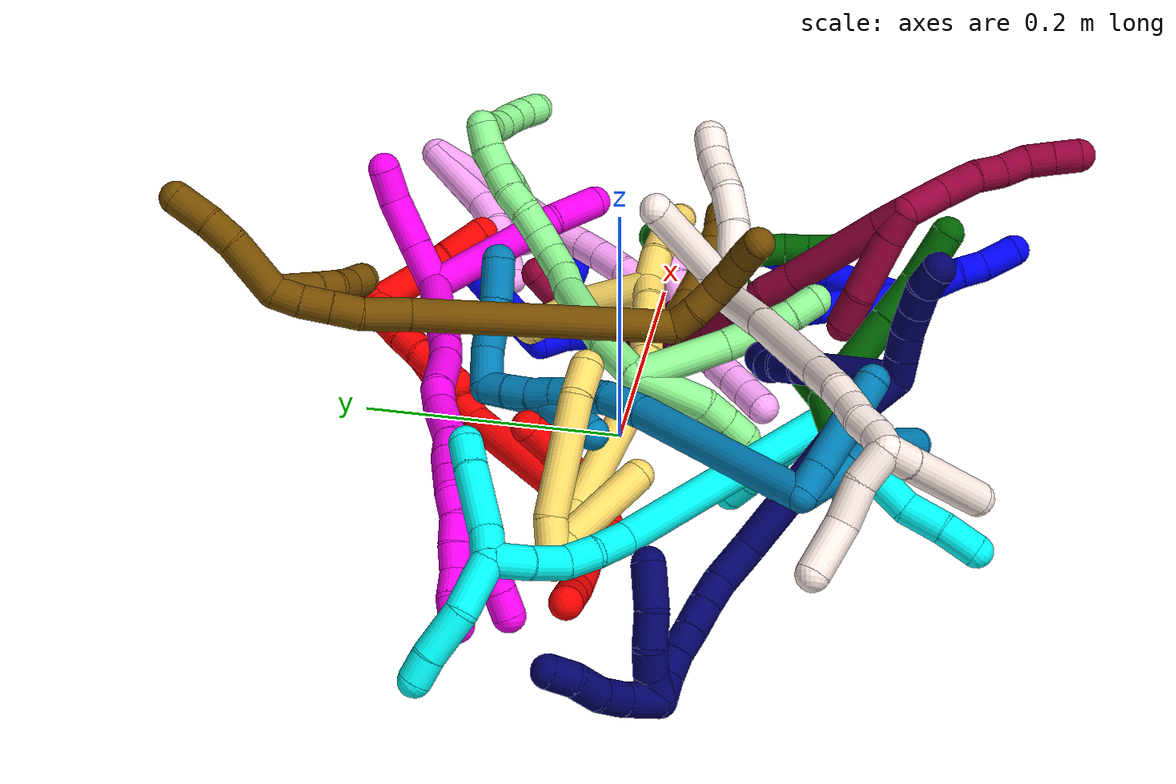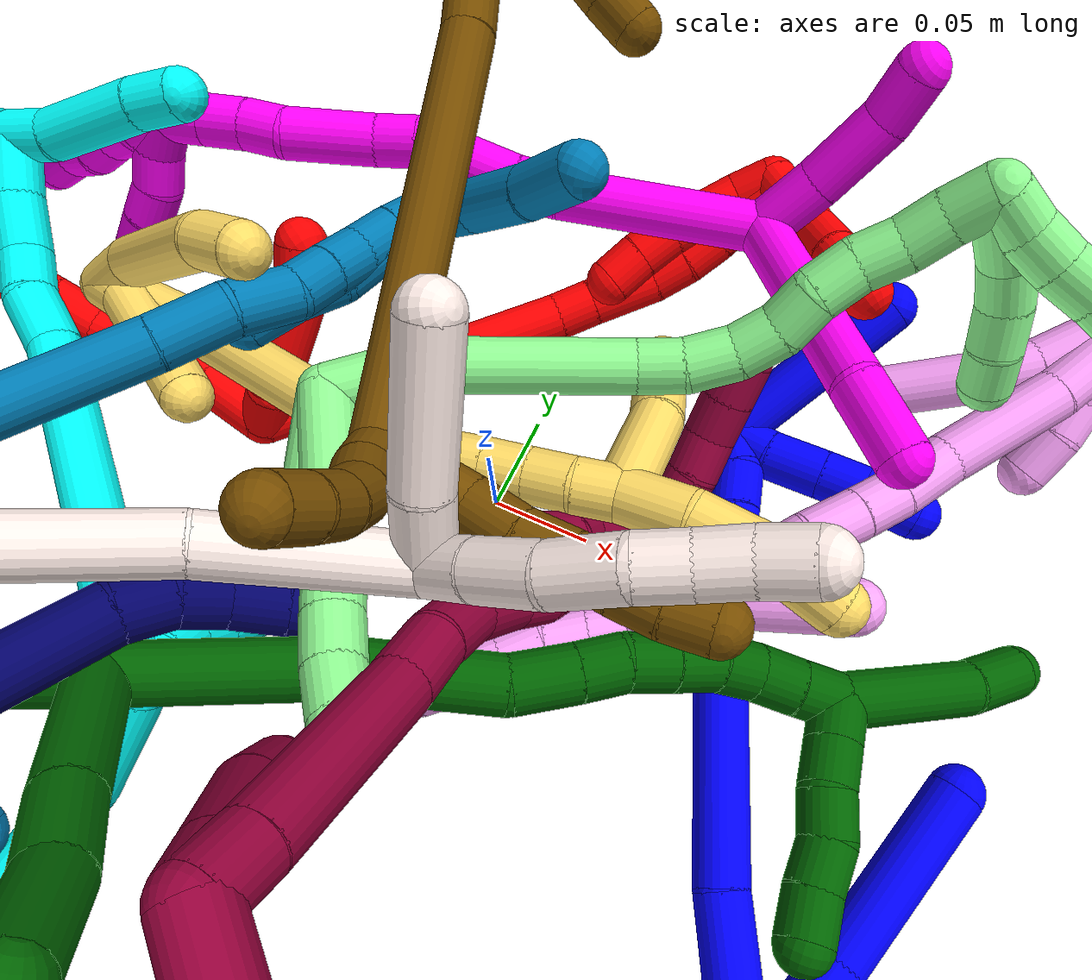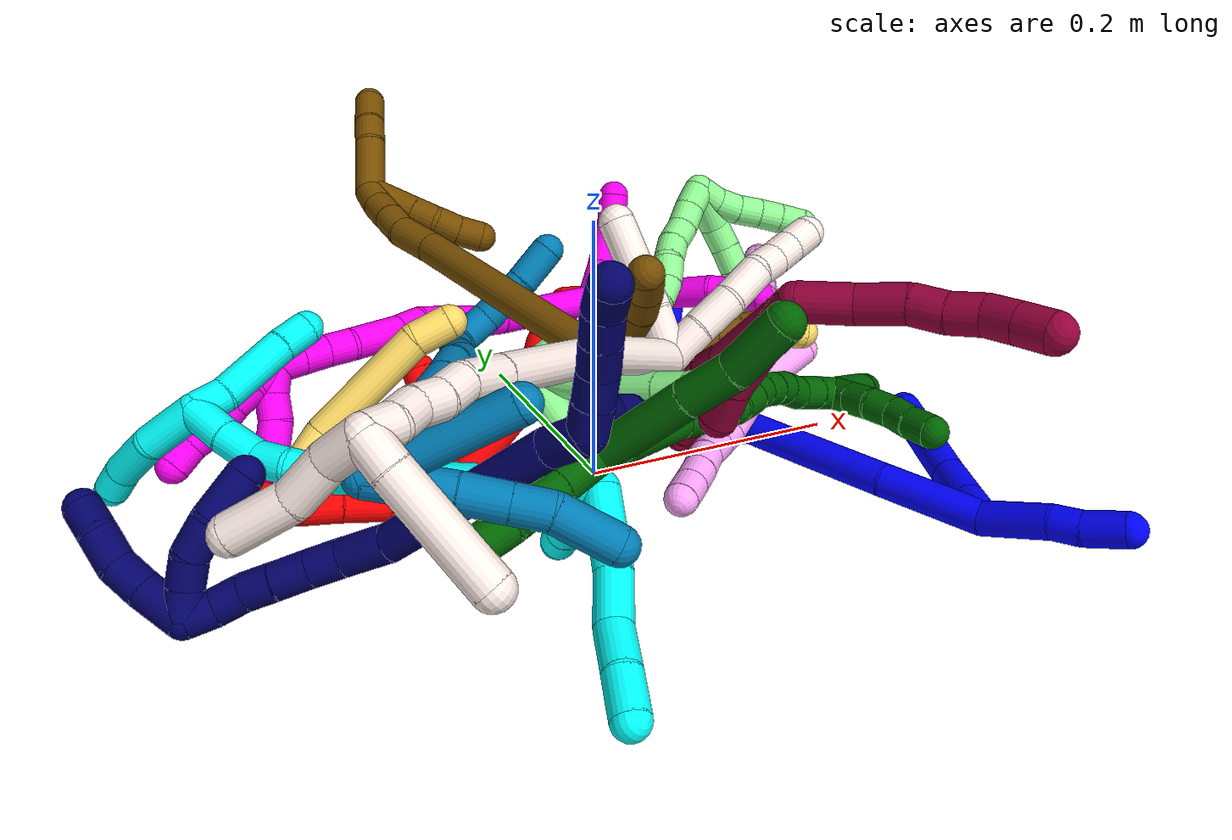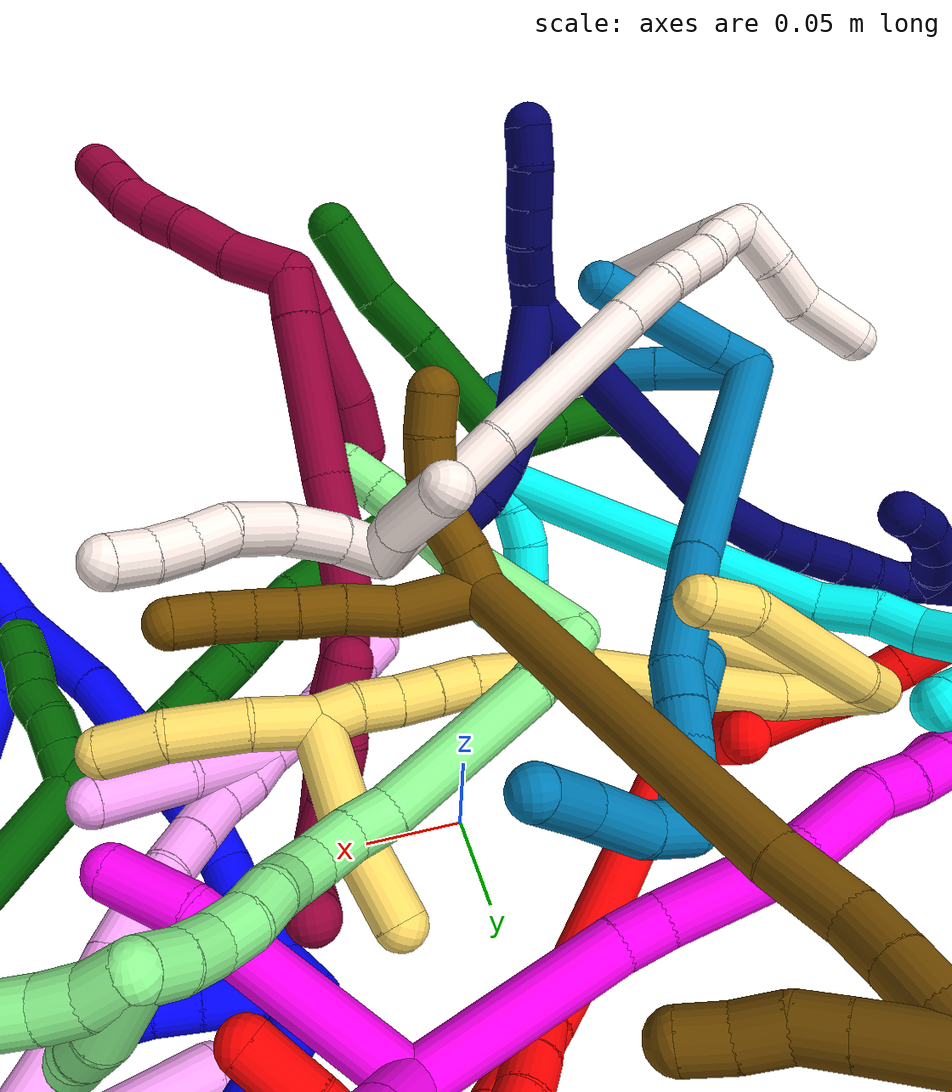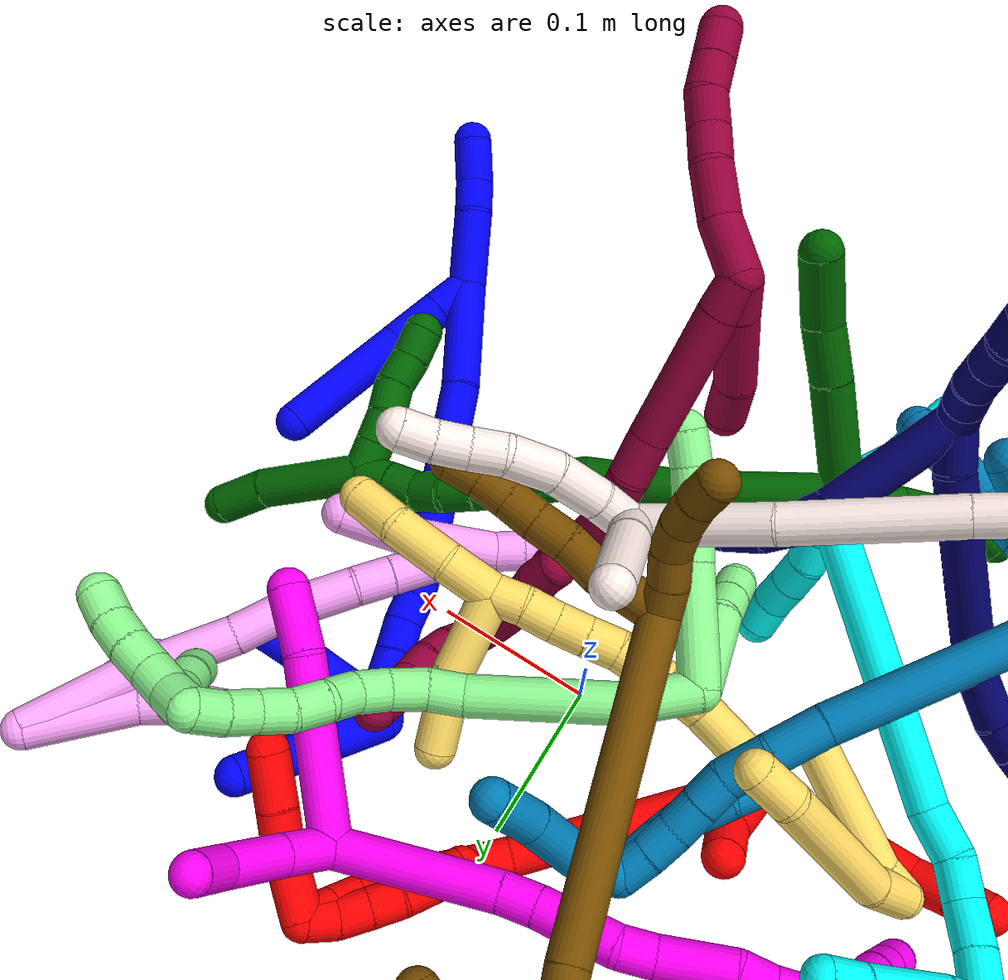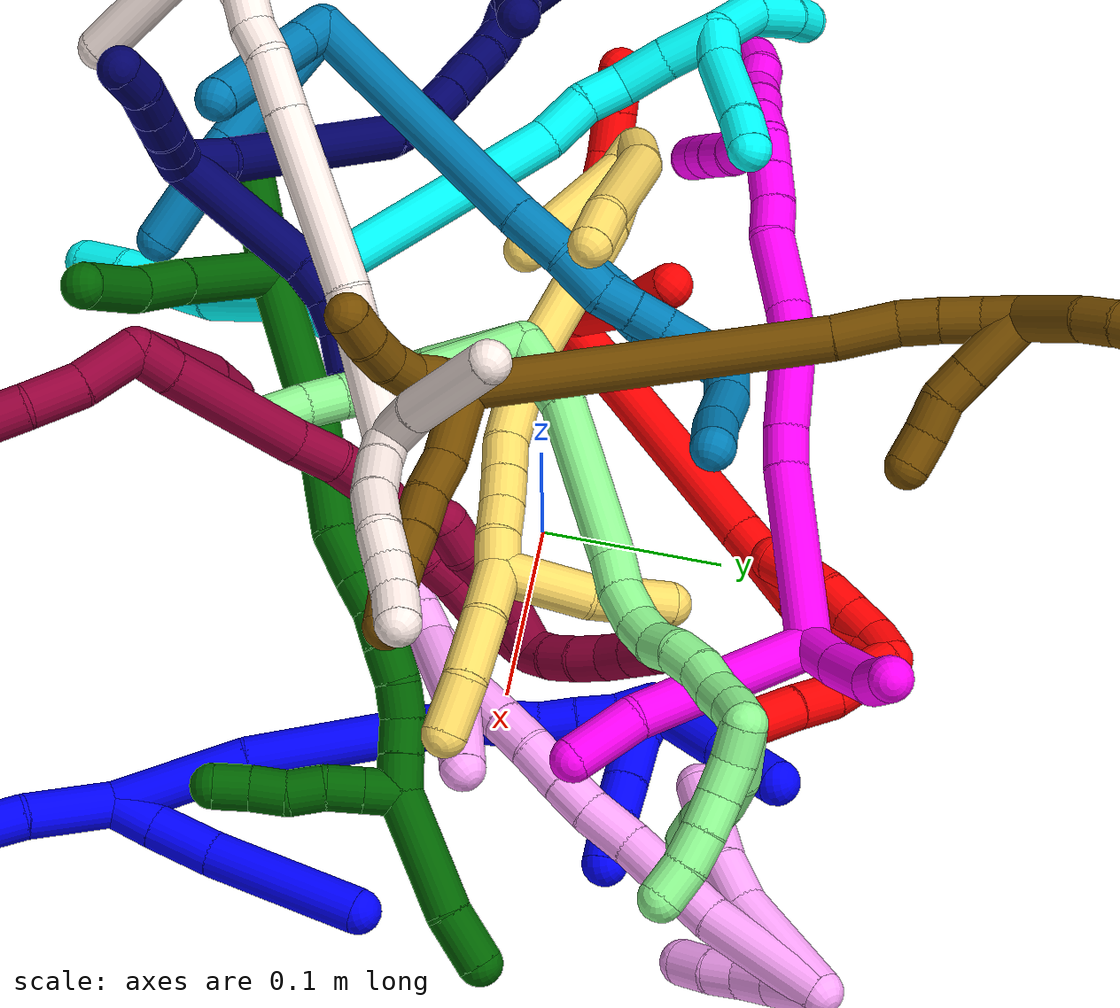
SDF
<sdf version="1.7">
 <world name="default">
  <plugin name="TubeGeneratorPlugin" filename="libtube_generator_plugin.so"/>
  <model name="photoneo_s_sensor">
   <static>1</static>
   <pose>0 0 2 1.57079 1.57079 3.14159</pose>
   <link name="link">
    <inertial><mass>0.1</mass></inertial>
    <sensor name="sensor" type="depth">
     <update_rate>30</update_rate>
     <camera>
      <horizontal_fov>1.22</horizontal_fov>
      <image><width>1920</width><height>1200</height><format>B8G8R8</format></image>
      <clip><near>0.1</near><far>4</far></clip>
      <depth_camera><output>points</output></depth_camera>
     </camera>
     <plugin name="camera_plugin" filename="libgazebo_ros_depth_camera.so">
      <baseline>0.2</baseline>
      <alwaysOn>1</alwaysOn>
      <updateRate>0.0</updateRate>
      <cameraName>camera_ir</cameraName>
      <imageTopicName>/camera/color/image_raw</imageTopicName>
      <cameraInfoTopicName>/camera/color/camera_info</cameraInfoTopicName>
      <depthImageTopicName>/camera/depth/image_raw</depthImageTopicName>
      <depthImageCameraInfoTopicName>/camera/depth/camera_info</depthImageCameraInfoTopicName>
      <pointCloudTopicName>/camera/depth/points</pointCloudTopicName>
      <frameName>fr_optical</frameName>
      <pointCloudCutoff>0.1</pointCloudCutoff>
      <pointCloudCutoffMax>2.0</pointCloudCutoffMax>
      <distortionK1>0</distortionK1>
      <distortionK2>0</distortionK2>
      <distortionK3>0</distortionK3>
      <distortionT1>0</distortionT1>
      <distortionT2>0</distortionT2>
      <CxPrime>0</CxPrime>
      <Cx>0</Cx>
      <Cy>0</Cy>
      <focalLength>0</focalLength>
      <hackBaseline>0</hackBaseline>
     </plugin>
    </sensor>
   </link>
  </model>
  <gravity>0 0 -9.8</gravity>
  <magnetic_field>6e-06 2.3e-05 -4.2e-05</magnetic_field>
  <atmosphere type="adiabatic"/>
  <physics name="default_physics" default="0" type="ode">
   <max_step_size>0.003</max_step_size>
   <real_time_factor>1</real_time_factor>
   <real_time_update_rate>1000</real_time_update_rate>
   <max_contacts>10000</max_contacts>
   <ode>
    <solver>
     <type>quick</type>
     <iters>100</iters>
     <sor>1.3</sor>
     <use_dynamic_moi_rescaling>0</use_dynamic_moi_rescaling>
    </solver>
    <constraints>
     <contact_max_correcting_vel>0</contact_max_correcting_vel>
     <contact_surface_layer>0.001</contact_surface_layer>
     <cfm>0</cfm>
     <erp>0.2</erp>
    </constraints>
   </ode>
  </physics>
  <scene><ambient>0.4 0.4 0.4 1</ambient><background>0.7 0.7 0.7 1</background><shadows>0</shadows></scene>
  <audio><device>default</device></audio>
  <spherical_coordinates>
   <surface_model>EARTH_WGS84</surface_model>
   <latitude_deg>0</latitude_deg>
   <longitude_deg>0</longitude_deg>
   <elevation>0</elevation>
   <heading_deg>0</heading_deg>
  </spherical_coordinates>
  <model name="bin">
   <static>1</static>
   <link name="bottom">
    <collision name="collision-bottom">
     <pose>0 0 -0.01 0 -0 0</pose>
     <geometry><box><size>0.8 0.6 0.02</size></box></geometry>
     <surface>
      <friction><ode><mu>100</mu><mu2>100</mu2></ode></friction>
      <contact><collide_bitmask>65535</collide_bitmask></contact>
     </surface>
    </collision>
   </link>
   <link name="west_wall">
    <collision name="collision-west_wall">
     <pose>-0.41 0 0.1 0 -0 0</pose>
     <geometry><box><size>0.02 0.6 0.2</size></box></geometry>
     <surface>
      <friction><ode><mu>100</mu><mu2>100</mu2></ode></friction>
      <contact><collide_bitmask>65535</collide_bitmask></contact>
     </surface>
    </collision>
   </link>
   <link name="east_wall">
    <collision name="collision-east_wall">
     <pose>0.41 0 0.1 0 -0 0</pose>
     <geometry><box><size>0.02 0.6 0.2</size></box></geometry>
     <surface>
      <friction><ode><mu>100</mu><mu2>100</mu2></ode></friction>
      <contact><collide_bitmask>65535</collide_bitmask></contact>
     </surface>
    </collision>
   </link>
   <link name="south_wall">
    <collision name="collision-south_wall">
     <pose>0 -0.31 0.1 0 -0 0</pose>
     <geometry><box><size>0.8 0.02 0.2</size></box></geometry>
     <surface>
      <friction><ode><mu>100</mu><mu2>100</mu2></ode></friction>
      <contact><collide_bitmask>65535</collide_bitmask></contact>
     </surface>
    </collision>
   </link>
   <link name="north_wall">
    <collision name="collision-north_wall">
     <pose>0 0.31 0.1 0 -0 0</pose>
     <geometry><box><size>0.8 0.02 0.2</size></box></geometry>
     <surface>
      <friction><ode><mu>100</mu><mu2>100</mu2></ode></friction>
      <contact><collide_bitmask>65535</collide_bitmask></contact>
     </surface>
    </collision>
   </link>
  </model>
  <model name="1">
   <static>0</static>
   <link name="1">
    <collision name="collision-cylinder-e_1_2_8">
     <pose>-0.006136 0.004923 -0.010705 -2.71053 -0.480085 1.68209</pose>
     <geometry><cylinder><radius>0.0125</radius><length>0.026569</length></cylinder></geometry>
     <surface>
      <friction><ode><mu>1.16</mu><mu2>1.16</mu2><slip1>0</slip1><slip2>0</slip2></ode></friction>
      <contact><ode><kp>1e+06</kp><kd>1</kd><max_vel>0</max_vel><min_depth>0.001</min_depth></ode></contact>
     </surface>
    </collision>
    <visual name="visual-cylinder-e_1_2_8">
     <pose>-0.006136 0.004923 -0.010705 -2.71053 -0.480085 1.68209</pose>
     <geometry><cylinder><radius>0.0125</radius><length>0.026569</length></cylinder></geometry>
     <material><ambient>0 0 1 1</ambient></material>
    </visual>
    <collision name="collision-cylinder-e_2_8_9">
     <pose>-0.01994 0.01596 -0.036441 -2.75528 -0.441518 1.70782</pose>
     <geometry><cylinder><radius>0.0125</radius><length>0.035896</length></cylinder></geometry>
     <surface>
      <friction><ode><mu>1.16</mu><mu2>1.16</mu2><slip1>0</slip1><slip2>0</slip2></ode></friction>
      <contact><ode><kp>1e+06</kp><kd>1</kd><max_vel>0</max_vel><min_depth>0.001</min_depth></ode></contact>
     </surface>
    </collision>
    <visual name="visual-cylinder-e_2_8_9">
     <pose>-0.01994 0.01596 -0.036441 -2.75528 -0.441518 1.70782</pose>
     <geometry><cylinder><radius>0.0125</radius><length>0.035896</length></cylinder></geometry>
     <material><ambient>0 0 1 1</ambient></material>
    </visual>
    <collision name="collision-cylinder-e_3_9_6">
     <pose>-0.0438 0.033866 -0.090387 -2.84739 -0.378927 1.82587</pose>
     <geometry><cylinder><radius>0.0125</radius><length>0.087535</length></cylinder></geometry>
     <surface>
      <friction><ode><mu>1.16</mu><mu2>1.16</mu2><slip1>0</slip1><slip2>0</slip2></ode></friction>
      <contact><ode><kp>1e+06</kp><kd>1</kd><max_vel>0</max_vel><min_depth>0.001</min_depth></ode></contact>
     </surface>
    </collision>
    <visual name="visual-cylinder-e_3_9_6">
     <pose>-0.0438 0.033866 -0.090387 -2.84739 -0.378927 1.82587</pose>
     <geometry><cylinder><radius>0.0125</radius><length>0.087535</length></cylinder></geometry>
     <material><ambient>0 0 1 1</ambient></material>
    </visual>
    <collision name="collision-cylinder-e_1_2_10">
     <pose>-0.005237 -0.019133 0.015352 0.894609 -0.210323 -0.101186</pose>
     <geometry><cylinder><radius>0.0125</radius><length>0.050168</length></cylinder></geometry>
     <surface>
      <friction><ode><mu>1.16</mu><mu2>1.16</mu2><slip1>0</slip1><slip2>0</slip2></ode></friction>
      <contact><ode><kp>1e+06</kp><kd>1</kd><max_vel>0</max_vel><min_depth>0.001</min_depth></ode></contact>
     </surface>
    </collision>
    <visual name="visual-cylinder-e_1_2_10">
     <pose>-0.005237 -0.019133 0.015352 0.894609 -0.210323 -0.101186</pose>
     <geometry><cylinder><radius>0.0125</radius><length>0.050168</length></cylinder></geometry>
     <material><ambient>0 0 1 1</ambient></material>
    </visual>
    <collision name="collision-cylinder-e_2_10_11">
     <pose>-0.013676 -0.044592 0.038094 0.707945 -0.318072 -0.118402</pose>
     <geometry><cylinder><radius>0.0125</radius><length>0.020481</length></cylinder></geometry>
     <surface>
      <friction><ode><mu>1.16</mu><mu2>1.16</mu2><slip1>0</slip1><slip2>0</slip2></ode></friction>
      <contact><ode><kp>1e+06</kp><kd>1</kd><max_vel>0</max_vel><min_depth>0.001</min_depth></ode></contact>
     </surface>
    </collision>
    <visual name="visual-cylinder-e_2_10_11">
     <pose>-0.013676 -0.044592 0.038094 0.707945 -0.318072 -0.118402</pose>
     <geometry><cylinder><radius>0.0125</radius><length>0.020481</length></cylinder></geometry>
     <material><ambient>0 0 1 1</ambient></material>
    </visual>
    <collision name="collision-cylinder-e_3_11_5">
     <pose>-0.021835 -0.061794 0.053998 0.906619 -0.344492 -0.169093</pose>
     <geometry><cylinder><radius>0.0125</radius><length>0.029351</length></cylinder></geometry>
     <surface>
      <friction><ode><mu>1.16</mu><mu2>1.16</mu2><slip1>0</slip1><slip2>0</slip2></ode></friction>
      <contact><ode><kp>1e+06</kp><kd>1</kd><max_vel>0</max_vel><min_depth>0.001</min_depth></ode></contact>
     </surface>
    </collision>
    <visual name="visual-cylinder-e_3_11_5">
     <pose>-0.021835 -0.061794 0.053998 0.906619 -0.344492 -0.169093</pose>
     <geometry><cylinder><radius>0.0125</radius><length>0.029351</length></cylinder></geometry>
     <material><ambient>0 0 1 1</ambient></material>
    </visual>
    <collision name="collision-cylinder-e_1_2_12">
     <pose>0.012662 0.017932 -0.030496 -2.61004 0.343707 -1.13522</pose>
     <geometry><cylinder><radius>0.0125</radius><length>0.07515</length></cylinder></geometry>
     <surface>
      <friction><ode><mu>1.16</mu><mu2>1.16</mu2><slip1>0</slip1><slip2>0</slip2></ode></friction>
      <contact><ode><kp>1e+06</kp><kd>1</kd><max_vel>0</max_vel><min_depth>0.001</min_depth></ode></contact>
     </surface>
    </collision>
    <visual name="visual-cylinder-e_1_2_12">
     <pose>0.012662 0.017932 -0.030496 -2.61004 0.343707 -1.13522</pose>
     <geometry><cylinder><radius>0.0125</radius><length>0.07515</length></cylinder></geometry>
     <material><ambient>0 0 1 1</ambient></material>
    </visual>
    <collision name="collision-cylinder-e_2_12_13">
     <pose>0.03714 0.067516 -0.109706 -2.56538 0.200658 -0.654917</pose>
     <geometry><cylinder><radius>0.0125</radius><length>0.118567</length></cylinder></geometry>
     <surface>
      <friction><ode><mu>1.16</mu><mu2>1.16</mu2><slip1>0</slip1><slip2>0</slip2></ode></friction>
      <contact><ode><kp>1e+06</kp><kd>1</kd><max_vel>0</max_vel><min_depth>0.001</min_depth></ode></contact>
     </surface>
    </collision>
    <visual name="visual-cylinder-e_2_12_13">
     <pose>0.03714 0.067516 -0.109706 -2.56538 0.200658 -0.654917</pose>
     <geometry><cylinder><radius>0.0125</radius><length>0.118567</length></cylinder></geometry>
     <material><ambient>0 0 1 1</ambient></material>
    </visual>
    <collision name="collision-cylinder-e_3_13_14">
     <pose>0.049384 0.107661 -0.165367 -2.25651 0.039006 -0.082274</pose>
     <geometry><cylinder><radius>0.0125</radius><length>0.021961</length></cylinder></geometry>
     <surface>
      <friction><ode><mu>1.16</mu><mu2>1.16</mu2><slip1>0</slip1><slip2>0</slip2></ode></friction>
      <contact><ode><kp>1e+06</kp><kd>1</kd><max_vel>0</max_vel><min_depth>0.001</min_depth></ode></contact>
     </surface>
    </collision>
    <visual name="visual-cylinder-e_3_13_14">
     <pose>0.049384 0.107661 -0.165367 -2.25651 0.039006 -0.082274</pose>
     <geometry><cylinder><radius>0.0125</radius><length>0.021961</length></cylinder></geometry>
     <material><ambient>0 0 1 1</ambient></material>
    </visual>
    <collision name="collision-cylinder-e_4_14_15">
     <pose>0.049435 0.121528 -0.180821 -2.57805 -0.037499 0.129376</pose>
     <geometry><cylinder><radius>0.0125</radius><length>0.020139</length></cylinder></geometry>
     <surface>
      <friction><ode><mu>1.16</mu><mu2>1.16</mu2><slip1>0</slip1><slip2>0</slip2></ode></friction>
      <contact><ode><kp>1e+06</kp><kd>1</kd><max_vel>0</max_vel><min_depth>0.001</min_depth></ode></contact>
     </surface>
    </collision>
    <visual name="visual-cylinder-e_4_14_15">
     <pose>0.049435 0.121528 -0.180821 -2.57805 -0.037499 0.129376</pose>
     <geometry><cylinder><radius>0.0125</radius><length>0.020139</length></cylinder></geometry>
     <material><ambient>0 0 1 1</ambient></material>
    </visual>
    <collision name="collision-cylinder-e_5_15_16">
     <pose>0.050519 0.131557 -0.198267 -2.66161 0.14397 -0.573136</pose>
     <geometry><cylinder><radius>0.0125</radius><length>0.020368</length></cylinder></geometry>
     <surface>
      <friction><ode><mu>1.16</mu><mu2>1.16</mu2><slip1>0</slip1><slip2>0</slip2></ode></friction>
      <contact><ode><kp>1e+06</kp><kd>1</kd><max_vel>0</max_vel><min_depth>0.001</min_depth></ode></contact>
     </surface>
    </collision>
    <visual name="visual-cylinder-e_5_15_16">
     <pose>0.050519 0.131557 -0.198267 -2.66161 0.14397 -0.573136</pose>
     <geometry><cylinder><radius>0.0125</radius><length>0.020368</length></cylinder></geometry>
     <material><ambient>0 0 1 1</ambient></material>
    </visual>
    <collision name="collision-cylinder-e_6_16_17">
     <pose>0.053034 0.141853 -0.216609 -2.6011 0.095904 -0.343053</pose>
     <geometry><cylinder><radius>0.0125</radius><length>0.02203</length></cylinder></geometry>
     <surface>
      <friction><ode><mu>1.16</mu><mu2>1.16</mu2><slip1>0</slip1><slip2>0</slip2></ode></friction>
      <contact><ode><kp>1e+06</kp><kd>1</kd><max_vel>0</max_vel><min_depth>0.001</min_depth></ode></contact>
     </surface>
    </collision>
    <visual name="visual-cylinder-e_6_16_17">
     <pose>0.053034 0.141853 -0.216609 -2.6011 0.095904 -0.343053</pose>
     <geometry><cylinder><radius>0.0125</radius><length>0.02203</length></cylinder></geometry>
     <material><ambient>0 0 1 1</ambient></material>
    </visual>
    <collision name="collision-cylinder-e_7_17_1">
     <pose>0.057838 0.154393 -0.23356 -2.40125 0.351305 -0.857908</pose>
     <geometry><cylinder><radius>0.0125</radius><length>0.021785</length></cylinder></geometry>
     <surface>
      <friction><ode><mu>1.16</mu><mu2>1.16</mu2><slip1>0</slip1><slip2>0</slip2></ode></friction>
      <contact><ode><kp>1e+06</kp><kd>1</kd><max_vel>0</max_vel><min_depth>0.001</min_depth></ode></contact>
     </surface>
    </collision>
    <visual name="visual-cylinder-e_7_17_1">
     <pose>0.057838 0.154393 -0.23356 -2.40125 0.351305 -0.857908</pose>
     <geometry><cylinder><radius>0.0125</radius><length>0.021785</length></cylinder></geometry>
     <material><ambient>0 0 1 1</ambient></material>
    </visual>
    <collision name="collision-cylinder-e_1_1_18">
     <pose>0.047287 0.157659 -0.264427 2.98702 -0.544782 -2.60071</pose>
     <geometry><cylinder><radius>0.0125</radius><length>0.055184</length></cylinder></geometry>
     <surface>
      <friction><ode><mu>1.16</mu><mu2>1.16</mu2><slip1>0</slip1><slip2>0</slip2></ode></friction>
      <contact><ode><kp>1e+06</kp><kd>1</kd><max_vel>0</max_vel><min_depth>0.001</min_depth></ode></contact>
     </surface>
    </collision>
    <visual name="visual-cylinder-e_1_1_18">
     <pose>0.047287 0.157659 -0.264427 2.98702 -0.544782 -2.60071</pose>
     <geometry><cylinder><radius>0.0125</radius><length>0.055184</length></cylinder></geometry>
     <material><ambient>0 0 1 1</ambient></material>
    </visual>
    <collision name="collision-cylinder-e_2_18_4">
     <pose>0.021546 0.150709 -0.306722 2.96858 -0.53593 -2.52972</pose>
     <geometry><cylinder><radius>0.0125</radius><length>0.044816</length></cylinder></geometry>
     <surface>
      <friction><ode><mu>1.16</mu><mu2>1.16</mu2><slip1>0</slip1><slip2>0</slip2></ode></friction>
      <contact><ode><kp>1e+06</kp><kd>1</kd><max_vel>0</max_vel><min_depth>0.001</min_depth></ode></contact>
     </surface>
    </collision>
    <visual name="visual-cylinder-e_2_18_4">
     <pose>0.021546 0.150709 -0.306722 2.96858 -0.53593 -2.52972</pose>
     <geometry><cylinder><radius>0.0125</radius><length>0.044816</length></cylinder></geometry>
     <material><ambient>0 0 1 1</ambient></material>
    </visual>
    <collision name="collision-cylinder-e_1_1_19">
     <pose>0.051607 0.15551 -0.239405 1.28394 -1.02731 -0.798277</pose>
     <geometry><cylinder><radius>0.0125</radius><length>0.023318</length></cylinder></geometry>
     <surface>
      <friction><ode><mu>1.16</mu><mu2>1.16</mu2><slip1>0</slip1><slip2>0</slip2></ode></friction>
      <contact><ode><kp>1e+06</kp><kd>1</kd><max_vel>0</max_vel><min_depth>0.001</min_depth></ode></contact>
     </surface>
    </collision>
    <visual name="visual-cylinder-e_1_1_19">
     <pose>0.051607 0.15551 -0.239405 1.28394 -1.02731 -0.798277</pose>
     <geometry><cylinder><radius>0.0125</radius><length>0.023318</length></cylinder></geometry>
     <material><ambient>0 0 1 1</ambient></material>
    </visual>
    <collision name="collision-cylinder-e_2_19_20">
     <pose>0.028597 0.144125 -0.237449 1.52626 -1.16441 -1.12385</pose>
     <geometry><cylinder><radius>0.0125</radius><length>0.028372</length></cylinder></geometry>
     <surface>
      <friction><ode><mu>1.16</mu><mu2>1.16</mu2><slip1>0</slip1><slip2>0</slip2></ode></friction>
      <contact><ode><kp>1e+06</kp><kd>1</kd><max_vel>0</max_vel><min_depth>0.001</min_depth></ode></contact>
     </surface>
    </collision>
    <visual name="visual-cylinder-e_2_19_20">
     <pose>0.028597 0.144125 -0.237449 1.52626 -1.16441 -1.12385</pose>
     <geometry><cylinder><radius>0.0125</radius><length>0.028372</length></cylinder></geometry>
     <material><ambient>0 0 1 1</ambient></material>
    </visual>
    <collision name="collision-cylinder-e_3_20_21">
     <pose>0.005723 0.134272 -0.236816 1.48087 -1.16174 -1.08067</pose>
     <geometry><cylinder><radius>0.0125</radius><length>0.021459</length></cylinder></geometry>
     <surface>
      <friction><ode><mu>1.16</mu><mu2>1.16</mu2><slip1>0</slip1><slip2>0</slip2></ode></friction>
      <contact><ode><kp>1e+06</kp><kd>1</kd><max_vel>0</max_vel><min_depth>0.001</min_depth></ode></contact>
     </surface>
    </collision>
    <visual name="visual-cylinder-e_3_20_21">
     <pose>0.005723 0.134272 -0.236816 1.48087 -1.16174 -1.08067</pose>
     <geometry><cylinder><radius>0.0125</radius><length>0.021459</length></cylinder></geometry>
     <material><ambient>0 0 1 1</ambient></material>
    </visual>
    <collision name="collision-cylinder-e_4_21_3">
     <pose>-0.017167 0.127097 -0.2352 1.17188 -1.33213 -0.961516</pose>
     <geometry><cylinder><radius>0.0125</radius><length>0.026851</length></cylinder></geometry>
     <surface>
      <friction><ode><mu>1.16</mu><mu2>1.16</mu2><slip1>0</slip1><slip2>0</slip2></ode></friction>
      <contact><ode><kp>1e+06</kp><kd>1</kd><max_vel>0</max_vel><min_depth>0.001</min_depth></ode></contact>
     </surface>
    </collision>
    <visual name="visual-cylinder-e_4_21_3">
     <pose>-0.017167 0.127097 -0.2352 1.17188 -1.33213 -0.961516</pose>
     <geometry><cylinder><radius>0.0125</radius><length>0.026851</length></cylinder></geometry>
     <material><ambient>0 0 1 1</ambient></material>
    </visual>
    <collision name="collision-sphere-3">
     <pose>-0.030212 0.124173 -0.233968 0 -0 0</pose>
     <geometry><sphere><radius>0.0125</radius></sphere></geometry>
     <surface>
      <friction><ode><mu>1.16</mu><mu2>1.16</mu2><slip1>0</slip1><slip2>0</slip2></ode></friction>
      <contact><ode><kp>1e+06</kp><kd>1</kd><max_vel>0</max_vel><min_depth>0.001</min_depth></ode></contact>
     </surface>
    </collision>
    <visual name="visual-sphere-3">
     <pose>-0.030212 0.124173 -0.233968 0 -0 0</pose>
     <geometry><sphere><radius>0.0125</radius></sphere></geometry>
     <material><ambient>0 0 1 1</ambient></material>
    </visual>
    <collision name="collision-sphere-21">
     <pose>-0.004122 0.130022 -0.236433 0 -0 0</pose>
     <geometry><sphere><radius>0.0125</radius></sphere></geometry>
     <surface>
      <friction><ode><mu>1.16</mu><mu2>1.16</mu2><slip1>0</slip1><slip2>0</slip2></ode></friction>
      <contact><ode><kp>1e+06</kp><kd>1</kd><max_vel>0</max_vel><min_depth>0.001</min_depth></ode></contact>
     </surface>
    </collision>
    <visual name="visual-sphere-21">
     <pose>-0.004122 0.130022 -0.236433 0 -0 0</pose>
     <geometry><sphere><radius>0.0125</radius></sphere></geometry>
     <material><ambient>0 0 1 1</ambient></material>
    </visual>
    <collision name="collision-sphere-20">
     <pose>0.015567 0.138523 -0.2372 0 -0 0</pose>
     <geometry><sphere><radius>0.0125</radius></sphere></geometry>
     <surface>
      <friction><ode><mu>1.16</mu><mu2>1.16</mu2><slip1>0</slip1><slip2>0</slip2></ode></friction>
      <contact><ode><kp>1e+06</kp><kd>1</kd><max_vel>0</max_vel><min_depth>0.001</min_depth></ode></contact>
     </surface>
    </collision>
    <visual name="visual-sphere-20">
     <pose>0.015567 0.138523 -0.2372 0 -0 0</pose>
     <geometry><sphere><radius>0.0125</radius></sphere></geometry>
     <material><ambient>0 0 1 1</ambient></material>
    </visual>
    <collision name="collision-sphere-19">
     <pose>0.041628 0.149727 -0.237699 0 -0 0</pose>
     <geometry><sphere><radius>0.0125</radius></sphere></geometry>
     <surface>
      <friction><ode><mu>1.16</mu><mu2>1.16</mu2><slip1>0</slip1><slip2>0</slip2></ode></friction>
      <contact><ode><kp>1e+06</kp><kd>1</kd><max_vel>0</max_vel><min_depth>0.001</min_depth></ode></contact>
     </surface>
    </collision>
    <visual name="visual-sphere-19">
     <pose>0.041628 0.149727 -0.237699 0 -0 0</pose>
     <geometry><sphere><radius>0.0125</radius></sphere></geometry>
     <material><ambient>0 0 1 1</ambient></material>
    </visual>
    <collision name="collision-sphere-11">
     <pose>-0.016879 -0.050917 0.045483 0 -0 0</pose>
     <geometry><sphere><radius>0.0125</radius></sphere></geometry>
     <surface>
      <friction><ode><mu>1.16</mu><mu2>1.16</mu2><slip1>0</slip1><slip2>0</slip2></ode></friction>
      <contact><ode><kp>1e+06</kp><kd>1</kd><max_vel>0</max_vel><min_depth>0.001</min_depth></ode></contact>
     </surface>
    </collision>
    <visual name="visual-sphere-11">
     <pose>-0.016879 -0.050917 0.045483 0 -0 0</pose>
     <geometry><sphere><radius>0.0125</radius></sphere></geometry>
     <material><ambient>0 0 1 1</ambient></material>
    </visual>
    <collision name="collision-sphere-10">
     <pose>-0.010474 -0.038267 0.030704 0 -0 0</pose>
     <geometry><sphere><radius>0.0125</radius></sphere></geometry>
     <surface>
      <friction><ode><mu>1.16</mu><mu2>1.16</mu2><slip1>0</slip1><slip2>0</slip2></ode></friction>
      <contact><ode><kp>1e+06</kp><kd>1</kd><max_vel>0</max_vel><min_depth>0.001</min_depth></ode></contact>
     </surface>
    </collision>
    <visual name="visual-sphere-10">
     <pose>-0.010474 -0.038267 0.030704 0 -0 0</pose>
     <geometry><sphere><radius>0.0125</radius></sphere></geometry>
     <material><ambient>0 0 1 1</ambient></material>
    </visual>
    <collision name="collision-sphere-6">
     <pose>-0.059991 0.045657 -0.129303 0 -0 0</pose>
     <geometry><sphere><radius>0.0125</radius></sphere></geometry>
     <surface>
      <friction><ode><mu>1.16</mu><mu2>1.16</mu2><slip1>0</slip1><slip2>0</slip2></ode></friction>
      <contact><ode><kp>1e+06</kp><kd>1</kd><max_vel>0</max_vel><min_depth>0.001</min_depth></ode></contact>
     </surface>
    </collision>
    <visual name="visual-sphere-6">
     <pose>-0.059991 0.045657 -0.129303 0 -0 0</pose>
     <geometry><sphere><radius>0.0125</radius></sphere></geometry>
     <material><ambient>0 0 1 1</ambient></material>
    </visual>
    <collision name="collision-sphere-9">
     <pose>-0.02761 0.022074 -0.051472 0 -0 0</pose>
     <geometry><sphere><radius>0.0125</radius></sphere></geometry>
     <surface>
      <friction><ode><mu>1.16</mu><mu2>1.16</mu2><slip1>0</slip1><slip2>0</slip2></ode></friction>
      <contact><ode><kp>1e+06</kp><kd>1</kd><max_vel>0</max_vel><min_depth>0.001</min_depth></ode></contact>
     </surface>
    </collision>
    <visual name="visual-sphere-9">
     <pose>-0.02761 0.022074 -0.051472 0 -0 0</pose>
     <geometry><sphere><radius>0.0125</radius></sphere></geometry>
     <material><ambient>0 0 1 1</ambient></material>
    </visual>
    <collision name="collision-sphere-2">
     <geometry><sphere><radius>0.0125</radius></sphere></geometry>
     <surface>
      <friction><ode><mu>1.16</mu><mu2>1.16</mu2><slip1>0</slip1><slip2>0</slip2></ode></friction>
      <contact><ode><kp>1e+06</kp><kd>1</kd><max_vel>0</max_vel><min_depth>0.001</min_depth></ode></contact>
     </surface>
    </collision>
    <visual name="visual-sphere-2">
     <geometry><sphere><radius>0.0125</radius></sphere></geometry>
     <material><ambient>0 0 1 1</ambient></material>
    </visual>
    <collision name="collision-sphere-8">
     <pose>-0.012271 0.009847 -0.02141 0 -0 0</pose>
     <geometry><sphere><radius>0.0125</radius></sphere></geometry>
     <surface>
      <friction><ode><mu>1.16</mu><mu2>1.16</mu2><slip1>0</slip1><slip2>0</slip2></ode></friction>
      <contact><ode><kp>1e+06</kp><kd>1</kd><max_vel>0</max_vel><min_depth>0.001</min_depth></ode></contact>
     </surface>
    </collision>
    <visual name="visual-sphere-8">
     <pose>-0.012271 0.009847 -0.02141 0 -0 0</pose>
     <geometry><sphere><radius>0.0125</radius></sphere></geometry>
     <material><ambient>0 0 1 1</ambient></material>
    </visual>
    <collision name="collision-sphere-5">
     <pose>-0.026791 -0.072671 0.062513 0 -0 0</pose>
     <geometry><sphere><radius>0.0125</radius></sphere></geometry>
     <surface>
      <friction><ode><mu>1.16</mu><mu2>1.16</mu2><slip1>0</slip1><slip2>0</slip2></ode></friction>
      <contact><ode><kp>1e+06</kp><kd>1</kd><max_vel>0</max_vel><min_depth>0.001</min_depth></ode></contact>
     </surface>
    </collision>
    <visual name="visual-sphere-5">
     <pose>-0.026791 -0.072671 0.062513 0 -0 0</pose>
     <geometry><sphere><radius>0.0125</radius></sphere></geometry>
     <material><ambient>0 0 1 1</ambient></material>
    </visual>
    <collision name="collision-sphere-12">
     <pose>0.025324 0.035864 -0.060992 0 -0 0</pose>
     <geometry><sphere><radius>0.0125</radius></sphere></geometry>
     <surface>
      <friction><ode><mu>1.16</mu><mu2>1.16</mu2><slip1>0</slip1><slip2>0</slip2></ode></friction>
      <contact><ode><kp>1e+06</kp><kd>1</kd><max_vel>0</max_vel><min_depth>0.001</min_depth></ode></contact>
     </surface>
    </collision>
    <visual name="visual-sphere-12">
     <pose>0.025324 0.035864 -0.060992 0 -0 0</pose>
     <geometry><sphere><radius>0.0125</radius></sphere></geometry>
     <material><ambient>0 0 1 1</ambient></material>
    </visual>
    <collision name="collision-sphere-13">
     <pose>0.048956 0.099169 -0.158419 0 -0 0</pose>
     <geometry><sphere><radius>0.0125</radius></sphere></geometry>
     <surface>
      <friction><ode><mu>1.16</mu><mu2>1.16</mu2><slip1>0</slip1><slip2>0</slip2></ode></friction>
      <contact><ode><kp>1e+06</kp><kd>1</kd><max_vel>0</max_vel><min_depth>0.001</min_depth></ode></contact>
     </surface>
    </collision>
    <visual name="visual-sphere-13">
     <pose>0.048956 0.099169 -0.158419 0 -0 0</pose>
     <geometry><sphere><radius>0.0125</radius></sphere></geometry>
     <material><ambient>0 0 1 1</ambient></material>
    </visual>
    <collision name="collision-sphere-14">
     <pose>0.049812 0.116153 -0.172315 0 -0 0</pose>
     <geometry><sphere><radius>0.0125</radius></sphere></geometry>
     <surface>
      <friction><ode><mu>1.16</mu><mu2>1.16</mu2><slip1>0</slip1><slip2>0</slip2></ode></friction>
      <contact><ode><kp>1e+06</kp><kd>1</kd><max_vel>0</max_vel><min_depth>0.001</min_depth></ode></contact>
     </surface>
    </collision>
    <visual name="visual-sphere-14">
     <pose>0.049812 0.116153 -0.172315 0 -0 0</pose>
     <geometry><sphere><radius>0.0125</radius></sphere></geometry>
     <material><ambient>0 0 1 1</ambient></material>
    </visual>
    <collision name="collision-sphere-15">
     <pose>0.049057 0.126903 -0.189328 0 -0 0</pose>
     <geometry><sphere><radius>0.0125</radius></sphere></geometry>
     <surface>
      <friction><ode><mu>1.16</mu><mu2>1.16</mu2><slip1>0</slip1><slip2>0</slip2></ode></friction>
      <contact><ode><kp>1e+06</kp><kd>1</kd><max_vel>0</max_vel><min_depth>0.001</min_depth></ode></contact>
     </surface>
    </collision>
    <visual name="visual-sphere-15">
     <pose>0.049057 0.126903 -0.189328 0 -0 0</pose>
     <geometry><sphere><radius>0.0125</radius></sphere></geometry>
     <material><ambient>0 0 1 1</ambient></material>
    </visual>
    <collision name="collision-sphere-16">
     <pose>0.05198 0.136211 -0.207207 0 -0 0</pose>
     <geometry><sphere><radius>0.0125</radius></sphere></geometry>
     <surface>
      <friction><ode><mu>1.16</mu><mu2>1.16</mu2><slip1>0</slip1><slip2>0</slip2></ode></friction>
      <contact><ode><kp>1e+06</kp><kd>1</kd><max_vel>0</max_vel><min_depth>0.001</min_depth></ode></contact>
     </surface>
    </collision>
    <visual name="visual-sphere-16">
     <pose>0.05198 0.136211 -0.207207 0 -0 0</pose>
     <geometry><sphere><radius>0.0125</radius></sphere></geometry>
     <material><ambient>0 0 1 1</ambient></material>
    </visual>
    <collision name="collision-sphere-17">
     <pose>0.054089 0.147495 -0.22601 0 -0 0</pose>
     <geometry><sphere><radius>0.0125</radius></sphere></geometry>
     <surface>
      <friction><ode><mu>1.16</mu><mu2>1.16</mu2><slip1>0</slip1><slip2>0</slip2></ode></friction>
      <contact><ode><kp>1e+06</kp><kd>1</kd><max_vel>0</max_vel><min_depth>0.001</min_depth></ode></contact>
     </surface>
    </collision>
    <visual name="visual-sphere-17">
     <pose>0.054089 0.147495 -0.22601 0 -0 0</pose>
     <geometry><sphere><radius>0.0125</radius></sphere></geometry>
     <material><ambient>0 0 1 1</ambient></material>
    </visual>
    <collision name="collision-sphere-1">
     <pose>0.061586 0.161292 -0.241111 0 -0 0</pose>
     <geometry><sphere><radius>0.0125</radius></sphere></geometry>
     <surface>
      <friction><ode><mu>1.16</mu><mu2>1.16</mu2><slip1>0</slip1><slip2>0</slip2></ode></friction>
      <contact><ode><kp>1e+06</kp><kd>1</kd><max_vel>0</max_vel><min_depth>0.001</min_depth></ode></contact>
     </surface>
    </collision>
    <visual name="visual-sphere-1">
     <pose>0.061586 0.161292 -0.241111 0 -0 0</pose>
     <geometry><sphere><radius>0.0125</radius></sphere></geometry>
     <material><ambient>0 0 1 1</ambient></material>
    </visual>
    <collision name="collision-sphere-18">
     <pose>0.032988 0.154026 -0.287744 0 -0 0</pose>
     <geometry><sphere><radius>0.0125</radius></sphere></geometry>
     <surface>
      <friction><ode><mu>1.16</mu><mu2>1.16</mu2><slip1>0</slip1><slip2>0</slip2></ode></friction>
      <contact><ode><kp>1e+06</kp><kd>1</kd><max_vel>0</max_vel><min_depth>0.001</min_depth></ode></contact>
     </surface>
    </collision>
    <visual name="visual-sphere-18">
     <pose>0.032988 0.154026 -0.287744 0 -0 0</pose>
     <geometry><sphere><radius>0.0125</radius></sphere></geometry>
     <material><ambient>0 0 1 1</ambient></material>
    </visual>
    <collision name="collision-sphere-4">
     <pose>0.010103 0.147393 -0.325701 0 -0 0</pose>
     <geometry><sphere><radius>0.0125</radius></sphere></geometry>
     <surface>
      <friction><ode><mu>1.16</mu><mu2>1.16</mu2><slip1>0</slip1><slip2>0</slip2></ode></friction>
      <contact><ode><kp>1e+06</kp><kd>1</kd><max_vel>0</max_vel><min_depth>0.001</min_depth></ode></contact>
     </surface>
    </collision>
    <visual name="visual-sphere-4">
     <pose>0.010103 0.147393 -0.325701 0 -0 0</pose>
     <geometry><sphere><radius>0.0125</radius></sphere></geometry>
     <material><ambient>0 0 1 1</ambient></material>
    </visual>
    <inertial>
     <pose>0.013664 0.07037 -0.126526 0 -0 0</pose>
     <mass>0.75</mass>
     <inertia>
      <ixx>2.9e-05</ixx>
      <ixy>0</ixy>
      <ixz>0</ixz>
      <iyy>-0.000106</iyy>
      <iyz>0</iyz>
      <izz>-0.00012</izz>
     </inertia>
    </inertial>
   </link>
   <pose>0.209063 -0.192411 0.011499 -2.11467 -0.213079 -2.95951</pose>
  </model>
  <model name="2">
   <static>0</static>
   <link name="2">
    <collision name="collision-cylinder-e_1_2_8">
     <pose>-0.00654 -0.001688 0.017232 0.097661 -0.36118 -0.017845</pose>
     <geometry><cylinder><radius>0.0125</radius><length>0.037016</length></cylinder></geometry>
     <surface>
      <friction><ode><mu>1.16</mu><mu2>1.16</mu2><slip1>0</slip1><slip2>0</slip2></ode></friction>
      <contact><ode><kp>1e+06</kp><kd>1</kd><max_vel>0</max_vel><min_depth>0.001</min_depth></ode></contact>
     </surface>
    </collision>
    <visual name="visual-cylinder-e_1_2_8">
     <pose>-0.00654 -0.001688 0.017232 0.097661 -0.36118 -0.017845</pose>
     <geometry><cylinder><radius>0.0125</radius><length>0.037016</length></cylinder></geometry>
     <material><ambient>1 0 0 1</ambient></material>
    </visual>
    <collision name="collision-cylinder-e_2_8_9">
     <pose>-0.020499 -0.009156 0.049869 0.358897 -0.42356 -0.077964</pose>
     <geometry><cylinder><radius>0.0125</radius><length>0.036099</length></cylinder></geometry>
     <surface>
      <friction><ode><mu>1.16</mu><mu2>1.16</mu2><slip1>0</slip1><slip2>0</slip2></ode></friction>
      <contact><ode><kp>1e+06</kp><kd>1</kd><max_vel>0</max_vel><min_depth>0.001</min_depth></ode></contact>
     </surface>
    </collision>
    <visual name="visual-cylinder-e_2_8_9">
     <pose>-0.020499 -0.009156 0.049869 0.358897 -0.42356 -0.077964</pose>
     <geometry><cylinder><radius>0.0125</radius><length>0.036099</length></cylinder></geometry>
     <material><ambient>1 0 0 1</ambient></material>
    </visual>
    <collision name="collision-cylinder-e_3_9_10">
     <pose>-0.033801 -0.018026 0.077118 0.255314 -0.448084 -0.058479</pose>
     <geometry><cylinder><radius>0.0125</radius><length>0.02716</length></cylinder></geometry>
     <surface>
      <friction><ode><mu>1.16</mu><mu2>1.16</mu2><slip1>0</slip1><slip2>0</slip2></ode></friction>
      <contact><ode><kp>1e+06</kp><kd>1</kd><max_vel>0</max_vel><min_depth>0.001</min_depth></ode></contact>
     </surface>
    </collision>
    <visual name="visual-cylinder-e_3_9_10">
     <pose>-0.033801 -0.018026 0.077118 0.255314 -0.448084 -0.058479</pose>
     <geometry><cylinder><radius>0.0125</radius><length>0.02716</length></cylinder></geometry>
     <material><ambient>1 0 0 1</ambient></material>
    </visual>
    <collision name="collision-cylinder-e_4_10_11">
     <pose>-0.042429 -0.027093 0.099782 0.50449 -0.218497 -0.056524</pose>
     <geometry><cylinder><radius>0.0125</radius><length>0.025327</length></cylinder></geometry>
     <surface>
      <friction><ode><mu>1.16</mu><mu2>1.16</mu2><slip1>0</slip1><slip2>0</slip2></ode></friction>
      <contact><ode><kp>1e+06</kp><kd>1</kd><max_vel>0</max_vel><min_depth>0.001</min_depth></ode></contact>
     </surface>
    </collision>
    <visual name="visual-cylinder-e_4_10_11">
     <pose>-0.042429 -0.027093 0.099782 0.50449 -0.218497 -0.056524</pose>
     <geometry><cylinder><radius>0.0125</radius><length>0.025327</length></cylinder></geometry>
     <material><ambient>1 0 0 1</ambient></material>
    </visual>
    <collision name="collision-cylinder-e_5_11_6">
     <pose>-0.047799 -0.038992 0.120941 0.520387 -0.216814 -0.057933</pose>
     <geometry><cylinder><radius>0.0125</radius><length>0.024399</length></cylinder></geometry>
     <surface>
      <friction><ode><mu>1.16</mu><mu2>1.16</mu2><slip1>0</slip1><slip2>0</slip2></ode></friction>
      <contact><ode><kp>1e+06</kp><kd>1</kd><max_vel>0</max_vel><min_depth>0.001</min_depth></ode></contact>
     </surface>
    </collision>
    <visual name="visual-cylinder-e_5_11_6">
     <pose>-0.047799 -0.038992 0.120941 0.520387 -0.216814 -0.057933</pose>
     <geometry><cylinder><radius>0.0125</radius><length>0.024399</length></cylinder></geometry>
     <material><ambient>1 0 0 1</ambient></material>
    </visual>
    <collision name="collision-cylinder-e_1_2_12">
     <pose>0.009799 -0.003827 0.002818 0.93601 1.11923 0.613282</pose>
     <geometry><cylinder><radius>0.0125</radius><length>0.021782</length></cylinder></geometry>
     <surface>
      <friction><ode><mu>1.16</mu><mu2>1.16</mu2><slip1>0</slip1><slip2>0</slip2></ode></friction>
      <contact><ode><kp>1e+06</kp><kd>1</kd><max_vel>0</max_vel><min_depth>0.001</min_depth></ode></contact>
     </surface>
    </collision>
    <visual name="visual-cylinder-e_1_2_12">
     <pose>0.009799 -0.003827 0.002818 0.93601 1.11923 0.613282</pose>
     <geometry><cylinder><radius>0.0125</radius><length>0.021782</length></cylinder></geometry>
     <material><ambient>1 0 0 1</ambient></material>
    </visual>
    <collision name="collision-cylinder-e_2_12_13">
     <pose>0.043122 -0.009657 0.016584 0.181049 1.12889 0.11482</pose>
     <geometry><cylinder><radius>0.0125</radius><length>0.052047</length></cylinder></geometry>
     <surface>
      <friction><ode><mu>1.16</mu><mu2>1.16</mu2><slip1>0</slip1><slip2>0</slip2></ode></friction>
      <contact><ode><kp>1e+06</kp><kd>1</kd><max_vel>0</max_vel><min_depth>0.001</min_depth></ode></contact>
     </surface>
    </collision>
    <visual name="visual-cylinder-e_2_12_13">
     <pose>0.043122 -0.009657 0.016584 0.181049 1.12889 0.11482</pose>
     <geometry><cylinder><radius>0.0125</radius><length>0.052047</length></cylinder></geometry>
     <material><ambient>1 0 0 1</ambient></material>
    </visual>
    <collision name="collision-cylinder-e_3_13_5">
     <pose>0.076435 -0.01359 0.035997 0.223989 0.845236 0.101069</pose>
     <geometry><cylinder><radius>0.0125</radius><length>0.026171</length></cylinder></geometry>
     <surface>
      <friction><ode><mu>1.16</mu><mu2>1.16</mu2><slip1>0</slip1><slip2>0</slip2></ode></friction>
      <contact><ode><kp>1e+06</kp><kd>1</kd><max_vel>0</max_vel><min_depth>0.001</min_depth></ode></contact>
     </surface>
    </collision>
    <visual name="visual-cylinder-e_3_13_5">
     <pose>0.076435 -0.01359 0.035997 0.223989 0.845236 0.101069</pose>
     <geometry><cylinder><radius>0.0125</radius><length>0.026171</length></cylinder></geometry>
     <material><ambient>1 0 0 1</ambient></material>
    </visual>
    <collision name="collision-cylinder-e_1_2_14">
     <pose>0.064682 0.047419 -0.0174 -1.92248 0.907807 -1.21972</pose>
     <geometry><cylinder><radius>0.0125</radius><length>0.164135</length></cylinder></geometry>
     <surface>
      <friction><ode><mu>1.16</mu><mu2>1.16</mu2><slip1>0</slip1><slip2>0</slip2></ode></friction>
      <contact><ode><kp>1e+06</kp><kd>1</kd><max_vel>0</max_vel><min_depth>0.001</min_depth></ode></contact>
     </surface>
    </collision>
    <visual name="visual-cylinder-e_1_2_14">
     <pose>0.064682 0.047419 -0.0174 -1.92248 0.907807 -1.21972</pose>
     <geometry><cylinder><radius>0.0125</radius><length>0.164135</length></cylinder></geometry>
     <material><ambient>1 0 0 1</ambient></material>
    </visual>
    <collision name="collision-cylinder-e_2_14_15">
     <pose>0.138221 0.099338 -0.036787 -1.98659 1.06378 -1.46903</pose>
     <geometry><cylinder><radius>0.0125</radius><length>0.020263</length></cylinder></geometry>
     <surface>
      <friction><ode><mu>1.16</mu><mu2>1.16</mu2><slip1>0</slip1><slip2>0</slip2></ode></friction>
      <contact><ode><kp>1e+06</kp><kd>1</kd><max_vel>0</max_vel><min_depth>0.001</min_depth></ode></contact>
     </surface>
    </collision>
    <visual name="visual-cylinder-e_2_14_15">
     <pose>0.138221 0.099338 -0.036787 -1.98659 1.06378 -1.46903</pose>
     <geometry><cylinder><radius>0.0125</radius><length>0.020263</length></cylinder></geometry>
     <material><ambient>1 0 0 1</ambient></material>
    </visual>
    <collision name="collision-cylinder-e_3_15_16">
     <pose>0.162444 0.111547 -0.042737 -2.04566 1.05721 -1.52681</pose>
     <geometry><cylinder><radius>0.0125</radius><length>0.035283</length></cylinder></geometry>
     <surface>
      <friction><ode><mu>1.16</mu><mu2>1.16</mu2><slip1>0</slip1><slip2>0</slip2></ode></friction>
      <contact><ode><kp>1e+06</kp><kd>1</kd><max_vel>0</max_vel><min_depth>0.001</min_depth></ode></contact>
     </surface>
    </collision>
    <visual name="visual-cylinder-e_3_15_16">
     <pose>0.162444 0.111547 -0.042737 -2.04566 1.05721 -1.52681</pose>
     <geometry><cylinder><radius>0.0125</radius><length>0.035283</length></cylinder></geometry>
     <material><ambient>1 0 0 1</ambient></material>
    </visual>
    <collision name="collision-cylinder-e_4_16_17">
     <pose>0.187417 0.121875 -0.047912 -2.00441 1.27898 -1.72205</pose>
     <geometry><cylinder><radius>0.0125</radius><length>0.020063</length></cylinder></geometry>
     <surface>
      <friction><ode><mu>1.16</mu><mu2>1.16</mu2><slip1>0</slip1><slip2>0</slip2></ode></friction>
      <contact><ode><kp>1e+06</kp><kd>1</kd><max_vel>0</max_vel><min_depth>0.001</min_depth></ode></contact>
     </surface>
    </collision>
    <visual name="visual-cylinder-e_4_16_17">
     <pose>0.187417 0.121875 -0.047912 -2.00441 1.27898 -1.72205</pose>
     <geometry><cylinder><radius>0.0125</radius><length>0.020063</length></cylinder></geometry>
     <material><ambient>1 0 0 1</ambient></material>
    </visual>
    <collision name="collision-cylinder-e_5_17_18">
     <pose>0.206649 0.127307 -0.048965 -1.51385 1.28596 -1.23174</pose>
     <geometry><cylinder><radius>0.0125</radius><length>0.020058</length></cylinder></geometry>
     <surface>
      <friction><ode><mu>1.16</mu><mu2>1.16</mu2><slip1>0</slip1><slip2>0</slip2></ode></friction>
      <contact><ode><kp>1e+06</kp><kd>1</kd><max_vel>0</max_vel><min_depth>0.001</min_depth></ode></contact>
     </surface>
    </collision>
    <visual name="visual-cylinder-e_5_17_18">
     <pose>0.206649 0.127307 -0.048965 -1.51385 1.28596 -1.23174</pose>
     <geometry><cylinder><radius>0.0125</radius><length>0.020058</length></cylinder></geometry>
     <material><ambient>1 0 0 1</ambient></material>
    </visual>
    <collision name="collision-cylinder-e_6_18_19">
     <pose>0.22625 0.131019 -0.047575 -0.631163 1.41929 -0.54681</pose>
     <geometry><cylinder><radius>0.0125</radius><length>0.020182</length></cylinder></geometry>
     <surface>
      <friction><ode><mu>1.16</mu><mu2>1.16</mu2><slip1>0</slip1><slip2>0</slip2></ode></friction>
      <contact><ode><kp>1e+06</kp><kd>1</kd><max_vel>0</max_vel><min_depth>0.001</min_depth></ode></contact>
     </surface>
    </collision>
    <visual name="visual-cylinder-e_6_18_19">
     <pose>0.22625 0.131019 -0.047575 -0.631163 1.41929 -0.54681</pose>
     <geometry><cylinder><radius>0.0125</radius><length>0.020182</length></cylinder></geometry>
     <material><ambient>1 0 0 1</ambient></material>
    </visual>
    <collision name="collision-cylinder-e_7_19_1">
     <pose>0.2461 0.132538 -0.044842 -0.39109 1.40759 -0.333136</pose>
     <geometry><cylinder><radius>0.0125</radius><length>0.020015</length></cylinder></geometry>
     <surface>
      <friction><ode><mu>1.16</mu><mu2>1.16</mu2><slip1>0</slip1><slip2>0</slip2></ode></friction>
      <contact><ode><kp>1e+06</kp><kd>1</kd><max_vel>0</max_vel><min_depth>0.001</min_depth></ode></contact>
     </surface>
    </collision>
    <visual name="visual-cylinder-e_7_19_1">
     <pose>0.2461 0.132538 -0.044842 -0.39109 1.40759 -0.333136</pose>
     <geometry><cylinder><radius>0.0125</radius><length>0.020015</length></cylinder></geometry>
     <material><ambient>1 0 0 1</ambient></material>
    </visual>
    <collision name="collision-cylinder-e_1_1_20">
     <pose>0.246337 0.131957 -0.040954 0.466735 -1.30054 -0.357738</pose>
     <geometry><cylinder><radius>0.0125</radius><length>0.02</length></cylinder></geometry>
     <surface>
      <friction><ode><mu>1.16</mu><mu2>1.16</mu2><slip1>0</slip1><slip2>0</slip2></ode></friction>
      <contact><ode><kp>1e+06</kp><kd>1</kd><max_vel>0</max_vel><min_depth>0.001</min_depth></ode></contact>
     </surface>
    </collision>
    <visual name="visual-cylinder-e_1_1_20">
     <pose>0.246337 0.131957 -0.040954 0.466735 -1.30054 -0.357738</pose>
     <geometry><cylinder><radius>0.0125</radius><length>0.02</length></cylinder></geometry>
     <material><ambient>1 0 0 1</ambient></material>
    </visual>
    <collision name="collision-cylinder-e_2_20_21">
     <pose>0.227631 0.126688 -0.03747 1.3067 -1.13585 -0.908695</pose>
     <geometry><cylinder><radius>0.0125</radius><length>0.02</length></cylinder></geometry>
     <surface>
      <friction><ode><mu>1.16</mu><mu2>1.16</mu2><slip1>0</slip1><slip2>0</slip2></ode></friction>
      <contact><ode><kp>1e+06</kp><kd>1</kd><max_vel>0</max_vel><min_depth>0.001</min_depth></ode></contact>
     </surface>
    </collision>
    <visual name="visual-cylinder-e_2_20_21">
     <pose>0.227631 0.126688 -0.03747 1.3067 -1.13585 -0.908695</pose>
     <geometry><cylinder><radius>0.0125</radius><length>0.02</length></cylinder></geometry>
     <material><ambient>1 0 0 1</ambient></material>
    </visual>
    <collision name="collision-cylinder-e_3_21_22">
     <pose>0.209724 0.118058 -0.035333 1.34734 -1.08395 -0.896074</pose>
     <geometry><cylinder><radius>0.0125</radius><length>0.02</length></cylinder></geometry>
     <surface>
      <friction><ode><mu>1.16</mu><mu2>1.16</mu2><slip1>0</slip1><slip2>0</slip2></ode></friction>
      <contact><ode><kp>1e+06</kp><kd>1</kd><max_vel>0</max_vel><min_depth>0.001</min_depth></ode></contact>
     </surface>
    </collision>
    <visual name="visual-cylinder-e_3_21_22">
     <pose>0.209724 0.118058 -0.035333 1.34734 -1.08395 -0.896074</pose>
     <geometry><cylinder><radius>0.0125</radius><length>0.02</length></cylinder></geometry>
     <material><ambient>1 0 0 1</ambient></material>
    </visual>
    <collision name="collision-cylinder-e_4_22_23">
     <pose>0.191715 0.109526 -0.034659 1.66185 -1.16077 -1.24582</pose>
     <geometry><cylinder><radius>0.0125</radius><length>0.02</length></cylinder></geometry>
     <surface>
      <friction><ode><mu>1.16</mu><mu2>1.16</mu2><slip1>0</slip1><slip2>0</slip2></ode></friction>
      <contact><ode><kp>1e+06</kp><kd>1</kd><max_vel>0</max_vel><min_depth>0.001</min_depth></ode></contact>
     </surface>
    </collision>
    <visual name="visual-cylinder-e_4_22_23">
     <pose>0.191715 0.109526 -0.034659 1.66185 -1.16077 -1.24582</pose>
     <geometry><cylinder><radius>0.0125</radius><length>0.02</length></cylinder></geometry>
     <material><ambient>1 0 0 1</ambient></material>
    </visual>
    <collision name="collision-cylinder-e_5_23_4">
     <pose>0.173367 0.101749 -0.036159 1.86119 -1.16213 -1.44514</pose>
     <geometry><cylinder><radius>0.0125</radius><length>0.02</length></cylinder></geometry>
     <surface>
      <friction><ode><mu>1.16</mu><mu2>1.16</mu2><slip1>0</slip1><slip2>0</slip2></ode></friction>
      <contact><ode><kp>1e+06</kp><kd>1</kd><max_vel>0</max_vel><min_depth>0.001</min_depth></ode></contact>
     </surface>
    </collision>
    <visual name="visual-cylinder-e_5_23_4">
     <pose>0.173367 0.101749 -0.036159 1.86119 -1.16213 -1.44514</pose>
     <geometry><cylinder><radius>0.0125</radius><length>0.02</length></cylinder></geometry>
     <material><ambient>1 0 0 1</ambient></material>
    </visual>
    <collision name="collision-cylinder-e_1_1_24">
     <pose>0.258351 0.123641 -0.06163 2.66184 0.114776 0.461419</pose>
     <geometry><cylinder><radius>0.0125</radius><length>0.041511</length></cylinder></geometry>
     <surface>
      <friction><ode><mu>1.16</mu><mu2>1.16</mu2><slip1>0</slip1><slip2>0</slip2></ode></friction>
      <contact><ode><kp>1e+06</kp><kd>1</kd><max_vel>0</max_vel><min_depth>0.001</min_depth></ode></contact>
     </surface>
    </collision>
    <visual name="visual-cylinder-e_1_1_24">
     <pose>0.258351 0.123641 -0.06163 2.66184 0.114776 0.461419</pose>
     <geometry><cylinder><radius>0.0125</radius><length>0.041511</length></cylinder></geometry>
     <material><ambient>1 0 0 1</ambient></material>
    </visual>
    <collision name="collision-cylinder-e_2_24_25">
     <pose>0.262897 0.105212 -0.088615 2.34377 0.172474 0.404587</pose>
     <geometry><cylinder><radius>0.0125</radius><length>0.025275</length></cylinder></geometry>
     <surface>
      <friction><ode><mu>1.16</mu><mu2>1.16</mu2><slip1>0</slip1><slip2>0</slip2></ode></friction>
      <contact><ode><kp>1e+06</kp><kd>1</kd><max_vel>0</max_vel><min_depth>0.001</min_depth></ode></contact>
     </surface>
    </collision>
    <visual name="visual-cylinder-e_2_24_25">
     <pose>0.262897 0.105212 -0.088615 2.34377 0.172474 0.404587</pose>
     <geometry><cylinder><radius>0.0125</radius><length>0.025275</length></cylinder></geometry>
     <material><ambient>1 0 0 1</ambient></material>
    </visual>
    <collision name="collision-cylinder-e_3_25_3">
     <pose>0.267275 0.085566 -0.109786 2.43118 0.133423 0.356401</pose>
     <geometry><cylinder><radius>0.0125</radius><length>0.033214</length></cylinder></geometry>
     <surface>
      <friction><ode><mu>1.16</mu><mu2>1.16</mu2><slip1>0</slip1><slip2>0</slip2></ode></friction>
      <contact><ode><kp>1e+06</kp><kd>1</kd><max_vel>0</max_vel><min_depth>0.001</min_depth></ode></contact>
     </surface>
    </collision>
    <visual name="visual-cylinder-e_3_25_3">
     <pose>0.267275 0.085566 -0.109786 2.43118 0.133423 0.356401</pose>
     <geometry><cylinder><radius>0.0125</radius><length>0.033214</length></cylinder></geometry>
     <material><ambient>1 0 0 1</ambient></material>
    </visual>
    <collision name="collision-sphere-3">
     <pose>0.269484 0.074832 -0.122263 0 -0 0</pose>
     <geometry><sphere><radius>0.0125</radius></sphere></geometry>
     <surface>
      <friction><ode><mu>1.16</mu><mu2>1.16</mu2><slip1>0</slip1><slip2>0</slip2></ode></friction>
      <contact><ode><kp>1e+06</kp><kd>1</kd><max_vel>0</max_vel><min_depth>0.001</min_depth></ode></contact>
     </surface>
    </collision>
    <visual name="visual-sphere-3">
     <pose>0.269484 0.074832 -0.122263 0 -0 0</pose>
     <geometry><sphere><radius>0.0125</radius></sphere></geometry>
     <material><ambient>1 0 0 1</ambient></material>
    </visual>
    <collision name="collision-sphere-25">
     <pose>0.265066 0.0963 -0.097308 0 -0 0</pose>
     <geometry><sphere><radius>0.0125</radius></sphere></geometry>
     <surface>
      <friction><ode><mu>1.16</mu><mu2>1.16</mu2><slip1>0</slip1><slip2>0</slip2></ode></friction>
      <contact><ode><kp>1e+06</kp><kd>1</kd><max_vel>0</max_vel><min_depth>0.001</min_depth></ode></contact>
     </surface>
    </collision>
    <visual name="visual-sphere-25">
     <pose>0.265066 0.0963 -0.097308 0 -0 0</pose>
     <geometry><sphere><radius>0.0125</radius></sphere></geometry>
     <material><ambient>1 0 0 1</ambient></material>
    </visual>
    <collision name="collision-sphere-24">
     <pose>0.260728 0.114124 -0.079921 0 -0 0</pose>
     <geometry><sphere><radius>0.0125</radius></sphere></geometry>
     <surface>
      <friction><ode><mu>1.16</mu><mu2>1.16</mu2><slip1>0</slip1><slip2>0</slip2></ode></friction>
      <contact><ode><kp>1e+06</kp><kd>1</kd><max_vel>0</max_vel><min_depth>0.001</min_depth></ode></contact>
     </surface>
    </collision>
    <visual name="visual-sphere-24">
     <pose>0.260728 0.114124 -0.079921 0 -0 0</pose>
     <geometry><sphere><radius>0.0125</radius></sphere></geometry>
     <material><ambient>1 0 0 1</ambient></material>
    </visual>
    <collision name="collision-sphere-4">
     <pose>0.164191 0.097941 -0.037297 0 -0 0</pose>
     <geometry><sphere><radius>0.0125</radius></sphere></geometry>
     <surface>
      <friction><ode><mu>1.16</mu><mu2>1.16</mu2><slip1>0</slip1><slip2>0</slip2></ode></friction>
      <contact><ode><kp>1e+06</kp><kd>1</kd><max_vel>0</max_vel><min_depth>0.001</min_depth></ode></contact>
     </surface>
    </collision>
    <visual name="visual-sphere-4">
     <pose>0.164191 0.097941 -0.037297 0 -0 0</pose>
     <geometry><sphere><radius>0.0125</radius></sphere></geometry>
     <material><ambient>1 0 0 1</ambient></material>
    </visual>
    <collision name="collision-sphere-23">
     <pose>0.182544 0.105556 -0.035022 0 -0 0</pose>
     <geometry><sphere><radius>0.0125</radius></sphere></geometry>
     <surface>
      <friction><ode><mu>1.16</mu><mu2>1.16</mu2><slip1>0</slip1><slip2>0</slip2></ode></friction>
      <contact><ode><kp>1e+06</kp><kd>1</kd><max_vel>0</max_vel><min_depth>0.001</min_depth></ode></contact>
     </surface>
    </collision>
    <visual name="visual-sphere-23">
     <pose>0.182544 0.105556 -0.035022 0 -0 0</pose>
     <geometry><sphere><radius>0.0125</radius></sphere></geometry>
     <material><ambient>1 0 0 1</ambient></material>
    </visual>
    <collision name="collision-sphere-22">
     <pose>0.200886 0.113496 -0.034297 0 -0 0</pose>
     <geometry><sphere><radius>0.0125</radius></sphere></geometry>
     <surface>
      <friction><ode><mu>1.16</mu><mu2>1.16</mu2><slip1>0</slip1><slip2>0</slip2></ode></friction>
      <contact><ode><kp>1e+06</kp><kd>1</kd><max_vel>0</max_vel><min_depth>0.001</min_depth></ode></contact>
     </surface>
    </collision>
    <visual name="visual-sphere-22">
     <pose>0.200886 0.113496 -0.034297 0 -0 0</pose>
     <geometry><sphere><radius>0.0125</radius></sphere></geometry>
     <material><ambient>1 0 0 1</ambient></material>
    </visual>
    <collision name="collision-sphere-21">
     <pose>0.218562 0.12262 -0.03637 0 -0 0</pose>
     <geometry><sphere><radius>0.0125</radius></sphere></geometry>
     <surface>
      <friction><ode><mu>1.16</mu><mu2>1.16</mu2><slip1>0</slip1><slip2>0</slip2></ode></friction>
      <contact><ode><kp>1e+06</kp><kd>1</kd><max_vel>0</max_vel><min_depth>0.001</min_depth></ode></contact>
     </surface>
    </collision>
    <visual name="visual-sphere-21">
     <pose>0.218562 0.12262 -0.03637 0 -0 0</pose>
     <geometry><sphere><radius>0.0125</radius></sphere></geometry>
     <material><ambient>1 0 0 1</ambient></material>
    </visual>
    <collision name="collision-sphere-20">
     <pose>0.2367 0.130755 -0.03857 0 -0 0</pose>
     <geometry><sphere><radius>0.0125</radius></sphere></geometry>
     <surface>
      <friction><ode><mu>1.16</mu><mu2>1.16</mu2><slip1>0</slip1><slip2>0</slip2></ode></friction>
      <contact><ode><kp>1e+06</kp><kd>1</kd><max_vel>0</max_vel><min_depth>0.001</min_depth></ode></contact>
     </surface>
    </collision>
    <visual name="visual-sphere-20">
     <pose>0.2367 0.130755 -0.03857 0 -0 0</pose>
     <geometry><sphere><radius>0.0125</radius></sphere></geometry>
     <material><ambient>1 0 0 1</ambient></material>
    </visual>
    <collision name="collision-sphere-6">
     <pose>-0.050423 -0.044916 0.131278 0 -0 0</pose>
     <geometry><sphere><radius>0.0125</radius></sphere></geometry>
     <surface>
      <friction><ode><mu>1.16</mu><mu2>1.16</mu2><slip1>0</slip1><slip2>0</slip2></ode></friction>
      <contact><ode><kp>1e+06</kp><kd>1</kd><max_vel>0</max_vel><min_depth>0.001</min_depth></ode></contact>
     </surface>
    </collision>
    <visual name="visual-sphere-6">
     <pose>-0.050423 -0.044916 0.131278 0 -0 0</pose>
     <geometry><sphere><radius>0.0125</radius></sphere></geometry>
     <material><ambient>1 0 0 1</ambient></material>
    </visual>
    <collision name="collision-sphere-11">
     <pose>-0.045174 -0.033068 0.110604 0 -0 0</pose>
     <geometry><sphere><radius>0.0125</radius></sphere></geometry>
     <surface>
      <friction><ode><mu>1.16</mu><mu2>1.16</mu2><slip1>0</slip1><slip2>0</slip2></ode></friction>
      <contact><ode><kp>1e+06</kp><kd>1</kd><max_vel>0</max_vel><min_depth>0.001</min_depth></ode></contact>
     </surface>
    </collision>
    <visual name="visual-sphere-11">
     <pose>-0.045174 -0.033068 0.110604 0 -0 0</pose>
     <geometry><sphere><radius>0.0125</radius></sphere></geometry>
     <material><ambient>1 0 0 1</ambient></material>
    </visual>
    <collision name="collision-sphere-10">
     <pose>-0.039684 -0.021117 0.08896 0 -0 0</pose>
     <geometry><sphere><radius>0.0125</radius></sphere></geometry>
     <surface>
      <friction><ode><mu>1.16</mu><mu2>1.16</mu2><slip1>0</slip1><slip2>0</slip2></ode></friction>
      <contact><ode><kp>1e+06</kp><kd>1</kd><max_vel>0</max_vel><min_depth>0.001</min_depth></ode></contact>
     </surface>
    </collision>
    <visual name="visual-sphere-10">
     <pose>-0.039684 -0.021117 0.08896 0 -0 0</pose>
     <geometry><sphere><radius>0.0125</radius></sphere></geometry>
     <material><ambient>1 0 0 1</ambient></material>
    </visual>
    <collision name="collision-sphere-9">
     <pose>-0.027918 -0.014935 0.065275 0 -0 0</pose>
     <geometry><sphere><radius>0.0125</radius></sphere></geometry>
     <surface>
      <friction><ode><mu>1.16</mu><mu2>1.16</mu2><slip1>0</slip1><slip2>0</slip2></ode></friction>
      <contact><ode><kp>1e+06</kp><kd>1</kd><max_vel>0</max_vel><min_depth>0.001</min_depth></ode></contact>
     </surface>
    </collision>
    <visual name="visual-sphere-9">
     <pose>-0.027918 -0.014935 0.065275 0 -0 0</pose>
     <geometry><sphere><radius>0.0125</radius></sphere></geometry>
     <material><ambient>1 0 0 1</ambient></material>
    </visual>
    <collision name="collision-sphere-2">
     <geometry><sphere><radius>0.0125</radius></sphere></geometry>
     <surface>
      <friction><ode><mu>1.16</mu><mu2>1.16</mu2><slip1>0</slip1><slip2>0</slip2></ode></friction>
      <contact><ode><kp>1e+06</kp><kd>1</kd><max_vel>0</max_vel><min_depth>0.001</min_depth></ode></contact>
     </surface>
    </collision>
    <visual name="visual-sphere-2">
     <geometry><sphere><radius>0.0125</radius></sphere></geometry>
     <material><ambient>1 0 0 1</ambient></material>
    </visual>
    <collision name="collision-sphere-19">
     <pose>0.236225 0.131918 -0.046345 0 -0 0</pose>
     <geometry><sphere><radius>0.0125</radius></sphere></geometry>
     <surface>
      <friction><ode><mu>1.16</mu><mu2>1.16</mu2><slip1>0</slip1><slip2>0</slip2></ode></friction>
      <contact><ode><kp>1e+06</kp><kd>1</kd><max_vel>0</max_vel><min_depth>0.001</min_depth></ode></contact>
     </surface>
    </collision>
    <visual name="visual-sphere-19">
     <pose>0.236225 0.131918 -0.046345 0 -0 0</pose>
     <geometry><sphere><radius>0.0125</radius></sphere></geometry>
     <material><ambient>1 0 0 1</ambient></material>
    </visual>
    <collision name="collision-sphere-8">
     <pose>-0.013081 -0.003376 0.034463 0 -0 0</pose>
     <geometry><sphere><radius>0.0125</radius></sphere></geometry>
     <surface>
      <friction><ode><mu>1.16</mu><mu2>1.16</mu2><slip1>0</slip1><slip2>0</slip2></ode></friction>
      <contact><ode><kp>1e+06</kp><kd>1</kd><max_vel>0</max_vel><min_depth>0.001</min_depth></ode></contact>
     </surface>
    </collision>
    <visual name="visual-sphere-8">
     <pose>-0.013081 -0.003376 0.034463 0 -0 0</pose>
     <geometry><sphere><radius>0.0125</radius></sphere></geometry>
     <material><ambient>1 0 0 1</ambient></material>
    </visual>
    <collision name="collision-sphere-12">
     <pose>0.019599 -0.007654 0.005637 0 -0 0</pose>
     <geometry><sphere><radius>0.0125</radius></sphere></geometry>
     <surface>
      <friction><ode><mu>1.16</mu><mu2>1.16</mu2><slip1>0</slip1><slip2>0</slip2></ode></friction>
      <contact><ode><kp>1e+06</kp><kd>1</kd><max_vel>0</max_vel><min_depth>0.001</min_depth></ode></contact>
     </surface>
    </collision>
    <visual name="visual-sphere-12">
     <pose>0.019599 -0.007654 0.005637 0 -0 0</pose>
     <geometry><sphere><radius>0.0125</radius></sphere></geometry>
     <material><ambient>1 0 0 1</ambient></material>
    </visual>
    <collision name="collision-sphere-13">
     <pose>0.066646 -0.011661 0.027531 0 -0 0</pose>
     <geometry><sphere><radius>0.0125</radius></sphere></geometry>
     <surface>
      <friction><ode><mu>1.16</mu><mu2>1.16</mu2><slip1>0</slip1><slip2>0</slip2></ode></friction>
      <contact><ode><kp>1e+06</kp><kd>1</kd><max_vel>0</max_vel><min_depth>0.001</min_depth></ode></contact>
     </surface>
    </collision>
    <visual name="visual-sphere-13">
     <pose>0.066646 -0.011661 0.027531 0 -0 0</pose>
     <geometry><sphere><radius>0.0125</radius></sphere></geometry>
     <material><ambient>1 0 0 1</ambient></material>
    </visual>
    <collision name="collision-sphere-5">
     <pose>0.086225 -0.015519 0.044464 0 -0 0</pose>
     <geometry><sphere><radius>0.0125</radius></sphere></geometry>
     <surface>
      <friction><ode><mu>1.16</mu><mu2>1.16</mu2><slip1>0</slip1><slip2>0</slip2></ode></friction>
      <contact><ode><kp>1e+06</kp><kd>1</kd><max_vel>0</max_vel><min_depth>0.001</min_depth></ode></contact>
     </surface>
    </collision>
    <visual name="visual-sphere-5">
     <pose>0.086225 -0.015519 0.044464 0 -0 0</pose>
     <geometry><sphere><radius>0.0125</radius></sphere></geometry>
     <material><ambient>1 0 0 1</ambient></material>
    </visual>
    <collision name="collision-sphere-14">
     <pose>0.129364 0.094838 -0.0348 0 -0 0</pose>
     <geometry><sphere><radius>0.0125</radius></sphere></geometry>
     <surface>
      <friction><ode><mu>1.16</mu><mu2>1.16</mu2><slip1>0</slip1><slip2>0</slip2></ode></friction>
      <contact><ode><kp>1e+06</kp><kd>1</kd><max_vel>0</max_vel><min_depth>0.001</min_depth></ode></contact>
     </surface>
    </collision>
    <visual name="visual-sphere-14">
     <pose>0.129364 0.094838 -0.0348 0 -0 0</pose>
     <geometry><sphere><radius>0.0125</radius></sphere></geometry>
     <material><ambient>1 0 0 1</ambient></material>
    </visual>
    <collision name="collision-sphere-15">
     <pose>0.147078 0.103839 -0.038774 0 -0 0</pose>
     <geometry><sphere><radius>0.0125</radius></sphere></geometry>
     <surface>
      <friction><ode><mu>1.16</mu><mu2>1.16</mu2><slip1>0</slip1><slip2>0</slip2></ode></friction>
      <contact><ode><kp>1e+06</kp><kd>1</kd><max_vel>0</max_vel><min_depth>0.001</min_depth></ode></contact>
     </surface>
    </collision>
    <visual name="visual-sphere-15">
     <pose>0.147078 0.103839 -0.038774 0 -0 0</pose>
     <geometry><sphere><radius>0.0125</radius></sphere></geometry>
     <material><ambient>1 0 0 1</ambient></material>
    </visual>
    <collision name="collision-sphere-16">
     <pose>0.177809 0.119256 -0.0467 0 -0 0</pose>
     <geometry><sphere><radius>0.0125</radius></sphere></geometry>
     <surface>
      <friction><ode><mu>1.16</mu><mu2>1.16</mu2><slip1>0</slip1><slip2>0</slip2></ode></friction>
      <contact><ode><kp>1e+06</kp><kd>1</kd><max_vel>0</max_vel><min_depth>0.001</min_depth></ode></contact>
     </surface>
    </collision>
    <visual name="visual-sphere-16">
     <pose>0.177809 0.119256 -0.0467 0 -0 0</pose>
     <geometry><sphere><radius>0.0125</radius></sphere></geometry>
     <material><ambient>1 0 0 1</ambient></material>
    </visual>
    <collision name="collision-sphere-17">
     <pose>0.197024 0.124493 -0.049125 0 -0 0</pose>
     <geometry><sphere><radius>0.0125</radius></sphere></geometry>
     <surface>
      <friction><ode><mu>1.16</mu><mu2>1.16</mu2><slip1>0</slip1><slip2>0</slip2></ode></friction>
      <contact><ode><kp>1e+06</kp><kd>1</kd><max_vel>0</max_vel><min_depth>0.001</min_depth></ode></contact>
     </surface>
    </collision>
    <visual name="visual-sphere-17">
     <pose>0.197024 0.124493 -0.049125 0 -0 0</pose>
     <geometry><sphere><radius>0.0125</radius></sphere></geometry>
     <material><ambient>1 0 0 1</ambient></material>
    </visual>
    <collision name="collision-sphere-18">
     <pose>0.216274 0.130121 -0.048804 0 -0 0</pose>
     <geometry><sphere><radius>0.0125</radius></sphere></geometry>
     <surface>
      <friction><ode><mu>1.16</mu><mu2>1.16</mu2><slip1>0</slip1><slip2>0</slip2></ode></friction>
      <contact><ode><kp>1e+06</kp><kd>1</kd><max_vel>0</max_vel><min_depth>0.001</min_depth></ode></contact>
     </surface>
    </collision>
    <visual name="visual-sphere-18">
     <pose>0.216274 0.130121 -0.048804 0 -0 0</pose>
     <geometry><sphere><radius>0.0125</radius></sphere></geometry>
     <material><ambient>1 0 0 1</ambient></material>
    </visual>
    <collision name="collision-sphere-1">
     <pose>0.255974 0.133158 -0.043338 0 -0 0</pose>
     <geometry><sphere><radius>0.0125</radius></sphere></geometry>
     <surface>
      <friction><ode><mu>1.16</mu><mu2>1.16</mu2><slip1>0</slip1><slip2>0</slip2></ode></friction>
      <contact><ode><kp>1e+06</kp><kd>1</kd><max_vel>0</max_vel><min_depth>0.001</min_depth></ode></contact>
     </surface>
    </collision>
    <visual name="visual-sphere-1">
     <pose>0.255974 0.133158 -0.043338 0 -0 0</pose>
     <geometry><sphere><radius>0.0125</radius></sphere></geometry>
     <material><ambient>1 0 0 1</ambient></material>
    </visual>
    <inertial>
     <pose>0.112114 0.057279 -0.012226 0 -0 0</pose>
     <mass>0.75</mass>
     <inertia>
      <ixx>-8.1e-05</ixx>
      <ixy>0</ixy>
      <ixz>0</ixz>
      <iyy>3.9e-05</iyy>
      <iyz>0</iyz>
      <izz>-0.00051</izz>
     </inertia>
    </inertial>
   </link>
   <pose>-0.126867 -0.013046 0.011485 -1.19391 -0.66291 0.817605</pose>
  </model>
  <model name="3">
   <static>0</static>
   <link name="3">
    <collision name="collision-cylinder-e_1_2_8">
     <pose>0.005208 -0.026177 0.000637 1.54645 0.196313 0.191621</pose>
     <geometry><cylinder><radius>0.0125</radius><length>0.053396</length></cylinder></geometry>
     <surface>
      <friction><ode><mu>1.16</mu><mu2>1.16</mu2><slip1>0</slip1><slip2>0</slip2></ode></friction>
      <contact><ode><kp>1e+06</kp><kd>1</kd><max_vel>0</max_vel><min_depth>0.001</min_depth></ode></contact>
     </surface>
    </collision>
    <visual name="visual-cylinder-e_1_2_8">
     <pose>0.005208 -0.026177 0.000637 1.54645 0.196313 0.191621</pose>
     <geometry><cylinder><radius>0.0125</radius><length>0.053396</length></cylinder></geometry>
     <material><ambient>0.003922 1 0.996078 1</ambient></material>
    </visual>
    <collision name="collision-cylinder-e_2_8_9">
     <pose>0.010478 -0.07008 0.001814 1.54039 0.003538 0.003432</pose>
     <geometry><cylinder><radius>0.0125</radius><length>0.035466</length></cylinder></geometry>
     <surface>
      <friction><ode><mu>1.16</mu><mu2>1.16</mu2><slip1>0</slip1><slip2>0</slip2></ode></friction>
      <contact><ode><kp>1e+06</kp><kd>1</kd><max_vel>0</max_vel><min_depth>0.001</min_depth></ode></contact>
     </surface>
    </collision>
    <visual name="visual-cylinder-e_2_8_9">
     <pose>0.010478 -0.07008 0.001814 1.54039 0.003538 0.003432</pose>
     <geometry><cylinder><radius>0.0125</radius><length>0.035466</length></cylinder></geometry>
     <material><ambient>0.003922 1 0.996078 1</ambient></material>
    </visual>
    <collision name="collision-cylinder-e_3_9_10">
     <pose>0.009831 -0.102758 0.007477 1.24065 -0.04483 -0.032029</pose>
     <geometry><cylinder><radius>0.0125</radius><length>0.031646</length></cylinder></geometry>
     <surface>
      <friction><ode><mu>1.16</mu><mu2>1.16</mu2><slip1>0</slip1><slip2>0</slip2></ode></friction>
      <contact><ode><kp>1e+06</kp><kd>1</kd><max_vel>0</max_vel><min_depth>0.001</min_depth></ode></contact>
     </surface>
    </collision>
    <visual name="visual-cylinder-e_3_9_10">
     <pose>0.009831 -0.102758 0.007477 1.24065 -0.04483 -0.032029</pose>
     <geometry><cylinder><radius>0.0125</radius><length>0.031646</length></cylinder></geometry>
     <material><ambient>0.003922 1 0.996078 1</ambient></material>
    </visual>
    <collision name="collision-cylinder-e_4_10_6">
     <pose>0.009908 -0.132094 0.01576 1.35464 0.053326 0.04289</pose>
     <geometry><cylinder><radius>0.0125</radius><length>0.029491</length></cylinder></geometry>
     <surface>
      <friction><ode><mu>1.16</mu><mu2>1.16</mu2><slip1>0</slip1><slip2>0</slip2></ode></friction>
      <contact><ode><kp>1e+06</kp><kd>1</kd><max_vel>0</max_vel><min_depth>0.001</min_depth></ode></contact>
     </surface>
    </collision>
    <visual name="visual-cylinder-e_4_10_6">
     <pose>0.009908 -0.132094 0.01576 1.35464 0.053326 0.04289</pose>
     <geometry><cylinder><radius>0.0125</radius><length>0.029491</length></cylinder></geometry>
     <material><ambient>0.003922 1 0.996078 1</ambient></material>
    </visual>
    <collision name="collision-cylinder-e_1_2_11">
     <pose>0.000746 0.001947 -0.00978 -2.9451 0.074684 -0.724613</pose>
     <geometry><cylinder><radius>0.0125</radius><length>0.02</length></cylinder></geometry>
     <surface>
      <friction><ode><mu>1.16</mu><mu2>1.16</mu2><slip1>0</slip1><slip2>0</slip2></ode></friction>
      <contact><ode><kp>1e+06</kp><kd>1</kd><max_vel>0</max_vel><min_depth>0.001</min_depth></ode></contact>
     </surface>
    </collision>
    <visual name="visual-cylinder-e_1_2_11">
     <pose>0.000746 0.001947 -0.00978 -2.9451 0.074684 -0.724613</pose>
     <geometry><cylinder><radius>0.0125</radius><length>0.02</length></cylinder></geometry>
     <material><ambient>0.003922 1 0.996078 1</ambient></material>
    </visual>
    <collision name="collision-cylinder-e_2_11_12">
     <pose>0.004364 0.004479 -0.029121 -3.08043 0.291245 -2.73033</pose>
     <geometry><cylinder><radius>0.0125</radius><length>0.02</length></cylinder></geometry>
     <surface>
      <friction><ode><mu>1.16</mu><mu2>1.16</mu2><slip1>0</slip1><slip2>0</slip2></ode></friction>
      <contact><ode><kp>1e+06</kp><kd>1</kd><max_vel>0</max_vel><min_depth>0.001</min_depth></ode></contact>
     </surface>
    </collision>
    <visual name="visual-cylinder-e_2_11_12">
     <pose>0.004364 0.004479 -0.029121 -3.08043 0.291245 -2.73033</pose>
     <geometry><cylinder><radius>0.0125</radius><length>0.02</length></cylinder></geometry>
     <material><ambient>0.003922 1 0.996078 1</ambient></material>
    </visual>
    <collision name="collision-cylinder-e_3_12_13">
     <pose>0.012233 0.00547 -0.047334 -3.09483 0.523372 -2.96741</pose>
     <geometry><cylinder><radius>0.0125</radius><length>0.02</length></cylinder></geometry>
     <surface>
      <friction><ode><mu>1.16</mu><mu2>1.16</mu2><slip1>0</slip1><slip2>0</slip2></ode></friction>
      <contact><ode><kp>1e+06</kp><kd>1</kd><max_vel>0</max_vel><min_depth>0.001</min_depth></ode></contact>
     </surface>
    </collision>
    <visual name="visual-cylinder-e_3_12_13">
     <pose>0.012233 0.00547 -0.047334 -3.09483 0.523372 -2.96741</pose>
     <geometry><cylinder><radius>0.0125</radius><length>0.02</length></cylinder></geometry>
     <material><ambient>0.003922 1 0.996078 1</ambient></material>
    </visual>
    <collision name="collision-cylinder-e_4_13_14">
     <pose>0.022484 0.006397 -0.06448 -3.08013 0.553029 -2.9258</pose>
     <geometry><cylinder><radius>0.0125</radius><length>0.02</length></cylinder></geometry>
     <surface>
      <friction><ode><mu>1.16</mu><mu2>1.16</mu2><slip1>0</slip1><slip2>0</slip2></ode></friction>
      <contact><ode><kp>1e+06</kp><kd>1</kd><max_vel>0</max_vel><min_depth>0.001</min_depth></ode></contact>
     </surface>
    </collision>
    <visual name="visual-cylinder-e_4_13_14">
     <pose>0.022484 0.006397 -0.06448 -3.08013 0.553029 -2.9258</pose>
     <geometry><cylinder><radius>0.0125</radius><length>0.02</length></cylinder></geometry>
     <material><ambient>0.003922 1 0.996078 1</ambient></material>
    </visual>
    <collision name="collision-cylinder-e_5_14_5">
     <pose>0.031865 0.008031 -0.082013 -3.01923 0.425545 -2.589</pose>
     <geometry><cylinder><radius>0.0125</radius><length>0.02</length></cylinder></geometry>
     <surface>
      <friction><ode><mu>1.16</mu><mu2>1.16</mu2><slip1>0</slip1><slip2>0</slip2></ode></friction>
      <contact><ode><kp>1e+06</kp><kd>1</kd><max_vel>0</max_vel><min_depth>0.001</min_depth></ode></contact>
     </surface>
    </collision>
    <visual name="visual-cylinder-e_5_14_5">
     <pose>0.031865 0.008031 -0.082013 -3.01923 0.425545 -2.589</pose>
     <geometry><cylinder><radius>0.0125</radius><length>0.02</length></cylinder></geometry>
     <material><ambient>0.003922 1 0.996078 1</ambient></material>
    </visual>
    <collision name="collision-cylinder-e_1_2_15">
     <pose>-0.055371 0.014732 -0.072534 -2.94121 -0.642288 2.55466</pose>
     <geometry><cylinder><radius>0.0125</radius><length>0.184868</length></cylinder></geometry>
     <surface>
      <friction><ode><mu>1.16</mu><mu2>1.16</mu2><slip1>0</slip1><slip2>0</slip2></ode></friction>
      <contact><ode><kp>1e+06</kp><kd>1</kd><max_vel>0</max_vel><min_depth>0.001</min_depth></ode></contact>
     </surface>
    </collision>
    <visual name="visual-cylinder-e_1_2_15">
     <pose>-0.055371 0.014732 -0.072534 -2.94121 -0.642288 2.55466</pose>
     <geometry><cylinder><radius>0.0125</radius><length>0.184868</length></cylinder></geometry>
     <material><ambient>0.003922 1 0.996078 1</ambient></material>
    </visual>
    <collision name="collision-cylinder-e_2_15_16">
     <pose>-0.122519 0.03231 -0.153917 -2.83044 -0.9026 2.51562</pose>
     <geometry><cylinder><radius>0.0125</radius><length>0.030009</length></cylinder></geometry>
     <surface>
      <friction><ode><mu>1.16</mu><mu2>1.16</mu2><slip1>0</slip1><slip2>0</slip2></ode></friction>
      <contact><ode><kp>1e+06</kp><kd>1</kd><max_vel>0</max_vel><min_depth>0.001</min_depth></ode></contact>
     </surface>
    </collision>
    <visual name="visual-cylinder-e_2_15_16">
     <pose>-0.122519 0.03231 -0.153917 -2.83044 -0.9026 2.51562</pose>
     <geometry><cylinder><radius>0.0125</radius><length>0.030009</length></cylinder></geometry>
     <material><ambient>0.003922 1 0.996078 1</ambient></material>
    </visual>
    <collision name="collision-cylinder-e_3_16_17">
     <pose>-0.141397 0.039236 -0.171819 -2.71814 -0.620799 1.96083</pose>
     <geometry><cylinder><radius>0.0125</radius><length>0.024415</length></cylinder></geometry>
     <surface>
      <friction><ode><mu>1.16</mu><mu2>1.16</mu2><slip1>0</slip1><slip2>0</slip2></ode></friction>
      <contact><ode><kp>1e+06</kp><kd>1</kd><max_vel>0</max_vel><min_depth>0.001</min_depth></ode></contact>
     </surface>
    </collision>
    <visual name="visual-cylinder-e_3_16_17">
     <pose>-0.141397 0.039236 -0.171819 -2.71814 -0.620799 1.96083</pose>
     <geometry><cylinder><radius>0.0125</radius><length>0.024415</length></cylinder></geometry>
     <material><ambient>0.003922 1 0.996078 1</ambient></material>
    </visual>
    <collision name="collision-cylinder-e_4_17_18">
     <pose>-0.158275 0.05116 -0.18816 -2.31953 -0.740007 1.4544</pose>
     <geometry><cylinder><radius>0.0125</radius><length>0.028997</length></cylinder></geometry>
     <surface>
      <friction><ode><mu>1.16</mu><mu2>1.16</mu2><slip1>0</slip1><slip2>0</slip2></ode></friction>
      <contact><ode><kp>1e+06</kp><kd>1</kd><max_vel>0</max_vel><min_depth>0.001</min_depth></ode></contact>
     </surface>
    </collision>
    <visual name="visual-cylinder-e_4_17_18">
     <pose>-0.158275 0.05116 -0.18816 -2.31953 -0.740007 1.4544</pose>
     <geometry><cylinder><radius>0.0125</radius><length>0.028997</length></cylinder></geometry>
     <material><ambient>0.003922 1 0.996078 1</ambient></material>
    </visual>
    <collision name="collision-cylinder-e_5_18_1">
     <pose>-0.177826 0.06884 -0.203135 -2.23408 -0.66427 1.23113</pose>
     <geometry><cylinder><radius>0.0125</radius><length>0.031711</length></cylinder></geometry>
     <surface>
      <friction><ode><mu>1.16</mu><mu2>1.16</mu2><slip1>0</slip1><slip2>0</slip2></ode></friction>
      <contact><ode><kp>1e+06</kp><kd>1</kd><max_vel>0</max_vel><min_depth>0.001</min_depth></ode></contact>
     </surface>
    </collision>
    <visual name="visual-cylinder-e_5_18_1">
     <pose>-0.177826 0.06884 -0.203135 -2.23408 -0.66427 1.23113</pose>
     <geometry><cylinder><radius>0.0125</radius><length>0.031711</length></cylinder></geometry>
     <material><ambient>0.003922 1 0.996078 1</ambient></material>
    </visual>
    <collision name="collision-cylinder-e_1_1_19">
     <pose>-0.194092 0.071285 -0.229135 2.75793 -0.317593 -1.37906</pose>
     <geometry><cylinder><radius>0.0125</radius><length>0.041577</length></cylinder></geometry>
     <surface>
      <friction><ode><mu>1.16</mu><mu2>1.16</mu2><slip1>0</slip1><slip2>0</slip2></ode></friction>
      <contact><ode><kp>1e+06</kp><kd>1</kd><max_vel>0</max_vel><min_depth>0.001</min_depth></ode></contact>
     </surface>
    </collision>
    <visual name="visual-cylinder-e_1_1_19">
     <pose>-0.194092 0.071285 -0.229135 2.75793 -0.317593 -1.37906</pose>
     <geometry><cylinder><radius>0.0125</radius><length>0.041577</length></cylinder></geometry>
     <material><ambient>0.003922 1 0.996078 1</ambient></material>
    </visual>
    <collision name="collision-cylinder-e_2_19_20">
     <pose>-0.201613 0.060547 -0.266185 2.96492 -0.05401 -0.592053</pose>
     <geometry><cylinder><radius>0.0125</radius><length>0.038123</length></cylinder></geometry>
     <surface>
      <friction><ode><mu>1.16</mu><mu2>1.16</mu2><slip1>0</slip1><slip2>0</slip2></ode></friction>
      <contact><ode><kp>1e+06</kp><kd>1</kd><max_vel>0</max_vel><min_depth>0.001</min_depth></ode></contact>
     </surface>
    </collision>
    <visual name="visual-cylinder-e_2_19_20">
     <pose>-0.201613 0.060547 -0.266185 2.96492 -0.05401 -0.592053</pose>
     <geometry><cylinder><radius>0.0125</radius><length>0.038123</length></cylinder></geometry>
     <material><ambient>0.003922 1 0.996078 1</ambient></material>
    </visual>
    <collision name="collision-cylinder-e_3_20_4">
     <pose>-0.202017 0.054329 -0.294637 2.85404 0.061648 0.419682</pose>
     <geometry><cylinder><radius>0.0125</radius><length>0.0203</length></cylinder></geometry>
     <surface>
      <friction><ode><mu>1.16</mu><mu2>1.16</mu2><slip1>0</slip1><slip2>0</slip2></ode></friction>
      <contact><ode><kp>1e+06</kp><kd>1</kd><max_vel>0</max_vel><min_depth>0.001</min_depth></ode></contact>
     </surface>
    </collision>
    <visual name="visual-cylinder-e_3_20_4">
     <pose>-0.202017 0.054329 -0.294637 2.85404 0.061648 0.419682</pose>
     <geometry><cylinder><radius>0.0125</radius><length>0.0203</length></cylinder></geometry>
     <material><ambient>0.003922 1 0.996078 1</ambient></material>
    </visual>
    <collision name="collision-cylinder-e_1_1_21">
     <pose>-0.179739 0.086391 -0.206967 -1.10734 0.739197 -0.470106</pose>
     <geometry><cylinder><radius>0.0125</radius><length>0.023338</length></cylinder></geometry>
     <surface>
      <friction><ode><mu>1.16</mu><mu2>1.16</mu2><slip1>0</slip1><slip2>0</slip2></ode></friction>
      <contact><ode><kp>1e+06</kp><kd>1</kd><max_vel>0</max_vel><min_depth>0.001</min_depth></ode></contact>
     </surface>
    </collision>
    <visual name="visual-cylinder-e_1_1_21">
     <pose>-0.179739 0.086391 -0.206967 -1.10734 0.739197 -0.470106</pose>
     <geometry><cylinder><radius>0.0125</radius><length>0.023338</length></cylinder></geometry>
     <material><ambient>0.003922 1 0.996078 1</ambient></material>
    </visual>
    <collision name="collision-cylinder-e_2_21_22">
     <pose>-0.158713 0.115748 -0.194535 -1.19352 0.514665 -0.353847</pose>
     <geometry><cylinder><radius>0.0125</radius><length>0.05349</length></cylinder></geometry>
     <surface>
      <friction><ode><mu>1.16</mu><mu2>1.16</mu2><slip1>0</slip1><slip2>0</slip2></ode></friction>
      <contact><ode><kp>1e+06</kp><kd>1</kd><max_vel>0</max_vel><min_depth>0.001</min_depth></ode></contact>
     </surface>
    </collision>
    <visual name="visual-cylinder-e_2_21_22">
     <pose>-0.158713 0.115748 -0.194535 -1.19352 0.514665 -0.353847</pose>
     <geometry><cylinder><radius>0.0125</radius><length>0.05349</length></cylinder></geometry>
     <material><ambient>0.003922 1 0.996078 1</ambient></material>
    </visual>
    <collision name="collision-cylinder-e_3_22_3">
     <pose>-0.138866 0.146166 -0.18241 -1.18647 0.614663 -0.421638</pose>
     <geometry><cylinder><radius>0.0125</radius><length>0.023172</length></cylinder></geometry>
     <surface>
      <friction><ode><mu>1.16</mu><mu2>1.16</mu2><slip1>0</slip1><slip2>0</slip2></ode></friction>
      <contact><ode><kp>1e+06</kp><kd>1</kd><max_vel>0</max_vel><min_depth>0.001</min_depth></ode></contact>
     </surface>
    </collision>
    <visual name="visual-cylinder-e_3_22_3">
     <pose>-0.138866 0.146166 -0.18241 -1.18647 0.614663 -0.421638</pose>
     <geometry><cylinder><radius>0.0125</radius><length>0.023172</length></cylinder></geometry>
     <material><ambient>0.003922 1 0.996078 1</ambient></material>
    </visual>
    <collision name="collision-sphere-3">
     <pose>-0.132185 0.154941 -0.178861 0 -0 0</pose>
     <geometry><sphere><radius>0.0125</radius></sphere></geometry>
     <surface>
      <friction><ode><mu>1.16</mu><mu2>1.16</mu2><slip1>0</slip1><slip2>0</slip2></ode></friction>
      <contact><ode><kp>1e+06</kp><kd>1</kd><max_vel>0</max_vel><min_depth>0.001</min_depth></ode></contact>
     </surface>
    </collision>
    <visual name="visual-sphere-3">
     <pose>-0.132185 0.154941 -0.178861 0 -0 0</pose>
     <geometry><sphere><radius>0.0125</radius></sphere></geometry>
     <material><ambient>0.003922 1 0.996078 1</ambient></material>
    </visual>
    <collision name="collision-sphere-22">
     <pose>-0.145548 0.137391 -0.185959 0 -0 0</pose>
     <geometry><sphere><radius>0.0125</radius></sphere></geometry>
     <surface>
      <friction><ode><mu>1.16</mu><mu2>1.16</mu2><slip1>0</slip1><slip2>0</slip2></ode></friction>
      <contact><ode><kp>1e+06</kp><kd>1</kd><max_vel>0</max_vel><min_depth>0.001</min_depth></ode></contact>
     </surface>
    </collision>
    <visual name="visual-sphere-22">
     <pose>-0.145548 0.137391 -0.185959 0 -0 0</pose>
     <geometry><sphere><radius>0.0125</radius></sphere></geometry>
     <material><ambient>0.003922 1 0.996078 1</ambient></material>
    </visual>
    <collision name="collision-sphere-21">
     <pose>-0.171878 0.094105 -0.203112 0 -0 0</pose>
     <geometry><sphere><radius>0.0125</radius></sphere></geometry>
     <surface>
      <friction><ode><mu>1.16</mu><mu2>1.16</mu2><slip1>0</slip1><slip2>0</slip2></ode></friction>
      <contact><ode><kp>1e+06</kp><kd>1</kd><max_vel>0</max_vel><min_depth>0.001</min_depth></ode></contact>
     </surface>
    </collision>
    <visual name="visual-sphere-21">
     <pose>-0.171878 0.094105 -0.203112 0 -0 0</pose>
     <geometry><sphere><radius>0.0125</radius></sphere></geometry>
     <material><ambient>0.003922 1 0.996078 1</ambient></material>
    </visual>
    <collision name="collision-sphere-4">
     <pose>-0.201391 0.051456 -0.304352 0 -0 0</pose>
     <geometry><sphere><radius>0.0125</radius></sphere></geometry>
     <surface>
      <friction><ode><mu>1.16</mu><mu2>1.16</mu2><slip1>0</slip1><slip2>0</slip2></ode></friction>
      <contact><ode><kp>1e+06</kp><kd>1</kd><max_vel>0</max_vel><min_depth>0.001</min_depth></ode></contact>
     </surface>
    </collision>
    <visual name="visual-sphere-4">
     <pose>-0.201391 0.051456 -0.304352 0 -0 0</pose>
     <geometry><sphere><radius>0.0125</radius></sphere></geometry>
     <material><ambient>0.003922 1 0.996078 1</ambient></material>
    </visual>
    <collision name="collision-sphere-20">
     <pose>-0.202642 0.057202 -0.284923 0 -0 0</pose>
     <geometry><sphere><radius>0.0125</radius></sphere></geometry>
     <surface>
      <friction><ode><mu>1.16</mu><mu2>1.16</mu2><slip1>0</slip1><slip2>0</slip2></ode></friction>
      <contact><ode><kp>1e+06</kp><kd>1</kd><max_vel>0</max_vel><min_depth>0.001</min_depth></ode></contact>
     </surface>
    </collision>
    <visual name="visual-sphere-20">
     <pose>-0.202642 0.057202 -0.284923 0 -0 0</pose>
     <geometry><sphere><radius>0.0125</radius></sphere></geometry>
     <material><ambient>0.003922 1 0.996078 1</ambient></material>
    </visual>
    <collision name="collision-sphere-11">
     <pose>0.001492 0.003894 -0.01956 0 -0 0</pose>
     <geometry><sphere><radius>0.0125</radius></sphere></geometry>
     <surface>
      <friction><ode><mu>1.16</mu><mu2>1.16</mu2><slip1>0</slip1><slip2>0</slip2></ode></friction>
      <contact><ode><kp>1e+06</kp><kd>1</kd><max_vel>0</max_vel><min_depth>0.001</min_depth></ode></contact>
     </surface>
    </collision>
    <visual name="visual-sphere-11">
     <pose>0.001492 0.003894 -0.01956 0 -0 0</pose>
     <geometry><sphere><radius>0.0125</radius></sphere></geometry>
     <material><ambient>0.003922 1 0.996078 1</ambient></material>
    </visual>
    <collision name="collision-sphere-6">
     <pose>0.010694 -0.146476 0.018918 0 -0 0</pose>
     <geometry><sphere><radius>0.0125</radius></sphere></geometry>
     <surface>
      <friction><ode><mu>1.16</mu><mu2>1.16</mu2><slip1>0</slip1><slip2>0</slip2></ode></friction>
      <contact><ode><kp>1e+06</kp><kd>1</kd><max_vel>0</max_vel><min_depth>0.001</min_depth></ode></contact>
     </surface>
    </collision>
    <visual name="visual-sphere-6">
     <pose>0.010694 -0.146476 0.018918 0 -0 0</pose>
     <geometry><sphere><radius>0.0125</radius></sphere></geometry>
     <material><ambient>0.003922 1 0.996078 1</ambient></material>
    </visual>
    <collision name="collision-sphere-10">
     <pose>0.009122 -0.117712 0.012602 0 -0 0</pose>
     <geometry><sphere><radius>0.0125</radius></sphere></geometry>
     <surface>
      <friction><ode><mu>1.16</mu><mu2>1.16</mu2><slip1>0</slip1><slip2>0</slip2></ode></friction>
      <contact><ode><kp>1e+06</kp><kd>1</kd><max_vel>0</max_vel><min_depth>0.001</min_depth></ode></contact>
     </surface>
    </collision>
    <visual name="visual-sphere-10">
     <pose>0.009122 -0.117712 0.012602 0 -0 0</pose>
     <geometry><sphere><radius>0.0125</radius></sphere></geometry>
     <material><ambient>0.003922 1 0.996078 1</ambient></material>
    </visual>
    <collision name="collision-sphere-9">
     <pose>0.010541 -0.087805 0.002353 0 -0 0</pose>
     <geometry><sphere><radius>0.0125</radius></sphere></geometry>
     <surface>
      <friction><ode><mu>1.16</mu><mu2>1.16</mu2><slip1>0</slip1><slip2>0</slip2></ode></friction>
      <contact><ode><kp>1e+06</kp><kd>1</kd><max_vel>0</max_vel><min_depth>0.001</min_depth></ode></contact>
     </surface>
    </collision>
    <visual name="visual-sphere-9">
     <pose>0.010541 -0.087805 0.002353 0 -0 0</pose>
     <geometry><sphere><radius>0.0125</radius></sphere></geometry>
     <material><ambient>0.003922 1 0.996078 1</ambient></material>
    </visual>
    <collision name="collision-sphere-2">
     <geometry><sphere><radius>0.0125</radius></sphere></geometry>
     <surface>
      <friction><ode><mu>1.16</mu><mu2>1.16</mu2><slip1>0</slip1><slip2>0</slip2></ode></friction>
      <contact><ode><kp>1e+06</kp><kd>1</kd><max_vel>0</max_vel><min_depth>0.001</min_depth></ode></contact>
     </surface>
    </collision>
    <visual name="visual-sphere-2">
     <geometry><sphere><radius>0.0125</radius></sphere></geometry>
     <material><ambient>0.003922 1 0.996078 1</ambient></material>
    </visual>
    <collision name="collision-sphere-19">
     <pose>-0.200584 0.063893 -0.247448 0 -0 0</pose>
     <geometry><sphere><radius>0.0125</radius></sphere></geometry>
     <surface>
      <friction><ode><mu>1.16</mu><mu2>1.16</mu2><slip1>0</slip1><slip2>0</slip2></ode></friction>
      <contact><ode><kp>1e+06</kp><kd>1</kd><max_vel>0</max_vel><min_depth>0.001</min_depth></ode></contact>
     </surface>
    </collision>
    <visual name="visual-sphere-19">
     <pose>-0.200584 0.063893 -0.247448 0 -0 0</pose>
     <geometry><sphere><radius>0.0125</radius></sphere></geometry>
     <material><ambient>0.003922 1 0.996078 1</ambient></material>
    </visual>
    <collision name="collision-sphere-8">
     <pose>0.010415 -0.052355 0.001275 0 -0 0</pose>
     <geometry><sphere><radius>0.0125</radius></sphere></geometry>
     <surface>
      <friction><ode><mu>1.16</mu><mu2>1.16</mu2><slip1>0</slip1><slip2>0</slip2></ode></friction>
      <contact><ode><kp>1e+06</kp><kd>1</kd><max_vel>0</max_vel><min_depth>0.001</min_depth></ode></contact>
     </surface>
    </collision>
    <visual name="visual-sphere-8">
     <pose>0.010415 -0.052355 0.001275 0 -0 0</pose>
     <geometry><sphere><radius>0.0125</radius></sphere></geometry>
     <material><ambient>0.003922 1 0.996078 1</ambient></material>
    </visual>
    <collision name="collision-sphere-12">
     <pose>0.007235 0.005065 -0.038682 0 -0 0</pose>
     <geometry><sphere><radius>0.0125</radius></sphere></geometry>
     <surface>
      <friction><ode><mu>1.16</mu><mu2>1.16</mu2><slip1>0</slip1><slip2>0</slip2></ode></friction>
      <contact><ode><kp>1e+06</kp><kd>1</kd><max_vel>0</max_vel><min_depth>0.001</min_depth></ode></contact>
     </surface>
    </collision>
    <visual name="visual-sphere-12">
     <pose>0.007235 0.005065 -0.038682 0 -0 0</pose>
     <geometry><sphere><radius>0.0125</radius></sphere></geometry>
     <material><ambient>0.003922 1 0.996078 1</ambient></material>
    </visual>
    <collision name="collision-sphere-13">
     <pose>0.017231 0.005874 -0.055986 0 -0 0</pose>
     <geometry><sphere><radius>0.0125</radius></sphere></geometry>
     <surface>
      <friction><ode><mu>1.16</mu><mu2>1.16</mu2><slip1>0</slip1><slip2>0</slip2></ode></friction>
      <contact><ode><kp>1e+06</kp><kd>1</kd><max_vel>0</max_vel><min_depth>0.001</min_depth></ode></contact>
     </surface>
    </collision>
    <visual name="visual-sphere-13">
     <pose>0.017231 0.005874 -0.055986 0 -0 0</pose>
     <geometry><sphere><radius>0.0125</radius></sphere></geometry>
     <material><ambient>0.003922 1 0.996078 1</ambient></material>
    </visual>
    <collision name="collision-sphere-14">
     <pose>0.027737 0.00692 -0.072973 0 -0 0</pose>
     <geometry><sphere><radius>0.0125</radius></sphere></geometry>
     <surface>
      <friction><ode><mu>1.16</mu><mu2>1.16</mu2><slip1>0</slip1><slip2>0</slip2></ode></friction>
      <contact><ode><kp>1e+06</kp><kd>1</kd><max_vel>0</max_vel><min_depth>0.001</min_depth></ode></contact>
     </surface>
    </collision>
    <visual name="visual-sphere-14">
     <pose>0.027737 0.00692 -0.072973 0 -0 0</pose>
     <geometry><sphere><radius>0.0125</radius></sphere></geometry>
     <material><ambient>0.003922 1 0.996078 1</ambient></material>
    </visual>
    <collision name="collision-sphere-5">
     <pose>0.035993 0.009143 -0.091053 0 -0 0</pose>
     <geometry><sphere><radius>0.0125</radius></sphere></geometry>
     <surface>
      <friction><ode><mu>1.16</mu><mu2>1.16</mu2><slip1>0</slip1><slip2>0</slip2></ode></friction>
      <contact><ode><kp>1e+06</kp><kd>1</kd><max_vel>0</max_vel><min_depth>0.001</min_depth></ode></contact>
     </surface>
    </collision>
    <visual name="visual-sphere-5">
     <pose>0.035993 0.009143 -0.091053 0 -0 0</pose>
     <geometry><sphere><radius>0.0125</radius></sphere></geometry>
     <material><ambient>0.003922 1 0.996078 1</ambient></material>
    </visual>
    <collision name="collision-sphere-15">
     <pose>-0.110741 0.029464 -0.145067 0 -0 0</pose>
     <geometry><sphere><radius>0.0125</radius></sphere></geometry>
     <surface>
      <friction><ode><mu>1.16</mu><mu2>1.16</mu2><slip1>0</slip1><slip2>0</slip2></ode></friction>
      <contact><ode><kp>1e+06</kp><kd>1</kd><max_vel>0</max_vel><min_depth>0.001</min_depth></ode></contact>
     </surface>
    </collision>
    <visual name="visual-sphere-15">
     <pose>-0.110741 0.029464 -0.145067 0 -0 0</pose>
     <geometry><sphere><radius>0.0125</radius></sphere></geometry>
     <material><ambient>0.003922 1 0.996078 1</ambient></material>
    </visual>
    <collision name="collision-sphere-16">
     <pose>-0.134297 0.035156 -0.162767 0 -0 0</pose>
     <geometry><sphere><radius>0.0125</radius></sphere></geometry>
     <surface>
      <friction><ode><mu>1.16</mu><mu2>1.16</mu2><slip1>0</slip1><slip2>0</slip2></ode></friction>
      <contact><ode><kp>1e+06</kp><kd>1</kd><max_vel>0</max_vel><min_depth>0.001</min_depth></ode></contact>
     </surface>
    </collision>
    <visual name="visual-sphere-16">
     <pose>-0.134297 0.035156 -0.162767 0 -0 0</pose>
     <geometry><sphere><radius>0.0125</radius></sphere></geometry>
     <material><ambient>0.003922 1 0.996078 1</ambient></material>
    </visual>
    <collision name="collision-sphere-17">
     <pose>-0.148498 0.043317 -0.180872 0 -0 0</pose>
     <geometry><sphere><radius>0.0125</radius></sphere></geometry>
     <surface>
      <friction><ode><mu>1.16</mu><mu2>1.16</mu2><slip1>0</slip1><slip2>0</slip2></ode></friction>
      <contact><ode><kp>1e+06</kp><kd>1</kd><max_vel>0</max_vel><min_depth>0.001</min_depth></ode></contact>
     </surface>
    </collision>
    <visual name="visual-sphere-17">
     <pose>-0.148498 0.043317 -0.180872 0 -0 0</pose>
     <geometry><sphere><radius>0.0125</radius></sphere></geometry>
     <material><ambient>0.003922 1 0.996078 1</ambient></material>
    </visual>
    <collision name="collision-sphere-18">
     <pose>-0.168051 0.059003 -0.195448 0 -0 0</pose>
     <geometry><sphere><radius>0.0125</radius></sphere></geometry>
     <surface>
      <friction><ode><mu>1.16</mu><mu2>1.16</mu2><slip1>0</slip1><slip2>0</slip2></ode></friction>
      <contact><ode><kp>1e+06</kp><kd>1</kd><max_vel>0</max_vel><min_depth>0.001</min_depth></ode></contact>
     </surface>
    </collision>
    <visual name="visual-sphere-18">
     <pose>-0.168051 0.059003 -0.195448 0 -0 0</pose>
     <geometry><sphere><radius>0.0125</radius></sphere></geometry>
     <material><ambient>0.003922 1 0.996078 1</ambient></material>
    </visual>
    <collision name="collision-sphere-1">
     <pose>-0.1876 0.078677 -0.210822 0 -0 0</pose>
     <geometry><sphere><radius>0.0125</radius></sphere></geometry>
     <surface>
      <friction><ode><mu>1.16</mu><mu2>1.16</mu2><slip1>0</slip1><slip2>0</slip2></ode></friction>
      <contact><ode><kp>1e+06</kp><kd>1</kd><max_vel>0</max_vel><min_depth>0.001</min_depth></ode></contact>
     </surface>
    </collision>
    <visual name="visual-sphere-1">
     <pose>-0.1876 0.078677 -0.210822 0 -0 0</pose>
     <geometry><sphere><radius>0.0125</radius></sphere></geometry>
     <material><ambient>0.003922 1 0.996078 1</ambient></material>
    </visual>
    <inertial>
     <pose>-0.080888 0.021044 -0.110792 0 -0 0</pose>
     <mass>0.75</mass>
     <inertia><ixx>-9e-05</ixx><ixy>0</ixy><ixz>0</ixz><iyy>0.000716</iyy><iyz>0</iyz><izz>0.000213</izz></inertia>
    </inertial>
   </link>
   <pose>-0.070227 -0.16246 0.084624 0.698987 0.563251 -0.041083</pose>
  </model>
  <model name="4">
   <static>0</static>
   <link name="4">
    <collision name="collision-cylinder-e_1_2_8">
     <pose>-0.000263 -0.001308 -0.033377 3.10243 -0.007878 -0.396963</pose>
     <geometry><cylinder><radius>0.0125</radius><length>0.066808</length></cylinder></geometry>
     <surface>
      <friction><ode><mu>1.16</mu><mu2>1.16</mu2><slip1>0</slip1><slip2>0</slip2></ode></friction>
      <contact><ode><kp>1e+06</kp><kd>1</kd><max_vel>0</max_vel><min_depth>0.001</min_depth></ode></contact>
     </surface>
    </collision>
    <visual name="visual-cylinder-e_1_2_8">
     <pose>-0.000263 -0.001308 -0.033377 3.10243 -0.007878 -0.396963</pose>
     <geometry><cylinder><radius>0.0125</radius><length>0.066808</length></cylinder></geometry>
     <material><ambient>1 0.65098 0.996078 1</ambient></material>
    </visual>
    <collision name="collision-cylinder-e_2_8_9">
     <pose>-0.00161 -0.000127 -0.080503 -2.96248 -0.07742 0.814401</pose>
     <geometry><cylinder><radius>0.0125</radius><length>0.028028</length></cylinder></geometry>
     <surface>
      <friction><ode><mu>1.16</mu><mu2>1.16</mu2><slip1>0</slip1><slip2>0</slip2></ode></friction>
      <contact><ode><kp>1e+06</kp><kd>1</kd><max_vel>0</max_vel><min_depth>0.001</min_depth></ode></contact>
     </surface>
    </collision>
    <visual name="visual-cylinder-e_2_8_9">
     <pose>-0.00161 -0.000127 -0.080503 -2.96248 -0.07742 0.814401</pose>
     <geometry><cylinder><radius>0.0125</radius><length>0.028028</length></cylinder></geometry>
     <material><ambient>1 0.65098 0.996078 1</ambient></material>
    </visual>
    <collision name="collision-cylinder-e_3_9_6">
     <pose>0.000336 0.011426 -0.120125 -2.80465 0.110062 -0.626432</pose>
     <geometry><cylinder><radius>0.0125</radius><length>0.055164</length></cylinder></geometry>
     <surface>
      <friction><ode><mu>1.16</mu><mu2>1.16</mu2><slip1>0</slip1><slip2>0</slip2></ode></friction>
      <contact><ode><kp>1e+06</kp><kd>1</kd><max_vel>0</max_vel><min_depth>0.001</min_depth></ode></contact>
     </surface>
    </collision>
    <visual name="visual-cylinder-e_3_9_6">
     <pose>0.000336 0.011426 -0.120125 -2.80465 0.110062 -0.626432</pose>
     <geometry><cylinder><radius>0.0125</radius><length>0.055164</length></cylinder></geometry>
     <material><ambient>1 0.65098 0.996078 1</ambient></material>
    </visual>
    <collision name="collision-cylinder-e_1_2_10">
     <pose>0.007908 -0.005643 -0.013224 2.73826 0.502854 1.79708</pose>
     <geometry><cylinder><radius>0.0125</radius><length>0.032819</length></cylinder></geometry>
     <surface>
      <friction><ode><mu>1.16</mu><mu2>1.16</mu2><slip1>0</slip1><slip2>0</slip2></ode></friction>
      <contact><ode><kp>1e+06</kp><kd>1</kd><max_vel>0</max_vel><min_depth>0.001</min_depth></ode></contact>
     </surface>
    </collision>
    <visual name="visual-cylinder-e_1_2_10">
     <pose>0.007908 -0.005643 -0.013224 2.73826 0.502854 1.79708</pose>
     <geometry><cylinder><radius>0.0125</radius><length>0.032819</length></cylinder></geometry>
     <material><ambient>1 0.65098 0.996078 1</ambient></material>
    </visual>
    <collision name="collision-cylinder-e_2_10_11">
     <pose>0.021387 -0.015385 -0.036501 2.75442 0.474105 1.77824</pose>
     <geometry><cylinder><radius>0.0125</radius><length>0.024404</length></cylinder></geometry>
     <surface>
      <friction><ode><mu>1.16</mu><mu2>1.16</mu2><slip1>0</slip1><slip2>0</slip2></ode></friction>
      <contact><ode><kp>1e+06</kp><kd>1</kd><max_vel>0</max_vel><min_depth>0.001</min_depth></ode></contact>
     </surface>
    </collision>
    <visual name="visual-cylinder-e_2_10_11">
     <pose>0.021387 -0.015385 -0.036501 2.75442 0.474105 1.77824</pose>
     <geometry><cylinder><radius>0.0125</radius><length>0.024404</length></cylinder></geometry>
     <material><ambient>1 0.65098 0.996078 1</ambient></material>
    </visual>
    <collision name="collision-cylinder-e_3_11_12">
     <pose>0.030128 -0.024509 -0.054646 2.58588 0.321292 1.03327</pose>
     <geometry><cylinder><radius>0.0125</radius><length>0.020077</length></cylinder></geometry>
     <surface>
      <friction><ode><mu>1.16</mu><mu2>1.16</mu2><slip1>0</slip1><slip2>0</slip2></ode></friction>
      <contact><ode><kp>1e+06</kp><kd>1</kd><max_vel>0</max_vel><min_depth>0.001</min_depth></ode></contact>
     </surface>
    </collision>
    <visual name="visual-cylinder-e_3_11_12">
     <pose>0.030128 -0.024509 -0.054646 2.58588 0.321292 1.03327</pose>
     <geometry><cylinder><radius>0.0125</radius><length>0.020077</length></cylinder></geometry>
     <material><ambient>1 0.65098 0.996078 1</ambient></material>
    </visual>
    <collision name="collision-cylinder-e_4_12_5">
     <pose>0.038011 -0.033196 -0.072391 2.77901 0.42816 1.74063</pose>
     <geometry><cylinder><radius>0.0125</radius><length>0.0227</length></cylinder></geometry>
     <surface>
      <friction><ode><mu>1.16</mu><mu2>1.16</mu2><slip1>0</slip1><slip2>0</slip2></ode></friction>
      <contact><ode><kp>1e+06</kp><kd>1</kd><max_vel>0</max_vel><min_depth>0.001</min_depth></ode></contact>
     </surface>
    </collision>
    <visual name="visual-cylinder-e_4_12_5">
     <pose>0.038011 -0.033196 -0.072391 2.77901 0.42816 1.74063</pose>
     <geometry><cylinder><radius>0.0125</radius><length>0.0227</length></cylinder></geometry>
     <material><ambient>1 0.65098 0.996078 1</ambient></material>
    </visual>
    <collision name="collision-cylinder-e_1_2_13">
     <pose>-0.002228 -0.010687 -0.033838 2.83567 -0.0627 -0.401355</pose>
     <geometry><cylinder><radius>0.0125</radius><length>0.071111</length></cylinder></geometry>
     <surface>
      <friction><ode><mu>1.16</mu><mu2>1.16</mu2><slip1>0</slip1><slip2>0</slip2></ode></friction>
      <contact><ode><kp>1e+06</kp><kd>1</kd><max_vel>0</max_vel><min_depth>0.001</min_depth></ode></contact>
     </surface>
    </collision>
    <visual name="visual-cylinder-e_1_2_13">
     <pose>-0.002228 -0.010687 -0.033838 2.83567 -0.0627 -0.401355</pose>
     <geometry><cylinder><radius>0.0125</radius><length>0.071111</length></cylinder></geometry>
     <material><ambient>1 0.65098 0.996078 1</ambient></material>
    </visual>
    <collision name="collision-cylinder-e_2_13_14">
     <pose>-0.007661 -0.026708 -0.097826 2.96653 -0.104302 -1.07317</pose>
     <geometry><cylinder><radius>0.0125</radius><length>0.061572</length></cylinder></geometry>
     <surface>
      <friction><ode><mu>1.16</mu><mu2>1.16</mu2><slip1>0</slip1><slip2>0</slip2></ode></friction>
      <contact><ode><kp>1e+06</kp><kd>1</kd><max_vel>0</max_vel><min_depth>0.001</min_depth></ode></contact>
     </surface>
    </collision>
    <visual name="visual-cylinder-e_2_13_14">
     <pose>-0.007661 -0.026708 -0.097826 2.96653 -0.104302 -1.07317</pose>
     <geometry><cylinder><radius>0.0125</radius><length>0.061572</length></cylinder></geometry>
     <material><ambient>1 0.65098 0.996078 1</ambient></material>
    </visual>
    <collision name="collision-cylinder-e_3_14_15">
     <pose>-0.01358 -0.035912 -0.142055 2.87326 -0.183756 -1.19792</pose>
     <geometry><cylinder><radius>0.0125</radius><length>0.029701</length></cylinder></geometry>
     <surface>
      <friction><ode><mu>1.16</mu><mu2>1.16</mu2><slip1>0</slip1><slip2>0</slip2></ode></friction>
      <contact><ode><kp>1e+06</kp><kd>1</kd><max_vel>0</max_vel><min_depth>0.001</min_depth></ode></contact>
     </surface>
    </collision>
    <visual name="visual-cylinder-e_3_14_15">
     <pose>-0.01358 -0.035912 -0.142055 2.87326 -0.183756 -1.19792</pose>
     <geometry><cylinder><radius>0.0125</radius><length>0.029701</length></cylinder></geometry>
     <material><ambient>1 0.65098 0.996078 1</ambient></material>
    </visual>
    <collision name="collision-cylinder-e_4_15_16">
     <pose>-0.01882 -0.041488 -0.166462 2.97797 -0.236833 -1.93475</pose>
     <geometry><cylinder><radius>0.0125</radius><length>0.02154</length></cylinder></geometry>
     <surface>
      <friction><ode><mu>1.16</mu><mu2>1.16</mu2><slip1>0</slip1><slip2>0</slip2></ode></friction>
      <contact><ode><kp>1e+06</kp><kd>1</kd><max_vel>0</max_vel><min_depth>0.001</min_depth></ode></contact>
     </surface>
    </collision>
    <visual name="visual-cylinder-e_4_15_16">
     <pose>-0.01882 -0.041488 -0.166462 2.97797 -0.236833 -1.93475</pose>
     <geometry><cylinder><radius>0.0125</radius><length>0.02154</length></cylinder></geometry>
     <material><ambient>1 0.65098 0.996078 1</ambient></material>
    </visual>
    <collision name="collision-cylinder-e_5_16_17">
     <pose>-0.024199 -0.044786 -0.189724 3.01903 -0.215521 -2.10972</pose>
     <geometry><cylinder><radius>0.0125</radius><length>0.026676</length></cylinder></geometry>
     <surface>
      <friction><ode><mu>1.16</mu><mu2>1.16</mu2><slip1>0</slip1><slip2>0</slip2></ode></friction>
      <contact><ode><kp>1e+06</kp><kd>1</kd><max_vel>0</max_vel><min_depth>0.001</min_depth></ode></contact>
     </surface>
    </collision>
    <visual name="visual-cylinder-e_5_16_17">
     <pose>-0.024199 -0.044786 -0.189724 3.01903 -0.215521 -2.10972</pose>
     <geometry><cylinder><radius>0.0125</radius><length>0.026676</length></cylinder></geometry>
     <material><ambient>1 0.65098 0.996078 1</ambient></material>
    </visual>
    <collision name="collision-cylinder-e_6_17_18">
     <pose>-0.027463 -0.047861 -0.214028 3.01204 -0.035865 -0.539471</pose>
     <geometry><cylinder><radius>0.0125</radius><length>0.022951</length></cylinder></geometry>
     <surface>
      <friction><ode><mu>1.16</mu><mu2>1.16</mu2><slip1>0</slip1><slip2>0</slip2></ode></friction>
      <contact><ode><kp>1e+06</kp><kd>1</kd><max_vel>0</max_vel><min_depth>0.001</min_depth></ode></contact>
     </surface>
    </collision>
    <visual name="visual-cylinder-e_6_17_18">
     <pose>-0.027463 -0.047861 -0.214028 3.01204 -0.035865 -0.539471</pose>
     <geometry><cylinder><radius>0.0125</radius><length>0.022951</length></cylinder></geometry>
     <material><ambient>1 0.65098 0.996078 1</ambient></material>
    </visual>
    <collision name="collision-cylinder-e_7_18_19">
     <pose>-0.027884 -0.051171 -0.238339 3.00121 -0.000706 -0.010042</pose>
     <geometry><cylinder><radius>0.0125</radius><length>0.026137</length></cylinder></geometry>
     <surface>
      <friction><ode><mu>1.16</mu><mu2>1.16</mu2><slip1>0</slip1><slip2>0</slip2></ode></friction>
      <contact><ode><kp>1e+06</kp><kd>1</kd><max_vel>0</max_vel><min_depth>0.001</min_depth></ode></contact>
     </surface>
    </collision>
    <visual name="visual-cylinder-e_7_18_19">
     <pose>-0.027884 -0.051171 -0.238339 3.00121 -0.000706 -0.010042</pose>
     <geometry><cylinder><radius>0.0125</radius><length>0.026137</length></cylinder></geometry>
     <material><ambient>1 0.65098 0.996078 1</ambient></material>
    </visual>
    <collision name="collision-cylinder-e_8_19_20">
     <pose>-0.027569 -0.052434 -0.261372 -3.08561 0.032081 -1.04057</pose>
     <geometry><cylinder><radius>0.0125</radius><length>0.020228</length></cylinder></geometry>
     <surface>
      <friction><ode><mu>1.16</mu><mu2>1.16</mu2><slip1>0</slip1><slip2>0</slip2></ode></friction>
      <contact><ode><kp>1e+06</kp><kd>1</kd><max_vel>0</max_vel><min_depth>0.001</min_depth></ode></contact>
     </surface>
    </collision>
    <visual name="visual-cylinder-e_8_19_20">
     <pose>-0.027569 -0.052434 -0.261372 -3.08561 0.032081 -1.04057</pose>
     <geometry><cylinder><radius>0.0125</radius><length>0.020228</length></cylinder></geometry>
     <material><ambient>1 0.65098 0.996078 1</ambient></material>
    </visual>
    <collision name="collision-cylinder-e_9_20_1">
     <pose>-0.029153 -0.052728 -0.281286 3.0543 -0.19124 -2.28698</pose>
     <geometry><cylinder><radius>0.0125</radius><length>0.020085</length></cylinder></geometry>
     <surface>
      <friction><ode><mu>1.16</mu><mu2>1.16</mu2><slip1>0</slip1><slip2>0</slip2></ode></friction>
      <contact><ode><kp>1e+06</kp><kd>1</kd><max_vel>0</max_vel><min_depth>0.001</min_depth></ode></contact>
     </surface>
    </collision>
    <visual name="visual-cylinder-e_9_20_1">
     <pose>-0.029153 -0.052728 -0.281286 3.0543 -0.19124 -2.28698</pose>
     <geometry><cylinder><radius>0.0125</radius><length>0.020085</length></cylinder></geometry>
     <material><ambient>1 0.65098 0.996078 1</ambient></material>
    </visual>
    <collision name="collision-cylinder-e_1_1_21">
     <pose>-0.032802 -0.051947 -0.300818 -2.97423 -0.174835 1.6147</pose>
     <geometry><cylinder><radius>0.0125</radius><length>0.02</length></cylinder></geometry>
     <surface>
      <friction><ode><mu>1.16</mu><mu2>1.16</mu2><slip1>0</slip1><slip2>0</slip2></ode></friction>
      <contact><ode><kp>1e+06</kp><kd>1</kd><max_vel>0</max_vel><min_depth>0.001</min_depth></ode></contact>
     </surface>
    </collision>
    <visual name="visual-cylinder-e_1_1_21">
     <pose>-0.032802 -0.051947 -0.300818 -2.97423 -0.174835 1.6147</pose>
     <geometry><cylinder><radius>0.0125</radius><length>0.02</length></cylinder></geometry>
     <material><ambient>1 0.65098 0.996078 1</ambient></material>
    </visual>
    <collision name="collision-cylinder-e_2_21_22">
     <pose>-0.036574 -0.048919 -0.320221 -2.99943 -0.204684 1.92917</pose>
     <geometry><cylinder><radius>0.0125</radius><length>0.02</length></cylinder></geometry>
     <surface>
      <friction><ode><mu>1.16</mu><mu2>1.16</mu2><slip1>0</slip1><slip2>0</slip2></ode></friction>
      <contact><ode><kp>1e+06</kp><kd>1</kd><max_vel>0</max_vel><min_depth>0.001</min_depth></ode></contact>
     </surface>
    </collision>
    <visual name="visual-cylinder-e_2_21_22">
     <pose>-0.036574 -0.048919 -0.320221 -2.99943 -0.204684 1.92917</pose>
     <geometry><cylinder><radius>0.0125</radius><length>0.02</length></cylinder></geometry>
     <material><ambient>1 0.65098 0.996078 1</ambient></material>
    </visual>
    <collision name="collision-cylinder-e_3_22_23">
     <pose>-0.039794 -0.047946 -0.339834 3.09984 -0.119026 -2.46747</pose>
     <geometry><cylinder><radius>0.0125</radius><length>0.02</length></cylinder></geometry>
     <surface>
      <friction><ode><mu>1.16</mu><mu2>1.16</mu2><slip1>0</slip1><slip2>0</slip2></ode></friction>
      <contact><ode><kp>1e+06</kp><kd>1</kd><max_vel>0</max_vel><min_depth>0.001</min_depth></ode></contact>
     </surface>
    </collision>
    <visual name="visual-cylinder-e_3_22_23">
     <pose>-0.039794 -0.047946 -0.339834 3.09984 -0.119026 -2.46747</pose>
     <geometry><cylinder><radius>0.0125</radius><length>0.02</length></cylinder></geometry>
     <material><ambient>1 0.65098 0.996078 1</ambient></material>
    </visual>
    <collision name="collision-cylinder-e_4_23_24">
     <pose>-0.042547 -0.04823 -0.35963 -3.12833 -0.157232 2.97367</pose>
     <geometry><cylinder><radius>0.0125</radius><length>0.02</length></cylinder></geometry>
     <surface>
      <friction><ode><mu>1.16</mu><mu2>1.16</mu2><slip1>0</slip1><slip2>0</slip2></ode></friction>
      <contact><ode><kp>1e+06</kp><kd>1</kd><max_vel>0</max_vel><min_depth>0.001</min_depth></ode></contact>
     </surface>
    </collision>
    <visual name="visual-cylinder-e_4_23_24">
     <pose>-0.042547 -0.04823 -0.35963 -3.12833 -0.157232 2.97367</pose>
     <geometry><cylinder><radius>0.0125</radius><length>0.02</length></cylinder></geometry>
     <material><ambient>1 0.65098 0.996078 1</ambient></material>
    </visual>
    <collision name="collision-cylinder-e_5_24_4">
     <pose>-0.045866 -0.047833 -0.379347 -3.11454 -0.176261 2.83773</pose>
     <geometry><cylinder><radius>0.0125</radius><length>0.02</length></cylinder></geometry>
     <surface>
      <friction><ode><mu>1.16</mu><mu2>1.16</mu2><slip1>0</slip1><slip2>0</slip2></ode></friction>
      <contact><ode><kp>1e+06</kp><kd>1</kd><max_vel>0</max_vel><min_depth>0.001</min_depth></ode></contact>
     </surface>
    </collision>
    <visual name="visual-cylinder-e_5_24_4">
     <pose>-0.045866 -0.047833 -0.379347 -3.11454 -0.176261 2.83773</pose>
     <geometry><cylinder><radius>0.0125</radius><length>0.02</length></cylinder></geometry>
     <material><ambient>1 0.65098 0.996078 1</ambient></material>
    </visual>
    <collision name="collision-cylinder-e_1_1_25">
     <pose>-0.03816 -0.059846 -0.266373 0.247831 -0.271338 -0.034002</pose>
     <geometry><cylinder><radius>0.0125</radius><length>0.052968</length></cylinder></geometry>
     <surface>
      <friction><ode><mu>1.16</mu><mu2>1.16</mu2><slip1>0</slip1><slip2>0</slip2></ode></friction>
      <contact><ode><kp>1e+06</kp><kd>1</kd><max_vel>0</max_vel><min_depth>0.001</min_depth></ode></contact>
     </surface>
    </collision>
    <visual name="visual-cylinder-e_1_1_25">
     <pose>-0.03816 -0.059846 -0.266373 0.247831 -0.271338 -0.034002</pose>
     <geometry><cylinder><radius>0.0125</radius><length>0.052968</length></cylinder></geometry>
     <material><ambient>1 0.65098 0.996078 1</ambient></material>
    </visual>
    <collision name="collision-cylinder-e_2_25_3">
     <pose>-0.04667 -0.076818 -0.220751 0.473904 -0.060034 -0.014502</pose>
     <geometry><cylinder><radius>0.0125</radius><length>0.047032</length></cylinder></geometry>
     <surface>
      <friction><ode><mu>1.16</mu><mu2>1.16</mu2><slip1>0</slip1><slip2>0</slip2></ode></friction>
      <contact><ode><kp>1e+06</kp><kd>1</kd><max_vel>0</max_vel><min_depth>0.001</min_depth></ode></contact>
     </surface>
    </collision>
    <visual name="visual-cylinder-e_2_25_3">
     <pose>-0.04667 -0.076818 -0.220751 0.473904 -0.060034 -0.014502</pose>
     <geometry><cylinder><radius>0.0125</radius><length>0.047032</length></cylinder></geometry>
     <material><ambient>1 0.65098 0.996078 1</ambient></material>
    </visual>
    <collision name="collision-sphere-3">
     <pose>-0.048081 -0.08753 -0.199864 0 -0 0</pose>
     <geometry><sphere><radius>0.0125</radius></sphere></geometry>
     <surface>
      <friction><ode><mu>1.16</mu><mu2>1.16</mu2><slip1>0</slip1><slip2>0</slip2></ode></friction>
      <contact><ode><kp>1e+06</kp><kd>1</kd><max_vel>0</max_vel><min_depth>0.001</min_depth></ode></contact>
     </surface>
    </collision>
    <visual name="visual-sphere-3">
     <pose>-0.048081 -0.08753 -0.199864 0 -0 0</pose>
     <geometry><sphere><radius>0.0125</radius></sphere></geometry>
     <material><ambient>1 0.65098 0.996078 1</ambient></material>
    </visual>
    <collision name="collision-sphere-25">
     <pose>-0.045259 -0.066105 -0.241637 0 -0 0</pose>
     <geometry><sphere><radius>0.0125</radius></sphere></geometry>
     <surface>
      <friction><ode><mu>1.16</mu><mu2>1.16</mu2><slip1>0</slip1><slip2>0</slip2></ode></friction>
      <contact><ode><kp>1e+06</kp><kd>1</kd><max_vel>0</max_vel><min_depth>0.001</min_depth></ode></contact>
     </surface>
    </collision>
    <visual name="visual-sphere-25">
     <pose>-0.045259 -0.066105 -0.241637 0 -0 0</pose>
     <geometry><sphere><radius>0.0125</radius></sphere></geometry>
     <material><ambient>1 0.65098 0.996078 1</ambient></material>
    </visual>
    <collision name="collision-sphere-4">
     <pose>-0.04762 -0.047566 -0.389189 0 -0 0</pose>
     <geometry><sphere><radius>0.0125</radius></sphere></geometry>
     <surface>
      <friction><ode><mu>1.16</mu><mu2>1.16</mu2><slip1>0</slip1><slip2>0</slip2></ode></friction>
      <contact><ode><kp>1e+06</kp><kd>1</kd><max_vel>0</max_vel><min_depth>0.001</min_depth></ode></contact>
     </surface>
    </collision>
    <visual name="visual-sphere-4">
     <pose>-0.04762 -0.047566 -0.389189 0 -0 0</pose>
     <geometry><sphere><radius>0.0125</radius></sphere></geometry>
     <material><ambient>1 0.65098 0.996078 1</ambient></material>
    </visual>
    <collision name="collision-sphere-24">
     <pose>-0.044113 -0.048099 -0.369506 0 -0 0</pose>
     <geometry><sphere><radius>0.0125</radius></sphere></geometry>
     <surface>
      <friction><ode><mu>1.16</mu><mu2>1.16</mu2><slip1>0</slip1><slip2>0</slip2></ode></friction>
      <contact><ode><kp>1e+06</kp><kd>1</kd><max_vel>0</max_vel><min_depth>0.001</min_depth></ode></contact>
     </surface>
    </collision>
    <visual name="visual-sphere-24">
     <pose>-0.044113 -0.048099 -0.369506 0 -0 0</pose>
     <geometry><sphere><radius>0.0125</radius></sphere></geometry>
     <material><ambient>1 0.65098 0.996078 1</ambient></material>
    </visual>
    <collision name="collision-sphere-23">
     <pose>-0.040981 -0.048361 -0.349754 0 -0 0</pose>
     <geometry><sphere><radius>0.0125</radius></sphere></geometry>
     <surface>
      <friction><ode><mu>1.16</mu><mu2>1.16</mu2><slip1>0</slip1><slip2>0</slip2></ode></friction>
      <contact><ode><kp>1e+06</kp><kd>1</kd><max_vel>0</max_vel><min_depth>0.001</min_depth></ode></contact>
     </surface>
    </collision>
    <visual name="visual-sphere-23">
     <pose>-0.040981 -0.048361 -0.349754 0 -0 0</pose>
     <geometry><sphere><radius>0.0125</radius></sphere></geometry>
     <material><ambient>1 0.65098 0.996078 1</ambient></material>
    </visual>
    <collision name="collision-sphere-22">
     <pose>-0.038606 -0.047532 -0.329913 0 -0 0</pose>
     <geometry><sphere><radius>0.0125</radius></sphere></geometry>
     <surface>
      <friction><ode><mu>1.16</mu><mu2>1.16</mu2><slip1>0</slip1><slip2>0</slip2></ode></friction>
      <contact><ode><kp>1e+06</kp><kd>1</kd><max_vel>0</max_vel><min_depth>0.001</min_depth></ode></contact>
     </surface>
    </collision>
    <visual name="visual-sphere-22">
     <pose>-0.038606 -0.047532 -0.329913 0 -0 0</pose>
     <geometry><sphere><radius>0.0125</radius></sphere></geometry>
     <material><ambient>1 0.65098 0.996078 1</ambient></material>
    </visual>
    <collision name="collision-sphere-21">
     <pose>-0.034541 -0.050306 -0.310528 0 -0 0</pose>
     <geometry><sphere><radius>0.0125</radius></sphere></geometry>
     <surface>
      <friction><ode><mu>1.16</mu><mu2>1.16</mu2><slip1>0</slip1><slip2>0</slip2></ode></friction>
      <contact><ode><kp>1e+06</kp><kd>1</kd><max_vel>0</max_vel><min_depth>0.001</min_depth></ode></contact>
     </surface>
    </collision>
    <visual name="visual-sphere-21">
     <pose>-0.034541 -0.050306 -0.310528 0 -0 0</pose>
     <geometry><sphere><radius>0.0125</radius></sphere></geometry>
     <material><ambient>1 0.65098 0.996078 1</ambient></material>
    </visual>
    <collision name="collision-sphere-1">
     <pose>-0.031062 -0.053587 -0.291108 0 -0 0</pose>
     <geometry><sphere><radius>0.0125</radius></sphere></geometry>
     <surface>
      <friction><ode><mu>1.16</mu><mu2>1.16</mu2><slip1>0</slip1><slip2>0</slip2></ode></friction>
      <contact><ode><kp>1e+06</kp><kd>1</kd><max_vel>0</max_vel><min_depth>0.001</min_depth></ode></contact>
     </surface>
    </collision>
    <visual name="visual-sphere-1">
     <pose>-0.031062 -0.053587 -0.291108 0 -0 0</pose>
     <geometry><sphere><radius>0.0125</radius></sphere></geometry>
     <material><ambient>1 0.65098 0.996078 1</ambient></material>
    </visual>
    <collision name="collision-sphere-11">
     <pose>0.026958 -0.019484 -0.046554 0 -0 0</pose>
     <geometry><sphere><radius>0.0125</radius></sphere></geometry>
     <surface>
      <friction><ode><mu>1.16</mu><mu2>1.16</mu2><slip1>0</slip1><slip2>0</slip2></ode></friction>
      <contact><ode><kp>1e+06</kp><kd>1</kd><max_vel>0</max_vel><min_depth>0.001</min_depth></ode></contact>
     </surface>
    </collision>
    <visual name="visual-sphere-11">
     <pose>0.026958 -0.019484 -0.046554 0 -0 0</pose>
     <geometry><sphere><radius>0.0125</radius></sphere></geometry>
     <material><ambient>1 0.65098 0.996078 1</ambient></material>
    </visual>
    <collision name="collision-sphere-10">
     <pose>0.015816 -0.011286 -0.026449 0 -0 0</pose>
     <geometry><sphere><radius>0.0125</radius></sphere></geometry>
     <surface>
      <friction><ode><mu>1.16</mu><mu2>1.16</mu2><slip1>0</slip1><slip2>0</slip2></ode></friction>
      <contact><ode><kp>1e+06</kp><kd>1</kd><max_vel>0</max_vel><min_depth>0.001</min_depth></ode></contact>
     </surface>
    </collision>
    <visual name="visual-sphere-10">
     <pose>0.015816 -0.011286 -0.026449 0 -0 0</pose>
     <geometry><sphere><radius>0.0125</radius></sphere></geometry>
     <material><ambient>1 0.65098 0.996078 1</ambient></material>
    </visual>
    <collision name="collision-sphere-6">
     <pose>0.003365 0.02049 -0.145999 0 -0 0</pose>
     <geometry><sphere><radius>0.0125</radius></sphere></geometry>
     <surface>
      <friction><ode><mu>1.16</mu><mu2>1.16</mu2><slip1>0</slip1><slip2>0</slip2></ode></friction>
      <contact><ode><kp>1e+06</kp><kd>1</kd><max_vel>0</max_vel><min_depth>0.001</min_depth></ode></contact>
     </surface>
    </collision>
    <visual name="visual-sphere-6">
     <pose>0.003365 0.02049 -0.145999 0 -0 0</pose>
     <geometry><sphere><radius>0.0125</radius></sphere></geometry>
     <material><ambient>1 0.65098 0.996078 1</ambient></material>
    </visual>
    <collision name="collision-sphere-9">
     <pose>-0.002694 0.002362 -0.094252 0 -0 0</pose>
     <geometry><sphere><radius>0.0125</radius></sphere></geometry>
     <surface>
      <friction><ode><mu>1.16</mu><mu2>1.16</mu2><slip1>0</slip1><slip2>0</slip2></ode></friction>
      <contact><ode><kp>1e+06</kp><kd>1</kd><max_vel>0</max_vel><min_depth>0.001</min_depth></ode></contact>
     </surface>
    </collision>
    <visual name="visual-sphere-9">
     <pose>-0.002694 0.002362 -0.094252 0 -0 0</pose>
     <geometry><sphere><radius>0.0125</radius></sphere></geometry>
     <material><ambient>1 0.65098 0.996078 1</ambient></material>
    </visual>
    <collision name="collision-sphere-2">
     <geometry><sphere><radius>0.0125</radius></sphere></geometry>
     <surface>
      <friction><ode><mu>1.16</mu><mu2>1.16</mu2><slip1>0</slip1><slip2>0</slip2></ode></friction>
      <contact><ode><kp>1e+06</kp><kd>1</kd><max_vel>0</max_vel><min_depth>0.001</min_depth></ode></contact>
     </surface>
    </collision>
    <visual name="visual-sphere-2">
     <geometry><sphere><radius>0.0125</radius></sphere></geometry>
     <material><ambient>1 0.65098 0.996078 1</ambient></material>
    </visual>
    <collision name="collision-sphere-19">
     <pose>-0.027893 -0.052999 -0.251279 0 -0 0</pose>
     <geometry><sphere><radius>0.0125</radius></sphere></geometry>
     <surface>
      <friction><ode><mu>1.16</mu><mu2>1.16</mu2><slip1>0</slip1><slip2>0</slip2></ode></friction>
      <contact><ode><kp>1e+06</kp><kd>1</kd><max_vel>0</max_vel><min_depth>0.001</min_depth></ode></contact>
     </surface>
    </collision>
    <visual name="visual-sphere-19">
     <pose>-0.027893 -0.052999 -0.251279 0 -0 0</pose>
     <geometry><sphere><radius>0.0125</radius></sphere></geometry>
     <material><ambient>1 0.65098 0.996078 1</ambient></material>
    </visual>
    <collision name="collision-sphere-8">
     <pose>-0.000526 -0.002616 -0.066755 0 -0 0</pose>
     <geometry><sphere><radius>0.0125</radius></sphere></geometry>
     <surface>
      <friction><ode><mu>1.16</mu><mu2>1.16</mu2><slip1>0</slip1><slip2>0</slip2></ode></friction>
      <contact><ode><kp>1e+06</kp><kd>1</kd><max_vel>0</max_vel><min_depth>0.001</min_depth></ode></contact>
     </surface>
    </collision>
    <visual name="visual-sphere-8">
     <pose>-0.000526 -0.002616 -0.066755 0 -0 0</pose>
     <geometry><sphere><radius>0.0125</radius></sphere></geometry>
     <material><ambient>1 0.65098 0.996078 1</ambient></material>
    </visual>
    <collision name="collision-sphere-12">
     <pose>0.033298 -0.029534 -0.062737 0 -0 0</pose>
     <geometry><sphere><radius>0.0125</radius></sphere></geometry>
     <surface>
      <friction><ode><mu>1.16</mu><mu2>1.16</mu2><slip1>0</slip1><slip2>0</slip2></ode></friction>
      <contact><ode><kp>1e+06</kp><kd>1</kd><max_vel>0</max_vel><min_depth>0.001</min_depth></ode></contact>
     </surface>
    </collision>
    <visual name="visual-sphere-12">
     <pose>0.033298 -0.029534 -0.062737 0 -0 0</pose>
     <geometry><sphere><radius>0.0125</radius></sphere></geometry>
     <material><ambient>1 0.65098 0.996078 1</ambient></material>
    </visual>
    <collision name="collision-sphere-5">
     <pose>0.042723 -0.036859 -0.082045 0 -0 0</pose>
     <geometry><sphere><radius>0.0125</radius></sphere></geometry>
     <surface>
      <friction><ode><mu>1.16</mu><mu2>1.16</mu2><slip1>0</slip1><slip2>0</slip2></ode></friction>
      <contact><ode><kp>1e+06</kp><kd>1</kd><max_vel>0</max_vel><min_depth>0.001</min_depth></ode></contact>
     </surface>
    </collision>
    <visual name="visual-sphere-5">
     <pose>0.042723 -0.036859 -0.082045 0 -0 0</pose>
     <geometry><sphere><radius>0.0125</radius></sphere></geometry>
     <material><ambient>1 0.65098 0.996078 1</ambient></material>
    </visual>
    <collision name="collision-sphere-13">
     <pose>-0.004456 -0.021375 -0.067676 0 -0 0</pose>
     <geometry><sphere><radius>0.0125</radius></sphere></geometry>
     <surface>
      <friction><ode><mu>1.16</mu><mu2>1.16</mu2><slip1>0</slip1><slip2>0</slip2></ode></friction>
      <contact><ode><kp>1e+06</kp><kd>1</kd><max_vel>0</max_vel><min_depth>0.001</min_depth></ode></contact>
     </surface>
    </collision>
    <visual name="visual-sphere-13">
     <pose>-0.004456 -0.021375 -0.067676 0 -0 0</pose>
     <geometry><sphere><radius>0.0125</radius></sphere></geometry>
     <material><ambient>1 0.65098 0.996078 1</ambient></material>
    </visual>
    <collision name="collision-sphere-14">
     <pose>-0.010866 -0.032041 -0.127977 0 -0 0</pose>
     <geometry><sphere><radius>0.0125</radius></sphere></geometry>
     <surface>
      <friction><ode><mu>1.16</mu><mu2>1.16</mu2><slip1>0</slip1><slip2>0</slip2></ode></friction>
      <contact><ode><kp>1e+06</kp><kd>1</kd><max_vel>0</max_vel><min_depth>0.001</min_depth></ode></contact>
     </surface>
    </collision>
    <visual name="visual-sphere-14">
     <pose>-0.010866 -0.032041 -0.127977 0 -0 0</pose>
     <geometry><sphere><radius>0.0125</radius></sphere></geometry>
     <material><ambient>1 0.65098 0.996078 1</ambient></material>
    </visual>
    <collision name="collision-sphere-15">
     <pose>-0.016293 -0.039783 -0.156133 0 -0 0</pose>
     <geometry><sphere><radius>0.0125</radius></sphere></geometry>
     <surface>
      <friction><ode><mu>1.16</mu><mu2>1.16</mu2><slip1>0</slip1><slip2>0</slip2></ode></friction>
      <contact><ode><kp>1e+06</kp><kd>1</kd><max_vel>0</max_vel><min_depth>0.001</min_depth></ode></contact>
     </surface>
    </collision>
    <visual name="visual-sphere-15">
     <pose>-0.016293 -0.039783 -0.156133 0 -0 0</pose>
     <geometry><sphere><radius>0.0125</radius></sphere></geometry>
     <material><ambient>1 0.65098 0.996078 1</ambient></material>
    </visual>
    <collision name="collision-sphere-16">
     <pose>-0.021347 -0.043193 -0.176792 0 -0 0</pose>
     <geometry><sphere><radius>0.0125</radius></sphere></geometry>
     <surface>
      <friction><ode><mu>1.16</mu><mu2>1.16</mu2><slip1>0</slip1><slip2>0</slip2></ode></friction>
      <contact><ode><kp>1e+06</kp><kd>1</kd><max_vel>0</max_vel><min_depth>0.001</min_depth></ode></contact>
     </surface>
    </collision>
    <visual name="visual-sphere-16">
     <pose>-0.021347 -0.043193 -0.176792 0 -0 0</pose>
     <geometry><sphere><radius>0.0125</radius></sphere></geometry>
     <material><ambient>1 0.65098 0.996078 1</ambient></material>
    </visual>
    <collision name="collision-sphere-17">
     <pose>-0.027052 -0.046379 -0.202656 0 -0 0</pose>
     <geometry><sphere><radius>0.0125</radius></sphere></geometry>
     <surface>
      <friction><ode><mu>1.16</mu><mu2>1.16</mu2><slip1>0</slip1><slip2>0</slip2></ode></friction>
      <contact><ode><kp>1e+06</kp><kd>1</kd><max_vel>0</max_vel><min_depth>0.001</min_depth></ode></contact>
     </surface>
    </collision>
    <visual name="visual-sphere-17">
     <pose>-0.027052 -0.046379 -0.202656 0 -0 0</pose>
     <geometry><sphere><radius>0.0125</radius></sphere></geometry>
     <material><ambient>1 0.65098 0.996078 1</ambient></material>
    </visual>
    <collision name="collision-sphere-18">
     <pose>-0.027875 -0.049342 -0.225399 0 -0 0</pose>
     <geometry><sphere><radius>0.0125</radius></sphere></geometry>
     <surface>
      <friction><ode><mu>1.16</mu><mu2>1.16</mu2><slip1>0</slip1><slip2>0</slip2></ode></friction>
      <contact><ode><kp>1e+06</kp><kd>1</kd><max_vel>0</max_vel><min_depth>0.001</min_depth></ode></contact>
     </surface>
    </collision>
    <visual name="visual-sphere-18">
     <pose>-0.027875 -0.049342 -0.225399 0 -0 0</pose>
     <geometry><sphere><radius>0.0125</radius></sphere></geometry>
     <material><ambient>1 0.65098 0.996078 1</ambient></material>
    </visual>
    <collision name="collision-sphere-20">
     <pose>-0.027245 -0.051868 -0.271465 0 -0 0</pose>
     <geometry><sphere><radius>0.0125</radius></sphere></geometry>
     <surface>
      <friction><ode><mu>1.16</mu><mu2>1.16</mu2><slip1>0</slip1><slip2>0</slip2></ode></friction>
      <contact><ode><kp>1e+06</kp><kd>1</kd><max_vel>0</max_vel><min_depth>0.001</min_depth></ode></contact>
     </surface>
    </collision>
    <visual name="visual-sphere-20">
     <pose>-0.027245 -0.051868 -0.271465 0 -0 0</pose>
     <geometry><sphere><radius>0.0125</radius></sphere></geometry>
     <material><ambient>1 0.65098 0.996078 1</ambient></material>
    </visual>
    <inertial>
     <pose>-0.014066 -0.03075 -0.156054 0 -0 0</pose>
     <mass>0.75</mass>
     <inertia>
      <ixx>5.2e-05</ixx>
      <ixy>0</ixy>
      <ixz>0</ixz>
      <iyy>-0.000107</iyy>
      <iyz>0</iyz>
      <izz>-1.3e-05</izz>
     </inertia>
    </inertial>
   </link>
   <pose>0.260969 0.200163 0.07176 -0.017817 1.3391 0.760514</pose>
  </model>
  <model name="5">
   <static>0</static>
   <link name="5">
    <collision name="collision-cylinder-e_1_2_8">
     <pose>0.003711 0.008272 0.01373 -0.542253 0.227525 -0.063498</pose>
     <geometry><cylinder><radius>0.0125</radius><length>0.032907</length></cylinder></geometry>
     <surface>
      <friction><ode><mu>1.16</mu><mu2>1.16</mu2><slip1>0</slip1><slip2>0</slip2></ode></friction>
      <contact><ode><kp>1e+06</kp><kd>1</kd><max_vel>0</max_vel><min_depth>0.001</min_depth></ode></contact>
     </surface>
    </collision>
    <visual name="visual-cylinder-e_1_2_8">
     <pose>0.003711 0.008272 0.01373 -0.542253 0.227525 -0.063498</pose>
     <geometry><cylinder><radius>0.0125</radius><length>0.032907</length></cylinder></geometry>
     <material><ambient>1 0.858824 0.4 1</ambient></material>
    </visual>
    <collision name="collision-cylinder-e_2_8_9">
     <pose>0.008106 0.031715 0.070272 -0.340533 0.015042 -0.002586</pose>
     <geometry><cylinder><radius>0.0125</radius><length>0.090851</length></cylinder></geometry>
     <surface>
      <friction><ode><mu>1.16</mu><mu2>1.16</mu2><slip1>0</slip1><slip2>0</slip2></ode></friction>
      <contact><ode><kp>1e+06</kp><kd>1</kd><max_vel>0</max_vel><min_depth>0.001</min_depth></ode></contact>
     </surface>
    </collision>
    <visual name="visual-cylinder-e_2_8_9">
     <pose>0.008106 0.031715 0.070272 -0.340533 0.015042 -0.002586</pose>
     <geometry><cylinder><radius>0.0125</radius><length>0.090851</length></cylinder></geometry>
     <material><ambient>1 0.858824 0.4 1</ambient></material>
    </visual>
    <collision name="collision-cylinder-e_3_9_6">
     <pose>0.010571 0.04723 0.126079 -0.026567 0.136209 -0.001812</pose>
     <geometry><cylinder><radius>0.0125</radius><length>0.026242</length></cylinder></geometry>
     <surface>
      <friction><ode><mu>1.16</mu><mu2>1.16</mu2><slip1>0</slip1><slip2>0</slip2></ode></friction>
      <contact><ode><kp>1e+06</kp><kd>1</kd><max_vel>0</max_vel><min_depth>0.001</min_depth></ode></contact>
     </surface>
    </collision>
    <visual name="visual-cylinder-e_3_9_6">
     <pose>0.010571 0.04723 0.126079 -0.026567 0.136209 -0.001812</pose>
     <geometry><cylinder><radius>0.0125</radius><length>0.026242</length></cylinder></geometry>
     <material><ambient>1 0.858824 0.4 1</ambient></material>
    </visual>
    <collision name="collision-cylinder-e_1_2_10">
     <pose>0.000419 -0.001011 0.01089 0.09254 0.038337 0.001775</pose>
     <geometry><cylinder><radius>0.0125</radius><length>0.021889</length></cylinder></geometry>
     <surface>
      <friction><ode><mu>1.16</mu><mu2>1.16</mu2><slip1>0</slip1><slip2>0</slip2></ode></friction>
      <contact><ode><kp>1e+06</kp><kd>1</kd><max_vel>0</max_vel><min_depth>0.001</min_depth></ode></contact>
     </surface>
    </collision>
    <visual name="visual-cylinder-e_1_2_10">
     <pose>0.000419 -0.001011 0.01089 0.09254 0.038337 0.001775</pose>
     <geometry><cylinder><radius>0.0125</radius><length>0.021889</length></cylinder></geometry>
     <material><ambient>1 0.858824 0.4 1</ambient></material>
    </visual>
    <collision name="collision-cylinder-e_2_10_5">
     <pose>-0.00602 -0.013508 0.058472 0.303391 -0.176535 -0.027055</pose>
     <geometry><cylinder><radius>0.0125</radius><length>0.078111</length></cylinder></geometry>
     <surface>
      <friction><ode><mu>1.16</mu><mu2>1.16</mu2><slip1>0</slip1><slip2>0</slip2></ode></friction>
      <contact><ode><kp>1e+06</kp><kd>1</kd><max_vel>0</max_vel><min_depth>0.001</min_depth></ode></contact>
     </surface>
    </collision>
    <visual name="visual-cylinder-e_2_10_5">
     <pose>-0.00602 -0.013508 0.058472 0.303391 -0.176535 -0.027055</pose>
     <geometry><cylinder><radius>0.0125</radius><length>0.078111</length></cylinder></geometry>
     <material><ambient>1 0.858824 0.4 1</ambient></material>
    </visual>
    <collision name="collision-cylinder-e_1_2_11">
     <pose>0.007638 -0.006207 0.02673 0.228187 0.271484 0.0313</pose>
     <geometry><cylinder><radius>0.0125</radius><length>0.056968</length></cylinder></geometry>
     <surface>
      <friction><ode><mu>1.16</mu><mu2>1.16</mu2><slip1>0</slip1><slip2>0</slip2></ode></friction>
      <contact><ode><kp>1e+06</kp><kd>1</kd><max_vel>0</max_vel><min_depth>0.001</min_depth></ode></contact>
     </surface>
    </collision>
    <visual name="visual-cylinder-e_1_2_11">
     <pose>0.007638 -0.006207 0.02673 0.228187 0.271484 0.0313</pose>
     <geometry><cylinder><radius>0.0125</radius><length>0.056968</length></cylinder></geometry>
     <material><ambient>1 0.858824 0.4 1</ambient></material>
    </visual>
    <collision name="collision-cylinder-e_2_11_12">
     <pose>0.020715 -0.020157 0.103857 0.15242 0.106257 0.008121</pose>
     <geometry><cylinder><radius>0.0125</radius><length>0.102557</length></cylinder></geometry>
     <surface>
      <friction><ode><mu>1.16</mu><mu2>1.16</mu2><slip1>0</slip1><slip2>0</slip2></ode></friction>
      <contact><ode><kp>1e+06</kp><kd>1</kd><max_vel>0</max_vel><min_depth>0.001</min_depth></ode></contact>
     </surface>
    </collision>
    <visual name="visual-cylinder-e_2_11_12">
     <pose>0.020715 -0.020157 0.103857 0.15242 0.106257 0.008121</pose>
     <geometry><cylinder><radius>0.0125</radius><length>0.102557</length></cylinder></geometry>
     <material><ambient>1 0.858824 0.4 1</ambient></material>
    </visual>
    <collision name="collision-cylinder-e_3_12_13">
     <pose>0.029648 -0.031037 0.166967 0.242073 0.260794 0.031899</pose>
     <geometry><cylinder><radius>0.0125</radius><length>0.027103</length></cylinder></geometry>
     <surface>
      <friction><ode><mu>1.16</mu><mu2>1.16</mu2><slip1>0</slip1><slip2>0</slip2></ode></friction>
      <contact><ode><kp>1e+06</kp><kd>1</kd><max_vel>0</max_vel><min_depth>0.001</min_depth></ode></contact>
     </surface>
    </collision>
    <visual name="visual-cylinder-e_3_12_13">
     <pose>0.029648 -0.031037 0.166967 0.242073 0.260794 0.031899</pose>
     <geometry><cylinder><radius>0.0125</radius><length>0.027103</length></cylinder></geometry>
     <material><ambient>1 0.858824 0.4 1</ambient></material>
    </visual>
    <collision name="collision-cylinder-e_4_13_14">
     <pose>0.038363 -0.036883 0.194871 0.176354 0.326259 0.0291</pose>
     <geometry><cylinder><radius>0.0125</radius><length>0.032582</length></cylinder></geometry>
     <surface>
      <friction><ode><mu>1.16</mu><mu2>1.16</mu2><slip1>0</slip1><slip2>0</slip2></ode></friction>
      <contact><ode><kp>1e+06</kp><kd>1</kd><max_vel>0</max_vel><min_depth>0.001</min_depth></ode></contact>
     </surface>
    </collision>
    <visual name="visual-cylinder-e_4_13_14">
     <pose>0.038363 -0.036883 0.194871 0.176354 0.326259 0.0291</pose>
     <geometry><cylinder><radius>0.0125</radius><length>0.032582</length></cylinder></geometry>
     <material><ambient>1 0.858824 0.4 1</ambient></material>
    </visual>
    <collision name="collision-cylinder-e_5_14_15">
     <pose>0.048478 -0.040587 0.218848 0.112947 0.50546 0.029198</pose>
     <geometry><cylinder><radius>0.0125</radius><length>0.02021</length></cylinder></geometry>
     <surface>
      <friction><ode><mu>1.16</mu><mu2>1.16</mu2><slip1>0</slip1><slip2>0</slip2></ode></friction>
      <contact><ode><kp>1e+06</kp><kd>1</kd><max_vel>0</max_vel><min_depth>0.001</min_depth></ode></contact>
     </surface>
    </collision>
    <visual name="visual-cylinder-e_5_14_15">
     <pose>0.048478 -0.040587 0.218848 0.112947 0.50546 0.029198</pose>
     <geometry><cylinder><radius>0.0125</radius><length>0.02021</length></cylinder></geometry>
     <material><ambient>1 0.858824 0.4 1</ambient></material>
    </visual>
    <collision name="collision-cylinder-e_6_15_16">
     <pose>0.058059 -0.04278 0.236499 0.134164 0.482742 0.033074</pose>
     <geometry><cylinder><radius>0.0125</radius><length>0.020201</length></cylinder></geometry>
     <surface>
      <friction><ode><mu>1.16</mu><mu2>1.16</mu2><slip1>0</slip1><slip2>0</slip2></ode></friction>
      <contact><ode><kp>1e+06</kp><kd>1</kd><max_vel>0</max_vel><min_depth>0.001</min_depth></ode></contact>
     </surface>
    </collision>
    <visual name="visual-cylinder-e_6_15_16">
     <pose>0.058059 -0.04278 0.236499 0.134164 0.482742 0.033074</pose>
     <geometry><cylinder><radius>0.0125</radius><length>0.020201</length></cylinder></geometry>
     <material><ambient>1 0.858824 0.4 1</ambient></material>
    </visual>
    <collision name="collision-cylinder-e_7_16_17">
     <pose>0.066786 -0.044564 0.254656 0.06313 0.409249 0.013105</pose>
     <geometry><cylinder><radius>0.0125</radius><length>0.020297</length></cylinder></geometry>
     <surface>
      <friction><ode><mu>1.16</mu><mu2>1.16</mu2><slip1>0</slip1><slip2>0</slip2></ode></friction>
      <contact><ode><kp>1e+06</kp><kd>1</kd><max_vel>0</max_vel><min_depth>0.001</min_depth></ode></contact>
     </surface>
    </collision>
    <visual name="visual-cylinder-e_7_16_17">
     <pose>0.066786 -0.044564 0.254656 0.06313 0.409249 0.013105</pose>
     <geometry><cylinder><radius>0.0125</radius><length>0.020297</length></cylinder></geometry>
     <material><ambient>1 0.858824 0.4 1</ambient></material>
    </visual>
    <collision name="collision-cylinder-e_8_17_1">
     <pose>0.076198 -0.046637 0.2723 0.175983 0.564657 0.05117</pose>
     <geometry><cylinder><radius>0.0125</radius><length>0.020082</length></cylinder></geometry>
     <surface>
      <friction><ode><mu>1.16</mu><mu2>1.16</mu2><slip1>0</slip1><slip2>0</slip2></ode></friction>
      <contact><ode><kp>1e+06</kp><kd>1</kd><max_vel>0</max_vel><min_depth>0.001</min_depth></ode></contact>
     </surface>
    </collision>
    <visual name="visual-cylinder-e_8_17_1">
     <pose>0.076198 -0.046637 0.2723 0.175983 0.564657 0.05117</pose>
     <geometry><cylinder><radius>0.0125</radius><length>0.020082</length></cylinder></geometry>
     <material><ambient>1 0.858824 0.4 1</ambient></material>
    </visual>
    <collision name="collision-cylinder-e_1_1_18">
     <pose>0.104856 -0.045454 0.26964 -2.90392 1.11795 -2.76437</pose>
     <geometry><cylinder><radius>0.0125</radius><length>0.05179</length></cylinder></geometry>
     <surface>
      <friction><ode><mu>1.16</mu><mu2>1.16</mu2><slip1>0</slip1><slip2>0</slip2></ode></friction>
      <contact><ode><kp>1e+06</kp><kd>1</kd><max_vel>0</max_vel><min_depth>0.001</min_depth></ode></contact>
     </surface>
    </collision>
    <visual name="visual-cylinder-e_1_1_18">
     <pose>0.104856 -0.045454 0.26964 -2.90392 1.11795 -2.76437</pose>
     <geometry><cylinder><radius>0.0125</radius><length>0.05179</length></cylinder></geometry>
     <material><ambient>1 0.858824 0.4 1</ambient></material>
    </visual>
    <collision name="collision-cylinder-e_2_18_4">
     <pose>0.146984 -0.041042 0.243698 -3.02527 0.897412 -2.90088</pose>
     <geometry><cylinder><radius>0.0125</radius><length>0.04821</length></cylinder></geometry>
     <surface>
      <friction><ode><mu>1.16</mu><mu2>1.16</mu2><slip1>0</slip1><slip2>0</slip2></ode></friction>
      <contact><ode><kp>1e+06</kp><kd>1</kd><max_vel>0</max_vel><min_depth>0.001</min_depth></ode></contact>
     </surface>
    </collision>
    <visual name="visual-cylinder-e_2_18_4">
     <pose>0.146984 -0.041042 0.243698 -3.02527 0.897412 -2.90088</pose>
     <geometry><cylinder><radius>0.0125</radius><length>0.04821</length></cylinder></geometry>
     <material><ambient>1 0.858824 0.4 1</ambient></material>
    </visual>
    <collision name="collision-cylinder-e_1_1_19">
     <pose>0.086087 -0.049483 0.295822 0.089521 0.28823 0.013</pose>
     <geometry><cylinder><radius>0.0125</radius><length>0.031775</length></cylinder></geometry>
     <surface>
      <friction><ode><mu>1.16</mu><mu2>1.16</mu2><slip1>0</slip1><slip2>0</slip2></ode></friction>
      <contact><ode><kp>1e+06</kp><kd>1</kd><max_vel>0</max_vel><min_depth>0.001</min_depth></ode></contact>
     </surface>
    </collision>
    <visual name="visual-cylinder-e_1_1_19">
     <pose>0.086087 -0.049483 0.295822 0.089521 0.28823 0.013</pose>
     <geometry><cylinder><radius>0.0125</radius><length>0.031775</length></cylinder></geometry>
     <material><ambient>1 0.858824 0.4 1</ambient></material>
    </visual>
    <collision name="collision-cylinder-e_2_19_20">
     <pose>0.096398 -0.056377 0.327876 0.316654 0.3153 0.050752</pose>
     <geometry><cylinder><radius>0.0125</radius><length>0.037375</length></cylinder></geometry>
     <surface>
      <friction><ode><mu>1.16</mu><mu2>1.16</mu2><slip1>0</slip1><slip2>0</slip2></ode></friction>
      <contact><ode><kp>1e+06</kp><kd>1</kd><max_vel>0</max_vel><min_depth>0.001</min_depth></ode></contact>
     </surface>
    </collision>
    <visual name="visual-cylinder-e_2_19_20">
     <pose>0.096398 -0.056377 0.327876 0.316654 0.3153 0.050752</pose>
     <geometry><cylinder><radius>0.0125</radius><length>0.037375</length></cylinder></geometry>
     <material><ambient>1 0.858824 0.4 1</ambient></material>
    </visual>
    <collision name="collision-cylinder-e_3_20_3">
     <pose>0.106897 -0.07047 0.356697 0.622108 0.309903 0.100351</pose>
     <geometry><cylinder><radius>0.0125</radius><length>0.03085</length></cylinder></geometry>
     <surface>
      <friction><ode><mu>1.16</mu><mu2>1.16</mu2><slip1>0</slip1><slip2>0</slip2></ode></friction>
      <contact><ode><kp>1e+06</kp><kd>1</kd><max_vel>0</max_vel><min_depth>0.001</min_depth></ode></contact>
     </surface>
    </collision>
    <visual name="visual-cylinder-e_3_20_3">
     <pose>0.106897 -0.07047 0.356697 0.622108 0.309903 0.100351</pose>
     <geometry><cylinder><radius>0.0125</radius><length>0.03085</length></cylinder></geometry>
     <material><ambient>1 0.858824 0.4 1</ambient></material>
    </visual>
    <collision name="collision-sphere-3">
     <pose>0.111601 -0.079031 0.368635 0 -0 0</pose>
     <geometry><sphere><radius>0.0125</radius></sphere></geometry>
     <surface>
      <friction><ode><mu>1.16</mu><mu2>1.16</mu2><slip1>0</slip1><slip2>0</slip2></ode></friction>
      <contact><ode><kp>1e+06</kp><kd>1</kd><max_vel>0</max_vel><min_depth>0.001</min_depth></ode></contact>
     </surface>
    </collision>
    <visual name="visual-sphere-3">
     <pose>0.111601 -0.079031 0.368635 0 -0 0</pose>
     <geometry><sphere><radius>0.0125</radius></sphere></geometry>
     <material><ambient>1 0.858824 0.4 1</ambient></material>
    </visual>
    <collision name="collision-sphere-20">
     <pose>0.102193 -0.061909 0.344759 0 -0 0</pose>
     <geometry><sphere><radius>0.0125</radius></sphere></geometry>
     <surface>
      <friction><ode><mu>1.16</mu><mu2>1.16</mu2><slip1>0</slip1><slip2>0</slip2></ode></friction>
      <contact><ode><kp>1e+06</kp><kd>1</kd><max_vel>0</max_vel><min_depth>0.001</min_depth></ode></contact>
     </surface>
    </collision>
    <visual name="visual-sphere-20">
     <pose>0.102193 -0.061909 0.344759 0 -0 0</pose>
     <geometry><sphere><radius>0.0125</radius></sphere></geometry>
     <material><ambient>1 0.858824 0.4 1</ambient></material>
    </visual>
    <collision name="collision-sphere-19">
     <pose>0.090603 -0.050845 0.310993 0 -0 0</pose>
     <geometry><sphere><radius>0.0125</radius></sphere></geometry>
     <surface>
      <friction><ode><mu>1.16</mu><mu2>1.16</mu2><slip1>0</slip1><slip2>0</slip2></ode></friction>
      <contact><ode><kp>1e+06</kp><kd>1</kd><max_vel>0</max_vel><min_depth>0.001</min_depth></ode></contact>
     </surface>
    </collision>
    <visual name="visual-sphere-19">
     <pose>0.090603 -0.050845 0.310993 0 -0 0</pose>
     <geometry><sphere><radius>0.0125</radius></sphere></geometry>
     <material><ambient>1 0.858824 0.4 1</ambient></material>
    </visual>
    <collision name="collision-sphere-5">
     <pose>-0.012879 -0.024995 0.095164 0 -0 0</pose>
     <geometry><sphere><radius>0.0125</radius></sphere></geometry>
     <surface>
      <friction><ode><mu>1.16</mu><mu2>1.16</mu2><slip1>0</slip1><slip2>0</slip2></ode></friction>
      <contact><ode><kp>1e+06</kp><kd>1</kd><max_vel>0</max_vel><min_depth>0.001</min_depth></ode></contact>
     </surface>
    </collision>
    <visual name="visual-sphere-5">
     <pose>-0.012879 -0.024995 0.095164 0 -0 0</pose>
     <geometry><sphere><radius>0.0125</radius></sphere></geometry>
     <material><ambient>1 0.858824 0.4 1</ambient></material>
    </visual>
    <collision name="collision-sphere-10">
     <pose>0.000839 -0.002021 0.021779 0 -0 0</pose>
     <geometry><sphere><radius>0.0125</radius></sphere></geometry>
     <surface>
      <friction><ode><mu>1.16</mu><mu2>1.16</mu2><slip1>0</slip1><slip2>0</slip2></ode></friction>
      <contact><ode><kp>1e+06</kp><kd>1</kd><max_vel>0</max_vel><min_depth>0.001</min_depth></ode></contact>
     </surface>
    </collision>
    <visual name="visual-sphere-10">
     <pose>0.000839 -0.002021 0.021779 0 -0 0</pose>
     <geometry><sphere><radius>0.0125</radius></sphere></geometry>
     <material><ambient>1 0.858824 0.4 1</ambient></material>
    </visual>
    <collision name="collision-sphere-6">
     <pose>0.012353 0.047575 0.139074 0 -0 0</pose>
     <geometry><sphere><radius>0.0125</radius></sphere></geometry>
     <surface>
      <friction><ode><mu>1.16</mu><mu2>1.16</mu2><slip1>0</slip1><slip2>0</slip2></ode></friction>
      <contact><ode><kp>1e+06</kp><kd>1</kd><max_vel>0</max_vel><min_depth>0.001</min_depth></ode></contact>
     </surface>
    </collision>
    <visual name="visual-sphere-6">
     <pose>0.012353 0.047575 0.139074 0 -0 0</pose>
     <geometry><sphere><radius>0.0125</radius></sphere></geometry>
     <material><ambient>1 0.858824 0.4 1</ambient></material>
    </visual>
    <collision name="collision-sphere-9">
     <pose>0.008789 0.046885 0.113085 0 -0 0</pose>
     <geometry><sphere><radius>0.0125</radius></sphere></geometry>
     <surface>
      <friction><ode><mu>1.16</mu><mu2>1.16</mu2><slip1>0</slip1><slip2>0</slip2></ode></friction>
      <contact><ode><kp>1e+06</kp><kd>1</kd><max_vel>0</max_vel><min_depth>0.001</min_depth></ode></contact>
     </surface>
    </collision>
    <visual name="visual-sphere-9">
     <pose>0.008789 0.046885 0.113085 0 -0 0</pose>
     <geometry><sphere><radius>0.0125</radius></sphere></geometry>
     <material><ambient>1 0.858824 0.4 1</ambient></material>
    </visual>
    <collision name="collision-sphere-2">
     <geometry><sphere><radius>0.0125</radius></sphere></geometry>
     <surface>
      <friction><ode><mu>1.16</mu><mu2>1.16</mu2><slip1>0</slip1><slip2>0</slip2></ode></friction>
      <contact><ode><kp>1e+06</kp><kd>1</kd><max_vel>0</max_vel><min_depth>0.001</min_depth></ode></contact>
     </surface>
    </collision>
    <visual name="visual-sphere-2">
     <geometry><sphere><radius>0.0125</radius></sphere></geometry>
     <material><ambient>1 0.858824 0.4 1</ambient></material>
    </visual>
    <collision name="collision-sphere-8">
     <pose>0.007423 0.016545 0.02746 0 -0 0</pose>
     <geometry><sphere><radius>0.0125</radius></sphere></geometry>
     <surface>
      <friction><ode><mu>1.16</mu><mu2>1.16</mu2><slip1>0</slip1><slip2>0</slip2></ode></friction>
      <contact><ode><kp>1e+06</kp><kd>1</kd><max_vel>0</max_vel><min_depth>0.001</min_depth></ode></contact>
     </surface>
    </collision>
    <visual name="visual-sphere-8">
     <pose>0.007423 0.016545 0.02746 0 -0 0</pose>
     <geometry><sphere><radius>0.0125</radius></sphere></geometry>
     <material><ambient>1 0.858824 0.4 1</ambient></material>
    </visual>
    <collision name="collision-sphere-11">
     <pose>0.015277 -0.012415 0.053459 0 -0 0</pose>
     <geometry><sphere><radius>0.0125</radius></sphere></geometry>
     <surface>
      <friction><ode><mu>1.16</mu><mu2>1.16</mu2><slip1>0</slip1><slip2>0</slip2></ode></friction>
      <contact><ode><kp>1e+06</kp><kd>1</kd><max_vel>0</max_vel><min_depth>0.001</min_depth></ode></contact>
     </surface>
    </collision>
    <visual name="visual-sphere-11">
     <pose>0.015277 -0.012415 0.053459 0 -0 0</pose>
     <geometry><sphere><radius>0.0125</radius></sphere></geometry>
     <material><ambient>1 0.858824 0.4 1</ambient></material>
    </visual>
    <collision name="collision-sphere-12">
     <pose>0.026154 -0.027898 0.154255 0 -0 0</pose>
     <geometry><sphere><radius>0.0125</radius></sphere></geometry>
     <surface>
      <friction><ode><mu>1.16</mu><mu2>1.16</mu2><slip1>0</slip1><slip2>0</slip2></ode></friction>
      <contact><ode><kp>1e+06</kp><kd>1</kd><max_vel>0</max_vel><min_depth>0.001</min_depth></ode></contact>
     </surface>
    </collision>
    <visual name="visual-sphere-12">
     <pose>0.026154 -0.027898 0.154255 0 -0 0</pose>
     <geometry><sphere><radius>0.0125</radius></sphere></geometry>
     <material><ambient>1 0.858824 0.4 1</ambient></material>
    </visual>
    <collision name="collision-sphere-13">
     <pose>0.033142 -0.034176 0.179679 0 -0 0</pose>
     <geometry><sphere><radius>0.0125</radius></sphere></geometry>
     <surface>
      <friction><ode><mu>1.16</mu><mu2>1.16</mu2><slip1>0</slip1><slip2>0</slip2></ode></friction>
      <contact><ode><kp>1e+06</kp><kd>1</kd><max_vel>0</max_vel><min_depth>0.001</min_depth></ode></contact>
     </surface>
    </collision>
    <visual name="visual-sphere-13">
     <pose>0.033142 -0.034176 0.179679 0 -0 0</pose>
     <geometry><sphere><radius>0.0125</radius></sphere></geometry>
     <material><ambient>1 0.858824 0.4 1</ambient></material>
    </visual>
    <collision name="collision-sphere-14">
     <pose>0.043585 -0.03959 0.210063 0 -0 0</pose>
     <geometry><sphere><radius>0.0125</radius></sphere></geometry>
     <surface>
      <friction><ode><mu>1.16</mu><mu2>1.16</mu2><slip1>0</slip1><slip2>0</slip2></ode></friction>
      <contact><ode><kp>1e+06</kp><kd>1</kd><max_vel>0</max_vel><min_depth>0.001</min_depth></ode></contact>
     </surface>
    </collision>
    <visual name="visual-sphere-14">
     <pose>0.043585 -0.03959 0.210063 0 -0 0</pose>
     <geometry><sphere><radius>0.0125</radius></sphere></geometry>
     <material><ambient>1 0.858824 0.4 1</ambient></material>
    </visual>
    <collision name="collision-sphere-15">
     <pose>0.05337 -0.041583 0.227633 0 -0 0</pose>
     <geometry><sphere><radius>0.0125</radius></sphere></geometry>
     <surface>
      <friction><ode><mu>1.16</mu><mu2>1.16</mu2><slip1>0</slip1><slip2>0</slip2></ode></friction>
      <contact><ode><kp>1e+06</kp><kd>1</kd><max_vel>0</max_vel><min_depth>0.001</min_depth></ode></contact>
     </surface>
    </collision>
    <visual name="visual-sphere-15">
     <pose>0.05337 -0.041583 0.227633 0 -0 0</pose>
     <geometry><sphere><radius>0.0125</radius></sphere></geometry>
     <material><ambient>1 0.858824 0.4 1</ambient></material>
    </visual>
    <collision name="collision-sphere-16">
     <pose>0.062748 -0.043977 0.245365 0 -0 0</pose>
     <geometry><sphere><radius>0.0125</radius></sphere></geometry>
     <surface>
      <friction><ode><mu>1.16</mu><mu2>1.16</mu2><slip1>0</slip1><slip2>0</slip2></ode></friction>
      <contact><ode><kp>1e+06</kp><kd>1</kd><max_vel>0</max_vel><min_depth>0.001</min_depth></ode></contact>
     </surface>
    </collision>
    <visual name="visual-sphere-16">
     <pose>0.062748 -0.043977 0.245365 0 -0 0</pose>
     <geometry><sphere><radius>0.0125</radius></sphere></geometry>
     <material><ambient>1 0.858824 0.4 1</ambient></material>
    </visual>
    <collision name="collision-sphere-17">
     <pose>0.070824 -0.045151 0.263948 0 -0 0</pose>
     <geometry><sphere><radius>0.0125</radius></sphere></geometry>
     <surface>
      <friction><ode><mu>1.16</mu><mu2>1.16</mu2><slip1>0</slip1><slip2>0</slip2></ode></friction>
      <contact><ode><kp>1e+06</kp><kd>1</kd><max_vel>0</max_vel><min_depth>0.001</min_depth></ode></contact>
     </surface>
    </collision>
    <visual name="visual-sphere-17">
     <pose>0.070824 -0.045151 0.263948 0 -0 0</pose>
     <geometry><sphere><radius>0.0125</radius></sphere></geometry>
     <material><ambient>1 0.858824 0.4 1</ambient></material>
    </visual>
    <collision name="collision-sphere-1">
     <pose>0.081571 -0.048122 0.280651 0 -0 0</pose>
     <geometry><sphere><radius>0.0125</radius></sphere></geometry>
     <surface>
      <friction><ode><mu>1.16</mu><mu2>1.16</mu2><slip1>0</slip1><slip2>0</slip2></ode></friction>
      <contact><ode><kp>1e+06</kp><kd>1</kd><max_vel>0</max_vel><min_depth>0.001</min_depth></ode></contact>
     </surface>
    </collision>
    <visual name="visual-sphere-1">
     <pose>0.081571 -0.048122 0.280651 0 -0 0</pose>
     <geometry><sphere><radius>0.0125</radius></sphere></geometry>
     <material><ambient>1 0.858824 0.4 1</ambient></material>
    </visual>
    <collision name="collision-sphere-18">
     <pose>0.128141 -0.042787 0.258629 0 -0 0</pose>
     <geometry><sphere><radius>0.0125</radius></sphere></geometry>
     <surface>
      <friction><ode><mu>1.16</mu><mu2>1.16</mu2><slip1>0</slip1><slip2>0</slip2></ode></friction>
      <contact><ode><kp>1e+06</kp><kd>1</kd><max_vel>0</max_vel><min_depth>0.001</min_depth></ode></contact>
     </surface>
    </collision>
    <visual name="visual-sphere-18">
     <pose>0.128141 -0.042787 0.258629 0 -0 0</pose>
     <geometry><sphere><radius>0.0125</radius></sphere></geometry>
     <material><ambient>1 0.858824 0.4 1</ambient></material>
    </visual>
    <collision name="collision-sphere-4">
     <pose>0.165827 -0.039297 0.228766 0 -0 0</pose>
     <geometry><sphere><radius>0.0125</radius></sphere></geometry>
     <surface>
      <friction><ode><mu>1.16</mu><mu2>1.16</mu2><slip1>0</slip1><slip2>0</slip2></ode></friction>
      <contact><ode><kp>1e+06</kp><kd>1</kd><max_vel>0</max_vel><min_depth>0.001</min_depth></ode></contact>
     </surface>
    </collision>
    <visual name="visual-sphere-4">
     <pose>0.165827 -0.039297 0.228766 0 -0 0</pose>
     <geometry><sphere><radius>0.0125</radius></sphere></geometry>
     <material><ambient>1 0.858824 0.4 1</ambient></material>
    </visual>
    <inertial>
     <pose>0.043305 -0.019813 0.154944 0 -0 0</pose>
     <mass>0.75</mass>
     <inertia>
      <ixx>0.000251</ixx>
      <ixy>0</ixy>
      <ixz>0</ixz>
      <iyy>0.000264</iyy>
      <iyz>0</iyz>
      <izz>1.4e-05</izz>
     </inertia>
    </inertial>
   </link>
   <pose>-0.222207 0.007458 0.047077 1.13373 0.311838 1.16143</pose>
  </model>
  <model name="6">
   <static>0</static>
   <link name="6">
    <collision name="collision-cylinder-e_1_2_8">
     <pose>0.021622 -0.027062 -0.010762 1.94931 0.638648 0.906907</pose>
     <geometry><cylinder><radius>0.0125</radius><length>0.072545</length></cylinder></geometry>
     <surface>
      <friction><ode><mu>1.16</mu><mu2>1.16</mu2><slip1>0</slip1><slip2>0</slip2></ode></friction>
      <contact><ode><kp>1e+06</kp><kd>1</kd><max_vel>0</max_vel><min_depth>0.001</min_depth></ode></contact>
     </surface>
    </collision>
    <visual name="visual-cylinder-e_1_2_8">
     <pose>0.021622 -0.027062 -0.010762 1.94931 0.638648 0.906907</pose>
     <geometry><cylinder><radius>0.0125</radius><length>0.072545</length></cylinder></geometry>
     <material><ambient>0 0.392157 0.003922 1</ambient></material>
    </visual>
    <collision name="collision-cylinder-e_2_8_9">
     <pose>0.054253 -0.066429 -0.02679 1.97508 0.688266 0.995149</pose>
     <geometry><cylinder><radius>0.0125</radius><length>0.03466</length></cylinder></geometry>
     <surface>
      <friction><ode><mu>1.16</mu><mu2>1.16</mu2><slip1>0</slip1><slip2>0</slip2></ode></friction>
      <contact><ode><kp>1e+06</kp><kd>1</kd><max_vel>0</max_vel><min_depth>0.001</min_depth></ode></contact>
     </surface>
    </collision>
    <visual name="visual-cylinder-e_2_8_9">
     <pose>0.054253 -0.066429 -0.02679 1.97508 0.688266 0.995149</pose>
     <geometry><cylinder><radius>0.0125</radius><length>0.03466</length></cylinder></geometry>
     <material><ambient>0 0.392157 0.003922 1</ambient></material>
    </visual>
    <collision name="collision-cylinder-e_3_9_6">
     <pose>0.076364 -0.096657 -0.035715 1.77228 0.545558 0.660261</pose>
     <geometry><cylinder><radius>0.0125</radius><length>0.042795</length></cylinder></geometry>
     <surface>
      <friction><ode><mu>1.16</mu><mu2>1.16</mu2><slip1>0</slip1><slip2>0</slip2></ode></friction>
      <contact><ode><kp>1e+06</kp><kd>1</kd><max_vel>0</max_vel><min_depth>0.001</min_depth></ode></contact>
     </surface>
    </collision>
    <visual name="visual-cylinder-e_3_9_6">
     <pose>0.076364 -0.096657 -0.035715 1.77228 0.545558 0.660261</pose>
     <geometry><cylinder><radius>0.0125</radius><length>0.042795</length></cylinder></geometry>
     <material><ambient>0 0.392157 0.003922 1</ambient></material>
    </visual>
    <collision name="collision-cylinder-e_1_2_10">
     <pose>-0.01645 -0.000938 -0.006138 2.98999 -1.20988 -2.92279</pose>
     <geometry><cylinder><radius>0.0125</radius><length>0.035165</length></cylinder></geometry>
     <surface>
      <friction><ode><mu>1.16</mu><mu2>1.16</mu2><slip1>0</slip1><slip2>0</slip2></ode></friction>
      <contact><ode><kp>1e+06</kp><kd>1</kd><max_vel>0</max_vel><min_depth>0.001</min_depth></ode></contact>
     </surface>
    </collision>
    <visual name="visual-cylinder-e_1_2_10">
     <pose>-0.01645 -0.000938 -0.006138 2.98999 -1.20988 -2.92279</pose>
     <geometry><cylinder><radius>0.0125</radius><length>0.035165</length></cylinder></geometry>
     <material><ambient>0 0.392157 0.003922 1</ambient></material>
    </visual>
    <collision name="collision-cylinder-e_2_10_11">
     <pose>-0.051623 -0.002794 -0.018987 3.00557 -1.22367 -2.94803</pose>
     <geometry><cylinder><radius>0.0125</radius><length>0.039822</length></cylinder></geometry>
     <surface>
      <friction><ode><mu>1.16</mu><mu2>1.16</mu2><slip1>0</slip1><slip2>0</slip2></ode></friction>
      <contact><ode><kp>1e+06</kp><kd>1</kd><max_vel>0</max_vel><min_depth>0.001</min_depth></ode></contact>
     </surface>
    </collision>
    <visual name="visual-cylinder-e_2_10_11">
     <pose>-0.051623 -0.002794 -0.018987 3.00557 -1.22367 -2.94803</pose>
     <geometry><cylinder><radius>0.0125</radius><length>0.039822</length></cylinder></geometry>
     <material><ambient>0 0.392157 0.003922 1</ambient></material>
    </visual>
    <collision name="collision-cylinder-e_3_11_5">
     <pose>-0.082523 -0.001592 -0.027607 -2.30394 -1.34063 2.11829</pose>
     <geometry><cylinder><radius>0.0125</radius><length>0.025013</length></cylinder></geometry>
     <surface>
      <friction><ode><mu>1.16</mu><mu2>1.16</mu2><slip1>0</slip1><slip2>0</slip2></ode></friction>
      <contact><ode><kp>1e+06</kp><kd>1</kd><max_vel>0</max_vel><min_depth>0.001</min_depth></ode></contact>
     </surface>
    </collision>
    <visual name="visual-cylinder-e_3_11_5">
     <pose>-0.082523 -0.001592 -0.027607 -2.30394 -1.34063 2.11829</pose>
     <geometry><cylinder><radius>0.0125</radius><length>0.025013</length></cylinder></geometry>
     <material><ambient>0 0.392157 0.003922 1</ambient></material>
    </visual>
    <collision name="collision-cylinder-e_1_2_12">
     <pose>0.038657 0.017518 0.013899 -0.900094 1.04636 -0.543522</pose>
     <geometry><cylinder><radius>0.0125</radius><length>0.089318</length></cylinder></geometry>
     <surface>
      <friction><ode><mu>1.16</mu><mu2>1.16</mu2><slip1>0</slip1><slip2>0</slip2></ode></friction>
      <contact><ode><kp>1e+06</kp><kd>1</kd><max_vel>0</max_vel><min_depth>0.001</min_depth></ode></contact>
     </surface>
    </collision>
    <visual name="visual-cylinder-e_1_2_12">
     <pose>0.038657 0.017518 0.013899 -0.900094 1.04636 -0.543522</pose>
     <geometry><cylinder><radius>0.0125</radius><length>0.089318</length></cylinder></geometry>
     <material><ambient>0 0.392157 0.003922 1</ambient></material>
    </visual>
    <collision name="collision-cylinder-e_2_12_13">
     <pose>0.105436 0.047112 0.033568 -1.12502 1.12658 -0.757834</pose>
     <geometry><cylinder><radius>0.0125</radius><length>0.062289</length></cylinder></geometry>
     <surface>
      <friction><ode><mu>1.16</mu><mu2>1.16</mu2><slip1>0</slip1><slip2>0</slip2></ode></friction>
      <contact><ode><kp>1e+06</kp><kd>1</kd><max_vel>0</max_vel><min_depth>0.001</min_depth></ode></contact>
     </surface>
    </collision>
    <visual name="visual-cylinder-e_2_12_13">
     <pose>0.105436 0.047112 0.033568 -1.12502 1.12658 -0.757834</pose>
     <geometry><cylinder><radius>0.0125</radius><length>0.062289</length></cylinder></geometry>
     <material><ambient>0 0.392157 0.003922 1</ambient></material>
    </visual>
    <collision name="collision-cylinder-e_3_13_14">
     <pose>0.144548 0.065682 0.045404 -0.819495 0.890863 -0.408932</pose>
     <geometry><cylinder><radius>0.0125</radius><length>0.028266</length></cylinder></geometry>
     <surface>
      <friction><ode><mu>1.16</mu><mu2>1.16</mu2><slip1>0</slip1><slip2>0</slip2></ode></friction>
      <contact><ode><kp>1e+06</kp><kd>1</kd><max_vel>0</max_vel><min_depth>0.001</min_depth></ode></contact>
     </surface>
    </collision>
    <visual name="visual-cylinder-e_3_13_14">
     <pose>0.144548 0.065682 0.045404 -0.819495 0.890863 -0.408932</pose>
     <geometry><cylinder><radius>0.0125</radius><length>0.028266</length></cylinder></geometry>
     <material><ambient>0 0.392157 0.003922 1</ambient></material>
    </visual>
    <collision name="collision-cylinder-e_4_14_15">
     <pose>0.163115 0.076717 0.056162 -0.768972 0.859557 -0.366754</pose>
     <geometry><cylinder><radius>0.0125</radius><length>0.020006</length></cylinder></geometry>
     <surface>
      <friction><ode><mu>1.16</mu><mu2>1.16</mu2><slip1>0</slip1><slip2>0</slip2></ode></friction>
      <contact><ode><kp>1e+06</kp><kd>1</kd><max_vel>0</max_vel><min_depth>0.001</min_depth></ode></contact>
     </surface>
    </collision>
    <visual name="visual-cylinder-e_4_14_15">
     <pose>0.163115 0.076717 0.056162 -0.768972 0.859557 -0.366754</pose>
     <geometry><cylinder><radius>0.0125</radius><length>0.020006</length></cylinder></geometry>
     <material><ambient>0 0.392157 0.003922 1</ambient></material>
    </visual>
    <collision name="collision-cylinder-e_5_15_16">
     <pose>0.178821 0.086568 0.063406 -1.12288 0.943556 -0.621031</pose>
     <geometry><cylinder><radius>0.0125</radius><length>0.020077</length></cylinder></geometry>
     <surface>
      <friction><ode><mu>1.16</mu><mu2>1.16</mu2><slip1>0</slip1><slip2>0</slip2></ode></friction>
      <contact><ode><kp>1e+06</kp><kd>1</kd><max_vel>0</max_vel><min_depth>0.001</min_depth></ode></contact>
     </surface>
    </collision>
    <visual name="visual-cylinder-e_5_15_16">
     <pose>0.178821 0.086568 0.063406 -1.12288 0.943556 -0.621031</pose>
     <geometry><cylinder><radius>0.0125</radius><length>0.020077</length></cylinder></geometry>
     <material><ambient>0 0.392157 0.003922 1</ambient></material>
    </visual>
    <collision name="collision-cylinder-e_6_16_17">
     <pose>0.194775 0.097577 0.068512 -1.14946 0.89735 -0.604494</pose>
     <geometry><cylinder><radius>0.0125</radius><length>0.020024</length></cylinder></geometry>
     <surface>
      <friction><ode><mu>1.16</mu><mu2>1.16</mu2><slip1>0</slip1><slip2>0</slip2></ode></friction>
      <contact><ode><kp>1e+06</kp><kd>1</kd><max_vel>0</max_vel><min_depth>0.001</min_depth></ode></contact>
     </surface>
    </collision>
    <visual name="visual-cylinder-e_6_16_17">
     <pose>0.194775 0.097577 0.068512 -1.14946 0.89735 -0.604494</pose>
     <geometry><cylinder><radius>0.0125</radius><length>0.020024</length></cylinder></geometry>
     <material><ambient>0 0.392157 0.003922 1</ambient></material>
    </visual>
    <collision name="collision-cylinder-e_7_17_18">
     <pose>0.210177 0.109805 0.07134 -1.52876 0.858992 -0.827587</pose>
     <geometry><cylinder><radius>0.0125</radius><length>0.020011</length></cylinder></geometry>
     <surface>
      <friction><ode><mu>1.16</mu><mu2>1.16</mu2><slip1>0</slip1><slip2>0</slip2></ode></friction>
      <contact><ode><kp>1e+06</kp><kd>1</kd><max_vel>0</max_vel><min_depth>0.001</min_depth></ode></contact>
     </surface>
    </collision>
    <visual name="visual-cylinder-e_7_17_18">
     <pose>0.210177 0.109805 0.07134 -1.52876 0.858992 -0.827587</pose>
     <geometry><cylinder><radius>0.0125</radius><length>0.020011</length></cylinder></geometry>
     <material><ambient>0 0.392157 0.003922 1</ambient></material>
    </visual>
    <collision name="collision-cylinder-e_8_18_19">
     <pose>0.227004 0.12011 0.071191 -1.68269 1.18109 -1.28686</pose>
     <geometry><cylinder><radius>0.0125</radius><length>0.020001</length></cylinder></geometry>
     <surface>
      <friction><ode><mu>1.16</mu><mu2>1.16</mu2><slip1>0</slip1><slip2>0</slip2></ode></friction>
      <contact><ode><kp>1e+06</kp><kd>1</kd><max_vel>0</max_vel><min_depth>0.001</min_depth></ode></contact>
     </surface>
    </collision>
    <visual name="visual-cylinder-e_8_18_19">
     <pose>0.227004 0.12011 0.071191 -1.68269 1.18109 -1.28686</pose>
     <geometry><cylinder><radius>0.0125</radius><length>0.020001</length></cylinder></geometry>
     <material><ambient>0 0.392157 0.003922 1</ambient></material>
    </visual>
    <collision name="collision-cylinder-e_9_19_1">
     <pose>0.245351 0.128043 0.070545 -1.62404 1.14161 -1.19057</pose>
     <geometry><cylinder><radius>0.0125</radius><length>0.020008</length></cylinder></geometry>
     <surface>
      <friction><ode><mu>1.16</mu><mu2>1.16</mu2><slip1>0</slip1><slip2>0</slip2></ode></friction>
      <contact><ode><kp>1e+06</kp><kd>1</kd><max_vel>0</max_vel><min_depth>0.001</min_depth></ode></contact>
     </surface>
    </collision>
    <visual name="visual-cylinder-e_9_19_1">
     <pose>0.245351 0.128043 0.070545 -1.62404 1.14161 -1.19057</pose>
     <geometry><cylinder><radius>0.0125</radius><length>0.020008</length></cylinder></geometry>
     <material><ambient>0 0.392157 0.003922 1</ambient></material>
    </visual>
    <collision name="collision-cylinder-e_1_1_20">
     <pose>0.28009 0.152278 0.081026 -1.08104 0.845053 -0.5271</pose>
     <geometry><cylinder><radius>0.0125</radius><length>0.068562</length></cylinder></geometry>
     <surface>
      <friction><ode><mu>1.16</mu><mu2>1.16</mu2><slip1>0</slip1><slip2>0</slip2></ode></friction>
      <contact><ode><kp>1e+06</kp><kd>1</kd><max_vel>0</max_vel><min_depth>0.001</min_depth></ode></contact>
     </surface>
    </collision>
    <visual name="visual-cylinder-e_1_1_20">
     <pose>0.28009 0.152278 0.081026 -1.08104 0.845053 -0.5271</pose>
     <geometry><cylinder><radius>0.0125</radius><length>0.068562</length></cylinder></geometry>
     <material><ambient>0 0.392157 0.003922 1</ambient></material>
    </visual>
    <collision name="collision-cylinder-e_2_20_4">
     <pose>0.315244 0.183079 0.098181 -1.02916 0.649842 -0.376405</pose>
     <geometry><cylinder><radius>0.0125</radius><length>0.031438</length></cylinder></geometry>
     <surface>
      <friction><ode><mu>1.16</mu><mu2>1.16</mu2><slip1>0</slip1><slip2>0</slip2></ode></friction>
      <contact><ode><kp>1e+06</kp><kd>1</kd><max_vel>0</max_vel><min_depth>0.001</min_depth></ode></contact>
     </surface>
    </collision>
    <visual name="visual-cylinder-e_2_20_4">
     <pose>0.315244 0.183079 0.098181 -1.02916 0.649842 -0.376405</pose>
     <geometry><cylinder><radius>0.0125</radius><length>0.031438</length></cylinder></geometry>
     <material><ambient>0 0.392157 0.003922 1</ambient></material>
    </visual>
    <collision name="collision-cylinder-e_1_1_21">
     <pose>0.255967 0.127254 0.061766 2.61745 0.152444 0.554739</pose>
     <geometry><cylinder><radius>0.0125</radius><length>0.02</length></cylinder></geometry>
     <surface>
      <friction><ode><mu>1.16</mu><mu2>1.16</mu2><slip1>0</slip1><slip2>0</slip2></ode></friction>
      <contact><ode><kp>1e+06</kp><kd>1</kd><max_vel>0</max_vel><min_depth>0.001</min_depth></ode></contact>
     </surface>
    </collision>
    <visual name="visual-cylinder-e_1_1_21">
     <pose>0.255967 0.127254 0.061766 2.61745 0.152444 0.554739</pose>
     <geometry><cylinder><radius>0.0125</radius><length>0.02</length></cylinder></geometry>
     <material><ambient>0 0.392157 0.003922 1</ambient></material>
    </visual>
    <collision name="collision-cylinder-e_2_21_22">
     <pose>0.258993 0.117428 0.044611 2.62541 0.151406 0.559572</pose>
     <geometry><cylinder><radius>0.0125</radius><length>0.02</length></cylinder></geometry>
     <surface>
      <friction><ode><mu>1.16</mu><mu2>1.16</mu2><slip1>0</slip1><slip2>0</slip2></ode></friction>
      <contact><ode><kp>1e+06</kp><kd>1</kd><max_vel>0</max_vel><min_depth>0.001</min_depth></ode></contact>
     </surface>
    </collision>
    <visual name="visual-cylinder-e_2_21_22">
     <pose>0.258993 0.117428 0.044611 2.62541 0.151406 0.559572</pose>
     <geometry><cylinder><radius>0.0125</radius><length>0.02</length></cylinder></geometry>
     <material><ambient>0 0.392157 0.003922 1</ambient></material>
    </visual>
    <collision name="collision-cylinder-e_3_22_23">
     <pose>0.263573 0.109584 0.026971 2.82476 0.312191 1.55581</pose>
     <geometry><cylinder><radius>0.0125</radius><length>0.02</length></cylinder></geometry>
     <surface>
      <friction><ode><mu>1.16</mu><mu2>1.16</mu2><slip1>0</slip1><slip2>0</slip2></ode></friction>
      <contact><ode><kp>1e+06</kp><kd>1</kd><max_vel>0</max_vel><min_depth>0.001</min_depth></ode></contact>
     </surface>
    </collision>
    <visual name="visual-cylinder-e_3_22_23">
     <pose>0.263573 0.109584 0.026971 2.82476 0.312191 1.55581</pose>
     <geometry><cylinder><radius>0.0125</radius><length>0.02</length></cylinder></geometry>
     <material><ambient>0 0.392157 0.003922 1</ambient></material>
    </visual>
    <collision name="collision-cylinder-e_4_23_24">
     <pose>0.266734 0.102803 0.008685 2.7501 0.008924 0.045</pose>
     <geometry><cylinder><radius>0.0125</radius><length>0.02</length></cylinder></geometry>
     <surface>
      <friction><ode><mu>1.16</mu><mu2>1.16</mu2><slip1>0</slip1><slip2>0</slip2></ode></friction>
      <contact><ode><kp>1e+06</kp><kd>1</kd><max_vel>0</max_vel><min_depth>0.001</min_depth></ode></contact>
     </surface>
    </collision>
    <visual name="visual-cylinder-e_4_23_24">
     <pose>0.266734 0.102803 0.008685 2.7501 0.008924 0.045</pose>
     <geometry><cylinder><radius>0.0125</radius><length>0.02</length></cylinder></geometry>
     <material><ambient>0 0.392157 0.003922 1</ambient></material>
    </visual>
    <collision name="collision-cylinder-e_5_24_3">
     <pose>0.268032 0.094918 -0.009612 2.71917 0.12118 0.551467</pose>
     <geometry><cylinder><radius>0.0125</radius><length>0.02</length></cylinder></geometry>
     <surface>
      <friction><ode><mu>1.16</mu><mu2>1.16</mu2><slip1>0</slip1><slip2>0</slip2></ode></friction>
      <contact><ode><kp>1e+06</kp><kd>1</kd><max_vel>0</max_vel><min_depth>0.001</min_depth></ode></contact>
     </surface>
    </collision>
    <visual name="visual-cylinder-e_5_24_3">
     <pose>0.268032 0.094918 -0.009612 2.71917 0.12118 0.551467</pose>
     <geometry><cylinder><radius>0.0125</radius><length>0.02</length></cylinder></geometry>
     <material><ambient>0 0.392157 0.003922 1</ambient></material>
    </visual>
    <collision name="collision-sphere-3">
     <pose>0.269241 0.090848 -0.018666 0 -0 0</pose>
     <geometry><sphere><radius>0.0125</radius></sphere></geometry>
     <surface>
      <friction><ode><mu>1.16</mu><mu2>1.16</mu2><slip1>0</slip1><slip2>0</slip2></ode></friction>
      <contact><ode><kp>1e+06</kp><kd>1</kd><max_vel>0</max_vel><min_depth>0.001</min_depth></ode></contact>
     </surface>
    </collision>
    <visual name="visual-sphere-3">
     <pose>0.269241 0.090848 -0.018666 0 -0 0</pose>
     <geometry><sphere><radius>0.0125</radius></sphere></geometry>
     <material><ambient>0 0.392157 0.003922 1</ambient></material>
    </visual>
    <collision name="collision-sphere-24">
     <pose>0.266823 0.098988 -0.000558 0 -0 0</pose>
     <geometry><sphere><radius>0.0125</radius></sphere></geometry>
     <surface>
      <friction><ode><mu>1.16</mu><mu2>1.16</mu2><slip1>0</slip1><slip2>0</slip2></ode></friction>
      <contact><ode><kp>1e+06</kp><kd>1</kd><max_vel>0</max_vel><min_depth>0.001</min_depth></ode></contact>
     </surface>
    </collision>
    <visual name="visual-sphere-24">
     <pose>0.266823 0.098988 -0.000558 0 -0 0</pose>
     <geometry><sphere><radius>0.0125</radius></sphere></geometry>
     <material><ambient>0 0.392157 0.003922 1</ambient></material>
    </visual>
    <collision name="collision-sphere-23">
     <pose>0.266645 0.106619 0.017928 0 -0 0</pose>
     <geometry><sphere><radius>0.0125</radius></sphere></geometry>
     <surface>
      <friction><ode><mu>1.16</mu><mu2>1.16</mu2><slip1>0</slip1><slip2>0</slip2></ode></friction>
      <contact><ode><kp>1e+06</kp><kd>1</kd><max_vel>0</max_vel><min_depth>0.001</min_depth></ode></contact>
     </surface>
    </collision>
    <visual name="visual-sphere-23">
     <pose>0.266645 0.106619 0.017928 0 -0 0</pose>
     <geometry><sphere><radius>0.0125</radius></sphere></geometry>
     <material><ambient>0 0.392157 0.003922 1</ambient></material>
    </visual>
    <collision name="collision-sphere-22">
     <pose>0.260502 0.112549 0.036014 0 -0 0</pose>
     <geometry><sphere><radius>0.0125</radius></sphere></geometry>
     <surface>
      <friction><ode><mu>1.16</mu><mu2>1.16</mu2><slip1>0</slip1><slip2>0</slip2></ode></friction>
      <contact><ode><kp>1e+06</kp><kd>1</kd><max_vel>0</max_vel><min_depth>0.001</min_depth></ode></contact>
     </surface>
    </collision>
    <visual name="visual-sphere-22">
     <pose>0.260502 0.112549 0.036014 0 -0 0</pose>
     <geometry><sphere><radius>0.0125</radius></sphere></geometry>
     <material><ambient>0 0.392157 0.003922 1</ambient></material>
    </visual>
    <collision name="collision-sphere-21">
     <pose>0.257485 0.122307 0.053209 0 -0 0</pose>
     <geometry><sphere><radius>0.0125</radius></sphere></geometry>
     <surface>
      <friction><ode><mu>1.16</mu><mu2>1.16</mu2><slip1>0</slip1><slip2>0</slip2></ode></friction>
      <contact><ode><kp>1e+06</kp><kd>1</kd><max_vel>0</max_vel><min_depth>0.001</min_depth></ode></contact>
     </surface>
    </collision>
    <visual name="visual-sphere-21">
     <pose>0.257485 0.122307 0.053209 0 -0 0</pose>
     <geometry><sphere><radius>0.0125</radius></sphere></geometry>
     <material><ambient>0 0.392157 0.003922 1</ambient></material>
    </visual>
    <collision name="collision-sphere-4">
     <pose>0.324755 0.193803 0.104633 0 -0 0</pose>
     <geometry><sphere><radius>0.0125</radius></sphere></geometry>
     <surface>
      <friction><ode><mu>1.16</mu><mu2>1.16</mu2><slip1>0</slip1><slip2>0</slip2></ode></friction>
      <contact><ode><kp>1e+06</kp><kd>1</kd><max_vel>0</max_vel><min_depth>0.001</min_depth></ode></contact>
     </surface>
    </collision>
    <visual name="visual-sphere-4">
     <pose>0.324755 0.193803 0.104633 0 -0 0</pose>
     <geometry><sphere><radius>0.0125</radius></sphere></geometry>
     <material><ambient>0 0.392157 0.003922 1</ambient></material>
    </visual>
    <collision name="collision-sphere-20">
     <pose>0.305733 0.172355 0.091729 0 -0 0</pose>
     <geometry><sphere><radius>0.0125</radius></sphere></geometry>
     <surface>
      <friction><ode><mu>1.16</mu><mu2>1.16</mu2><slip1>0</slip1><slip2>0</slip2></ode></friction>
      <contact><ode><kp>1e+06</kp><kd>1</kd><max_vel>0</max_vel><min_depth>0.001</min_depth></ode></contact>
     </surface>
    </collision>
    <visual name="visual-sphere-20">
     <pose>0.305733 0.172355 0.091729 0 -0 0</pose>
     <geometry><sphere><radius>0.0125</radius></sphere></geometry>
     <material><ambient>0 0.392157 0.003922 1</ambient></material>
    </visual>
    <collision name="collision-sphere-11">
     <pose>-0.070346 -0.003712 -0.025698 0 -0 0</pose>
     <geometry><sphere><radius>0.0125</radius></sphere></geometry>
     <surface>
      <friction><ode><mu>1.16</mu><mu2>1.16</mu2><slip1>0</slip1><slip2>0</slip2></ode></friction>
      <contact><ode><kp>1e+06</kp><kd>1</kd><max_vel>0</max_vel><min_depth>0.001</min_depth></ode></contact>
     </surface>
    </collision>
    <visual name="visual-sphere-11">
     <pose>-0.070346 -0.003712 -0.025698 0 -0 0</pose>
     <geometry><sphere><radius>0.0125</radius></sphere></geometry>
     <material><ambient>0 0.392157 0.003922 1</ambient></material>
    </visual>
    <collision name="collision-sphere-10">
     <pose>-0.032899 -0.001875 -0.012275 0 -0 0</pose>
     <geometry><sphere><radius>0.0125</radius></sphere></geometry>
     <surface>
      <friction><ode><mu>1.16</mu><mu2>1.16</mu2><slip1>0</slip1><slip2>0</slip2></ode></friction>
      <contact><ode><kp>1e+06</kp><kd>1</kd><max_vel>0</max_vel><min_depth>0.001</min_depth></ode></contact>
     </surface>
    </collision>
    <visual name="visual-sphere-10">
     <pose>-0.032899 -0.001875 -0.012275 0 -0 0</pose>
     <geometry><sphere><radius>0.0125</radius></sphere></geometry>
     <material><ambient>0 0.392157 0.003922 1</ambient></material>
    </visual>
    <collision name="collision-sphere-6">
     <pose>0.087467 -0.114578 -0.039376 0 -0 0</pose>
     <geometry><sphere><radius>0.0125</radius></sphere></geometry>
     <surface>
      <friction><ode><mu>1.16</mu><mu2>1.16</mu2><slip1>0</slip1><slip2>0</slip2></ode></friction>
      <contact><ode><kp>1e+06</kp><kd>1</kd><max_vel>0</max_vel><min_depth>0.001</min_depth></ode></contact>
     </surface>
    </collision>
    <visual name="visual-sphere-6">
     <pose>0.087467 -0.114578 -0.039376 0 -0 0</pose>
     <geometry><sphere><radius>0.0125</radius></sphere></geometry>
     <material><ambient>0 0.392157 0.003922 1</ambient></material>
    </visual>
    <collision name="collision-sphere-9">
     <pose>0.065261 -0.078735 -0.032055 0 -0 0</pose>
     <geometry><sphere><radius>0.0125</radius></sphere></geometry>
     <surface>
      <friction><ode><mu>1.16</mu><mu2>1.16</mu2><slip1>0</slip1><slip2>0</slip2></ode></friction>
      <contact><ode><kp>1e+06</kp><kd>1</kd><max_vel>0</max_vel><min_depth>0.001</min_depth></ode></contact>
     </surface>
    </collision>
    <visual name="visual-sphere-9">
     <pose>0.065261 -0.078735 -0.032055 0 -0 0</pose>
     <geometry><sphere><radius>0.0125</radius></sphere></geometry>
     <material><ambient>0 0.392157 0.003922 1</ambient></material>
    </visual>
    <collision name="collision-sphere-2">
     <geometry><sphere><radius>0.0125</radius></sphere></geometry>
     <surface>
      <friction><ode><mu>1.16</mu><mu2>1.16</mu2><slip1>0</slip1><slip2>0</slip2></ode></friction>
      <contact><ode><kp>1e+06</kp><kd>1</kd><max_vel>0</max_vel><min_depth>0.001</min_depth></ode></contact>
     </surface>
    </collision>
    <visual name="visual-sphere-2">
     <geometry><sphere><radius>0.0125</radius></sphere></geometry>
     <material><ambient>0 0.392157 0.003922 1</ambient></material>
    </visual>
    <collision name="collision-sphere-19">
     <pose>0.236254 0.123886 0.070766 0 -0 0</pose>
     <geometry><sphere><radius>0.0125</radius></sphere></geometry>
     <surface>
      <friction><ode><mu>1.16</mu><mu2>1.16</mu2><slip1>0</slip1><slip2>0</slip2></ode></friction>
      <contact><ode><kp>1e+06</kp><kd>1</kd><max_vel>0</max_vel><min_depth>0.001</min_depth></ode></contact>
     </surface>
    </collision>
    <visual name="visual-sphere-19">
     <pose>0.236254 0.123886 0.070766 0 -0 0</pose>
     <geometry><sphere><radius>0.0125</radius></sphere></geometry>
     <material><ambient>0 0.392157 0.003922 1</ambient></material>
    </visual>
    <collision name="collision-sphere-8">
     <pose>0.043245 -0.054123 -0.021525 0 -0 0</pose>
     <geometry><sphere><radius>0.0125</radius></sphere></geometry>
     <surface>
      <friction><ode><mu>1.16</mu><mu2>1.16</mu2><slip1>0</slip1><slip2>0</slip2></ode></friction>
      <contact><ode><kp>1e+06</kp><kd>1</kd><max_vel>0</max_vel><min_depth>0.001</min_depth></ode></contact>
     </surface>
    </collision>
    <visual name="visual-sphere-8">
     <pose>0.043245 -0.054123 -0.021525 0 -0 0</pose>
     <geometry><sphere><radius>0.0125</radius></sphere></geometry>
     <material><ambient>0 0.392157 0.003922 1</ambient></material>
    </visual>
    <collision name="collision-sphere-5">
     <pose>-0.0947 0.000528 -0.029517 0 -0 0</pose>
     <geometry><sphere><radius>0.0125</radius></sphere></geometry>
     <surface>
      <friction><ode><mu>1.16</mu><mu2>1.16</mu2><slip1>0</slip1><slip2>0</slip2></ode></friction>
      <contact><ode><kp>1e+06</kp><kd>1</kd><max_vel>0</max_vel><min_depth>0.001</min_depth></ode></contact>
     </surface>
    </collision>
    <visual name="visual-sphere-5">
     <pose>-0.0947 0.000528 -0.029517 0 -0 0</pose>
     <geometry><sphere><radius>0.0125</radius></sphere></geometry>
     <material><ambient>0 0.392157 0.003922 1</ambient></material>
    </visual>
    <collision name="collision-sphere-12">
     <pose>0.077314 0.035036 0.027798 0 -0 0</pose>
     <geometry><sphere><radius>0.0125</radius></sphere></geometry>
     <surface>
      <friction><ode><mu>1.16</mu><mu2>1.16</mu2><slip1>0</slip1><slip2>0</slip2></ode></friction>
      <contact><ode><kp>1e+06</kp><kd>1</kd><max_vel>0</max_vel><min_depth>0.001</min_depth></ode></contact>
     </surface>
    </collision>
    <visual name="visual-sphere-12">
     <pose>0.077314 0.035036 0.027798 0 -0 0</pose>
     <geometry><sphere><radius>0.0125</radius></sphere></geometry>
     <material><ambient>0 0.392157 0.003922 1</ambient></material>
    </visual>
    <collision name="collision-sphere-13">
     <pose>0.133558 0.059188 0.039339 0 -0 0</pose>
     <geometry><sphere><radius>0.0125</radius></sphere></geometry>
     <surface>
      <friction><ode><mu>1.16</mu><mu2>1.16</mu2><slip1>0</slip1><slip2>0</slip2></ode></friction>
      <contact><ode><kp>1e+06</kp><kd>1</kd><max_vel>0</max_vel><min_depth>0.001</min_depth></ode></contact>
     </surface>
    </collision>
    <visual name="visual-sphere-13">
     <pose>0.133558 0.059188 0.039339 0 -0 0</pose>
     <geometry><sphere><radius>0.0125</radius></sphere></geometry>
     <material><ambient>0 0.392157 0.003922 1</ambient></material>
    </visual>
    <collision name="collision-sphere-14">
     <pose>0.155537 0.072176 0.05147 0 -0 0</pose>
     <geometry><sphere><radius>0.0125</radius></sphere></geometry>
     <surface>
      <friction><ode><mu>1.16</mu><mu2>1.16</mu2><slip1>0</slip1><slip2>0</slip2></ode></friction>
      <contact><ode><kp>1e+06</kp><kd>1</kd><max_vel>0</max_vel><min_depth>0.001</min_depth></ode></contact>
     </surface>
    </collision>
    <visual name="visual-sphere-14">
     <pose>0.155537 0.072176 0.05147 0 -0 0</pose>
     <geometry><sphere><radius>0.0125</radius></sphere></geometry>
     <material><ambient>0 0.392157 0.003922 1</ambient></material>
    </visual>
    <collision name="collision-sphere-15">
     <pose>0.170693 0.081257 0.060855 0 -0 0</pose>
     <geometry><sphere><radius>0.0125</radius></sphere></geometry>
     <surface>
      <friction><ode><mu>1.16</mu><mu2>1.16</mu2><slip1>0</slip1><slip2>0</slip2></ode></friction>
      <contact><ode><kp>1e+06</kp><kd>1</kd><max_vel>0</max_vel><min_depth>0.001</min_depth></ode></contact>
     </surface>
    </collision>
    <visual name="visual-sphere-15">
     <pose>0.170693 0.081257 0.060855 0 -0 0</pose>
     <geometry><sphere><radius>0.0125</radius></sphere></geometry>
     <material><ambient>0 0.392157 0.003922 1</ambient></material>
    </visual>
    <collision name="collision-sphere-16">
     <pose>0.186948 0.091879 0.065958 0 -0 0</pose>
     <geometry><sphere><radius>0.0125</radius></sphere></geometry>
     <surface>
      <friction><ode><mu>1.16</mu><mu2>1.16</mu2><slip1>0</slip1><slip2>0</slip2></ode></friction>
      <contact><ode><kp>1e+06</kp><kd>1</kd><max_vel>0</max_vel><min_depth>0.001</min_depth></ode></contact>
     </surface>
    </collision>
    <visual name="visual-sphere-16">
     <pose>0.186948 0.091879 0.065958 0 -0 0</pose>
     <geometry><sphere><radius>0.0125</radius></sphere></geometry>
     <material><ambient>0 0.392157 0.003922 1</ambient></material>
    </visual>
    <collision name="collision-sphere-17">
     <pose>0.202601 0.103275 0.071065 0 -0 0</pose>
     <geometry><sphere><radius>0.0125</radius></sphere></geometry>
     <surface>
      <friction><ode><mu>1.16</mu><mu2>1.16</mu2><slip1>0</slip1><slip2>0</slip2></ode></friction>
      <contact><ode><kp>1e+06</kp><kd>1</kd><max_vel>0</max_vel><min_depth>0.001</min_depth></ode></contact>
     </surface>
    </collision>
    <visual name="visual-sphere-17">
     <pose>0.202601 0.103275 0.071065 0 -0 0</pose>
     <geometry><sphere><radius>0.0125</radius></sphere></geometry>
     <material><ambient>0 0.392157 0.003922 1</ambient></material>
    </visual>
    <collision name="collision-sphere-18">
     <pose>0.217753 0.116335 0.071615 0 -0 0</pose>
     <geometry><sphere><radius>0.0125</radius></sphere></geometry>
     <surface>
      <friction><ode><mu>1.16</mu><mu2>1.16</mu2><slip1>0</slip1><slip2>0</slip2></ode></friction>
      <contact><ode><kp>1e+06</kp><kd>1</kd><max_vel>0</max_vel><min_depth>0.001</min_depth></ode></contact>
     </surface>
    </collision>
    <visual name="visual-sphere-18">
     <pose>0.217753 0.116335 0.071615 0 -0 0</pose>
     <geometry><sphere><radius>0.0125</radius></sphere></geometry>
     <material><ambient>0 0.392157 0.003922 1</ambient></material>
    </visual>
    <collision name="collision-sphere-1">
     <pose>0.254448 0.1322 0.070323 0 -0 0</pose>
     <geometry><sphere><radius>0.0125</radius></sphere></geometry>
     <surface>
      <friction><ode><mu>1.16</mu><mu2>1.16</mu2><slip1>0</slip1><slip2>0</slip2></ode></friction>
      <contact><ode><kp>1e+06</kp><kd>1</kd><max_vel>0</max_vel><min_depth>0.001</min_depth></ode></contact>
     </surface>
    </collision>
    <visual name="visual-sphere-1">
     <pose>0.254448 0.1322 0.070323 0 -0 0</pose>
     <geometry><sphere><radius>0.0125</radius></sphere></geometry>
     <material><ambient>0 0.392157 0.003922 1</ambient></material>
    </visual>
    <inertial>
     <pose>0.127885 0.049858 0.025383 0 -0 0</pose>
     <mass>0.75</mass>
     <inertia>
      <ixx>0.000105</ixx>
      <ixy>0</ixy>
      <ixz>0</ixz>
      <iyy>0.000126</iyy>
      <iyz>0</iyz>
      <izz>-0.000148</izz>
     </inertia>
    </inertial>
   </link>
   <pose>-0.073259 -0.164815 0.109316 -1.18434 -0.129956 0.042103</pose>
  </model>
  <model name="7">
   <static>0</static>
   <link name="7">
    <collision name="collision-cylinder-e_1_2_8">
     <pose>0.007698 0.041253 0.009433 -1.346 0.179933 -0.143574</pose>
     <geometry><cylinder><radius>0.0125</radius><length>0.086025</length></cylinder></geometry>
     <surface>
      <friction><ode><mu>1.16</mu><mu2>1.16</mu2><slip1>0</slip1><slip2>0</slip2></ode></friction>
      <contact><ode><kp>1e+06</kp><kd>1</kd><max_vel>0</max_vel><min_depth>0.001</min_depth></ode></contact>
     </surface>
    </collision>
    <visual name="visual-cylinder-e_1_2_8">
     <pose>0.007698 0.041253 0.009433 -1.346 0.179933 -0.143574</pose>
     <geometry><cylinder><radius>0.0125</radius><length>0.086025</length></cylinder></geometry>
     <material><ambient>0.003922 0 0.403922 1</ambient></material>
    </visual>
    <collision name="collision-cylinder-e_2_8_9">
     <pose>0.019554 0.09202 0.020574 -1.39313 0.406315 -0.341258</pose>
     <geometry><cylinder><radius>0.0125</radius><length>0.021045</length></cylinder></geometry>
     <surface>
      <friction><ode><mu>1.16</mu><mu2>1.16</mu2><slip1>0</slip1><slip2>0</slip2></ode></friction>
      <contact><ode><kp>1e+06</kp><kd>1</kd><max_vel>0</max_vel><min_depth>0.001</min_depth></ode></contact>
     </surface>
    </collision>
    <visual name="visual-cylinder-e_2_8_9">
     <pose>0.019554 0.09202 0.020574 -1.39313 0.406315 -0.341258</pose>
     <geometry><cylinder><radius>0.0125</radius><length>0.021045</length></cylinder></geometry>
     <material><ambient>0.003922 0 0.403922 1</ambient></material>
    </visual>
    <collision name="collision-cylinder-e_3_9_10">
     <pose>0.030014 0.109417 0.022232 -1.57725 0.674267 -0.678308</pose>
     <geometry><cylinder><radius>0.0125</radius><length>0.020185</length></cylinder></geometry>
     <surface>
      <friction><ode><mu>1.16</mu><mu2>1.16</mu2><slip1>0</slip1><slip2>0</slip2></ode></friction>
      <contact><ode><kp>1e+06</kp><kd>1</kd><max_vel>0</max_vel><min_depth>0.001</min_depth></ode></contact>
     </surface>
    </collision>
    <visual name="visual-cylinder-e_3_9_10">
     <pose>0.030014 0.109417 0.022232 -1.57725 0.674267 -0.678308</pose>
     <geometry><cylinder><radius>0.0125</radius><length>0.020185</length></cylinder></geometry>
     <material><ambient>0.003922 0 0.403922 1</ambient></material>
    </visual>
    <collision name="collision-cylinder-e_4_10_6">
     <pose>0.044924 0.124223 0.024881 -1.19894 0.858789 -0.606504</pose>
     <geometry><cylinder><radius>0.0125</radius><length>0.022746</length></cylinder></geometry>
     <surface>
      <friction><ode><mu>1.16</mu><mu2>1.16</mu2><slip1>0</slip1><slip2>0</slip2></ode></friction>
      <contact><ode><kp>1e+06</kp><kd>1</kd><max_vel>0</max_vel><min_depth>0.001</min_depth></ode></contact>
     </surface>
    </collision>
    <visual name="visual-cylinder-e_4_10_6">
     <pose>0.044924 0.124223 0.024881 -1.19894 0.858789 -0.606504</pose>
     <geometry><cylinder><radius>0.0125</radius><length>0.022746</length></cylinder></geometry>
     <material><ambient>0.003922 0 0.403922 1</ambient></material>
    </visual>
    <collision name="collision-cylinder-e_1_2_11">
     <pose>-0.00211 -0.005152 0.008307 0.555193 -0.212578 -0.060785</pose>
     <geometry><cylinder><radius>0.0125</radius><length>0.02</length></cylinder></geometry>
     <surface>
      <friction><ode><mu>1.16</mu><mu2>1.16</mu2><slip1>0</slip1><slip2>0</slip2></ode></friction>
      <contact><ode><kp>1e+06</kp><kd>1</kd><max_vel>0</max_vel><min_depth>0.001</min_depth></ode></contact>
     </surface>
    </collision>
    <visual name="visual-cylinder-e_1_2_11">
     <pose>-0.00211 -0.005152 0.008307 0.555193 -0.212578 -0.060785</pose>
     <geometry><cylinder><radius>0.0125</radius><length>0.02</length></cylinder></geometry>
     <material><ambient>0.003922 0 0.403922 1</ambient></material>
    </visual>
    <collision name="collision-cylinder-e_2_11_12">
     <pose>-0.006494 -0.015512 0.024842 0.564191 -0.229447 -0.066768</pose>
     <geometry><cylinder><radius>0.0125</radius><length>0.02</length></cylinder></geometry>
     <surface>
      <friction><ode><mu>1.16</mu><mu2>1.16</mu2><slip1>0</slip1><slip2>0</slip2></ode></friction>
      <contact><ode><kp>1e+06</kp><kd>1</kd><max_vel>0</max_vel><min_depth>0.001</min_depth></ode></contact>
     </surface>
    </collision>
    <visual name="visual-cylinder-e_2_11_12">
     <pose>-0.006494 -0.015512 0.024842 0.564191 -0.229447 -0.066768</pose>
     <geometry><cylinder><radius>0.0125</radius><length>0.02</length></cylinder></geometry>
     <material><ambient>0.003922 0 0.403922 1</ambient></material>
    </visual>
    <collision name="collision-cylinder-e_3_12_13">
     <pose>-0.011868 -0.026966 0.040238 0.716868 -0.315164 -0.118912</pose>
     <geometry><cylinder><radius>0.0125</radius><length>0.02</length></cylinder></geometry>
     <surface>
      <friction><ode><mu>1.16</mu><mu2>1.16</mu2><slip1>0</slip1><slip2>0</slip2></ode></friction>
      <contact><ode><kp>1e+06</kp><kd>1</kd><max_vel>0</max_vel><min_depth>0.001</min_depth></ode></contact>
     </surface>
    </collision>
    <visual name="visual-cylinder-e_3_12_13">
     <pose>-0.011868 -0.026966 0.040238 0.716868 -0.315164 -0.118912</pose>
     <geometry><cylinder><radius>0.0125</radius><length>0.02</length></cylinder></geometry>
     <material><ambient>0.003922 0 0.403922 1</ambient></material>
    </visual>
    <collision name="collision-cylinder-e_4_13_14">
     <pose>-0.018094 -0.039482 0.054541 0.720883 -0.317923 -0.1207</pose>
     <geometry><cylinder><radius>0.0125</radius><length>0.02</length></cylinder></geometry>
     <surface>
      <friction><ode><mu>1.16</mu><mu2>1.16</mu2><slip1>0</slip1><slip2>0</slip2></ode></friction>
      <contact><ode><kp>1e+06</kp><kd>1</kd><max_vel>0</max_vel><min_depth>0.001</min_depth></ode></contact>
     </surface>
    </collision>
    <visual name="visual-cylinder-e_4_13_14">
     <pose>-0.018094 -0.039482 0.054541 0.720883 -0.317923 -0.1207</pose>
     <geometry><cylinder><radius>0.0125</radius><length>0.02</length></cylinder></geometry>
     <material><ambient>0.003922 0 0.403922 1</ambient></material>
    </visual>
    <collision name="collision-cylinder-e_5_14_5">
     <pose>-0.023103 -0.053842 0.067246 0.967909 -0.189411 -0.099779</pose>
     <geometry><cylinder><radius>0.0125</radius><length>0.02</length></cylinder></geometry>
     <surface>
      <friction><ode><mu>1.16</mu><mu2>1.16</mu2><slip1>0</slip1><slip2>0</slip2></ode></friction>
      <contact><ode><kp>1e+06</kp><kd>1</kd><max_vel>0</max_vel><min_depth>0.001</min_depth></ode></contact>
     </surface>
    </collision>
    <visual name="visual-cylinder-e_5_14_5">
     <pose>-0.023103 -0.053842 0.067246 0.967909 -0.189411 -0.099779</pose>
     <geometry><cylinder><radius>0.0125</radius><length>0.02</length></cylinder></geometry>
     <material><ambient>0.003922 0 0.403922 1</ambient></material>
    </visual>
    <collision name="collision-cylinder-e_1_2_15">
     <pose>-0.006886 0.011283 -0.006262 -2.07746 -0.490219 0.803576</pose>
     <geometry><cylinder><radius>0.0125</radius><length>0.029253</length></cylinder></geometry>
     <surface>
      <friction><ode><mu>1.16</mu><mu2>1.16</mu2><slip1>0</slip1><slip2>0</slip2></ode></friction>
      <contact><ode><kp>1e+06</kp><kd>1</kd><max_vel>0</max_vel><min_depth>0.001</min_depth></ode></contact>
     </surface>
    </collision>
    <visual name="visual-cylinder-e_1_2_15">
     <pose>-0.006886 0.011283 -0.006262 -2.07746 -0.490219 0.803576</pose>
     <geometry><cylinder><radius>0.0125</radius><length>0.029253</length></cylinder></geometry>
     <material><ambient>0.003922 0 0.403922 1</ambient></material>
    </visual>
    <collision name="collision-cylinder-e_2_15_16">
     <pose>-0.043656 0.065274 -0.053055 -2.33005 -0.469644 1.01619</pose>
     <geometry><cylinder><radius>0.0125</radius><length>0.132058</length></cylinder></geometry>
     <surface>
      <friction><ode><mu>1.16</mu><mu2>1.16</mu2><slip1>0</slip1><slip2>0</slip2></ode></friction>
      <contact><ode><kp>1e+06</kp><kd>1</kd><max_vel>0</max_vel><min_depth>0.001</min_depth></ode></contact>
     </surface>
    </collision>
    <visual name="visual-cylinder-e_2_15_16">
     <pose>-0.043656 0.065274 -0.053055 -2.33005 -0.469644 1.01619</pose>
     <geometry><cylinder><radius>0.0125</radius><length>0.132058</length></cylinder></geometry>
     <material><ambient>0.003922 0 0.403922 1</ambient></material>
    </visual>
    <collision name="collision-cylinder-e_3_16_17">
     <pose>-0.084972 0.116163 -0.102435 -2.3954 -0.759164 1.58977</pose>
     <geometry><cylinder><radius>0.0125</radius><length>0.033221</length></cylinder></geometry>
     <surface>
      <friction><ode><mu>1.16</mu><mu2>1.16</mu2><slip1>0</slip1><slip2>0</slip2></ode></friction>
      <contact><ode><kp>1e+06</kp><kd>1</kd><max_vel>0</max_vel><min_depth>0.001</min_depth></ode></contact>
     </surface>
    </collision>
    <visual name="visual-cylinder-e_3_16_17">
     <pose>-0.084972 0.116163 -0.102435 -2.3954 -0.759164 1.58977</pose>
     <geometry><cylinder><radius>0.0125</radius><length>0.033221</length></cylinder></geometry>
     <material><ambient>0.003922 0 0.403922 1</ambient></material>
    </visual>
    <collision name="collision-cylinder-e_4_17_18">
     <pose>-0.10461 0.127617 -0.117472 -2.65512 -0.864291 2.15438</pose>
     <geometry><cylinder><radius>0.0125</radius><length>0.021573</length></cylinder></geometry>
     <surface>
      <friction><ode><mu>1.16</mu><mu2>1.16</mu2><slip1>0</slip1><slip2>0</slip2></ode></friction>
      <contact><ode><kp>1e+06</kp><kd>1</kd><max_vel>0</max_vel><min_depth>0.001</min_depth></ode></contact>
     </surface>
    </collision>
    <visual name="visual-cylinder-e_4_17_18">
     <pose>-0.10461 0.127617 -0.117472 -2.65512 -0.864291 2.15438</pose>
     <geometry><cylinder><radius>0.0125</radius><length>0.021573</length></cylinder></geometry>
     <material><ambient>0.003922 0 0.403922 1</ambient></material>
    </visual>
    <collision name="collision-cylinder-e_5_18_19">
     <pose>-0.121814 0.133878 -0.130703 -2.74024 -0.866382 2.31288</pose>
     <geometry><cylinder><radius>0.0125</radius><length>0.023622</length></cylinder></geometry>
     <surface>
      <friction><ode><mu>1.16</mu><mu2>1.16</mu2><slip1>0</slip1><slip2>0</slip2></ode></friction>
      <contact><ode><kp>1e+06</kp><kd>1</kd><max_vel>0</max_vel><min_depth>0.001</min_depth></ode></contact>
     </surface>
    </collision>
    <visual name="visual-cylinder-e_5_18_19">
     <pose>-0.121814 0.133878 -0.130703 -2.74024 -0.866382 2.31288</pose>
     <geometry><cylinder><radius>0.0125</radius><length>0.023622</length></cylinder></geometry>
     <material><ambient>0.003922 0 0.403922 1</ambient></material>
    </visual>
    <collision name="collision-cylinder-e_6_19_20">
     <pose>-0.138375 0.140062 -0.143623 -2.64371 -0.846334 2.11386</pose>
     <geometry><cylinder><radius>0.0125</radius><length>0.020194</length></cylinder></geometry>
     <surface>
      <friction><ode><mu>1.16</mu><mu2>1.16</mu2><slip1>0</slip1><slip2>0</slip2></ode></friction>
      <contact><ode><kp>1e+06</kp><kd>1</kd><max_vel>0</max_vel><min_depth>0.001</min_depth></ode></contact>
     </surface>
    </collision>
    <visual name="visual-cylinder-e_6_19_20">
     <pose>-0.138375 0.140062 -0.143623 -2.64371 -0.846334 2.11386</pose>
     <geometry><cylinder><radius>0.0125</radius><length>0.020194</length></cylinder></geometry>
     <material><ambient>0.003922 0 0.403922 1</ambient></material>
    </visual>
    <collision name="collision-cylinder-e_7_20_21">
     <pose>-0.152779 0.145435 -0.156503 -2.84006 -0.750994 2.40591</pose>
     <geometry><cylinder><radius>0.0125</radius><length>0.020057</length></cylinder></geometry>
     <surface>
      <friction><ode><mu>1.16</mu><mu2>1.16</mu2><slip1>0</slip1><slip2>0</slip2></ode></friction>
      <contact><ode><kp>1e+06</kp><kd>1</kd><max_vel>0</max_vel><min_depth>0.001</min_depth></ode></contact>
     </surface>
    </collision>
    <visual name="visual-cylinder-e_7_20_21">
     <pose>-0.152779 0.145435 -0.156503 -2.84006 -0.750994 2.40591</pose>
     <geometry><cylinder><radius>0.0125</radius><length>0.020057</length></cylinder></geometry>
     <material><ambient>0.003922 0 0.403922 1</ambient></material>
    </visual>
    <collision name="collision-cylinder-e_8_21_1">
     <pose>-0.167626 0.147389 -0.169512 3.10443 -0.926471 -3.06722</pose>
     <geometry><cylinder><radius>0.0125</radius><length>0.020022</length></cylinder></geometry>
     <surface>
      <friction><ode><mu>1.16</mu><mu2>1.16</mu2><slip1>0</slip1><slip2>0</slip2></ode></friction>
      <contact><ode><kp>1e+06</kp><kd>1</kd><max_vel>0</max_vel><min_depth>0.001</min_depth></ode></contact>
     </surface>
    </collision>
    <visual name="visual-cylinder-e_8_21_1">
     <pose>-0.167626 0.147389 -0.169512 3.10443 -0.926471 -3.06722</pose>
     <geometry><cylinder><radius>0.0125</radius><length>0.020022</length></cylinder></geometry>
     <material><ambient>0.003922 0 0.403922 1</ambient></material>
    </visual>
    <collision name="collision-cylinder-e_1_1_22">
     <pose>-0.189799 0.153031 -0.170771 -0.890149 -1.08131 0.557771</pose>
     <geometry><cylinder><radius>0.0125</radius><length>0.032109</length></cylinder></geometry>
     <surface>
      <friction><ode><mu>1.16</mu><mu2>1.16</mu2><slip1>0</slip1><slip2>0</slip2></ode></friction>
      <contact><ode><kp>1e+06</kp><kd>1</kd><max_vel>0</max_vel><min_depth>0.001</min_depth></ode></contact>
     </surface>
    </collision>
    <visual name="visual-cylinder-e_1_1_22">
     <pose>-0.189799 0.153031 -0.170771 -0.890149 -1.08131 0.557771</pose>
     <geometry><cylinder><radius>0.0125</radius><length>0.032109</length></cylinder></geometry>
     <material><ambient>0.003922 0 0.403922 1</ambient></material>
    </visual>
    <collision name="collision-cylinder-e_2_22_23">
     <pose>-0.21423 0.16162 -0.161338 -0.526619 -1.08518 0.322256</pose>
     <geometry><cylinder><radius>0.0125</radius><length>0.023207</length></cylinder></geometry>
     <surface>
      <friction><ode><mu>1.16</mu><mu2>1.16</mu2><slip1>0</slip1><slip2>0</slip2></ode></friction>
      <contact><ode><kp>1e+06</kp><kd>1</kd><max_vel>0</max_vel><min_depth>0.001</min_depth></ode></contact>
     </surface>
    </collision>
    <visual name="visual-cylinder-e_2_22_23">
     <pose>-0.21423 0.16162 -0.161338 -0.526619 -1.08518 0.322256</pose>
     <geometry><cylinder><radius>0.0125</radius><length>0.023207</length></cylinder></geometry>
     <material><ambient>0.003922 0 0.403922 1</ambient></material>
    </visual>
    <collision name="collision-cylinder-e_3_23_24">
     <pose>-0.233368 0.167159 -0.148892 -0.348059 -0.821354 0.152808</pose>
     <geometry><cylinder><radius>0.0125</radius><length>0.02425</length></cylinder></geometry>
     <surface>
      <friction><ode><mu>1.16</mu><mu2>1.16</mu2><slip1>0</slip1><slip2>0</slip2></ode></friction>
      <contact><ode><kp>1e+06</kp><kd>1</kd><max_vel>0</max_vel><min_depth>0.001</min_depth></ode></contact>
     </surface>
    </collision>
    <visual name="visual-cylinder-e_3_23_24">
     <pose>-0.233368 0.167159 -0.148892 -0.348059 -0.821354 0.152808</pose>
     <geometry><cylinder><radius>0.0125</radius><length>0.02425</length></cylinder></geometry>
     <material><ambient>0.003922 0 0.403922 1</ambient></material>
    </visual>
    <collision name="collision-cylinder-e_4_24_4">
     <pose>-0.249186 0.17523 -0.135778 -0.776428 -0.746939 0.317815</pose>
     <geometry><cylinder><radius>0.0125</radius><length>0.020435</length></cylinder></geometry>
     <surface>
      <friction><ode><mu>1.16</mu><mu2>1.16</mu2><slip1>0</slip1><slip2>0</slip2></ode></friction>
      <contact><ode><kp>1e+06</kp><kd>1</kd><max_vel>0</max_vel><min_depth>0.001</min_depth></ode></contact>
     </surface>
    </collision>
    <visual name="visual-cylinder-e_4_24_4">
     <pose>-0.249186 0.17523 -0.135778 -0.776428 -0.746939 0.317815</pose>
     <geometry><cylinder><radius>0.0125</radius><length>0.020435</length></cylinder></geometry>
     <material><ambient>0.003922 0 0.403922 1</ambient></material>
    </visual>
    <collision name="collision-cylinder-e_1_1_25">
     <pose>-0.178241 0.146773 -0.165795 0.040334 -0.262027 -0.005315</pose>
     <geometry><cylinder><radius>0.0125</radius><length>0.020156</length></cylinder></geometry>
     <surface>
      <friction><ode><mu>1.16</mu><mu2>1.16</mu2><slip1>0</slip1><slip2>0</slip2></ode></friction>
      <contact><ode><kp>1e+06</kp><kd>1</kd><max_vel>0</max_vel><min_depth>0.001</min_depth></ode></contact>
     </surface>
    </collision>
    <visual name="visual-cylinder-e_1_1_25">
     <pose>-0.178241 0.146773 -0.165795 0.040334 -0.262027 -0.005315</pose>
     <geometry><cylinder><radius>0.0125</radius><length>0.020156</length></cylinder></geometry>
     <material><ambient>0.003922 0 0.403922 1</ambient></material>
    </visual>
    <collision name="collision-cylinder-e_2_25_26">
     <pose>-0.182383 0.143526 -0.146233 0.28244 -0.148442 -0.021142</pose>
     <geometry><cylinder><radius>0.0125</radius><length>0.02071</length></cylinder></geometry>
     <surface>
      <friction><ode><mu>1.16</mu><mu2>1.16</mu2><slip1>0</slip1><slip2>0</slip2></ode></friction>
      <contact><ode><kp>1e+06</kp><kd>1</kd><max_vel>0</max_vel><min_depth>0.001</min_depth></ode></contact>
     </surface>
    </collision>
    <visual name="visual-cylinder-e_2_25_26">
     <pose>-0.182383 0.143526 -0.146233 0.28244 -0.148442 -0.021142</pose>
     <geometry><cylinder><radius>0.0125</radius><length>0.02071</length></cylinder></geometry>
     <material><ambient>0.003922 0 0.403922 1</ambient></material>
    </visual>
    <collision name="collision-cylinder-e_3_26_27">
     <pose>-0.181452 0.137898 -0.124257 0.224623 0.195174 0.022082</pose>
     <geometry><cylinder><radius>0.0125</radius><length>0.025388</length></cylinder></geometry>
     <surface>
      <friction><ode><mu>1.16</mu><mu2>1.16</mu2><slip1>0</slip1><slip2>0</slip2></ode></friction>
      <contact><ode><kp>1e+06</kp><kd>1</kd><max_vel>0</max_vel><min_depth>0.001</min_depth></ode></contact>
     </surface>
    </collision>
    <visual name="visual-cylinder-e_3_26_27">
     <pose>-0.181452 0.137898 -0.124257 0.224623 0.195174 0.022082</pose>
     <geometry><cylinder><radius>0.0125</radius><length>0.025388</length></cylinder></geometry>
     <material><ambient>0.003922 0 0.403922 1</ambient></material>
    </visual>
    <collision name="collision-cylinder-e_4_27_3">
     <pose>-0.173292 0.135634 -0.096244 -0.032102 0.344531 -0.005586</pose>
     <geometry><cylinder><radius>0.0125</radius><length>0.033746</length></cylinder></geometry>
     <surface>
      <friction><ode><mu>1.16</mu><mu2>1.16</mu2><slip1>0</slip1><slip2>0</slip2></ode></friction>
      <contact><ode><kp>1e+06</kp><kd>1</kd><max_vel>0</max_vel><min_depth>0.001</min_depth></ode></contact>
     </surface>
    </collision>
    <visual name="visual-cylinder-e_4_27_3">
     <pose>-0.173292 0.135634 -0.096244 -0.032102 0.344531 -0.005586</pose>
     <geometry><cylinder><radius>0.0125</radius><length>0.033746</length></cylinder></geometry>
     <material><ambient>0.003922 0 0.403922 1</ambient></material>
    </visual>
    <collision name="collision-sphere-3">
     <pose>-0.167593 0.136144 -0.080371 0 -0 0</pose>
     <geometry><sphere><radius>0.0125</radius></sphere></geometry>
     <surface>
      <friction><ode><mu>1.16</mu><mu2>1.16</mu2><slip1>0</slip1><slip2>0</slip2></ode></friction>
      <contact><ode><kp>1e+06</kp><kd>1</kd><max_vel>0</max_vel><min_depth>0.001</min_depth></ode></contact>
     </surface>
    </collision>
    <visual name="visual-sphere-3">
     <pose>-0.167593 0.136144 -0.080371 0 -0 0</pose>
     <geometry><sphere><radius>0.0125</radius></sphere></geometry>
     <material><ambient>0.003922 0 0.403922 1</ambient></material>
    </visual>
    <collision name="collision-sphere-27">
     <pose>-0.178991 0.135124 -0.112117 0 -0 0</pose>
     <geometry><sphere><radius>0.0125</radius></sphere></geometry>
     <surface>
      <friction><ode><mu>1.16</mu><mu2>1.16</mu2><slip1>0</slip1><slip2>0</slip2></ode></friction>
      <contact><ode><kp>1e+06</kp><kd>1</kd><max_vel>0</max_vel><min_depth>0.001</min_depth></ode></contact>
     </surface>
    </collision>
    <visual name="visual-sphere-27">
     <pose>-0.178991 0.135124 -0.112117 0 -0 0</pose>
     <geometry><sphere><radius>0.0125</radius></sphere></geometry>
     <material><ambient>0.003922 0 0.403922 1</ambient></material>
    </visual>
    <collision name="collision-sphere-26">
     <pose>-0.183914 0.140672 -0.136397 0 -0 0</pose>
     <geometry><sphere><radius>0.0125</radius></sphere></geometry>
     <surface>
      <friction><ode><mu>1.16</mu><mu2>1.16</mu2><slip1>0</slip1><slip2>0</slip2></ode></friction>
      <contact><ode><kp>1e+06</kp><kd>1</kd><max_vel>0</max_vel><min_depth>0.001</min_depth></ode></contact>
     </surface>
    </collision>
    <visual name="visual-sphere-26">
     <pose>-0.183914 0.140672 -0.136397 0 -0 0</pose>
     <geometry><sphere><radius>0.0125</radius></sphere></geometry>
     <material><ambient>0.003922 0 0.403922 1</ambient></material>
    </visual>
    <collision name="collision-sphere-25">
     <pose>-0.180851 0.14638 -0.156068 0 -0 0</pose>
     <geometry><sphere><radius>0.0125</radius></sphere></geometry>
     <surface>
      <friction><ode><mu>1.16</mu><mu2>1.16</mu2><slip1>0</slip1><slip2>0</slip2></ode></friction>
      <contact><ode><kp>1e+06</kp><kd>1</kd><max_vel>0</max_vel><min_depth>0.001</min_depth></ode></contact>
     </surface>
    </collision>
    <visual name="visual-sphere-25">
     <pose>-0.180851 0.14638 -0.156068 0 -0 0</pose>
     <geometry><sphere><radius>0.0125</radius></sphere></geometry>
     <material><ambient>0.003922 0 0.403922 1</ambient></material>
    </visual>
    <collision name="collision-sphere-4">
     <pose>-0.256128 0.180484 -0.13043 0 -0 0</pose>
     <geometry><sphere><radius>0.0125</radius></sphere></geometry>
     <surface>
      <friction><ode><mu>1.16</mu><mu2>1.16</mu2><slip1>0</slip1><slip2>0</slip2></ode></friction>
      <contact><ode><kp>1e+06</kp><kd>1</kd><max_vel>0</max_vel><min_depth>0.001</min_depth></ode></contact>
     </surface>
    </collision>
    <visual name="visual-sphere-4">
     <pose>-0.256128 0.180484 -0.13043 0 -0 0</pose>
     <geometry><sphere><radius>0.0125</radius></sphere></geometry>
     <material><ambient>0.003922 0 0.403922 1</ambient></material>
    </visual>
    <collision name="collision-sphere-24">
     <pose>-0.242244 0.169976 -0.141127 0 -0 0</pose>
     <geometry><sphere><radius>0.0125</radius></sphere></geometry>
     <surface>
      <friction><ode><mu>1.16</mu><mu2>1.16</mu2><slip1>0</slip1><slip2>0</slip2></ode></friction>
      <contact><ode><kp>1e+06</kp><kd>1</kd><max_vel>0</max_vel><min_depth>0.001</min_depth></ode></contact>
     </surface>
    </collision>
    <visual name="visual-sphere-24">
     <pose>-0.242244 0.169976 -0.141127 0 -0 0</pose>
     <geometry><sphere><radius>0.0125</radius></sphere></geometry>
     <material><ambient>0.003922 0 0.403922 1</ambient></material>
    </visual>
    <collision name="collision-sphere-23">
     <pose>-0.224492 0.164342 -0.156656 0 -0 0</pose>
     <geometry><sphere><radius>0.0125</radius></sphere></geometry>
     <surface>
      <friction><ode><mu>1.16</mu><mu2>1.16</mu2><slip1>0</slip1><slip2>0</slip2></ode></friction>
      <contact><ode><kp>1e+06</kp><kd>1</kd><max_vel>0</max_vel><min_depth>0.001</min_depth></ode></contact>
     </surface>
    </collision>
    <visual name="visual-sphere-23">
     <pose>-0.224492 0.164342 -0.156656 0 -0 0</pose>
     <geometry><sphere><radius>0.0125</radius></sphere></geometry>
     <material><ambient>0.003922 0 0.403922 1</ambient></material>
    </visual>
    <collision name="collision-sphere-22">
     <pose>-0.203968 0.158898 -0.16602 0 -0 0</pose>
     <geometry><sphere><radius>0.0125</radius></sphere></geometry>
     <surface>
      <friction><ode><mu>1.16</mu><mu2>1.16</mu2><slip1>0</slip1><slip2>0</slip2></ode></friction>
      <contact><ode><kp>1e+06</kp><kd>1</kd><max_vel>0</max_vel><min_depth>0.001</min_depth></ode></contact>
     </surface>
    </collision>
    <visual name="visual-sphere-22">
     <pose>-0.203968 0.158898 -0.16602 0 -0 0</pose>
     <geometry><sphere><radius>0.0125</radius></sphere></geometry>
     <material><ambient>0.003922 0 0.403922 1</ambient></material>
    </visual>
    <collision name="collision-sphere-1">
     <pose>-0.17563 0.147165 -0.175521 0 -0 0</pose>
     <geometry><sphere><radius>0.0125</radius></sphere></geometry>
     <surface>
      <friction><ode><mu>1.16</mu><mu2>1.16</mu2><slip1>0</slip1><slip2>0</slip2></ode></friction>
      <contact><ode><kp>1e+06</kp><kd>1</kd><max_vel>0</max_vel><min_depth>0.001</min_depth></ode></contact>
     </surface>
    </collision>
    <visual name="visual-sphere-1">
     <pose>-0.17563 0.147165 -0.175521 0 -0 0</pose>
     <geometry><sphere><radius>0.0125</radius></sphere></geometry>
     <material><ambient>0.003922 0 0.403922 1</ambient></material>
    </visual>
    <collision name="collision-sphere-21">
     <pose>-0.159622 0.147612 -0.163503 0 -0 0</pose>
     <geometry><sphere><radius>0.0125</radius></sphere></geometry>
     <surface>
      <friction><ode><mu>1.16</mu><mu2>1.16</mu2><slip1>0</slip1><slip2>0</slip2></ode></friction>
      <contact><ode><kp>1e+06</kp><kd>1</kd><max_vel>0</max_vel><min_depth>0.001</min_depth></ode></contact>
     </surface>
    </collision>
    <visual name="visual-sphere-21">
     <pose>-0.159622 0.147612 -0.163503 0 -0 0</pose>
     <geometry><sphere><radius>0.0125</radius></sphere></geometry>
     <material><ambient>0.003922 0 0.403922 1</ambient></material>
    </visual>
    <collision name="collision-sphere-11">
     <pose>-0.00422 -0.010305 0.016613 0 -0 0</pose>
     <geometry><sphere><radius>0.0125</radius></sphere></geometry>
     <surface>
      <friction><ode><mu>1.16</mu><mu2>1.16</mu2><slip1>0</slip1><slip2>0</slip2></ode></friction>
      <contact><ode><kp>1e+06</kp><kd>1</kd><max_vel>0</max_vel><min_depth>0.001</min_depth></ode></contact>
     </surface>
    </collision>
    <visual name="visual-sphere-11">
     <pose>-0.00422 -0.010305 0.016613 0 -0 0</pose>
     <geometry><sphere><radius>0.0125</radius></sphere></geometry>
     <material><ambient>0.003922 0 0.403922 1</ambient></material>
    </visual>
    <collision name="collision-sphere-6">
     <pose>0.053534 0.131146 0.027581 0 -0 0</pose>
     <geometry><sphere><radius>0.0125</radius></sphere></geometry>
     <surface>
      <friction><ode><mu>1.16</mu><mu2>1.16</mu2><slip1>0</slip1><slip2>0</slip2></ode></friction>
      <contact><ode><kp>1e+06</kp><kd>1</kd><max_vel>0</max_vel><min_depth>0.001</min_depth></ode></contact>
     </surface>
    </collision>
    <visual name="visual-sphere-6">
     <pose>0.053534 0.131146 0.027581 0 -0 0</pose>
     <geometry><sphere><radius>0.0125</radius></sphere></geometry>
     <material><ambient>0.003922 0 0.403922 1</ambient></material>
    </visual>
    <collision name="collision-sphere-10">
     <pose>0.036314 0.117301 0.022181 0 -0 0</pose>
     <geometry><sphere><radius>0.0125</radius></sphere></geometry>
     <surface>
      <friction><ode><mu>1.16</mu><mu2>1.16</mu2><slip1>0</slip1><slip2>0</slip2></ode></friction>
      <contact><ode><kp>1e+06</kp><kd>1</kd><max_vel>0</max_vel><min_depth>0.001</min_depth></ode></contact>
     </surface>
    </collision>
    <visual name="visual-sphere-10">
     <pose>0.036314 0.117301 0.022181 0 -0 0</pose>
     <geometry><sphere><radius>0.0125</radius></sphere></geometry>
     <material><ambient>0.003922 0 0.403922 1</ambient></material>
    </visual>
    <collision name="collision-sphere-9">
     <pose>0.023713 0.101533 0.022283 0 -0 0</pose>
     <geometry><sphere><radius>0.0125</radius></sphere></geometry>
     <surface>
      <friction><ode><mu>1.16</mu><mu2>1.16</mu2><slip1>0</slip1><slip2>0</slip2></ode></friction>
      <contact><ode><kp>1e+06</kp><kd>1</kd><max_vel>0</max_vel><min_depth>0.001</min_depth></ode></contact>
     </surface>
    </collision>
    <visual name="visual-sphere-9">
     <pose>0.023713 0.101533 0.022283 0 -0 0</pose>
     <geometry><sphere><radius>0.0125</radius></sphere></geometry>
     <material><ambient>0.003922 0 0.403922 1</ambient></material>
    </visual>
    <collision name="collision-sphere-2">
     <geometry><sphere><radius>0.0125</radius></sphere></geometry>
     <surface>
      <friction><ode><mu>1.16</mu><mu2>1.16</mu2><slip1>0</slip1><slip2>0</slip2></ode></friction>
      <contact><ode><kp>1e+06</kp><kd>1</kd><max_vel>0</max_vel><min_depth>0.001</min_depth></ode></contact>
     </surface>
    </collision>
    <visual name="visual-sphere-2">
     <geometry><sphere><radius>0.0125</radius></sphere></geometry>
     <material><ambient>0.003922 0 0.403922 1</ambient></material>
    </visual>
    <collision name="collision-sphere-19">
     <pose>-0.130814 0.136866 -0.137744 0 -0 0</pose>
     <geometry><sphere><radius>0.0125</radius></sphere></geometry>
     <surface>
      <friction><ode><mu>1.16</mu><mu2>1.16</mu2><slip1>0</slip1><slip2>0</slip2></ode></friction>
      <contact><ode><kp>1e+06</kp><kd>1</kd><max_vel>0</max_vel><min_depth>0.001</min_depth></ode></contact>
     </surface>
    </collision>
    <visual name="visual-sphere-19">
     <pose>-0.130814 0.136866 -0.137744 0 -0 0</pose>
     <geometry><sphere><radius>0.0125</radius></sphere></geometry>
     <material><ambient>0.003922 0 0.403922 1</ambient></material>
    </visual>
    <collision name="collision-sphere-8">
     <pose>0.015395 0.082507 0.018866 0 -0 0</pose>
     <geometry><sphere><radius>0.0125</radius></sphere></geometry>
     <surface>
      <friction><ode><mu>1.16</mu><mu2>1.16</mu2><slip1>0</slip1><slip2>0</slip2></ode></friction>
      <contact><ode><kp>1e+06</kp><kd>1</kd><max_vel>0</max_vel><min_depth>0.001</min_depth></ode></contact>
     </surface>
    </collision>
    <visual name="visual-sphere-8">
     <pose>0.015395 0.082507 0.018866 0 -0 0</pose>
     <geometry><sphere><radius>0.0125</radius></sphere></geometry>
     <material><ambient>0.003922 0 0.403922 1</ambient></material>
    </visual>
    <collision name="collision-sphere-12">
     <pose>-0.008768 -0.020719 0.033071 0 -0 0</pose>
     <geometry><sphere><radius>0.0125</radius></sphere></geometry>
     <surface>
      <friction><ode><mu>1.16</mu><mu2>1.16</mu2><slip1>0</slip1><slip2>0</slip2></ode></friction>
      <contact><ode><kp>1e+06</kp><kd>1</kd><max_vel>0</max_vel><min_depth>0.001</min_depth></ode></contact>
     </surface>
    </collision>
    <visual name="visual-sphere-12">
     <pose>-0.008768 -0.020719 0.033071 0 -0 0</pose>
     <geometry><sphere><radius>0.0125</radius></sphere></geometry>
     <material><ambient>0.003922 0 0.403922 1</ambient></material>
    </visual>
    <collision name="collision-sphere-13">
     <pose>-0.014968 -0.033213 0.047406 0 -0 0</pose>
     <geometry><sphere><radius>0.0125</radius></sphere></geometry>
     <surface>
      <friction><ode><mu>1.16</mu><mu2>1.16</mu2><slip1>0</slip1><slip2>0</slip2></ode></friction>
      <contact><ode><kp>1e+06</kp><kd>1</kd><max_vel>0</max_vel><min_depth>0.001</min_depth></ode></contact>
     </surface>
    </collision>
    <visual name="visual-sphere-13">
     <pose>-0.014968 -0.033213 0.047406 0 -0 0</pose>
     <geometry><sphere><radius>0.0125</radius></sphere></geometry>
     <material><ambient>0.003922 0 0.403922 1</ambient></material>
    </visual>
    <collision name="collision-sphere-14">
     <pose>-0.02122 -0.045752 0.061677 0 -0 0</pose>
     <geometry><sphere><radius>0.0125</radius></sphere></geometry>
     <surface>
      <friction><ode><mu>1.16</mu><mu2>1.16</mu2><slip1>0</slip1><slip2>0</slip2></ode></friction>
      <contact><ode><kp>1e+06</kp><kd>1</kd><max_vel>0</max_vel><min_depth>0.001</min_depth></ode></contact>
     </surface>
    </collision>
    <visual name="visual-sphere-14">
     <pose>-0.02122 -0.045752 0.061677 0 -0 0</pose>
     <geometry><sphere><radius>0.0125</radius></sphere></geometry>
     <material><ambient>0.003922 0 0.403922 1</ambient></material>
    </visual>
    <collision name="collision-sphere-5">
     <pose>-0.024985 -0.061931 0.072815 0 -0 0</pose>
     <geometry><sphere><radius>0.0125</radius></sphere></geometry>
     <surface>
      <friction><ode><mu>1.16</mu><mu2>1.16</mu2><slip1>0</slip1><slip2>0</slip2></ode></friction>
      <contact><ode><kp>1e+06</kp><kd>1</kd><max_vel>0</max_vel><min_depth>0.001</min_depth></ode></contact>
     </surface>
    </collision>
    <visual name="visual-sphere-5">
     <pose>-0.024985 -0.061931 0.072815 0 -0 0</pose>
     <geometry><sphere><radius>0.0125</radius></sphere></geometry>
     <material><ambient>0.003922 0 0.403922 1</ambient></material>
    </visual>
    <collision name="collision-sphere-15">
     <pose>-0.013773 0.022566 -0.012524 0 -0 0</pose>
     <geometry><sphere><radius>0.0125</radius></sphere></geometry>
     <surface>
      <friction><ode><mu>1.16</mu><mu2>1.16</mu2><slip1>0</slip1><slip2>0</slip2></ode></friction>
      <contact><ode><kp>1e+06</kp><kd>1</kd><max_vel>0</max_vel><min_depth>0.001</min_depth></ode></contact>
     </surface>
    </collision>
    <visual name="visual-sphere-15">
     <pose>-0.013773 0.022566 -0.012524 0 -0 0</pose>
     <geometry><sphere><radius>0.0125</radius></sphere></geometry>
     <material><ambient>0.003922 0 0.403922 1</ambient></material>
    </visual>
    <collision name="collision-sphere-16">
     <pose>-0.073538 0.107983 -0.093587 0 -0 0</pose>
     <geometry><sphere><radius>0.0125</radius></sphere></geometry>
     <surface>
      <friction><ode><mu>1.16</mu><mu2>1.16</mu2><slip1>0</slip1><slip2>0</slip2></ode></friction>
      <contact><ode><kp>1e+06</kp><kd>1</kd><max_vel>0</max_vel><min_depth>0.001</min_depth></ode></contact>
     </surface>
    </collision>
    <visual name="visual-sphere-16">
     <pose>-0.073538 0.107983 -0.093587 0 -0 0</pose>
     <geometry><sphere><radius>0.0125</radius></sphere></geometry>
     <material><ambient>0.003922 0 0.403922 1</ambient></material>
    </visual>
    <collision name="collision-sphere-17">
     <pose>-0.096405 0.124343 -0.111282 0 -0 0</pose>
     <geometry><sphere><radius>0.0125</radius></sphere></geometry>
     <surface>
      <friction><ode><mu>1.16</mu><mu2>1.16</mu2><slip1>0</slip1><slip2>0</slip2></ode></friction>
      <contact><ode><kp>1e+06</kp><kd>1</kd><max_vel>0</max_vel><min_depth>0.001</min_depth></ode></contact>
     </surface>
    </collision>
    <visual name="visual-sphere-17">
     <pose>-0.096405 0.124343 -0.111282 0 -0 0</pose>
     <geometry><sphere><radius>0.0125</radius></sphere></geometry>
     <material><ambient>0.003922 0 0.403922 1</ambient></material>
    </visual>
    <collision name="collision-sphere-18">
     <pose>-0.112814 0.13089 -0.123662 0 -0 0</pose>
     <geometry><sphere><radius>0.0125</radius></sphere></geometry>
     <surface>
      <friction><ode><mu>1.16</mu><mu2>1.16</mu2><slip1>0</slip1><slip2>0</slip2></ode></friction>
      <contact><ode><kp>1e+06</kp><kd>1</kd><max_vel>0</max_vel><min_depth>0.001</min_depth></ode></contact>
     </surface>
    </collision>
    <visual name="visual-sphere-18">
     <pose>-0.112814 0.13089 -0.123662 0 -0 0</pose>
     <geometry><sphere><radius>0.0125</radius></sphere></geometry>
     <material><ambient>0.003922 0 0.403922 1</ambient></material>
    </visual>
    <collision name="collision-sphere-20">
     <pose>-0.145936 0.143258 -0.149503 0 -0 0</pose>
     <geometry><sphere><radius>0.0125</radius></sphere></geometry>
     <surface>
      <friction><ode><mu>1.16</mu><mu2>1.16</mu2><slip1>0</slip1><slip2>0</slip2></ode></friction>
      <contact><ode><kp>1e+06</kp><kd>1</kd><max_vel>0</max_vel><min_depth>0.001</min_depth></ode></contact>
     </surface>
    </collision>
    <visual name="visual-sphere-20">
     <pose>-0.145936 0.143258 -0.149503 0 -0 0</pose>
     <geometry><sphere><radius>0.0125</radius></sphere></geometry>
     <material><ambient>0.003922 0 0.403922 1</ambient></material>
    </visual>
    <inertial>
     <pose>-0.081749 0.087239 -0.063827 0 -0 0</pose>
     <mass>0.75</mass>
     <inertia>
      <ixx>0.000303</ixx>
      <ixy>0</ixy>
      <ixz>0</ixz>
      <iyy>0.000201</iyy>
      <iyz>0</iyz>
      <izz>-8.9e-05</izz>
     </inertia>
    </inertial>
   </link>
   <pose>-0.105003 -0.21973 0.155912 -0.462129 0.372126 -0.351361</pose>
  </model>
  <model name="8">
   <static>0</static>
   <link name="8">
    <collision name="collision-cylinder-e_1_2_8">
     <pose>0.010857 -0.010794 0.008256 0.917858 0.674126 0.342911</pose>
     <geometry><cylinder><radius>0.0125</radius><length>0.034787</length></cylinder></geometry>
     <surface>
      <friction><ode><mu>1.16</mu><mu2>1.16</mu2><slip1>0</slip1><slip2>0</slip2></ode></friction>
      <contact><ode><kp>1e+06</kp><kd>1</kd><max_vel>0</max_vel><min_depth>0.001</min_depth></ode></contact>
     </surface>
    </collision>
    <visual name="visual-cylinder-e_1_2_8">
     <pose>0.010857 -0.010794 0.008256 0.917858 0.674126 0.342911</pose>
     <geometry><cylinder><radius>0.0125</radius><length>0.034787</length></cylinder></geometry>
     <material><ambient>0.584314 0 0.227451 1</ambient></material>
    </visual>
    <collision name="collision-cylinder-e_2_8_9">
     <pose>0.029749 -0.030881 0.02639 0.754901 0.534785 0.216374</pose>
     <geometry><cylinder><radius>0.0125</radius><length>0.031528</length></cylinder></geometry>
     <surface>
      <friction><ode><mu>1.16</mu><mu2>1.16</mu2><slip1>0</slip1><slip2>0</slip2></ode></friction>
      <contact><ode><kp>1e+06</kp><kd>1</kd><max_vel>0</max_vel><min_depth>0.001</min_depth></ode></contact>
     </surface>
    </collision>
    <visual name="visual-cylinder-e_2_8_9">
     <pose>0.029749 -0.030881 0.02639 0.754901 0.534785 0.216374</pose>
     <geometry><cylinder><radius>0.0125</radius><length>0.031528</length></cylinder></geometry>
     <material><ambient>0.584314 0 0.227451 1</ambient></material>
    </visual>
    <collision name="collision-cylinder-e_3_9_10">
     <pose>0.041706 -0.048366 0.042127 0.949953 0.371402 0.192619</pose>
     <geometry><cylinder><radius>0.0125</radius><length>0.021616</length></cylinder></geometry>
     <surface>
      <friction><ode><mu>1.16</mu><mu2>1.16</mu2><slip1>0</slip1><slip2>0</slip2></ode></friction>
      <contact><ode><kp>1e+06</kp><kd>1</kd><max_vel>0</max_vel><min_depth>0.001</min_depth></ode></contact>
     </surface>
    </collision>
    <visual name="visual-cylinder-e_3_9_10">
     <pose>0.041706 -0.048366 0.042127 0.949953 0.371402 0.192619</pose>
     <geometry><cylinder><radius>0.0125</radius><length>0.021616</length></cylinder></geometry>
     <material><ambient>0.584314 0 0.227451 1</ambient></material>
    </visual>
    <collision name="collision-cylinder-e_4_10_11">
     <pose>0.05031 -0.063257 0.054842 0.773747 0.454309 0.187785</pose>
     <geometry><cylinder><radius>0.0125</radius><length>0.021337</length></cylinder></geometry>
     <surface>
      <friction><ode><mu>1.16</mu><mu2>1.16</mu2><slip1>0</slip1><slip2>0</slip2></ode></friction>
      <contact><ode><kp>1e+06</kp><kd>1</kd><max_vel>0</max_vel><min_depth>0.001</min_depth></ode></contact>
     </surface>
    </collision>
    <visual name="visual-cylinder-e_4_10_11">
     <pose>0.05031 -0.063257 0.054842 0.773747 0.454309 0.187785</pose>
     <geometry><cylinder><radius>0.0125</radius><length>0.021337</length></cylinder></geometry>
     <material><ambient>0.584314 0 0.227451 1</ambient></material>
    </visual>
    <collision name="collision-cylinder-e_5_11_12">
     <pose>0.056479 -0.077172 0.068746 0.797298 0.146419 0.061763</pose>
     <geometry><cylinder><radius>0.0125</radius><length>0.02039</length></cylinder></geometry>
     <surface>
      <friction><ode><mu>1.16</mu><mu2>1.16</mu2><slip1>0</slip1><slip2>0</slip2></ode></friction>
      <contact><ode><kp>1e+06</kp><kd>1</kd><max_vel>0</max_vel><min_depth>0.001</min_depth></ode></contact>
     </surface>
    </collision>
    <visual name="visual-cylinder-e_5_11_12">
     <pose>0.056479 -0.077172 0.068746 0.797298 0.146419 0.061763</pose>
     <geometry><cylinder><radius>0.0125</radius><length>0.02039</length></cylinder></geometry>
     <material><ambient>0.584314 0 0.227451 1</ambient></material>
    </visual>
    <collision name="collision-cylinder-e_6_12_6">
     <pose>0.059422 -0.091712 0.082698 0.814697 0.143598 0.062047</pose>
     <geometry><cylinder><radius>0.0125</radius><length>0.020342</length></cylinder></geometry>
     <surface>
      <friction><ode><mu>1.16</mu><mu2>1.16</mu2><slip1>0</slip1><slip2>0</slip2></ode></friction>
      <contact><ode><kp>1e+06</kp><kd>1</kd><max_vel>0</max_vel><min_depth>0.001</min_depth></ode></contact>
     </surface>
    </collision>
    <visual name="visual-cylinder-e_6_12_6">
     <pose>0.059422 -0.091712 0.082698 0.814697 0.143598 0.062047</pose>
     <geometry><cylinder><radius>0.0125</radius><length>0.020342</length></cylinder></geometry>
     <material><ambient>0.584314 0 0.227451 1</ambient></material>
    </visual>
    <collision name="collision-cylinder-e_1_2_13">
     <pose>-0.004419 -0.00191 -0.010061 2.95402 -0.407339 -2.28687</pose>
     <geometry><cylinder><radius>0.0125</radius><length>0.022307</length></cylinder></geometry>
     <surface>
      <friction><ode><mu>1.16</mu><mu2>1.16</mu2><slip1>0</slip1><slip2>0</slip2></ode></friction>
      <contact><ode><kp>1e+06</kp><kd>1</kd><max_vel>0</max_vel><min_depth>0.001</min_depth></ode></contact>
     </surface>
    </collision>
    <visual name="visual-cylinder-e_1_2_13">
     <pose>-0.004419 -0.00191 -0.010061 2.95402 -0.407339 -2.28687</pose>
     <geometry><cylinder><radius>0.0125</radius><length>0.022307</length></cylinder></geometry>
     <material><ambient>0.584314 0 0.227451 1</ambient></material>
    </visual>
    <collision name="collision-cylinder-e_2_13_14">
     <pose>-0.01945 -0.009376 -0.041883 2.89156 -0.441426 -2.12045</pose>
     <geometry><cylinder><radius>0.0125</radius><length>0.049681</length></cylinder></geometry>
     <surface>
      <friction><ode><mu>1.16</mu><mu2>1.16</mu2><slip1>0</slip1><slip2>0</slip2></ode></friction>
      <contact><ode><kp>1e+06</kp><kd>1</kd><max_vel>0</max_vel><min_depth>0.001</min_depth></ode></contact>
     </surface>
    </collision>
    <visual name="visual-cylinder-e_2_13_14">
     <pose>-0.01945 -0.009376 -0.041883 2.89156 -0.441426 -2.12045</pose>
     <geometry><cylinder><radius>0.0125</radius><length>0.049681</length></cylinder></geometry>
     <material><ambient>0.584314 0 0.227451 1</ambient></material>
    </visual>
    <collision name="collision-cylinder-e_3_14_5">
     <pose>-0.033643 -0.019553 -0.076373 2.79348 -0.258549 -1.27327</pose>
     <geometry><cylinder><radius>0.0125</radius><length>0.028012</length></cylinder></geometry>
     <surface>
      <friction><ode><mu>1.16</mu><mu2>1.16</mu2><slip1>0</slip1><slip2>0</slip2></ode></friction>
      <contact><ode><kp>1e+06</kp><kd>1</kd><max_vel>0</max_vel><min_depth>0.001</min_depth></ode></contact>
     </surface>
    </collision>
    <visual name="visual-cylinder-e_3_14_5">
     <pose>-0.033643 -0.019553 -0.076373 2.79348 -0.258549 -1.27327</pose>
     <geometry><cylinder><radius>0.0125</radius><length>0.028012</length></cylinder></geometry>
     <material><ambient>0.584314 0 0.227451 1</ambient></material>
    </visual>
    <collision name="collision-cylinder-e_1_2_15">
     <pose>0.000775 0.000821 -0.011309 -3.06908 0.068239 -1.51011</pose>
     <geometry><cylinder><radius>0.0125</radius><length>0.02273</length></cylinder></geometry>
     <surface>
      <friction><ode><mu>1.16</mu><mu2>1.16</mu2><slip1>0</slip1><slip2>0</slip2></ode></friction>
      <contact><ode><kp>1e+06</kp><kd>1</kd><max_vel>0</max_vel><min_depth>0.001</min_depth></ode></contact>
     </surface>
    </collision>
    <visual name="visual-cylinder-e_1_2_15">
     <pose>0.000775 0.000821 -0.011309 -3.06908 0.068239 -1.51011</pose>
     <geometry><cylinder><radius>0.0125</radius><length>0.02273</length></cylinder></geometry>
     <material><ambient>0.584314 0 0.227451 1</ambient></material>
    </visual>
    <collision name="collision-cylinder-e_2_15_16">
     <pose>0.001657 0.00498 -0.064113 -3.06134 0.00257 -0.064001</pose>
     <geometry><cylinder><radius>0.0125</radius><length>0.083259</length></cylinder></geometry>
     <surface>
      <friction><ode><mu>1.16</mu><mu2>1.16</mu2><slip1>0</slip1><slip2>0</slip2></ode></friction>
      <contact><ode><kp>1e+06</kp><kd>1</kd><max_vel>0</max_vel><min_depth>0.001</min_depth></ode></contact>
     </surface>
    </collision>
    <visual name="visual-cylinder-e_2_15_16">
     <pose>0.001657 0.00498 -0.064113 -3.06134 0.00257 -0.064001</pose>
     <geometry><cylinder><radius>0.0125</radius><length>0.083259</length></cylinder></geometry>
     <material><ambient>0.584314 0 0.227451 1</ambient></material>
    </visual>
    <collision name="collision-cylinder-e_3_16_17">
     <pose>0.001641 0.010525 -0.119254 -2.9812 -0.008926 0.110948</pose>
     <geometry><cylinder><radius>0.0125</radius><length>0.027647</length></cylinder></geometry>
     <surface>
      <friction><ode><mu>1.16</mu><mu2>1.16</mu2><slip1>0</slip1><slip2>0</slip2></ode></friction>
      <contact><ode><kp>1e+06</kp><kd>1</kd><max_vel>0</max_vel><min_depth>0.001</min_depth></ode></contact>
     </surface>
    </collision>
    <visual name="visual-cylinder-e_3_16_17">
     <pose>0.001641 0.010525 -0.119254 -2.9812 -0.008926 0.110948</pose>
     <geometry><cylinder><radius>0.0125</radius><length>0.027647</length></cylinder></geometry>
     <material><ambient>0.584314 0 0.227451 1</ambient></material>
    </visual>
    <collision name="collision-cylinder-e_4_17_18">
     <pose>0.001155 0.011947 -0.148458 3.09113 -0.023236 -0.862912</pose>
     <geometry><cylinder><radius>0.0125</radius><length>0.031165</length></cylinder></geometry>
     <surface>
      <friction><ode><mu>1.16</mu><mu2>1.16</mu2><slip1>0</slip1><slip2>0</slip2></ode></friction>
      <contact><ode><kp>1e+06</kp><kd>1</kd><max_vel>0</max_vel><min_depth>0.001</min_depth></ode></contact>
     </surface>
    </collision>
    <visual name="visual-cylinder-e_4_17_18">
     <pose>0.001155 0.011947 -0.148458 3.09113 -0.023236 -0.862912</pose>
     <geometry><cylinder><radius>0.0125</radius><length>0.031165</length></cylinder></geometry>
     <material><ambient>0.584314 0 0.227451 1</ambient></material>
    </visual>
    <collision name="collision-cylinder-e_5_18_19">
     <pose>0.002951 0.007578 -0.180291 2.92492 0.128768 1.07021</pose>
     <geometry><cylinder><radius>0.0125</radius><length>0.033608</length></cylinder></geometry>
     <surface>
      <friction><ode><mu>1.16</mu><mu2>1.16</mu2><slip1>0</slip1><slip2>0</slip2></ode></friction>
      <contact><ode><kp>1e+06</kp><kd>1</kd><max_vel>0</max_vel><min_depth>0.001</min_depth></ode></contact>
     </surface>
    </collision>
    <visual name="visual-cylinder-e_5_18_19">
     <pose>0.002951 0.007578 -0.180291 2.92492 0.128768 1.07021</pose>
     <geometry><cylinder><radius>0.0125</radius><length>0.033608</length></cylinder></geometry>
     <material><ambient>0.584314 0 0.227451 1</ambient></material>
    </visual>
    <collision name="collision-cylinder-e_6_19_20">
     <pose>0.008876 0.002147 -0.206151 2.95106 0.368326 2.19364</pose>
     <geometry><cylinder><radius>0.0125</radius><length>0.020925</length></cylinder></geometry>
     <surface>
      <friction><ode><mu>1.16</mu><mu2>1.16</mu2><slip1>0</slip1><slip2>0</slip2></ode></friction>
      <contact><ode><kp>1e+06</kp><kd>1</kd><max_vel>0</max_vel><min_depth>0.001</min_depth></ode></contact>
     </surface>
    </collision>
    <visual name="visual-cylinder-e_6_19_20">
     <pose>0.008876 0.002147 -0.206151 2.95106 0.368326 2.19364</pose>
     <geometry><cylinder><radius>0.0125</radius><length>0.020925</length></cylinder></geometry>
     <material><ambient>0.584314 0 0.227451 1</ambient></material>
    </visual>
    <collision name="collision-cylinder-e_7_20_21">
     <pose>0.013688 -0.00034 -0.225879 3.07871 0.102409 2.04076</pose>
     <geometry><cylinder><radius>0.0125</radius><length>0.020436</length></cylinder></geometry>
     <surface>
      <friction><ode><mu>1.16</mu><mu2>1.16</mu2><slip1>0</slip1><slip2>0</slip2></ode></friction>
      <contact><ode><kp>1e+06</kp><kd>1</kd><max_vel>0</max_vel><min_depth>0.001</min_depth></ode></contact>
     </surface>
    </collision>
    <visual name="visual-cylinder-e_7_20_21">
     <pose>0.013688 -0.00034 -0.225879 3.07871 0.102409 2.04076</pose>
     <geometry><cylinder><radius>0.0125</radius><length>0.020436</length></cylinder></geometry>
     <material><ambient>0.584314 0 0.227451 1</ambient></material>
    </visual>
    <collision name="collision-cylinder-e_8_21_22">
     <pose>0.018154 -0.001542 -0.245506 3.08223 0.345762 2.80479</pose>
     <geometry><cylinder><radius>0.0125</radius><length>0.020192</length></cylinder></geometry>
     <surface>
      <friction><ode><mu>1.16</mu><mu2>1.16</mu2><slip1>0</slip1><slip2>0</slip2></ode></friction>
      <contact><ode><kp>1e+06</kp><kd>1</kd><max_vel>0</max_vel><min_depth>0.001</min_depth></ode></contact>
     </surface>
    </collision>
    <visual name="visual-cylinder-e_8_21_22">
     <pose>0.018154 -0.001542 -0.245506 3.08223 0.345762 2.80479</pose>
     <geometry><cylinder><radius>0.0125</radius><length>0.020192</length></cylinder></geometry>
     <material><ambient>0.584314 0 0.227451 1</ambient></material>
    </visual>
    <collision name="collision-cylinder-e_9_22_23">
     <pose>0.025007 -0.000242 -0.2642 -2.94196 0.350078 -2.11106</pose>
     <geometry><cylinder><radius>0.0125</radius><length>0.020011</length></cylinder></geometry>
     <surface>
      <friction><ode><mu>1.16</mu><mu2>1.16</mu2><slip1>0</slip1><slip2>0</slip2></ode></friction>
      <contact><ode><kp>1e+06</kp><kd>1</kd><max_vel>0</max_vel><min_depth>0.001</min_depth></ode></contact>
     </surface>
    </collision>
    <visual name="visual-cylinder-e_9_22_23">
     <pose>0.025007 -0.000242 -0.2642 -2.94196 0.350078 -2.11106</pose>
     <geometry><cylinder><radius>0.0125</radius><length>0.020011</length></cylinder></geometry>
     <material><ambient>0.584314 0 0.227451 1</ambient></material>
    </visual>
    <collision name="collision-cylinder-e_10_23_1">
     <pose>0.032981 0.004123 -0.281978 -2.85748 0.470782 -2.06617</pose>
     <geometry><cylinder><radius>0.0125</radius><length>0.020027</length></cylinder></geometry>
     <surface>
      <friction><ode><mu>1.16</mu><mu2>1.16</mu2><slip1>0</slip1><slip2>0</slip2></ode></friction>
      <contact><ode><kp>1e+06</kp><kd>1</kd><max_vel>0</max_vel><min_depth>0.001</min_depth></ode></contact>
     </surface>
    </collision>
    <visual name="visual-cylinder-e_10_23_1">
     <pose>0.032981 0.004123 -0.281978 -2.85748 0.470782 -2.06617</pose>
     <geometry><cylinder><radius>0.0125</radius><length>0.020027</length></cylinder></geometry>
     <material><ambient>0.584314 0 0.227451 1</ambient></material>
    </visual>
    <collision name="collision-cylinder-e_1_1_24">
     <pose>0.033028 0.010524 -0.277858 -0.298228 -0.326529 0.049485</pose>
     <geometry><cylinder><radius>0.0125</radius><length>0.028024</length></cylinder></geometry>
     <surface>
      <friction><ode><mu>1.16</mu><mu2>1.16</mu2><slip1>0</slip1><slip2>0</slip2></ode></friction>
      <contact><ode><kp>1e+06</kp><kd>1</kd><max_vel>0</max_vel><min_depth>0.001</min_depth></ode></contact>
     </surface>
    </collision>
    <visual name="visual-cylinder-e_1_1_24">
     <pose>0.033028 0.010524 -0.277858 -0.298228 -0.326529 0.049485</pose>
     <geometry><cylinder><radius>0.0125</radius><length>0.028024</length></cylinder></geometry>
     <material><ambient>0.584314 0 0.227451 1</ambient></material>
    </visual>
    <collision name="collision-cylinder-e_2_24_25">
     <pose>0.025039 0.019285 -0.250432 -0.318544 -0.221459 0.035716</pose>
     <geometry><cylinder><radius>0.0125</radius><length>0.031819</length></cylinder></geometry>
     <surface>
      <friction><ode><mu>1.16</mu><mu2>1.16</mu2><slip1>0</slip1><slip2>0</slip2></ode></friction>
      <contact><ode><kp>1e+06</kp><kd>1</kd><max_vel>0</max_vel><min_depth>0.001</min_depth></ode></contact>
     </surface>
    </collision>
    <visual name="visual-cylinder-e_2_24_25">
     <pose>0.025039 0.019285 -0.250432 -0.318544 -0.221459 0.035716</pose>
     <geometry><cylinder><radius>0.0125</radius><length>0.031819</length></cylinder></geometry>
     <material><ambient>0.584314 0 0.227451 1</ambient></material>
    </visual>
    <collision name="collision-cylinder-e_3_25_26">
     <pose>0.02183 0.025827 -0.225791 -0.16819 0.028383 -0.002393</pose>
     <geometry><cylinder><radius>0.0125</radius><length>0.020095</length></cylinder></geometry>
     <surface>
      <friction><ode><mu>1.16</mu><mu2>1.16</mu2><slip1>0</slip1><slip2>0</slip2></ode></friction>
      <contact><ode><kp>1e+06</kp><kd>1</kd><max_vel>0</max_vel><min_depth>0.001</min_depth></ode></contact>
     </surface>
    </collision>
    <visual name="visual-cylinder-e_3_25_26">
     <pose>0.02183 0.025827 -0.225791 -0.16819 0.028383 -0.002393</pose>
     <geometry><cylinder><radius>0.0125</radius><length>0.020095</length></cylinder></geometry>
     <material><ambient>0.584314 0 0.227451 1</ambient></material>
    </visual>
    <collision name="collision-cylinder-e_4_26_4">
     <pose>0.019107 0.029756 -0.206587 -0.23718 -0.304573 0.036569</pose>
     <geometry><cylinder><radius>0.0125</radius><length>0.020062</length></cylinder></geometry>
     <surface>
      <friction><ode><mu>1.16</mu><mu2>1.16</mu2><slip1>0</slip1><slip2>0</slip2></ode></friction>
      <contact><ode><kp>1e+06</kp><kd>1</kd><max_vel>0</max_vel><min_depth>0.001</min_depth></ode></contact>
     </surface>
    </collision>
    <visual name="visual-cylinder-e_4_26_4">
     <pose>0.019107 0.029756 -0.206587 -0.23718 -0.304573 0.036569</pose>
     <geometry><cylinder><radius>0.0125</radius><length>0.020062</length></cylinder></geometry>
     <material><ambient>0.584314 0 0.227451 1</ambient></material>
    </visual>
    <collision name="collision-cylinder-e_1_1_27">
     <pose>0.043616 0.01455 -0.290801 -1.60321 0.655211 -0.67522</pose>
     <geometry><cylinder><radius>0.0125</radius><length>0.02</length></cylinder></geometry>
     <surface>
      <friction><ode><mu>1.16</mu><mu2>1.16</mu2><slip1>0</slip1><slip2>0</slip2></ode></friction>
      <contact><ode><kp>1e+06</kp><kd>1</kd><max_vel>0</max_vel><min_depth>0.001</min_depth></ode></contact>
     </surface>
    </collision>
    <visual name="visual-cylinder-e_1_1_27">
     <pose>0.043616 0.01455 -0.290801 -1.60321 0.655211 -0.67522</pose>
     <geometry><cylinder><radius>0.0125</radius><length>0.02</length></cylinder></geometry>
     <material><ambient>0.584314 0 0.227451 1</ambient></material>
    </visual>
    <collision name="collision-cylinder-e_2_27_28">
     <pose>0.054215 0.031353 -0.291993 -1.67568 0.467383 -0.516998</pose>
     <geometry><cylinder><radius>0.0125</radius><length>0.02</length></cylinder></geometry>
     <surface>
      <friction><ode><mu>1.16</mu><mu2>1.16</mu2><slip1>0</slip1><slip2>0</slip2></ode></friction>
      <contact><ode><kp>1e+06</kp><kd>1</kd><max_vel>0</max_vel><min_depth>0.001</min_depth></ode></contact>
     </surface>
    </collision>
    <visual name="visual-cylinder-e_2_27_28">
     <pose>0.054215 0.031353 -0.291993 -1.67568 0.467383 -0.516998</pose>
     <geometry><cylinder><radius>0.0125</radius><length>0.02</length></cylinder></geometry>
     <material><ambient>0.584314 0 0.227451 1</ambient></material>
    </visual>
    <collision name="collision-cylinder-e_3_28_29">
     <pose>0.061802 0.04953 -0.29494 -1.78395 0.313246 -0.386619</pose>
     <geometry><cylinder><radius>0.0125</radius><length>0.02</length></cylinder></geometry>
     <surface>
      <friction><ode><mu>1.16</mu><mu2>1.16</mu2><slip1>0</slip1><slip2>0</slip2></ode></friction>
      <contact><ode><kp>1e+06</kp><kd>1</kd><max_vel>0</max_vel><min_depth>0.001</min_depth></ode></contact>
     </surface>
    </collision>
    <visual name="visual-cylinder-e_3_28_29">
     <pose>0.061802 0.04953 -0.29494 -1.78395 0.313246 -0.386619</pose>
     <geometry><cylinder><radius>0.0125</radius><length>0.02</length></cylinder></geometry>
     <material><ambient>0.584314 0 0.227451 1</ambient></material>
    </visual>
    <collision name="collision-cylinder-e_4_29_30">
     <pose>0.06851 0.068145 -0.296777 -1.55194 0.371212 -0.364431</pose>
     <geometry><cylinder><radius>0.0125</radius><length>0.02</length></cylinder></geometry>
     <surface>
      <friction><ode><mu>1.16</mu><mu2>1.16</mu2><slip1>0</slip1><slip2>0</slip2></ode></friction>
      <contact><ode><kp>1e+06</kp><kd>1</kd><max_vel>0</max_vel><min_depth>0.001</min_depth></ode></contact>
     </surface>
    </collision>
    <visual name="visual-cylinder-e_4_29_30">
     <pose>0.06851 0.068145 -0.296777 -1.55194 0.371212 -0.364431</pose>
     <geometry><cylinder><radius>0.0125</radius><length>0.02</length></cylinder></geometry>
     <material><ambient>0.584314 0 0.227451 1</ambient></material>
    </visual>
    <collision name="collision-cylinder-e_5_30_3">
     <pose>0.075779 0.086774 -0.296419 -1.55128 0.372629 -0.365587</pose>
     <geometry><cylinder><radius>0.0125</radius><length>0.02</length></cylinder></geometry>
     <surface>
      <friction><ode><mu>1.16</mu><mu2>1.16</mu2><slip1>0</slip1><slip2>0</slip2></ode></friction>
      <contact><ode><kp>1e+06</kp><kd>1</kd><max_vel>0</max_vel><min_depth>0.001</min_depth></ode></contact>
     </surface>
    </collision>
    <visual name="visual-cylinder-e_5_30_3">
     <pose>0.075779 0.086774 -0.296419 -1.55128 0.372629 -0.365587</pose>
     <geometry><cylinder><radius>0.0125</radius><length>0.02</length></cylinder></geometry>
     <material><ambient>0.584314 0 0.227451 1</ambient></material>
    </visual>
    <collision name="collision-sphere-3">
     <pose>0.079419 0.096086 -0.296237 0 -0 0</pose>
     <geometry><sphere><radius>0.0125</radius></sphere></geometry>
     <surface>
      <friction><ode><mu>1.16</mu><mu2>1.16</mu2><slip1>0</slip1><slip2>0</slip2></ode></friction>
      <contact><ode><kp>1e+06</kp><kd>1</kd><max_vel>0</max_vel><min_depth>0.001</min_depth></ode></contact>
     </surface>
    </collision>
    <visual name="visual-sphere-3">
     <pose>0.079419 0.096086 -0.296237 0 -0 0</pose>
     <geometry><sphere><radius>0.0125</radius></sphere></geometry>
     <material><ambient>0.584314 0 0.227451 1</ambient></material>
    </visual>
    <collision name="collision-sphere-30">
     <pose>0.072138 0.077462 -0.296601 0 -0 0</pose>
     <geometry><sphere><radius>0.0125</radius></sphere></geometry>
     <surface>
      <friction><ode><mu>1.16</mu><mu2>1.16</mu2><slip1>0</slip1><slip2>0</slip2></ode></friction>
      <contact><ode><kp>1e+06</kp><kd>1</kd><max_vel>0</max_vel><min_depth>0.001</min_depth></ode></contact>
     </surface>
    </collision>
    <visual name="visual-sphere-30">
     <pose>0.072138 0.077462 -0.296601 0 -0 0</pose>
     <geometry><sphere><radius>0.0125</radius></sphere></geometry>
     <material><ambient>0.584314 0 0.227451 1</ambient></material>
    </visual>
    <collision name="collision-sphere-29">
     <pose>0.064883 0.058828 -0.296952 0 -0 0</pose>
     <geometry><sphere><radius>0.0125</radius></sphere></geometry>
     <surface>
      <friction><ode><mu>1.16</mu><mu2>1.16</mu2><slip1>0</slip1><slip2>0</slip2></ode></friction>
      <contact><ode><kp>1e+06</kp><kd>1</kd><max_vel>0</max_vel><min_depth>0.001</min_depth></ode></contact>
     </surface>
    </collision>
    <visual name="visual-sphere-29">
     <pose>0.064883 0.058828 -0.296952 0 -0 0</pose>
     <geometry><sphere><radius>0.0125</radius></sphere></geometry>
     <material><ambient>0.584314 0 0.227451 1</ambient></material>
    </visual>
    <collision name="collision-sphere-28">
     <pose>0.05872 0.040232 -0.292927 0 -0 0</pose>
     <geometry><sphere><radius>0.0125</radius></sphere></geometry>
     <surface>
      <friction><ode><mu>1.16</mu><mu2>1.16</mu2><slip1>0</slip1><slip2>0</slip2></ode></friction>
      <contact><ode><kp>1e+06</kp><kd>1</kd><max_vel>0</max_vel><min_depth>0.001</min_depth></ode></contact>
     </surface>
    </collision>
    <visual name="visual-sphere-28">
     <pose>0.05872 0.040232 -0.292927 0 -0 0</pose>
     <geometry><sphere><radius>0.0125</radius></sphere></geometry>
     <material><ambient>0.584314 0 0.227451 1</ambient></material>
    </visual>
    <collision name="collision-sphere-27">
     <pose>0.049709 0.022475 -0.291058 0 -0 0</pose>
     <geometry><sphere><radius>0.0125</radius></sphere></geometry>
     <surface>
      <friction><ode><mu>1.16</mu><mu2>1.16</mu2><slip1>0</slip1><slip2>0</slip2></ode></friction>
      <contact><ode><kp>1e+06</kp><kd>1</kd><max_vel>0</max_vel><min_depth>0.001</min_depth></ode></contact>
     </surface>
    </collision>
    <visual name="visual-sphere-27">
     <pose>0.049709 0.022475 -0.291058 0 -0 0</pose>
     <geometry><sphere><radius>0.0125</radius></sphere></geometry>
     <material><ambient>0.584314 0 0.227451 1</ambient></material>
    </visual>
    <collision name="collision-sphere-4">
     <pose>0.016098 0.032005 -0.197286 0 -0 0</pose>
     <geometry><sphere><radius>0.0125</radius></sphere></geometry>
     <surface>
      <friction><ode><mu>1.16</mu><mu2>1.16</mu2><slip1>0</slip1><slip2>0</slip2></ode></friction>
      <contact><ode><kp>1e+06</kp><kd>1</kd><max_vel>0</max_vel><min_depth>0.001</min_depth></ode></contact>
     </surface>
    </collision>
    <visual name="visual-sphere-4">
     <pose>0.016098 0.032005 -0.197286 0 -0 0</pose>
     <geometry><sphere><radius>0.0125</radius></sphere></geometry>
     <material><ambient>0.584314 0 0.227451 1</ambient></material>
    </visual>
    <collision name="collision-sphere-26">
     <pose>0.022115 0.027508 -0.215889 0 -0 0</pose>
     <geometry><sphere><radius>0.0125</radius></sphere></geometry>
     <surface>
      <friction><ode><mu>1.16</mu><mu2>1.16</mu2><slip1>0</slip1><slip2>0</slip2></ode></friction>
      <contact><ode><kp>1e+06</kp><kd>1</kd><max_vel>0</max_vel><min_depth>0.001</min_depth></ode></contact>
     </surface>
    </collision>
    <visual name="visual-sphere-26">
     <pose>0.022115 0.027508 -0.215889 0 -0 0</pose>
     <geometry><sphere><radius>0.0125</radius></sphere></geometry>
     <material><ambient>0.584314 0 0.227451 1</ambient></material>
    </visual>
    <collision name="collision-sphere-25">
     <pose>0.021544 0.024145 -0.235692 0 -0 0</pose>
     <geometry><sphere><radius>0.0125</radius></sphere></geometry>
     <surface>
      <friction><ode><mu>1.16</mu><mu2>1.16</mu2><slip1>0</slip1><slip2>0</slip2></ode></friction>
      <contact><ode><kp>1e+06</kp><kd>1</kd><max_vel>0</max_vel><min_depth>0.001</min_depth></ode></contact>
     </surface>
    </collision>
    <visual name="visual-sphere-25">
     <pose>0.021544 0.024145 -0.235692 0 -0 0</pose>
     <geometry><sphere><radius>0.0125</radius></sphere></geometry>
     <material><ambient>0.584314 0 0.227451 1</ambient></material>
    </visual>
    <collision name="collision-sphere-24">
     <pose>0.028533 0.014424 -0.265172 0 -0 0</pose>
     <geometry><sphere><radius>0.0125</radius></sphere></geometry>
     <surface>
      <friction><ode><mu>1.16</mu><mu2>1.16</mu2><slip1>0</slip1><slip2>0</slip2></ode></friction>
      <contact><ode><kp>1e+06</kp><kd>1</kd><max_vel>0</max_vel><min_depth>0.001</min_depth></ode></contact>
     </surface>
    </collision>
    <visual name="visual-sphere-24">
     <pose>0.028533 0.014424 -0.265172 0 -0 0</pose>
     <geometry><sphere><radius>0.0125</radius></sphere></geometry>
     <material><ambient>0.584314 0 0.227451 1</ambient></material>
    </visual>
    <collision name="collision-sphere-1">
     <pose>0.037522 0.006625 -0.290544 0 -0 0</pose>
     <geometry><sphere><radius>0.0125</radius></sphere></geometry>
     <surface>
      <friction><ode><mu>1.16</mu><mu2>1.16</mu2><slip1>0</slip1><slip2>0</slip2></ode></friction>
      <contact><ode><kp>1e+06</kp><kd>1</kd><max_vel>0</max_vel><min_depth>0.001</min_depth></ode></contact>
     </surface>
    </collision>
    <visual name="visual-sphere-1">
     <pose>0.037522 0.006625 -0.290544 0 -0 0</pose>
     <geometry><sphere><radius>0.0125</radius></sphere></geometry>
     <material><ambient>0.584314 0 0.227451 1</ambient></material>
    </visual>
    <collision name="collision-sphere-23">
     <pose>0.028439 0.001622 -0.273412 0 -0 0</pose>
     <geometry><sphere><radius>0.0125</radius></sphere></geometry>
     <surface>
      <friction><ode><mu>1.16</mu><mu2>1.16</mu2><slip1>0</slip1><slip2>0</slip2></ode></friction>
      <contact><ode><kp>1e+06</kp><kd>1</kd><max_vel>0</max_vel><min_depth>0.001</min_depth></ode></contact>
     </surface>
    </collision>
    <visual name="visual-sphere-23">
     <pose>0.028439 0.001622 -0.273412 0 -0 0</pose>
     <geometry><sphere><radius>0.0125</radius></sphere></geometry>
     <material><ambient>0.584314 0 0.227451 1</ambient></material>
    </visual>
    <collision name="collision-sphere-22">
     <pose>0.021576 -0.002106 -0.254988 0 -0 0</pose>
     <geometry><sphere><radius>0.0125</radius></sphere></geometry>
     <surface>
      <friction><ode><mu>1.16</mu><mu2>1.16</mu2><slip1>0</slip1><slip2>0</slip2></ode></friction>
      <contact><ode><kp>1e+06</kp><kd>1</kd><max_vel>0</max_vel><min_depth>0.001</min_depth></ode></contact>
     </surface>
    </collision>
    <visual name="visual-sphere-22">
     <pose>0.021576 -0.002106 -0.254988 0 -0 0</pose>
     <geometry><sphere><radius>0.0125</radius></sphere></geometry>
     <material><ambient>0.584314 0 0.227451 1</ambient></material>
    </visual>
    <collision name="collision-sphere-21">
     <pose>0.014732 -0.000979 -0.236024 0 -0 0</pose>
     <geometry><sphere><radius>0.0125</radius></sphere></geometry>
     <surface>
      <friction><ode><mu>1.16</mu><mu2>1.16</mu2><slip1>0</slip1><slip2>0</slip2></ode></friction>
      <contact><ode><kp>1e+06</kp><kd>1</kd><max_vel>0</max_vel><min_depth>0.001</min_depth></ode></contact>
     </surface>
    </collision>
    <visual name="visual-sphere-21">
     <pose>0.014732 -0.000979 -0.236024 0 -0 0</pose>
     <geometry><sphere><radius>0.0125</radius></sphere></geometry>
     <material><ambient>0.584314 0 0.227451 1</ambient></material>
    </visual>
    <collision name="collision-sphere-12">
     <pose>0.057966 -0.084388 0.075792 0 -0 0</pose>
     <geometry><sphere><radius>0.0125</radius></sphere></geometry>
     <surface>
      <friction><ode><mu>1.16</mu><mu2>1.16</mu2><slip1>0</slip1><slip2>0</slip2></ode></friction>
      <contact><ode><kp>1e+06</kp><kd>1</kd><max_vel>0</max_vel><min_depth>0.001</min_depth></ode></contact>
     </surface>
    </collision>
    <visual name="visual-sphere-12">
     <pose>0.057966 -0.084388 0.075792 0 -0 0</pose>
     <geometry><sphere><radius>0.0125</radius></sphere></geometry>
     <material><ambient>0.584314 0 0.227451 1</ambient></material>
    </visual>
    <collision name="collision-sphere-11">
     <pose>0.054992 -0.069956 0.061699 0 -0 0</pose>
     <geometry><sphere><radius>0.0125</radius></sphere></geometry>
     <surface>
      <friction><ode><mu>1.16</mu><mu2>1.16</mu2><slip1>0</slip1><slip2>0</slip2></ode></friction>
      <contact><ode><kp>1e+06</kp><kd>1</kd><max_vel>0</max_vel><min_depth>0.001</min_depth></ode></contact>
     </surface>
    </collision>
    <visual name="visual-sphere-11">
     <pose>0.054992 -0.069956 0.061699 0 -0 0</pose>
     <geometry><sphere><radius>0.0125</radius></sphere></geometry>
     <material><ambient>0.584314 0 0.227451 1</ambient></material>
    </visual>
    <collision name="collision-sphere-10">
     <pose>0.045628 -0.056558 0.047985 0 -0 0</pose>
     <geometry><sphere><radius>0.0125</radius></sphere></geometry>
     <surface>
      <friction><ode><mu>1.16</mu><mu2>1.16</mu2><slip1>0</slip1><slip2>0</slip2></ode></friction>
      <contact><ode><kp>1e+06</kp><kd>1</kd><max_vel>0</max_vel><min_depth>0.001</min_depth></ode></contact>
     </surface>
    </collision>
    <visual name="visual-sphere-10">
     <pose>0.045628 -0.056558 0.047985 0 -0 0</pose>
     <geometry><sphere><radius>0.0125</radius></sphere></geometry>
     <material><ambient>0.584314 0 0.227451 1</ambient></material>
    </visual>
    <collision name="collision-sphere-9">
     <pose>0.037783 -0.040175 0.036268 0 -0 0</pose>
     <geometry><sphere><radius>0.0125</radius></sphere></geometry>
     <surface>
      <friction><ode><mu>1.16</mu><mu2>1.16</mu2><slip1>0</slip1><slip2>0</slip2></ode></friction>
      <contact><ode><kp>1e+06</kp><kd>1</kd><max_vel>0</max_vel><min_depth>0.001</min_depth></ode></contact>
     </surface>
    </collision>
    <visual name="visual-sphere-9">
     <pose>0.037783 -0.040175 0.036268 0 -0 0</pose>
     <geometry><sphere><radius>0.0125</radius></sphere></geometry>
     <material><ambient>0.584314 0 0.227451 1</ambient></material>
    </visual>
    <collision name="collision-sphere-2">
     <geometry><sphere><radius>0.0125</radius></sphere></geometry>
     <surface>
      <friction><ode><mu>1.16</mu><mu2>1.16</mu2><slip1>0</slip1><slip2>0</slip2></ode></friction>
      <contact><ode><kp>1e+06</kp><kd>1</kd><max_vel>0</max_vel><min_depth>0.001</min_depth></ode></contact>
     </surface>
    </collision>
    <visual name="visual-sphere-2">
     <geometry><sphere><radius>0.0125</radius></sphere></geometry>
     <material><ambient>0.584314 0 0.227451 1</ambient></material>
    </visual>
    <collision name="collision-sphere-19">
     <pose>0.005109 0.003996 -0.196566 0 -0 0</pose>
     <geometry><sphere><radius>0.0125</radius></sphere></geometry>
     <surface>
      <friction><ode><mu>1.16</mu><mu2>1.16</mu2><slip1>0</slip1><slip2>0</slip2></ode></friction>
      <contact><ode><kp>1e+06</kp><kd>1</kd><max_vel>0</max_vel><min_depth>0.001</min_depth></ode></contact>
     </surface>
    </collision>
    <visual name="visual-sphere-19">
     <pose>0.005109 0.003996 -0.196566 0 -0 0</pose>
     <geometry><sphere><radius>0.0125</radius></sphere></geometry>
     <material><ambient>0.584314 0 0.227451 1</ambient></material>
    </visual>
    <collision name="collision-sphere-8">
     <pose>0.021715 -0.021587 0.016511 0 -0 0</pose>
     <geometry><sphere><radius>0.0125</radius></sphere></geometry>
     <surface>
      <friction><ode><mu>1.16</mu><mu2>1.16</mu2><slip1>0</slip1><slip2>0</slip2></ode></friction>
      <contact><ode><kp>1e+06</kp><kd>1</kd><max_vel>0</max_vel><min_depth>0.001</min_depth></ode></contact>
     </surface>
    </collision>
    <visual name="visual-sphere-8">
     <pose>0.021715 -0.021587 0.016511 0 -0 0</pose>
     <geometry><sphere><radius>0.0125</radius></sphere></geometry>
     <material><ambient>0.584314 0 0.227451 1</ambient></material>
    </visual>
    <collision name="collision-sphere-6">
     <pose>0.060877 -0.099035 0.089605 0 -0 0</pose>
     <geometry><sphere><radius>0.0125</radius></sphere></geometry>
     <surface>
      <friction><ode><mu>1.16</mu><mu2>1.16</mu2><slip1>0</slip1><slip2>0</slip2></ode></friction>
      <contact><ode><kp>1e+06</kp><kd>1</kd><max_vel>0</max_vel><min_depth>0.001</min_depth></ode></contact>
     </surface>
    </collision>
    <visual name="visual-sphere-6">
     <pose>0.060877 -0.099035 0.089605 0 -0 0</pose>
     <geometry><sphere><radius>0.0125</radius></sphere></geometry>
     <material><ambient>0.584314 0 0.227451 1</ambient></material>
    </visual>
    <collision name="collision-sphere-13">
     <pose>-0.008837 -0.003819 -0.020122 0 -0 0</pose>
     <geometry><sphere><radius>0.0125</radius></sphere></geometry>
     <surface>
      <friction><ode><mu>1.16</mu><mu2>1.16</mu2><slip1>0</slip1><slip2>0</slip2></ode></friction>
      <contact><ode><kp>1e+06</kp><kd>1</kd><max_vel>0</max_vel><min_depth>0.001</min_depth></ode></contact>
     </surface>
    </collision>
    <visual name="visual-sphere-13">
     <pose>-0.008837 -0.003819 -0.020122 0 -0 0</pose>
     <geometry><sphere><radius>0.0125</radius></sphere></geometry>
     <material><ambient>0.584314 0 0.227451 1</ambient></material>
    </visual>
    <collision name="collision-sphere-14">
     <pose>-0.030062 -0.014934 -0.063644 0 -0 0</pose>
     <geometry><sphere><radius>0.0125</radius></sphere></geometry>
     <surface>
      <friction><ode><mu>1.16</mu><mu2>1.16</mu2><slip1>0</slip1><slip2>0</slip2></ode></friction>
      <contact><ode><kp>1e+06</kp><kd>1</kd><max_vel>0</max_vel><min_depth>0.001</min_depth></ode></contact>
     </surface>
    </collision>
    <visual name="visual-sphere-14">
     <pose>-0.030062 -0.014934 -0.063644 0 -0 0</pose>
     <geometry><sphere><radius>0.0125</radius></sphere></geometry>
     <material><ambient>0.584314 0 0.227451 1</ambient></material>
    </visual>
    <collision name="collision-sphere-5">
     <pose>-0.037224 -0.024172 -0.089101 0 -0 0</pose>
     <geometry><sphere><radius>0.0125</radius></sphere></geometry>
     <surface>
      <friction><ode><mu>1.16</mu><mu2>1.16</mu2><slip1>0</slip1><slip2>0</slip2></ode></friction>
      <contact><ode><kp>1e+06</kp><kd>1</kd><max_vel>0</max_vel><min_depth>0.001</min_depth></ode></contact>
     </surface>
    </collision>
    <visual name="visual-sphere-5">
     <pose>-0.037224 -0.024172 -0.089101 0 -0 0</pose>
     <geometry><sphere><radius>0.0125</radius></sphere></geometry>
     <material><ambient>0.584314 0 0.227451 1</ambient></material>
    </visual>
    <collision name="collision-sphere-15">
     <pose>0.00155 0.001643 -0.022618 0 -0 0</pose>
     <geometry><sphere><radius>0.0125</radius></sphere></geometry>
     <surface>
      <friction><ode><mu>1.16</mu><mu2>1.16</mu2><slip1>0</slip1><slip2>0</slip2></ode></friction>
      <contact><ode><kp>1e+06</kp><kd>1</kd><max_vel>0</max_vel><min_depth>0.001</min_depth></ode></contact>
     </surface>
    </collision>
    <visual name="visual-sphere-15">
     <pose>0.00155 0.001643 -0.022618 0 -0 0</pose>
     <geometry><sphere><radius>0.0125</radius></sphere></geometry>
     <material><ambient>0.584314 0 0.227451 1</ambient></material>
    </visual>
    <collision name="collision-sphere-16">
     <pose>0.001764 0.008317 -0.105608 0 -0 0</pose>
     <geometry><sphere><radius>0.0125</radius></sphere></geometry>
     <surface>
      <friction><ode><mu>1.16</mu><mu2>1.16</mu2><slip1>0</slip1><slip2>0</slip2></ode></friction>
      <contact><ode><kp>1e+06</kp><kd>1</kd><max_vel>0</max_vel><min_depth>0.001</min_depth></ode></contact>
     </surface>
    </collision>
    <visual name="visual-sphere-16">
     <pose>0.001764 0.008317 -0.105608 0 -0 0</pose>
     <geometry><sphere><radius>0.0125</radius></sphere></geometry>
     <material><ambient>0.584314 0 0.227451 1</ambient></material>
    </visual>
    <collision name="collision-sphere-17">
     <pose>0.001517 0.012732 -0.132899 0 -0 0</pose>
     <geometry><sphere><radius>0.0125</radius></sphere></geometry>
     <surface>
      <friction><ode><mu>1.16</mu><mu2>1.16</mu2><slip1>0</slip1><slip2>0</slip2></ode></friction>
      <contact><ode><kp>1e+06</kp><kd>1</kd><max_vel>0</max_vel><min_depth>0.001</min_depth></ode></contact>
     </surface>
    </collision>
    <visual name="visual-sphere-17">
     <pose>0.001517 0.012732 -0.132899 0 -0 0</pose>
     <geometry><sphere><radius>0.0125</radius></sphere></geometry>
     <material><ambient>0.584314 0 0.227451 1</ambient></material>
    </visual>
    <collision name="collision-sphere-18">
     <pose>0.000793 0.011161 -0.164016 0 -0 0</pose>
     <geometry><sphere><radius>0.0125</radius></sphere></geometry>
     <surface>
      <friction><ode><mu>1.16</mu><mu2>1.16</mu2><slip1>0</slip1><slip2>0</slip2></ode></friction>
      <contact><ode><kp>1e+06</kp><kd>1</kd><max_vel>0</max_vel><min_depth>0.001</min_depth></ode></contact>
     </surface>
    </collision>
    <visual name="visual-sphere-18">
     <pose>0.000793 0.011161 -0.164016 0 -0 0</pose>
     <geometry><sphere><radius>0.0125</radius></sphere></geometry>
     <material><ambient>0.584314 0 0.227451 1</ambient></material>
    </visual>
    <collision name="collision-sphere-20">
     <pose>0.012643 0.000299 -0.215735 0 -0 0</pose>
     <geometry><sphere><radius>0.0125</radius></sphere></geometry>
     <surface>
      <friction><ode><mu>1.16</mu><mu2>1.16</mu2><slip1>0</slip1><slip2>0</slip2></ode></friction>
      <contact><ode><kp>1e+06</kp><kd>1</kd><max_vel>0</max_vel><min_depth>0.001</min_depth></ode></contact>
     </surface>
    </collision>
    <visual name="visual-sphere-20">
     <pose>0.012643 0.000299 -0.215735 0 -0 0</pose>
     <geometry><sphere><radius>0.0125</radius></sphere></geometry>
     <material><ambient>0.584314 0 0.227451 1</ambient></material>
    </visual>
    <inertial>
     <pose>0.019461 0.000304 -0.128554 0 -0 0</pose>
     <mass>0.75</mass>
     <inertia>
      <ixx>6.7e-05</ixx>
      <ixy>0</ixy>
      <ixz>0</ixz>
      <iyy>-4.1e-05</iyy>
      <iyz>0</iyz>
      <izz>-1.9e-05</izz>
     </inertia>
    </inertial>
   </link>
   <pose>0.034113 -0.20718 0.206716 0.758625 -0.227925 0.187903</pose>
  </model>
  <model name="9">
   <static>0</static>
   <link name="9">
    <collision name="collision-cylinder-e_1_2_8">
     <pose>-0.007198 -0.00766 -0.024235 2.83547 -0.275976 -1.46584</pose>
     <geometry><cylinder><radius>0.0125</radius><length>0.052832</length></cylinder></geometry>
     <surface>
      <friction><ode><mu>1.16</mu><mu2>1.16</mu2><slip1>0</slip1><slip2>0</slip2></ode></friction>
      <contact><ode><kp>1e+06</kp><kd>1</kd><max_vel>0</max_vel><min_depth>0.001</min_depth></ode></contact>
     </surface>
    </collision>
    <visual name="visual-cylinder-e_1_2_8">
     <pose>-0.007198 -0.00766 -0.024235 2.83547 -0.275976 -1.46584</pose>
     <geometry><cylinder><radius>0.0125</radius><length>0.052832</length></cylinder></geometry>
     <material><ambient>0 0.490196 0.709804 1</ambient></material>
    </visual>
    <collision name="collision-cylinder-e_2_8_9">
     <pose>-0.019321 -0.019019 -0.062313 2.88041 -0.331044 -1.80902</pose>
     <geometry><cylinder><radius>0.0125</radius><length>0.030306</length></cylinder></geometry>
     <surface>
      <friction><ode><mu>1.16</mu><mu2>1.16</mu2><slip1>0</slip1><slip2>0</slip2></ode></friction>
      <contact><ode><kp>1e+06</kp><kd>1</kd><max_vel>0</max_vel><min_depth>0.001</min_depth></ode></contact>
     </surface>
    </collision>
    <visual name="visual-cylinder-e_2_8_9">
     <pose>-0.019321 -0.019019 -0.062313 2.88041 -0.331044 -1.80902</pose>
     <geometry><cylinder><radius>0.0125</radius><length>0.030306</length></cylinder></geometry>
     <material><ambient>0 0.490196 0.709804 1</ambient></material>
    </visual>
    <collision name="collision-cylinder-e_3_9_10">
     <pose>-0.028187 -0.025895 -0.087474 2.86806 -0.323504 -1.74028</pose>
     <geometry><cylinder><radius>0.0125</radius><length>0.024793</length></cylinder></geometry>
     <surface>
      <friction><ode><mu>1.16</mu><mu2>1.16</mu2><slip1>0</slip1><slip2>0</slip2></ode></friction>
      <contact><ode><kp>1e+06</kp><kd>1</kd><max_vel>0</max_vel><min_depth>0.001</min_depth></ode></contact>
     </surface>
    </collision>
    <visual name="visual-cylinder-e_3_9_10">
     <pose>-0.028187 -0.025895 -0.087474 2.86806 -0.323504 -1.74028</pose>
     <geometry><cylinder><radius>0.0125</radius><length>0.024793</length></cylinder></geometry>
     <material><ambient>0 0.490196 0.709804 1</ambient></material>
    </visual>
    <collision name="collision-cylinder-e_4_10_6">
     <pose>-0.044173 -0.032962 -0.11559 2.91393 -0.609732 -2.44464</pose>
     <geometry><cylinder><radius>0.0125</radius><length>0.04207</length></cylinder></geometry>
     <surface>
      <friction><ode><mu>1.16</mu><mu2>1.16</mu2><slip1>0</slip1><slip2>0</slip2></ode></friction>
      <contact><ode><kp>1e+06</kp><kd>1</kd><max_vel>0</max_vel><min_depth>0.001</min_depth></ode></contact>
     </surface>
    </collision>
    <visual name="visual-cylinder-e_4_10_6">
     <pose>-0.044173 -0.032962 -0.11559 2.91393 -0.609732 -2.44464</pose>
     <geometry><cylinder><radius>0.0125</radius><length>0.04207</length></cylinder></geometry>
     <material><ambient>0 0.490196 0.709804 1</ambient></material>
    </visual>
    <collision name="collision-cylinder-e_1_2_11">
     <pose>0.003441 -0.004774 -0.009806 2.68851 0.305611 1.17804</pose>
     <geometry><cylinder><radius>0.0125</radius><length>0.022872</length></cylinder></geometry>
     <surface>
      <friction><ode><mu>1.16</mu><mu2>1.16</mu2><slip1>0</slip1><slip2>0</slip2></ode></friction>
      <contact><ode><kp>1e+06</kp><kd>1</kd><max_vel>0</max_vel><min_depth>0.001</min_depth></ode></contact>
     </surface>
    </collision>
    <visual name="visual-cylinder-e_1_2_11">
     <pose>0.003441 -0.004774 -0.009806 2.68851 0.305611 1.17804</pose>
     <geometry><cylinder><radius>0.0125</radius><length>0.022872</length></cylinder></geometry>
     <material><ambient>0 0.490196 0.709804 1</ambient></material>
    </visual>
    <collision name="collision-cylinder-e_2_11_5">
     <pose>0.019858 -0.025595 -0.052189 2.68389 0.343188 1.27927</pose>
     <geometry><cylinder><radius>0.0125</radius><length>0.077128</length></cylinder></geometry>
     <surface>
      <friction><ode><mu>1.16</mu><mu2>1.16</mu2><slip1>0</slip1><slip2>0</slip2></ode></friction>
      <contact><ode><kp>1e+06</kp><kd>1</kd><max_vel>0</max_vel><min_depth>0.001</min_depth></ode></contact>
     </surface>
    </collision>
    <visual name="visual-cylinder-e_2_11_5">
     <pose>0.019858 -0.025595 -0.052189 2.68389 0.343188 1.27927</pose>
     <geometry><cylinder><radius>0.0125</radius><length>0.077128</length></cylinder></geometry>
     <material><ambient>0 0.490196 0.709804 1</ambient></material>
    </visual>
    <collision name="collision-cylinder-e_1_2_12">
     <pose>0.01617 0.066454 -0.038309 -2.09373 0.207766 -0.357043</pose>
     <geometry><cylinder><radius>0.0125</radius><length>0.156783</length></cylinder></geometry>
     <surface>
      <friction><ode><mu>1.16</mu><mu2>1.16</mu2><slip1>0</slip1><slip2>0</slip2></ode></friction>
      <contact><ode><kp>1e+06</kp><kd>1</kd><max_vel>0</max_vel><min_depth>0.001</min_depth></ode></contact>
     </surface>
    </collision>
    <visual name="visual-cylinder-e_1_2_12">
     <pose>0.01617 0.066454 -0.038309 -2.09373 0.207766 -0.357043</pose>
     <geometry><cylinder><radius>0.0125</radius><length>0.156783</length></cylinder></geometry>
     <material><ambient>0 0.490196 0.709804 1</ambient></material>
    </visual>
    <collision name="collision-cylinder-e_2_12_13">
     <pose>0.035435 0.147921 -0.083661 -2.0095 0.184491 -0.289147</pose>
     <geometry><cylinder><radius>0.0125</radius><length>0.033739</length></cylinder></geometry>
     <surface>
      <friction><ode><mu>1.16</mu><mu2>1.16</mu2><slip1>0</slip1><slip2>0</slip2></ode></friction>
      <contact><ode><kp>1e+06</kp><kd>1</kd><max_vel>0</max_vel><min_depth>0.001</min_depth></ode></contact>
     </surface>
    </collision>
    <visual name="visual-cylinder-e_2_12_13">
     <pose>0.035435 0.147921 -0.083661 -2.0095 0.184491 -0.289147</pose>
     <geometry><cylinder><radius>0.0125</radius><length>0.033739</length></cylinder></geometry>
     <material><ambient>0 0.490196 0.709804 1</ambient></material>
    </visual>
    <collision name="collision-cylinder-e_3_13_14">
     <pose>0.037577 0.17637 -0.096471 -1.97613 -0.065024 0.098613</pose>
     <geometry><cylinder><radius>0.0125</radius><length>0.029304</length></cylinder></geometry>
     <surface>
      <friction><ode><mu>1.16</mu><mu2>1.16</mu2><slip1>0</slip1><slip2>0</slip2></ode></friction>
      <contact><ode><kp>1e+06</kp><kd>1</kd><max_vel>0</max_vel><min_depth>0.001</min_depth></ode></contact>
     </surface>
    </collision>
    <visual name="visual-cylinder-e_3_13_14">
     <pose>0.037577 0.17637 -0.096471 -1.97613 -0.065024 0.098613</pose>
     <geometry><cylinder><radius>0.0125</radius><length>0.029304</length></cylinder></geometry>
     <material><ambient>0 0.490196 0.709804 1</ambient></material>
    </visual>
    <collision name="collision-cylinder-e_4_14_15">
     <pose>0.037065 0.199741 -0.10347 -1.69432 0.043864 -0.049644</pose>
     <geometry><cylinder><radius>0.0125</radius><length>0.02004</length></cylinder></geometry>
     <surface>
      <friction><ode><mu>1.16</mu><mu2>1.16</mu2><slip1>0</slip1><slip2>0</slip2></ode></friction>
      <contact><ode><kp>1e+06</kp><kd>1</kd><max_vel>0</max_vel><min_depth>0.001</min_depth></ode></contact>
     </surface>
    </collision>
    <visual name="visual-cylinder-e_4_14_15">
     <pose>0.037065 0.199741 -0.10347 -1.69432 0.043864 -0.049644</pose>
     <geometry><cylinder><radius>0.0125</radius><length>0.02004</length></cylinder></geometry>
     <material><ambient>0 0.490196 0.709804 1</ambient></material>
    </visual>
    <collision name="collision-cylinder-e_5_15_16">
     <pose>0.037551 0.219594 -0.106001 -1.70095 0.004692 -0.005346</pose>
     <geometry><cylinder><radius>0.0125</radius><length>0.020008</length></cylinder></geometry>
     <surface>
      <friction><ode><mu>1.16</mu><mu2>1.16</mu2><slip1>0</slip1><slip2>0</slip2></ode></friction>
      <contact><ode><kp>1e+06</kp><kd>1</kd><max_vel>0</max_vel><min_depth>0.001</min_depth></ode></contact>
     </surface>
    </collision>
    <visual name="visual-cylinder-e_5_15_16">
     <pose>0.037551 0.219594 -0.106001 -1.70095 0.004692 -0.005346</pose>
     <geometry><cylinder><radius>0.0125</radius><length>0.020008</length></cylinder></geometry>
     <material><ambient>0 0.490196 0.709804 1</ambient></material>
    </visual>
    <collision name="collision-cylinder-e_6_16_17">
     <pose>0.038908 0.239269 -0.109354 -1.77834 0.130689 -0.160956</pose>
     <geometry><cylinder><radius>0.0125</radius><length>0.020109</length></cylinder></geometry>
     <surface>
      <friction><ode><mu>1.16</mu><mu2>1.16</mu2><slip1>0</slip1><slip2>0</slip2></ode></friction>
      <contact><ode><kp>1e+06</kp><kd>1</kd><max_vel>0</max_vel><min_depth>0.001</min_depth></ode></contact>
     </surface>
    </collision>
    <visual name="visual-cylinder-e_6_16_17">
     <pose>0.038908 0.239269 -0.109354 -1.77834 0.130689 -0.160956</pose>
     <geometry><cylinder><radius>0.0125</radius><length>0.020109</length></cylinder></geometry>
     <material><ambient>0 0.490196 0.709804 1</ambient></material>
    </visual>
    <collision name="collision-cylinder-e_7_17_1">
     <pose>0.041111 0.258597 -0.114189 -1.85352 0.08924 -0.118793</pose>
     <geometry><cylinder><radius>0.0125</radius><length>0.020017</length></cylinder></geometry>
     <surface>
      <friction><ode><mu>1.16</mu><mu2>1.16</mu2><slip1>0</slip1><slip2>0</slip2></ode></friction>
      <contact><ode><kp>1e+06</kp><kd>1</kd><max_vel>0</max_vel><min_depth>0.001</min_depth></ode></contact>
     </surface>
    </collision>
    <visual name="visual-cylinder-e_7_17_1">
     <pose>0.041111 0.258597 -0.114189 -1.85352 0.08924 -0.118793</pose>
     <geometry><cylinder><radius>0.0125</radius><length>0.020017</length></cylinder></geometry>
     <material><ambient>0 0.490196 0.709804 1</ambient></material>
    </visual>
    <collision name="collision-cylinder-e_1_1_18">
     <pose>0.049888 0.269314 -0.129499 -3.05052 0.559853 -2.82718</pose>
     <geometry><cylinder><radius>0.0125</radius><length>0.029695</length></cylinder></geometry>
     <surface>
      <friction><ode><mu>1.16</mu><mu2>1.16</mu2><slip1>0</slip1><slip2>0</slip2></ode></friction>
      <contact><ode><kp>1e+06</kp><kd>1</kd><max_vel>0</max_vel><min_depth>0.001</min_depth></ode></contact>
     </surface>
    </collision>
    <visual name="visual-cylinder-e_1_1_18">
     <pose>0.049888 0.269314 -0.129499 -3.05052 0.559853 -2.82718</pose>
     <geometry><cylinder><radius>0.0125</radius><length>0.029695</length></cylinder></geometry>
     <material><ambient>0 0.490196 0.709804 1</ambient></material>
    </visual>
    <collision name="collision-cylinder-e_2_18_19">
     <pose>0.069902 0.267423 -0.157009 2.94173 0.670771 2.5814</pose>
     <geometry><cylinder><radius>0.0125</radius><length>0.039026</length></cylinder></geometry>
     <surface>
      <friction><ode><mu>1.16</mu><mu2>1.16</mu2><slip1>0</slip1><slip2>0</slip2></ode></friction>
      <contact><ode><kp>1e+06</kp><kd>1</kd><max_vel>0</max_vel><min_depth>0.001</min_depth></ode></contact>
     </surface>
    </collision>
    <visual name="visual-cylinder-e_2_18_19">
     <pose>0.069902 0.267423 -0.157009 2.94173 0.670771 2.5814</pose>
     <geometry><cylinder><radius>0.0125</radius><length>0.039026</length></cylinder></geometry>
     <material><ambient>0 0.490196 0.709804 1</ambient></material>
    </visual>
    <collision name="collision-cylinder-e_3_19_4">
     <pose>0.0928 0.263442 -0.183291 3.05804 0.759525 2.9329</pose>
     <geometry><cylinder><radius>0.0125</radius><length>0.031278</length></cylinder></geometry>
     <surface>
      <friction><ode><mu>1.16</mu><mu2>1.16</mu2><slip1>0</slip1><slip2>0</slip2></ode></friction>
      <contact><ode><kp>1e+06</kp><kd>1</kd><max_vel>0</max_vel><min_depth>0.001</min_depth></ode></contact>
     </surface>
    </collision>
    <visual name="visual-cylinder-e_3_19_4">
     <pose>0.0928 0.263442 -0.183291 3.05804 0.759525 2.9329</pose>
     <geometry><cylinder><radius>0.0125</radius><length>0.031278</length></cylinder></geometry>
     <material><ambient>0 0.490196 0.709804 1</ambient></material>
    </visual>
    <collision name="collision-cylinder-e_1_1_20">
     <pose>0.038826 0.253182 -0.113708 1.35652 -0.204177 -0.164724</pose>
     <geometry><cylinder><radius>0.0125</radius><length>0.031328</length></cylinder></geometry>
     <surface>
      <friction><ode><mu>1.16</mu><mu2>1.16</mu2><slip1>0</slip1><slip2>0</slip2></ode></friction>
      <contact><ode><kp>1e+06</kp><kd>1</kd><max_vel>0</max_vel><min_depth>0.001</min_depth></ode></contact>
     </surface>
    </collision>
    <visual name="visual-cylinder-e_1_1_20">
     <pose>0.038826 0.253182 -0.113708 1.35652 -0.204177 -0.164724</pose>
     <geometry><cylinder><radius>0.0125</radius><length>0.031328</length></cylinder></geometry>
     <material><ambient>0 0.490196 0.709804 1</ambient></material>
    </visual>
    <collision name="collision-cylinder-e_2_20_21">
     <pose>0.032191 0.228408 -0.107625 1.29002 -0.327437 -0.247308</pose>
     <geometry><cylinder><radius>0.0125</radius><length>0.021514</length></cylinder></geometry>
     <surface>
      <friction><ode><mu>1.16</mu><mu2>1.16</mu2><slip1>0</slip1><slip2>0</slip2></ode></friction>
      <contact><ode><kp>1e+06</kp><kd>1</kd><max_vel>0</max_vel><min_depth>0.001</min_depth></ode></contact>
     </surface>
    </collision>
    <visual name="visual-cylinder-e_2_20_21">
     <pose>0.032191 0.228408 -0.107625 1.29002 -0.327437 -0.247308</pose>
     <geometry><cylinder><radius>0.0125</radius><length>0.021514</length></cylinder></geometry>
     <material><ambient>0 0.490196 0.709804 1</ambient></material>
    </visual>
    <collision name="collision-cylinder-e_3_21_22">
     <pose>0.026774 0.208628 -0.099149 1.05594 -0.16881 -0.098604</pose>
     <geometry><cylinder><radius>0.0125</radius><length>0.023294</length></cylinder></geometry>
     <surface>
      <friction><ode><mu>1.16</mu><mu2>1.16</mu2><slip1>0</slip1><slip2>0</slip2></ode></friction>
      <contact><ode><kp>1e+06</kp><kd>1</kd><max_vel>0</max_vel><min_depth>0.001</min_depth></ode></contact>
     </surface>
    </collision>
    <visual name="visual-cylinder-e_3_21_22">
     <pose>0.026774 0.208628 -0.099149 1.05594 -0.16881 -0.098604</pose>
     <geometry><cylinder><radius>0.0125</radius><length>0.023294</length></cylinder></geometry>
     <material><ambient>0 0.490196 0.709804 1</ambient></material>
    </visual>
    <collision name="collision-cylinder-e_4_22_3">
     <pose>0.019864 0.189455 -0.087702 1.00787 -0.428148 -0.238627</pose>
     <geometry><cylinder><radius>0.0125</radius><length>0.023865</length></cylinder></geometry>
     <surface>
      <friction><ode><mu>1.16</mu><mu2>1.16</mu2><slip1>0</slip1><slip2>0</slip2></ode></friction>
      <contact><ode><kp>1e+06</kp><kd>1</kd><max_vel>0</max_vel><min_depth>0.001</min_depth></ode></contact>
     </surface>
    </collision>
    <visual name="visual-cylinder-e_4_22_3">
     <pose>0.019864 0.189455 -0.087702 1.00787 -0.428148 -0.238627</pose>
     <geometry><cylinder><radius>0.0125</radius><length>0.023865</length></cylinder></geometry>
     <material><ambient>0 0.490196 0.709804 1</ambient></material>
    </visual>
    <collision name="collision-sphere-3">
     <pose>0.014909 0.180274 -0.081909 0 -0 0</pose>
     <geometry><sphere><radius>0.0125</radius></sphere></geometry>
     <surface>
      <friction><ode><mu>1.16</mu><mu2>1.16</mu2><slip1>0</slip1><slip2>0</slip2></ode></friction>
      <contact><ode><kp>1e+06</kp><kd>1</kd><max_vel>0</max_vel><min_depth>0.001</min_depth></ode></contact>
     </surface>
    </collision>
    <visual name="visual-sphere-3">
     <pose>0.014909 0.180274 -0.081909 0 -0 0</pose>
     <geometry><sphere><radius>0.0125</radius></sphere></geometry>
     <material><ambient>0 0.490196 0.709804 1</ambient></material>
    </visual>
    <collision name="collision-sphere-22">
     <pose>0.024818 0.198635 -0.093495 0 -0 0</pose>
     <geometry><sphere><radius>0.0125</radius></sphere></geometry>
     <surface>
      <friction><ode><mu>1.16</mu><mu2>1.16</mu2><slip1>0</slip1><slip2>0</slip2></ode></friction>
      <contact><ode><kp>1e+06</kp><kd>1</kd><max_vel>0</max_vel><min_depth>0.001</min_depth></ode></contact>
     </surface>
    </collision>
    <visual name="visual-sphere-22">
     <pose>0.024818 0.198635 -0.093495 0 -0 0</pose>
     <geometry><sphere><radius>0.0125</radius></sphere></geometry>
     <material><ambient>0 0.490196 0.709804 1</ambient></material>
    </visual>
    <collision name="collision-sphere-21">
     <pose>0.028731 0.218621 -0.104802 0 -0 0</pose>
     <geometry><sphere><radius>0.0125</radius></sphere></geometry>
     <surface>
      <friction><ode><mu>1.16</mu><mu2>1.16</mu2><slip1>0</slip1><slip2>0</slip2></ode></friction>
      <contact><ode><kp>1e+06</kp><kd>1</kd><max_vel>0</max_vel><min_depth>0.001</min_depth></ode></contact>
     </surface>
    </collision>
    <visual name="visual-sphere-21">
     <pose>0.028731 0.218621 -0.104802 0 -0 0</pose>
     <geometry><sphere><radius>0.0125</radius></sphere></geometry>
     <material><ambient>0 0.490196 0.709804 1</ambient></material>
    </visual>
    <collision name="collision-sphere-20">
     <pose>0.03565 0.238194 -0.110447 0 -0 0</pose>
     <geometry><sphere><radius>0.0125</radius></sphere></geometry>
     <surface>
      <friction><ode><mu>1.16</mu><mu2>1.16</mu2><slip1>0</slip1><slip2>0</slip2></ode></friction>
      <contact><ode><kp>1e+06</kp><kd>1</kd><max_vel>0</max_vel><min_depth>0.001</min_depth></ode></contact>
     </surface>
    </collision>
    <visual name="visual-sphere-20">
     <pose>0.03565 0.238194 -0.110447 0 -0 0</pose>
     <geometry><sphere><radius>0.0125</radius></sphere></geometry>
     <material><ambient>0 0.490196 0.709804 1</ambient></material>
    </visual>
    <collision name="collision-sphere-4">
     <pose>0.103568 0.262496 -0.194593 0 -0 0</pose>
     <geometry><sphere><radius>0.0125</radius></sphere></geometry>
     <surface>
      <friction><ode><mu>1.16</mu><mu2>1.16</mu2><slip1>0</slip1><slip2>0</slip2></ode></friction>
      <contact><ode><kp>1e+06</kp><kd>1</kd><max_vel>0</max_vel><min_depth>0.001</min_depth></ode></contact>
     </surface>
    </collision>
    <visual name="visual-sphere-4">
     <pose>0.103568 0.262496 -0.194593 0 -0 0</pose>
     <geometry><sphere><radius>0.0125</radius></sphere></geometry>
     <material><ambient>0 0.490196 0.709804 1</ambient></material>
    </visual>
    <collision name="collision-sphere-11">
     <pose>0.006882 -0.009548 -0.019611 0 -0 0</pose>
     <geometry><sphere><radius>0.0125</radius></sphere></geometry>
     <surface>
      <friction><ode><mu>1.16</mu><mu2>1.16</mu2><slip1>0</slip1><slip2>0</slip2></ode></friction>
      <contact><ode><kp>1e+06</kp><kd>1</kd><max_vel>0</max_vel><min_depth>0.001</min_depth></ode></contact>
     </surface>
    </collision>
    <visual name="visual-sphere-11">
     <pose>0.006882 -0.009548 -0.019611 0 -0 0</pose>
     <geometry><sphere><radius>0.0125</radius></sphere></geometry>
     <material><ambient>0 0.490196 0.709804 1</ambient></material>
    </visual>
    <collision name="collision-sphere-6">
     <pose>-0.056219 -0.036854 -0.132389 0 -0 0</pose>
     <geometry><sphere><radius>0.0125</radius></sphere></geometry>
     <surface>
      <friction><ode><mu>1.16</mu><mu2>1.16</mu2><slip1>0</slip1><slip2>0</slip2></ode></friction>
      <contact><ode><kp>1e+06</kp><kd>1</kd><max_vel>0</max_vel><min_depth>0.001</min_depth></ode></contact>
     </surface>
    </collision>
    <visual name="visual-sphere-6">
     <pose>-0.056219 -0.036854 -0.132389 0 -0 0</pose>
     <geometry><sphere><radius>0.0125</radius></sphere></geometry>
     <material><ambient>0 0.490196 0.709804 1</ambient></material>
    </visual>
    <collision name="collision-sphere-10">
     <pose>-0.032128 -0.02907 -0.09879 0 -0 0</pose>
     <geometry><sphere><radius>0.0125</radius></sphere></geometry>
     <surface>
      <friction><ode><mu>1.16</mu><mu2>1.16</mu2><slip1>0</slip1><slip2>0</slip2></ode></friction>
      <contact><ode><kp>1e+06</kp><kd>1</kd><max_vel>0</max_vel><min_depth>0.001</min_depth></ode></contact>
     </surface>
    </collision>
    <visual name="visual-sphere-10">
     <pose>-0.032128 -0.02907 -0.09879 0 -0 0</pose>
     <geometry><sphere><radius>0.0125</radius></sphere></geometry>
     <material><ambient>0 0.490196 0.709804 1</ambient></material>
    </visual>
    <collision name="collision-sphere-9">
     <pose>-0.024246 -0.02272 -0.076158 0 -0 0</pose>
     <geometry><sphere><radius>0.0125</radius></sphere></geometry>
     <surface>
      <friction><ode><mu>1.16</mu><mu2>1.16</mu2><slip1>0</slip1><slip2>0</slip2></ode></friction>
      <contact><ode><kp>1e+06</kp><kd>1</kd><max_vel>0</max_vel><min_depth>0.001</min_depth></ode></contact>
     </surface>
    </collision>
    <visual name="visual-sphere-9">
     <pose>-0.024246 -0.02272 -0.076158 0 -0 0</pose>
     <geometry><sphere><radius>0.0125</radius></sphere></geometry>
     <material><ambient>0 0.490196 0.709804 1</ambient></material>
    </visual>
    <collision name="collision-sphere-2">
     <geometry><sphere><radius>0.0125</radius></sphere></geometry>
     <surface>
      <friction><ode><mu>1.16</mu><mu2>1.16</mu2><slip1>0</slip1><slip2>0</slip2></ode></friction>
      <contact><ode><kp>1e+06</kp><kd>1</kd><max_vel>0</max_vel><min_depth>0.001</min_depth></ode></contact>
     </surface>
    </collision>
    <visual name="visual-sphere-2">
     <geometry><sphere><radius>0.0125</radius></sphere></geometry>
     <material><ambient>0 0.490196 0.709804 1</ambient></material>
    </visual>
    <collision name="collision-sphere-19">
     <pose>0.082031 0.264389 -0.17199 0 -0 0</pose>
     <geometry><sphere><radius>0.0125</radius></sphere></geometry>
     <surface>
      <friction><ode><mu>1.16</mu><mu2>1.16</mu2><slip1>0</slip1><slip2>0</slip2></ode></friction>
      <contact><ode><kp>1e+06</kp><kd>1</kd><max_vel>0</max_vel><min_depth>0.001</min_depth></ode></contact>
     </surface>
    </collision>
    <visual name="visual-sphere-19">
     <pose>0.082031 0.264389 -0.17199 0 -0 0</pose>
     <geometry><sphere><radius>0.0125</radius></sphere></geometry>
     <material><ambient>0 0.490196 0.709804 1</ambient></material>
    </visual>
    <collision name="collision-sphere-8">
     <pose>-0.014396 -0.015319 -0.048469 0 -0 0</pose>
     <geometry><sphere><radius>0.0125</radius></sphere></geometry>
     <surface>
      <friction><ode><mu>1.16</mu><mu2>1.16</mu2><slip1>0</slip1><slip2>0</slip2></ode></friction>
      <contact><ode><kp>1e+06</kp><kd>1</kd><max_vel>0</max_vel><min_depth>0.001</min_depth></ode></contact>
     </surface>
    </collision>
    <visual name="visual-sphere-8">
     <pose>-0.014396 -0.015319 -0.048469 0 -0 0</pose>
     <geometry><sphere><radius>0.0125</radius></sphere></geometry>
     <material><ambient>0 0.490196 0.709804 1</ambient></material>
    </visual>
    <collision name="collision-sphere-5">
     <pose>0.032834 -0.041643 -0.084766 0 -0 0</pose>
     <geometry><sphere><radius>0.0125</radius></sphere></geometry>
     <surface>
      <friction><ode><mu>1.16</mu><mu2>1.16</mu2><slip1>0</slip1><slip2>0</slip2></ode></friction>
      <contact><ode><kp>1e+06</kp><kd>1</kd><max_vel>0</max_vel><min_depth>0.001</min_depth></ode></contact>
     </surface>
    </collision>
    <visual name="visual-sphere-5">
     <pose>0.032834 -0.041643 -0.084766 0 -0 0</pose>
     <geometry><sphere><radius>0.0125</radius></sphere></geometry>
     <material><ambient>0 0.490196 0.709804 1</ambient></material>
    </visual>
    <collision name="collision-sphere-12">
     <pose>0.03234 0.132909 -0.076617 0 -0 0</pose>
     <geometry><sphere><radius>0.0125</radius></sphere></geometry>
     <surface>
      <friction><ode><mu>1.16</mu><mu2>1.16</mu2><slip1>0</slip1><slip2>0</slip2></ode></friction>
      <contact><ode><kp>1e+06</kp><kd>1</kd><max_vel>0</max_vel><min_depth>0.001</min_depth></ode></contact>
     </surface>
    </collision>
    <visual name="visual-sphere-12">
     <pose>0.03234 0.132909 -0.076617 0 -0 0</pose>
     <geometry><sphere><radius>0.0125</radius></sphere></geometry>
     <material><ambient>0 0.490196 0.709804 1</ambient></material>
    </visual>
    <collision name="collision-sphere-13">
     <pose>0.038529 0.162934 -0.090705 0 -0 0</pose>
     <geometry><sphere><radius>0.0125</radius></sphere></geometry>
     <surface>
      <friction><ode><mu>1.16</mu><mu2>1.16</mu2><slip1>0</slip1><slip2>0</slip2></ode></friction>
      <contact><ode><kp>1e+06</kp><kd>1</kd><max_vel>0</max_vel><min_depth>0.001</min_depth></ode></contact>
     </surface>
    </collision>
    <visual name="visual-sphere-13">
     <pose>0.038529 0.162934 -0.090705 0 -0 0</pose>
     <geometry><sphere><radius>0.0125</radius></sphere></geometry>
     <material><ambient>0 0.490196 0.709804 1</ambient></material>
    </visual>
    <collision name="collision-sphere-14">
     <pose>0.036625 0.189807 -0.102236 0 -0 0</pose>
     <geometry><sphere><radius>0.0125</radius></sphere></geometry>
     <surface>
      <friction><ode><mu>1.16</mu><mu2>1.16</mu2><slip1>0</slip1><slip2>0</slip2></ode></friction>
      <contact><ode><kp>1e+06</kp><kd>1</kd><max_vel>0</max_vel><min_depth>0.001</min_depth></ode></contact>
     </surface>
    </collision>
    <visual name="visual-sphere-14">
     <pose>0.036625 0.189807 -0.102236 0 -0 0</pose>
     <geometry><sphere><radius>0.0125</radius></sphere></geometry>
     <material><ambient>0 0.490196 0.709804 1</ambient></material>
    </visual>
    <collision name="collision-sphere-15">
     <pose>0.037504 0.209675 -0.104703 0 -0 0</pose>
     <geometry><sphere><radius>0.0125</radius></sphere></geometry>
     <surface>
      <friction><ode><mu>1.16</mu><mu2>1.16</mu2><slip1>0</slip1><slip2>0</slip2></ode></friction>
      <contact><ode><kp>1e+06</kp><kd>1</kd><max_vel>0</max_vel><min_depth>0.001</min_depth></ode></contact>
     </surface>
    </collision>
    <visual name="visual-sphere-15">
     <pose>0.037504 0.209675 -0.104703 0 -0 0</pose>
     <geometry><sphere><radius>0.0125</radius></sphere></geometry>
     <material><ambient>0 0.490196 0.709804 1</ambient></material>
    </visual>
    <collision name="collision-sphere-16">
     <pose>0.037598 0.229514 -0.1073 0 -0 0</pose>
     <geometry><sphere><radius>0.0125</radius></sphere></geometry>
     <surface>
      <friction><ode><mu>1.16</mu><mu2>1.16</mu2><slip1>0</slip1><slip2>0</slip2></ode></friction>
      <contact><ode><kp>1e+06</kp><kd>1</kd><max_vel>0</max_vel><min_depth>0.001</min_depth></ode></contact>
     </surface>
    </collision>
    <visual name="visual-sphere-16">
     <pose>0.037598 0.229514 -0.1073 0 -0 0</pose>
     <geometry><sphere><radius>0.0125</radius></sphere></geometry>
     <material><ambient>0 0.490196 0.709804 1</ambient></material>
    </visual>
    <collision name="collision-sphere-17">
     <pose>0.040219 0.249024 -0.111408 0 -0 0</pose>
     <geometry><sphere><radius>0.0125</radius></sphere></geometry>
     <surface>
      <friction><ode><mu>1.16</mu><mu2>1.16</mu2><slip1>0</slip1><slip2>0</slip2></ode></friction>
      <contact><ode><kp>1e+06</kp><kd>1</kd><max_vel>0</max_vel><min_depth>0.001</min_depth></ode></contact>
     </surface>
    </collision>
    <visual name="visual-sphere-17">
     <pose>0.040219 0.249024 -0.111408 0 -0 0</pose>
     <geometry><sphere><radius>0.0125</radius></sphere></geometry>
     <material><ambient>0 0.490196 0.709804 1</ambient></material>
    </visual>
    <collision name="collision-sphere-1">
     <pose>0.042002 0.268169 -0.11697 0 -0 0</pose>
     <geometry><sphere><radius>0.0125</radius></sphere></geometry>
     <surface>
      <friction><ode><mu>1.16</mu><mu2>1.16</mu2><slip1>0</slip1><slip2>0</slip2></ode></friction>
      <contact><ode><kp>1e+06</kp><kd>1</kd><max_vel>0</max_vel><min_depth>0.001</min_depth></ode></contact>
     </surface>
    </collision>
    <visual name="visual-sphere-1">
     <pose>0.042002 0.268169 -0.11697 0 -0 0</pose>
     <geometry><sphere><radius>0.0125</radius></sphere></geometry>
     <material><ambient>0 0.490196 0.709804 1</ambient></material>
    </visual>
    <collision name="collision-sphere-18">
     <pose>0.057773 0.270458 -0.142028 0 -0 0</pose>
     <geometry><sphere><radius>0.0125</radius></sphere></geometry>
     <surface>
      <friction><ode><mu>1.16</mu><mu2>1.16</mu2><slip1>0</slip1><slip2>0</slip2></ode></friction>
      <contact><ode><kp>1e+06</kp><kd>1</kd><max_vel>0</max_vel><min_depth>0.001</min_depth></ode></contact>
     </surface>
    </collision>
    <visual name="visual-sphere-18">
     <pose>0.057773 0.270458 -0.142028 0 -0 0</pose>
     <geometry><sphere><radius>0.0125</radius></sphere></geometry>
     <material><ambient>0 0.490196 0.709804 1</ambient></material>
    </visual>
    <inertial>
     <pose>0.021516 0.11036 -0.081028 0 -0 0</pose>
     <mass>0.75</mass>
     <inertia>
      <ixx>0.000227</ixx>
      <ixy>0</ixy>
      <ixz>0</ixz>
      <iyy>-0.000207</iyy>
      <iyz>0</iyz>
      <izz>-0.000364</izz>
     </inertia>
    </inertial>
   </link>
   <pose>-0.218522 -0.168246 0.129757 -1.60957 -1.25605 1.5091</pose>
  </model>
  <model name="10">
   <static>0</static>
   <link name="10">
    <collision name="collision-cylinder-e_1_2_8">
     <pose>0.01568 -0.048637 0.02028 1.17576 0.28921 0.193504</pose>
     <geometry><cylinder><radius>0.0125</radius><length>0.109958</length></cylinder></geometry>
     <surface>
      <friction><ode><mu>1.16</mu><mu2>1.16</mu2><slip1>0</slip1><slip2>0</slip2></ode></friction>
      <contact><ode><kp>1e+06</kp><kd>1</kd><max_vel>0</max_vel><min_depth>0.001</min_depth></ode></contact>
     </surface>
    </collision>
    <visual name="visual-cylinder-e_1_2_8">
     <pose>0.01568 -0.048637 0.02028 1.17576 0.28921 0.193504</pose>
     <geometry><cylinder><radius>0.0125</radius><length>0.109958</length></cylinder></geometry>
     <material><ambient>1 0 0.964706 1</ambient></material>
    </visual>
    <collision name="collision-cylinder-e_2_8_6">
     <pose>0.041371 -0.113865 0.045595 1.27608 0.523633 0.392287</pose>
     <geometry><cylinder><radius>0.0125</radius><length>0.040042</length></cylinder></geometry>
     <surface>
      <friction><ode><mu>1.16</mu><mu2>1.16</mu2><slip1>0</slip1><slip2>0</slip2></ode></friction>
      <contact><ode><kp>1e+06</kp><kd>1</kd><max_vel>0</max_vel><min_depth>0.001</min_depth></ode></contact>
     </surface>
    </collision>
    <visual name="visual-cylinder-e_2_8_6">
     <pose>0.041371 -0.113865 0.045595 1.27608 0.523633 0.392287</pose>
     <geometry><cylinder><radius>0.0125</radius><length>0.040042</length></cylinder></geometry>
     <material><ambient>1 0 0.964706 1</ambient></material>
    </visual>
    <collision name="collision-cylinder-e_1_2_9">
     <pose>0.002709 0.005602 0.015783 -0.341046 0.160358 -0.02767</pose>
     <geometry><cylinder><radius>0.0125</radius><length>0.033931</length></cylinder></geometry>
     <surface>
      <friction><ode><mu>1.16</mu><mu2>1.16</mu2><slip1>0</slip1><slip2>0</slip2></ode></friction>
      <contact><ode><kp>1e+06</kp><kd>1</kd><max_vel>0</max_vel><min_depth>0.001</min_depth></ode></contact>
     </surface>
    </collision>
    <visual name="visual-cylinder-e_1_2_9">
     <pose>0.002709 0.005602 0.015783 -0.341046 0.160358 -0.02767</pose>
     <geometry><cylinder><radius>0.0125</radius><length>0.033931</length></cylinder></geometry>
     <material><ambient>1 0 0.964706 1</ambient></material>
    </visual>
    <collision name="collision-cylinder-e_2_9_10">
     <pose>0.006724 0.017581 0.050458 -0.325586 0.065401 -0.010746</pose>
     <geometry><cylinder><radius>0.0125</radius><length>0.039963</length></cylinder></geometry>
     <surface>
      <friction><ode><mu>1.16</mu><mu2>1.16</mu2><slip1>0</slip1><slip2>0</slip2></ode></friction>
      <contact><ode><kp>1e+06</kp><kd>1</kd><max_vel>0</max_vel><min_depth>0.001</min_depth></ode></contact>
     </surface>
    </collision>
    <visual name="visual-cylinder-e_2_9_10">
     <pose>0.006724 0.017581 0.050458 -0.325586 0.065401 -0.010746</pose>
     <geometry><cylinder><radius>0.0125</radius><length>0.039963</length></cylinder></geometry>
     <material><ambient>1 0 0.964706 1</ambient></material>
    </visual>
    <collision name="collision-cylinder-e_3_10_5">
     <pose>0.004869 0.026372 0.081782 -0.191711 -0.244566 0.023632</pose>
     <geometry><cylinder><radius>0.0125</radius><length>0.026105</length></cylinder></geometry>
     <surface>
      <friction><ode><mu>1.16</mu><mu2>1.16</mu2><slip1>0</slip1><slip2>0</slip2></ode></friction>
      <contact><ode><kp>1e+06</kp><kd>1</kd><max_vel>0</max_vel><min_depth>0.001</min_depth></ode></contact>
     </surface>
    </collision>
    <visual name="visual-cylinder-e_3_10_5">
     <pose>0.004869 0.026372 0.081782 -0.191711 -0.244566 0.023632</pose>
     <geometry><cylinder><radius>0.0125</radius><length>0.026105</length></cylinder></geometry>
     <material><ambient>1 0 0.964706 1</ambient></material>
    </visual>
    <collision name="collision-cylinder-e_1_2_11">
     <pose>-0.044256 -0.003769 -0.023643 2.98353 -1.07491 -2.87737</pose>
     <geometry><cylinder><radius>0.0125</radius><length>0.100634</length></cylinder></geometry>
     <surface>
      <friction><ode><mu>1.16</mu><mu2>1.16</mu2><slip1>0</slip1><slip2>0</slip2></ode></friction>
      <contact><ode><kp>1e+06</kp><kd>1</kd><max_vel>0</max_vel><min_depth>0.001</min_depth></ode></contact>
     </surface>
    </collision>
    <visual name="visual-cylinder-e_1_2_11">
     <pose>-0.044256 -0.003769 -0.023643 2.98353 -1.07491 -2.87737</pose>
     <geometry><cylinder><radius>0.0125</radius><length>0.100634</length></cylinder></geometry>
     <material><ambient>1 0 0.964706 1</ambient></material>
    </visual>
    <collision name="collision-cylinder-e_2_11_12">
     <pose>-0.098472 -0.007171 -0.052077 -3.06531 -1.12126 3.02019</pose>
     <geometry><cylinder><radius>0.0125</radius><length>0.022116</length></cylinder></geometry>
     <surface>
      <friction><ode><mu>1.16</mu><mu2>1.16</mu2><slip1>0</slip1><slip2>0</slip2></ode></friction>
      <contact><ode><kp>1e+06</kp><kd>1</kd><max_vel>0</max_vel><min_depth>0.001</min_depth></ode></contact>
     </surface>
    </collision>
    <visual name="visual-cylinder-e_2_11_12">
     <pose>-0.098472 -0.007171 -0.052077 -3.06531 -1.12126 3.02019</pose>
     <geometry><cylinder><radius>0.0125</radius><length>0.022116</length></cylinder></geometry>
     <material><ambient>1 0 0.964706 1</ambient></material>
    </visual>
    <collision name="collision-cylinder-e_3_12_13">
     <pose>-0.130995 -0.003995 -0.065921 -2.84065 -1.17312 2.69299</pose>
     <geometry><cylinder><radius>0.0125</radius><length>0.048947</length></cylinder></geometry>
     <surface>
      <friction><ode><mu>1.16</mu><mu2>1.16</mu2><slip1>0</slip1><slip2>0</slip2></ode></friction>
      <contact><ode><kp>1e+06</kp><kd>1</kd><max_vel>0</max_vel><min_depth>0.001</min_depth></ode></contact>
     </surface>
    </collision>
    <visual name="visual-cylinder-e_3_12_13">
     <pose>-0.130995 -0.003995 -0.065921 -2.84065 -1.17312 2.69299</pose>
     <geometry><cylinder><radius>0.0125</radius><length>0.048947</length></cylinder></geometry>
     <material><ambient>1 0 0.964706 1</ambient></material>
    </visual>
    <collision name="collision-cylinder-e_4_13_14">
     <pose>-0.161838 -0.00178 -0.081565 3.05159 -0.896422 -2.95484</pose>
     <geometry><cylinder><radius>0.0125</radius><length>0.0212</length></cylinder></geometry>
     <surface>
      <friction><ode><mu>1.16</mu><mu2>1.16</mu2><slip1>0</slip1><slip2>0</slip2></ode></friction>
      <contact><ode><kp>1e+06</kp><kd>1</kd><max_vel>0</max_vel><min_depth>0.001</min_depth></ode></contact>
     </surface>
    </collision>
    <visual name="visual-cylinder-e_4_13_14">
     <pose>-0.161838 -0.00178 -0.081565 3.05159 -0.896422 -2.95484</pose>
     <geometry><cylinder><radius>0.0125</radius><length>0.0212</length></cylinder></geometry>
     <material><ambient>1 0 0.964706 1</ambient></material>
    </visual>
    <collision name="collision-cylinder-e_5_14_15">
     <pose>-0.189279 -0.005907 -0.099457 2.83871 -1.01735 -2.60731</pose>
     <geometry><cylinder><radius>0.0125</radius><length>0.045047</length></cylinder></geometry>
     <surface>
      <friction><ode><mu>1.16</mu><mu2>1.16</mu2><slip1>0</slip1><slip2>0</slip2></ode></friction>
      <contact><ode><kp>1e+06</kp><kd>1</kd><max_vel>0</max_vel><min_depth>0.001</min_depth></ode></contact>
     </surface>
    </collision>
    <visual name="visual-cylinder-e_5_14_15">
     <pose>-0.189279 -0.005907 -0.099457 2.83871 -1.01735 -2.60731</pose>
     <geometry><cylinder><radius>0.0125</radius><length>0.045047</length></cylinder></geometry>
     <material><ambient>1 0 0.964706 1</ambient></material>
    </visual>
    <collision name="collision-cylinder-e_6_15_16">
     <pose>-0.216688 -0.008254 -0.116508 -2.93851 -0.95211 2.75138</pose>
     <geometry><cylinder><radius>0.0125</radius><length>0.020249</length></cylinder></geometry>
     <surface>
      <friction><ode><mu>1.16</mu><mu2>1.16</mu2><slip1>0</slip1><slip2>0</slip2></ode></friction>
      <contact><ode><kp>1e+06</kp><kd>1</kd><max_vel>0</max_vel><min_depth>0.001</min_depth></ode></contact>
     </surface>
    </collision>
    <visual name="visual-cylinder-e_6_15_16">
     <pose>-0.216688 -0.008254 -0.116508 -2.93851 -0.95211 2.75138</pose>
     <geometry><cylinder><radius>0.0125</radius><length>0.020249</length></cylinder></geometry>
     <material><ambient>1 0 0.964706 1</ambient></material>
    </visual>
    <collision name="collision-cylinder-e_7_16_17">
     <pose>-0.233762 -0.007483 -0.128263 3.07283 -0.97239 -3.01161</pose>
     <geometry><cylinder><radius>0.0125</radius><length>0.021365</length></cylinder></geometry>
     <surface>
      <friction><ode><mu>1.16</mu><mu2>1.16</mu2><slip1>0</slip1><slip2>0</slip2></ode></friction>
      <contact><ode><kp>1e+06</kp><kd>1</kd><max_vel>0</max_vel><min_depth>0.001</min_depth></ode></contact>
     </surface>
    </collision>
    <visual name="visual-cylinder-e_7_16_17">
     <pose>-0.233762 -0.007483 -0.128263 3.07283 -0.97239 -3.01161</pose>
     <geometry><cylinder><radius>0.0125</radius><length>0.021365</length></cylinder></geometry>
     <material><ambient>1 0 0.964706 1</ambient></material>
    </visual>
    <collision name="collision-cylinder-e_8_17_1">
     <pose>-0.251017 -0.008286 -0.140035 3.0741 -0.969584 -3.01359</pose>
     <geometry><cylinder><radius>0.0125</radius><length>0.020441</length></cylinder></geometry>
     <surface>
      <friction><ode><mu>1.16</mu><mu2>1.16</mu2><slip1>0</slip1><slip2>0</slip2></ode></friction>
      <contact><ode><kp>1e+06</kp><kd>1</kd><max_vel>0</max_vel><min_depth>0.001</min_depth></ode></contact>
     </surface>
    </collision>
    <visual name="visual-cylinder-e_8_17_1">
     <pose>-0.251017 -0.008286 -0.140035 3.0741 -0.969584 -3.01359</pose>
     <geometry><cylinder><radius>0.0125</radius><length>0.020441</length></cylinder></geometry>
     <material><ambient>1 0 0.964706 1</ambient></material>
    </visual>
    <collision name="collision-cylinder-e_1_1_18">
     <pose>-0.25766 -0.011142 -0.155328 2.88826 0.179462 1.23015</pose>
     <geometry><cylinder><radius>0.0125</radius><length>0.02</length></cylinder></geometry>
     <surface>
      <friction><ode><mu>1.16</mu><mu2>1.16</mu2><slip1>0</slip1><slip2>0</slip2></ode></friction>
      <contact><ode><kp>1e+06</kp><kd>1</kd><max_vel>0</max_vel><min_depth>0.001</min_depth></ode></contact>
     </surface>
    </collision>
    <visual name="visual-cylinder-e_1_1_18">
     <pose>-0.25766 -0.011142 -0.155328 2.88826 0.179462 1.23015</pose>
     <geometry><cylinder><radius>0.0125</radius><length>0.02</length></cylinder></geometry>
     <material><ambient>1 0 0.964706 1</ambient></material>
    </visual>
    <collision name="collision-cylinder-e_2_18_19">
     <pose>-0.252291 -0.017725 -0.173232 2.68485 0.366566 1.34644</pose>
     <geometry><cylinder><radius>0.0125</radius><length>0.02</length></cylinder></geometry>
     <surface>
      <friction><ode><mu>1.16</mu><mu2>1.16</mu2><slip1>0</slip1><slip2>0</slip2></ode></friction>
      <contact><ode><kp>1e+06</kp><kd>1</kd><max_vel>0</max_vel><min_depth>0.001</min_depth></ode></contact>
     </surface>
    </collision>
    <visual name="visual-cylinder-e_2_18_19">
     <pose>-0.252291 -0.017725 -0.173232 2.68485 0.366566 1.34644</pose>
     <geometry><cylinder><radius>0.0125</radius><length>0.02</length></cylinder></geometry>
     <material><ambient>1 0 0.964706 1</ambient></material>
    </visual>
    <collision name="collision-cylinder-e_3_19_20">
     <pose>-0.247649 -0.025293 -0.190937 2.7873 0.106033 0.576335</pose>
     <geometry><cylinder><radius>0.0125</radius><length>0.02</length></cylinder></geometry>
     <surface>
      <friction><ode><mu>1.16</mu><mu2>1.16</mu2><slip1>0</slip1><slip2>0</slip2></ode></friction>
      <contact><ode><kp>1e+06</kp><kd>1</kd><max_vel>0</max_vel><min_depth>0.001</min_depth></ode></contact>
     </surface>
    </collision>
    <visual name="visual-cylinder-e_3_19_20">
     <pose>-0.247649 -0.025293 -0.190937 2.7873 0.106033 0.576335</pose>
     <geometry><cylinder><radius>0.0125</radius><length>0.02</length></cylinder></geometry>
     <material><ambient>1 0 0.964706 1</ambient></material>
    </visual>
    <collision name="collision-cylinder-e_4_20_21">
     <pose>-0.245465 -0.031138 -0.209907 2.89813 0.112787 0.864678</pose>
     <geometry><cylinder><radius>0.0125</radius><length>0.02</length></cylinder></geometry>
     <surface>
      <friction><ode><mu>1.16</mu><mu2>1.16</mu2><slip1>0</slip1><slip2>0</slip2></ode></friction>
      <contact><ode><kp>1e+06</kp><kd>1</kd><max_vel>0</max_vel><min_depth>0.001</min_depth></ode></contact>
     </surface>
    </collision>
    <visual name="visual-cylinder-e_4_20_21">
     <pose>-0.245465 -0.031138 -0.209907 2.89813 0.112787 0.864678</pose>
     <geometry><cylinder><radius>0.0125</radius><length>0.02</length></cylinder></geometry>
     <material><ambient>1 0 0.964706 1</ambient></material>
    </visual>
    <collision name="collision-cylinder-e_5_21_4">
     <pose>-0.243096 -0.035929 -0.229179 2.89776 0.12469 0.942434</pose>
     <geometry><cylinder><radius>0.0125</radius><length>0.02</length></cylinder></geometry>
     <surface>
      <friction><ode><mu>1.16</mu><mu2>1.16</mu2><slip1>0</slip1><slip2>0</slip2></ode></friction>
      <contact><ode><kp>1e+06</kp><kd>1</kd><max_vel>0</max_vel><min_depth>0.001</min_depth></ode></contact>
     </surface>
    </collision>
    <visual name="visual-cylinder-e_5_21_4">
     <pose>-0.243096 -0.035929 -0.229179 2.89776 0.12469 0.942434</pose>
     <geometry><cylinder><radius>0.0125</radius><length>0.02</length></cylinder></geometry>
     <material><ambient>1 0 0.964706 1</ambient></material>
    </visual>
    <collision name="collision-cylinder-e_1_1_22">
     <pose>-0.264659 -0.009783 -0.154264 3.01149 -0.548455 -2.68647</pose>
     <geometry><cylinder><radius>0.0125</radius><length>0.02</length></cylinder></geometry>
     <surface>
      <friction><ode><mu>1.16</mu><mu2>1.16</mu2><slip1>0</slip1><slip2>0</slip2></ode></friction>
      <contact><ode><kp>1e+06</kp><kd>1</kd><max_vel>0</max_vel><min_depth>0.001</min_depth></ode></contact>
     </surface>
    </collision>
    <visual name="visual-cylinder-e_1_1_22">
     <pose>-0.264659 -0.009783 -0.154264 3.01149 -0.548455 -2.68647</pose>
     <geometry><cylinder><radius>0.0125</radius><length>0.02</length></cylinder></geometry>
     <material><ambient>1 0 0.964706 1</ambient></material>
    </visual>
    <collision name="collision-cylinder-e_2_22_23">
     <pose>-0.273596 -0.009338 -0.171875 -2.97355 -0.381508 2.31903</pose>
     <geometry><cylinder><radius>0.0125</radius><length>0.02</length></cylinder></geometry>
     <surface>
      <friction><ode><mu>1.16</mu><mu2>1.16</mu2><slip1>0</slip1><slip2>0</slip2></ode></friction>
      <contact><ode><kp>1e+06</kp><kd>1</kd><max_vel>0</max_vel><min_depth>0.001</min_depth></ode></contact>
     </surface>
    </collision>
    <visual name="visual-cylinder-e_2_22_23">
     <pose>-0.273596 -0.009338 -0.171875 -2.97355 -0.381508 2.31903</pose>
     <geometry><cylinder><radius>0.0125</radius><length>0.02</length></cylinder></geometry>
     <material><ambient>1 0 0.964706 1</ambient></material>
    </visual>
    <collision name="collision-cylinder-e_3_23_24">
     <pose>-0.280051 -0.007518 -0.190642 -3.11375 -0.276647 2.94227</pose>
     <geometry><cylinder><radius>0.0125</radius><length>0.02</length></cylinder></geometry>
     <surface>
      <friction><ode><mu>1.16</mu><mu2>1.16</mu2><slip1>0</slip1><slip2>0</slip2></ode></friction>
      <contact><ode><kp>1e+06</kp><kd>1</kd><max_vel>0</max_vel><min_depth>0.001</min_depth></ode></contact>
     </surface>
    </collision>
    <visual name="visual-cylinder-e_3_23_24">
     <pose>-0.280051 -0.007518 -0.190642 -3.11375 -0.276647 2.94227</pose>
     <geometry><cylinder><radius>0.0125</radius><length>0.02</length></cylinder></geometry>
     <material><ambient>1 0 0.964706 1</ambient></material>
    </visual>
    <collision name="collision-cylinder-e_4_24_25">
     <pose>-0.28776 -0.005144 -0.208671 -2.89637 -0.5211 2.27566</pose>
     <geometry><cylinder><radius>0.0125</radius><length>0.02</length></cylinder></geometry>
     <surface>
      <friction><ode><mu>1.16</mu><mu2>1.16</mu2><slip1>0</slip1><slip2>0</slip2></ode></friction>
      <contact><ode><kp>1e+06</kp><kd>1</kd><max_vel>0</max_vel><min_depth>0.001</min_depth></ode></contact>
     </surface>
    </collision>
    <visual name="visual-cylinder-e_4_24_25">
     <pose>-0.28776 -0.005144 -0.208671 -2.89637 -0.5211 2.27566</pose>
     <geometry><cylinder><radius>0.0125</radius><length>0.02</length></cylinder></geometry>
     <material><ambient>1 0 0.964706 1</ambient></material>
    </visual>
    <collision name="collision-cylinder-e_5_25_3">
     <pose>-0.29611 -0.003413 -0.226491 3.10187 -0.343843 -2.9138</pose>
     <geometry><cylinder><radius>0.0125</radius><length>0.02</length></cylinder></geometry>
     <surface>
      <friction><ode><mu>1.16</mu><mu2>1.16</mu2><slip1>0</slip1><slip2>0</slip2></ode></friction>
      <contact><ode><kp>1e+06</kp><kd>1</kd><max_vel>0</max_vel><min_depth>0.001</min_depth></ode></contact>
     </surface>
    </collision>
    <visual name="visual-cylinder-e_5_25_3">
     <pose>-0.29611 -0.003413 -0.226491 3.10187 -0.343843 -2.9138</pose>
     <geometry><cylinder><radius>0.0125</radius><length>0.02</length></cylinder></geometry>
     <material><ambient>1 0 0.964706 1</ambient></material>
    </visual>
    <collision name="collision-sphere-3">
     <pose>-0.299481 -0.003787 -0.235899 0 -0 0</pose>
     <geometry><sphere><radius>0.0125</radius></sphere></geometry>
     <surface>
      <friction><ode><mu>1.16</mu><mu2>1.16</mu2><slip1>0</slip1><slip2>0</slip2></ode></friction>
      <contact><ode><kp>1e+06</kp><kd>1</kd><max_vel>0</max_vel><min_depth>0.001</min_depth></ode></contact>
     </surface>
    </collision>
    <visual name="visual-sphere-3">
     <pose>-0.299481 -0.003787 -0.235899 0 -0 0</pose>
     <geometry><sphere><radius>0.0125</radius></sphere></geometry>
     <material><ambient>1 0 0.964706 1</ambient></material>
    </visual>
    <collision name="collision-sphere-25">
     <pose>-0.292739 -0.003039 -0.217084 0 -0 0</pose>
     <geometry><sphere><radius>0.0125</radius></sphere></geometry>
     <surface>
      <friction><ode><mu>1.16</mu><mu2>1.16</mu2><slip1>0</slip1><slip2>0</slip2></ode></friction>
      <contact><ode><kp>1e+06</kp><kd>1</kd><max_vel>0</max_vel><min_depth>0.001</min_depth></ode></contact>
     </surface>
    </collision>
    <visual name="visual-sphere-25">
     <pose>-0.292739 -0.003039 -0.217084 0 -0 0</pose>
     <geometry><sphere><radius>0.0125</radius></sphere></geometry>
     <material><ambient>1 0 0.964706 1</ambient></material>
    </visual>
    <collision name="collision-sphere-24">
     <pose>-0.282782 -0.00725 -0.200258 0 -0 0</pose>
     <geometry><sphere><radius>0.0125</radius></sphere></geometry>
     <surface>
      <friction><ode><mu>1.16</mu><mu2>1.16</mu2><slip1>0</slip1><slip2>0</slip2></ode></friction>
      <contact><ode><kp>1e+06</kp><kd>1</kd><max_vel>0</max_vel><min_depth>0.001</min_depth></ode></contact>
     </surface>
    </collision>
    <visual name="visual-sphere-24">
     <pose>-0.282782 -0.00725 -0.200258 0 -0 0</pose>
     <geometry><sphere><radius>0.0125</radius></sphere></geometry>
     <material><ambient>1 0 0.964706 1</ambient></material>
    </visual>
    <collision name="collision-sphere-23">
     <pose>-0.277319 -0.007785 -0.181026 0 -0 0</pose>
     <geometry><sphere><radius>0.0125</radius></sphere></geometry>
     <surface>
      <friction><ode><mu>1.16</mu><mu2>1.16</mu2><slip1>0</slip1><slip2>0</slip2></ode></friction>
      <contact><ode><kp>1e+06</kp><kd>1</kd><max_vel>0</max_vel><min_depth>0.001</min_depth></ode></contact>
     </surface>
    </collision>
    <visual name="visual-sphere-23">
     <pose>-0.277319 -0.007785 -0.181026 0 -0 0</pose>
     <geometry><sphere><radius>0.0125</radius></sphere></geometry>
     <material><ambient>1 0 0.964706 1</ambient></material>
    </visual>
    <collision name="collision-sphere-22">
     <pose>-0.269873 -0.01089 -0.162725 0 -0 0</pose>
     <geometry><sphere><radius>0.0125</radius></sphere></geometry>
     <surface>
      <friction><ode><mu>1.16</mu><mu2>1.16</mu2><slip1>0</slip1><slip2>0</slip2></ode></friction>
      <contact><ode><kp>1e+06</kp><kd>1</kd><max_vel>0</max_vel><min_depth>0.001</min_depth></ode></contact>
     </surface>
    </collision>
    <visual name="visual-sphere-22">
     <pose>-0.269873 -0.01089 -0.162725 0 -0 0</pose>
     <geometry><sphere><radius>0.0125</radius></sphere></geometry>
     <material><ambient>1 0 0.964706 1</ambient></material>
    </visual>
    <collision name="collision-sphere-4">
     <pose>-0.241852 -0.038324 -0.238808 0 -0 0</pose>
     <geometry><sphere><radius>0.0125</radius></sphere></geometry>
     <surface>
      <friction><ode><mu>1.16</mu><mu2>1.16</mu2><slip1>0</slip1><slip2>0</slip2></ode></friction>
      <contact><ode><kp>1e+06</kp><kd>1</kd><max_vel>0</max_vel><min_depth>0.001</min_depth></ode></contact>
     </surface>
    </collision>
    <visual name="visual-sphere-4">
     <pose>-0.241852 -0.038324 -0.238808 0 -0 0</pose>
     <geometry><sphere><radius>0.0125</radius></sphere></geometry>
     <material><ambient>1 0 0.964706 1</ambient></material>
    </visual>
    <collision name="collision-sphere-21">
     <pose>-0.24434 -0.033533 -0.21955 0 -0 0</pose>
     <geometry><sphere><radius>0.0125</radius></sphere></geometry>
     <surface>
      <friction><ode><mu>1.16</mu><mu2>1.16</mu2><slip1>0</slip1><slip2>0</slip2></ode></friction>
      <contact><ode><kp>1e+06</kp><kd>1</kd><max_vel>0</max_vel><min_depth>0.001</min_depth></ode></contact>
     </surface>
    </collision>
    <visual name="visual-sphere-21">
     <pose>-0.24434 -0.033533 -0.21955 0 -0 0</pose>
     <geometry><sphere><radius>0.0125</radius></sphere></geometry>
     <material><ambient>1 0 0.964706 1</ambient></material>
    </visual>
    <collision name="collision-sphere-20">
     <pose>-0.246591 -0.028742 -0.200263 0 -0 0</pose>
     <geometry><sphere><radius>0.0125</radius></sphere></geometry>
     <surface>
      <friction><ode><mu>1.16</mu><mu2>1.16</mu2><slip1>0</slip1><slip2>0</slip2></ode></friction>
      <contact><ode><kp>1e+06</kp><kd>1</kd><max_vel>0</max_vel><min_depth>0.001</min_depth></ode></contact>
     </surface>
    </collision>
    <visual name="visual-sphere-20">
     <pose>-0.246591 -0.028742 -0.200263 0 -0 0</pose>
     <geometry><sphere><radius>0.0125</radius></sphere></geometry>
     <material><ambient>1 0 0.964706 1</ambient></material>
    </visual>
    <collision name="collision-sphere-5">
     <pose>0.001709 0.028785 0.094214 0 -0 0</pose>
     <geometry><sphere><radius>0.0125</radius></sphere></geometry>
     <surface>
      <friction><ode><mu>1.16</mu><mu2>1.16</mu2><slip1>0</slip1><slip2>0</slip2></ode></friction>
      <contact><ode><kp>1e+06</kp><kd>1</kd><max_vel>0</max_vel><min_depth>0.001</min_depth></ode></contact>
     </surface>
    </collision>
    <visual name="visual-sphere-5">
     <pose>0.001709 0.028785 0.094214 0 -0 0</pose>
     <geometry><sphere><radius>0.0125</radius></sphere></geometry>
     <material><ambient>1 0 0.964706 1</ambient></material>
    </visual>
    <collision name="collision-sphere-10">
     <pose>0.00803 0.023959 0.06935 0 -0 0</pose>
     <geometry><sphere><radius>0.0125</radius></sphere></geometry>
     <surface>
      <friction><ode><mu>1.16</mu><mu2>1.16</mu2><slip1>0</slip1><slip2>0</slip2></ode></friction>
      <contact><ode><kp>1e+06</kp><kd>1</kd><max_vel>0</max_vel><min_depth>0.001</min_depth></ode></contact>
     </surface>
    </collision>
    <visual name="visual-sphere-10">
     <pose>0.00803 0.023959 0.06935 0 -0 0</pose>
     <geometry><sphere><radius>0.0125</radius></sphere></geometry>
     <material><ambient>1 0 0.964706 1</ambient></material>
    </visual>
    <collision name="collision-sphere-6">
     <pose>0.051382 -0.130456 0.050632 0 -0 0</pose>
     <geometry><sphere><radius>0.0125</radius></sphere></geometry>
     <surface>
      <friction><ode><mu>1.16</mu><mu2>1.16</mu2><slip1>0</slip1><slip2>0</slip2></ode></friction>
      <contact><ode><kp>1e+06</kp><kd>1</kd><max_vel>0</max_vel><min_depth>0.001</min_depth></ode></contact>
     </surface>
    </collision>
    <visual name="visual-sphere-6">
     <pose>0.051382 -0.130456 0.050632 0 -0 0</pose>
     <geometry><sphere><radius>0.0125</radius></sphere></geometry>
     <material><ambient>1 0 0.964706 1</ambient></material>
    </visual>
    <collision name="collision-sphere-9">
     <pose>0.005418 0.011204 0.031567 0 -0 0</pose>
     <geometry><sphere><radius>0.0125</radius></sphere></geometry>
     <surface>
      <friction><ode><mu>1.16</mu><mu2>1.16</mu2><slip1>0</slip1><slip2>0</slip2></ode></friction>
      <contact><ode><kp>1e+06</kp><kd>1</kd><max_vel>0</max_vel><min_depth>0.001</min_depth></ode></contact>
     </surface>
    </collision>
    <visual name="visual-sphere-9">
     <pose>0.005418 0.011204 0.031567 0 -0 0</pose>
     <geometry><sphere><radius>0.0125</radius></sphere></geometry>
     <material><ambient>1 0 0.964706 1</ambient></material>
    </visual>
    <collision name="collision-sphere-2">
     <geometry><sphere><radius>0.0125</radius></sphere></geometry>
     <surface>
      <friction><ode><mu>1.16</mu><mu2>1.16</mu2><slip1>0</slip1><slip2>0</slip2></ode></friction>
      <contact><ode><kp>1e+06</kp><kd>1</kd><max_vel>0</max_vel><min_depth>0.001</min_depth></ode></contact>
     </surface>
    </collision>
    <visual name="visual-sphere-2">
     <geometry><sphere><radius>0.0125</radius></sphere></geometry>
     <material><ambient>1 0 0.964706 1</ambient></material>
    </visual>
    <collision name="collision-sphere-19">
     <pose>-0.248707 -0.021843 -0.181611 0 -0 0</pose>
     <geometry><sphere><radius>0.0125</radius></sphere></geometry>
     <surface>
      <friction><ode><mu>1.16</mu><mu2>1.16</mu2><slip1>0</slip1><slip2>0</slip2></ode></friction>
      <contact><ode><kp>1e+06</kp><kd>1</kd><max_vel>0</max_vel><min_depth>0.001</min_depth></ode></contact>
     </surface>
    </collision>
    <visual name="visual-sphere-19">
     <pose>-0.248707 -0.021843 -0.181611 0 -0 0</pose>
     <geometry><sphere><radius>0.0125</radius></sphere></geometry>
     <material><ambient>1 0 0.964706 1</ambient></material>
    </visual>
    <collision name="collision-sphere-8">
     <pose>0.031359 -0.097274 0.040559 0 -0 0</pose>
     <geometry><sphere><radius>0.0125</radius></sphere></geometry>
     <surface>
      <friction><ode><mu>1.16</mu><mu2>1.16</mu2><slip1>0</slip1><slip2>0</slip2></ode></friction>
      <contact><ode><kp>1e+06</kp><kd>1</kd><max_vel>0</max_vel><min_depth>0.001</min_depth></ode></contact>
     </surface>
    </collision>
    <visual name="visual-sphere-8">
     <pose>0.031359 -0.097274 0.040559 0 -0 0</pose>
     <geometry><sphere><radius>0.0125</radius></sphere></geometry>
     <material><ambient>1 0 0.964706 1</ambient></material>
    </visual>
    <collision name="collision-sphere-11">
     <pose>-0.088512 -0.007537 -0.047286 0 -0 0</pose>
     <geometry><sphere><radius>0.0125</radius></sphere></geometry>
     <surface>
      <friction><ode><mu>1.16</mu><mu2>1.16</mu2><slip1>0</slip1><slip2>0</slip2></ode></friction>
      <contact><ode><kp>1e+06</kp><kd>1</kd><max_vel>0</max_vel><min_depth>0.001</min_depth></ode></contact>
     </surface>
    </collision>
    <visual name="visual-sphere-11">
     <pose>-0.088512 -0.007537 -0.047286 0 -0 0</pose>
     <geometry><sphere><radius>0.0125</radius></sphere></geometry>
     <material><ambient>1 0 0.964706 1</ambient></material>
    </visual>
    <collision name="collision-sphere-12">
     <pose>-0.108431 -0.006805 -0.056869 0 -0 0</pose>
     <geometry><sphere><radius>0.0125</radius></sphere></geometry>
     <surface>
      <friction><ode><mu>1.16</mu><mu2>1.16</mu2><slip1>0</slip1><slip2>0</slip2></ode></friction>
      <contact><ode><kp>1e+06</kp><kd>1</kd><max_vel>0</max_vel><min_depth>0.001</min_depth></ode></contact>
     </surface>
    </collision>
    <visual name="visual-sphere-12">
     <pose>-0.108431 -0.006805 -0.056869 0 -0 0</pose>
     <geometry><sphere><radius>0.0125</radius></sphere></geometry>
     <material><ambient>1 0 0.964706 1</ambient></material>
    </visual>
    <collision name="collision-sphere-13">
     <pose>-0.153558 -0.001186 -0.074973 0 -0 0</pose>
     <geometry><sphere><radius>0.0125</radius></sphere></geometry>
     <surface>
      <friction><ode><mu>1.16</mu><mu2>1.16</mu2><slip1>0</slip1><slip2>0</slip2></ode></friction>
      <contact><ode><kp>1e+06</kp><kd>1</kd><max_vel>0</max_vel><min_depth>0.001</min_depth></ode></contact>
     </surface>
    </collision>
    <visual name="visual-sphere-13">
     <pose>-0.153558 -0.001186 -0.074973 0 -0 0</pose>
     <geometry><sphere><radius>0.0125</radius></sphere></geometry>
     <material><ambient>1 0 0.964706 1</ambient></material>
    </visual>
    <collision name="collision-sphere-14">
     <pose>-0.170118 -0.002375 -0.088157 0 -0 0</pose>
     <geometry><sphere><radius>0.0125</radius></sphere></geometry>
     <surface>
      <friction><ode><mu>1.16</mu><mu2>1.16</mu2><slip1>0</slip1><slip2>0</slip2></ode></friction>
      <contact><ode><kp>1e+06</kp><kd>1</kd><max_vel>0</max_vel><min_depth>0.001</min_depth></ode></contact>
     </surface>
    </collision>
    <visual name="visual-sphere-14">
     <pose>-0.170118 -0.002375 -0.088157 0 -0 0</pose>
     <geometry><sphere><radius>0.0125</radius></sphere></geometry>
     <material><ambient>1 0 0.964706 1</ambient></material>
    </visual>
    <collision name="collision-sphere-15">
     <pose>-0.20844 -0.009438 -0.110757 0 -0 0</pose>
     <geometry><sphere><radius>0.0125</radius></sphere></geometry>
     <surface>
      <friction><ode><mu>1.16</mu><mu2>1.16</mu2><slip1>0</slip1><slip2>0</slip2></ode></friction>
      <contact><ode><kp>1e+06</kp><kd>1</kd><max_vel>0</max_vel><min_depth>0.001</min_depth></ode></contact>
     </surface>
    </collision>
    <visual name="visual-sphere-15">
     <pose>-0.20844 -0.009438 -0.110757 0 -0 0</pose>
     <geometry><sphere><radius>0.0125</radius></sphere></geometry>
     <material><ambient>1 0 0.964706 1</ambient></material>
    </visual>
    <collision name="collision-sphere-16">
     <pose>-0.224936 -0.007069 -0.12226 0 -0 0</pose>
     <geometry><sphere><radius>0.0125</radius></sphere></geometry>
     <surface>
      <friction><ode><mu>1.16</mu><mu2>1.16</mu2><slip1>0</slip1><slip2>0</slip2></ode></friction>
      <contact><ode><kp>1e+06</kp><kd>1</kd><max_vel>0</max_vel><min_depth>0.001</min_depth></ode></contact>
     </surface>
    </collision>
    <visual name="visual-sphere-16">
     <pose>-0.224936 -0.007069 -0.12226 0 -0 0</pose>
     <geometry><sphere><radius>0.0125</radius></sphere></geometry>
     <material><ambient>1 0 0.964706 1</ambient></material>
    </visual>
    <collision name="collision-sphere-17">
     <pose>-0.242588 -0.007896 -0.134266 0 -0 0</pose>
     <geometry><sphere><radius>0.0125</radius></sphere></geometry>
     <surface>
      <friction><ode><mu>1.16</mu><mu2>1.16</mu2><slip1>0</slip1><slip2>0</slip2></ode></friction>
      <contact><ode><kp>1e+06</kp><kd>1</kd><max_vel>0</max_vel><min_depth>0.001</min_depth></ode></contact>
     </surface>
    </collision>
    <visual name="visual-sphere-17">
     <pose>-0.242588 -0.007896 -0.134266 0 -0 0</pose>
     <geometry><sphere><radius>0.0125</radius></sphere></geometry>
     <material><ambient>1 0 0.964706 1</ambient></material>
    </visual>
    <collision name="collision-sphere-1">
     <pose>-0.259445 -0.008676 -0.145803 0 -0 0</pose>
     <geometry><sphere><radius>0.0125</radius></sphere></geometry>
     <surface>
      <friction><ode><mu>1.16</mu><mu2>1.16</mu2><slip1>0</slip1><slip2>0</slip2></ode></friction>
      <contact><ode><kp>1e+06</kp><kd>1</kd><max_vel>0</max_vel><min_depth>0.001</min_depth></ode></contact>
     </surface>
    </collision>
    <visual name="visual-sphere-1">
     <pose>-0.259445 -0.008676 -0.145803 0 -0 0</pose>
     <geometry><sphere><radius>0.0125</radius></sphere></geometry>
     <material><ambient>1 0 0.964706 1</ambient></material>
    </visual>
    <collision name="collision-sphere-18">
     <pose>-0.255875 -0.013608 -0.164853 0 -0 0</pose>
     <geometry><sphere><radius>0.0125</radius></sphere></geometry>
     <surface>
      <friction><ode><mu>1.16</mu><mu2>1.16</mu2><slip1>0</slip1><slip2>0</slip2></ode></friction>
      <contact><ode><kp>1e+06</kp><kd>1</kd><max_vel>0</max_vel><min_depth>0.001</min_depth></ode></contact>
     </surface>
    </collision>
    <visual name="visual-sphere-18">
     <pose>-0.255875 -0.013608 -0.164853 0 -0 0</pose>
     <geometry><sphere><radius>0.0125</radius></sphere></geometry>
     <material><ambient>1 0 0.964706 1</ambient></material>
    </visual>
    <inertial>
     <pose>-0.11815 -0.017318 -0.067196 0 -0 0</pose>
     <mass>0.75</mass>
     <inertia>
      <ixx>7.3e-05</ixx>
      <ixy>0</ixy>
      <ixz>0</ixz>
      <iyy>0.000193</iyy>
      <iyz>0</iyz>
      <izz>0.000166</izz>
     </inertia>
    </inertial>
   </link>
   <pose>0.070709 0.159688 0.07362 -0.110432 0.580959 0.181024</pose>
  </model>
  <model name="11">
   <static>0</static>
   <link name="11">
    <collision name="collision-cylinder-e_1_2_8">
     <pose>0.000323 -3.4e-05 -0.014005 3.13918 0.023061 2.93281</pose>
     <geometry><cylinder><radius>0.0125</radius><length>0.028017</length></cylinder></geometry>
     <surface>
      <friction><ode><mu>1.16</mu><mu2>1.16</mu2><slip1>0</slip1><slip2>0</slip2></ode></friction>
      <contact><ode><kp>1e+06</kp><kd>1</kd><max_vel>0</max_vel><min_depth>0.001</min_depth></ode></contact>
     </surface>
    </collision>
    <visual name="visual-cylinder-e_1_2_8">
     <pose>0.000323 -3.4e-05 -0.014005 3.13918 0.023061 2.93281</pose>
     <geometry><cylinder><radius>0.0125</radius><length>0.028017</length></cylinder></geometry>
     <material><ambient>1 0.933333 0.909804 1</ambient></material>
    </visual>
    <collision name="collision-cylinder-e_2_8_9">
     <pose>0.002791 -0.000119 -0.04329 3.13822 0.139453 3.09333</pose>
     <geometry><cylinder><radius>0.0125</radius><length>0.030861</length></cylinder></geometry>
     <surface>
      <friction><ode><mu>1.16</mu><mu2>1.16</mu2><slip1>0</slip1><slip2>0</slip2></ode></friction>
      <contact><ode><kp>1e+06</kp><kd>1</kd><max_vel>0</max_vel><min_depth>0.001</min_depth></ode></contact>
     </surface>
    </collision>
    <visual name="visual-cylinder-e_2_8_9">
     <pose>0.002791 -0.000119 -0.04329 3.13822 0.139453 3.09333</pose>
     <geometry><cylinder><radius>0.0125</radius><length>0.030861</length></cylinder></geometry>
     <material><ambient>1 0.933333 0.909804 1</ambient></material>
    </visual>
    <collision name="collision-cylinder-e_3_9_10">
     <pose>0.009642 -0.002012 -0.07309 3.01547 0.311096 2.37599</pose>
     <geometry><cylinder><radius>0.0125</radius><length>0.030747</length></cylinder></geometry>
     <surface>
      <friction><ode><mu>1.16</mu><mu2>1.16</mu2><slip1>0</slip1><slip2>0</slip2></ode></friction>
      <contact><ode><kp>1e+06</kp><kd>1</kd><max_vel>0</max_vel><min_depth>0.001</min_depth></ode></contact>
     </surface>
    </collision>
    <visual name="visual-cylinder-e_3_9_10">
     <pose>0.009642 -0.002012 -0.07309 3.01547 0.311096 2.37599</pose>
     <geometry><cylinder><radius>0.0125</radius><length>0.030747</length></cylinder></geometry>
     <material><ambient>1 0.933333 0.909804 1</ambient></material>
    </visual>
    <collision name="collision-cylinder-e_4_10_11">
     <pose>0.02026 -0.004296 -0.095745 3.08714 0.627751 2.97418</pose>
     <geometry><cylinder><radius>0.0125</radius><length>0.020133</length></cylinder></geometry>
     <surface>
      <friction><ode><mu>1.16</mu><mu2>1.16</mu2><slip1>0</slip1><slip2>0</slip2></ode></friction>
      <contact><ode><kp>1e+06</kp><kd>1</kd><max_vel>0</max_vel><min_depth>0.001</min_depth></ode></contact>
     </surface>
    </collision>
    <visual name="visual-cylinder-e_4_10_11">
     <pose>0.02026 -0.004296 -0.095745 3.08714 0.627751 2.97418</pose>
     <geometry><cylinder><radius>0.0125</radius><length>0.020133</length></cylinder></geometry>
     <material><ambient>1 0.933333 0.909804 1</ambient></material>
    </visual>
    <collision name="collision-cylinder-e_5_11_12">
     <pose>0.031384 -0.005483 -0.112509 3.05567 0.541697 2.83439</pose>
     <geometry><cylinder><radius>0.0125</radius><length>0.020216</length></cylinder></geometry>
     <surface>
      <friction><ode><mu>1.16</mu><mu2>1.16</mu2><slip1>0</slip1><slip2>0</slip2></ode></friction>
      <contact><ode><kp>1e+06</kp><kd>1</kd><max_vel>0</max_vel><min_depth>0.001</min_depth></ode></contact>
     </surface>
    </collision>
    <visual name="visual-cylinder-e_5_11_12">
     <pose>0.031384 -0.005483 -0.112509 3.05567 0.541697 2.83439</pose>
     <geometry><cylinder><radius>0.0125</radius><length>0.020216</length></cylinder></geometry>
     <material><ambient>1 0.933333 0.909804 1</ambient></material>
    </visual>
    <collision name="collision-cylinder-e_6_12_6">
     <pose>0.040687 -0.006417 -0.130275 3.12066 0.420939 3.04366</pose>
     <geometry><cylinder><radius>0.0125</radius><length>0.020026</length></cylinder></geometry>
     <surface>
      <friction><ode><mu>1.16</mu><mu2>1.16</mu2><slip1>0</slip1><slip2>0</slip2></ode></friction>
      <contact><ode><kp>1e+06</kp><kd>1</kd><max_vel>0</max_vel><min_depth>0.001</min_depth></ode></contact>
     </surface>
    </collision>
    <visual name="visual-cylinder-e_6_12_6">
     <pose>0.040687 -0.006417 -0.130275 3.12066 0.420939 3.04366</pose>
     <geometry><cylinder><radius>0.0125</radius><length>0.020026</length></cylinder></geometry>
     <material><ambient>1 0.933333 0.909804 1</ambient></material>
    </visual>
    <collision name="collision-cylinder-e_1_2_13">
     <pose>-0.006501 -0.014275 -0.007456 2.05216 -0.383687 -0.620479</pose>
     <geometry><cylinder><radius>0.0125</radius><length>0.034735</length></cylinder></geometry>
     <surface>
      <friction><ode><mu>1.16</mu><mu2>1.16</mu2><slip1>0</slip1><slip2>0</slip2></ode></friction>
      <contact><ode><kp>1e+06</kp><kd>1</kd><max_vel>0</max_vel><min_depth>0.001</min_depth></ode></contact>
     </surface>
    </collision>
    <visual name="visual-cylinder-e_1_2_13">
     <pose>-0.006501 -0.014275 -0.007456 2.05216 -0.383687 -0.620479</pose>
     <geometry><cylinder><radius>0.0125</radius><length>0.034735</length></cylinder></geometry>
     <material><ambient>1 0.933333 0.909804 1</ambient></material>
    </visual>
    <collision name="collision-cylinder-e_2_13_5">
     <pose>-0.020923 -0.057477 -0.02777 1.98904 -0.245169 -0.37472</pose>
     <geometry><cylinder><radius>0.0125</radius><length>0.065265</length></cylinder></geometry>
     <surface>
      <friction><ode><mu>1.16</mu><mu2>1.16</mu2><slip1>0</slip1><slip2>0</slip2></ode></friction>
      <contact><ode><kp>1e+06</kp><kd>1</kd><max_vel>0</max_vel><min_depth>0.001</min_depth></ode></contact>
     </surface>
    </collision>
    <visual name="visual-cylinder-e_2_13_5">
     <pose>-0.020923 -0.057477 -0.02777 1.98904 -0.245169 -0.37472</pose>
     <geometry><cylinder><radius>0.0125</radius><length>0.065265</length></cylinder></geometry>
     <material><ambient>1 0.933333 0.909804 1</ambient></material>
    </visual>
    <collision name="collision-cylinder-e_1_2_14">
     <pose>-0.036522 -0.005646 0.019062 0.287948 -1.07231 -0.17187</pose>
     <geometry><cylinder><radius>0.0125</radius><length>0.083164</length></cylinder></geometry>
     <surface>
      <friction><ode><mu>1.16</mu><mu2>1.16</mu2><slip1>0</slip1><slip2>0</slip2></ode></friction>
      <contact><ode><kp>1e+06</kp><kd>1</kd><max_vel>0</max_vel><min_depth>0.001</min_depth></ode></contact>
     </surface>
    </collision>
    <visual name="visual-cylinder-e_1_2_14">
     <pose>-0.036522 -0.005646 0.019062 0.287948 -1.07231 -0.17187</pose>
     <geometry><cylinder><radius>0.0125</radius><length>0.083164</length></cylinder></geometry>
     <material><ambient>1 0.933333 0.909804 1</ambient></material>
    </visual>
    <collision name="collision-cylinder-e_2_14_15">
     <pose>-0.116797 -0.012288 0.065693 0.036135 -1.00824 -0.019936</pose>
     <geometry><cylinder><radius>0.0125</radius><length>0.103448</length></cylinder></geometry>
     <surface>
      <friction><ode><mu>1.16</mu><mu2>1.16</mu2><slip1>0</slip1><slip2>0</slip2></ode></friction>
      <contact><ode><kp>1e+06</kp><kd>1</kd><max_vel>0</max_vel><min_depth>0.001</min_depth></ode></contact>
     </surface>
    </collision>
    <visual name="visual-cylinder-e_2_14_15">
     <pose>-0.116797 -0.012288 0.065693 0.036135 -1.00824 -0.019936</pose>
     <geometry><cylinder><radius>0.0125</radius><length>0.103448</length></cylinder></geometry>
     <material><ambient>1 0.933333 0.909804 1</ambient></material>
    </visual>
    <collision name="collision-cylinder-e_3_15_16">
     <pose>-0.174475 -0.013912 0.102174 0.070306 -1.00039 -0.038437</pose>
     <geometry><cylinder><radius>0.0125</radius><length>0.03309</length></cylinder></geometry>
     <surface>
      <friction><ode><mu>1.16</mu><mu2>1.16</mu2><slip1>0</slip1><slip2>0</slip2></ode></friction>
      <contact><ode><kp>1e+06</kp><kd>1</kd><max_vel>0</max_vel><min_depth>0.001</min_depth></ode></contact>
     </surface>
    </collision>
    <visual name="visual-cylinder-e_3_15_16">
     <pose>-0.174475 -0.013912 0.102174 0.070306 -1.00039 -0.038437</pose>
     <geometry><cylinder><radius>0.0125</radius><length>0.03309</length></cylinder></geometry>
     <material><ambient>1 0.933333 0.909804 1</ambient></material>
    </visual>
    <collision name="collision-cylinder-e_4_16_17">
     <pose>-0.195373 -0.012542 0.118148 -0.275661 -0.759759 0.110653</pose>
     <geometry><cylinder><radius>0.0125</radius><length>0.020247</length></cylinder></geometry>
     <surface>
      <friction><ode><mu>1.16</mu><mu2>1.16</mu2><slip1>0</slip1><slip2>0</slip2></ode></friction>
      <contact><ode><kp>1e+06</kp><kd>1</kd><max_vel>0</max_vel><min_depth>0.001</min_depth></ode></contact>
     </surface>
    </collision>
    <visual name="visual-cylinder-e_4_16_17">
     <pose>-0.195373 -0.012542 0.118148 -0.275661 -0.759759 0.110653</pose>
     <geometry><cylinder><radius>0.0125</radius><length>0.020247</length></cylinder></geometry>
     <material><ambient>1 0.933333 0.909804 1</ambient></material>
    </visual>
    <collision name="collision-cylinder-e_5_17_18">
     <pose>-0.209909 -0.011041 0.131749 0.075863 -0.8565 -0.034645</pose>
     <geometry><cylinder><radius>0.0125</radius><length>0.02002</length></cylinder></geometry>
     <surface>
      <friction><ode><mu>1.16</mu><mu2>1.16</mu2><slip1>0</slip1><slip2>0</slip2></ode></friction>
      <contact><ode><kp>1e+06</kp><kd>1</kd><max_vel>0</max_vel><min_depth>0.001</min_depth></ode></contact>
     </surface>
    </collision>
    <visual name="visual-cylinder-e_5_17_18">
     <pose>-0.209909 -0.011041 0.131749 0.075863 -0.8565 -0.034645</pose>
     <geometry><cylinder><radius>0.0125</radius><length>0.02002</length></cylinder></geometry>
     <material><ambient>1 0.933333 0.909804 1</ambient></material>
    </visual>
    <collision name="collision-cylinder-e_6_18_19">
     <pose>-0.224947 -0.008905 0.144411 -0.406205 -0.842606 0.184059</pose>
     <geometry><cylinder><radius>0.0125</radius><length>0.020029</length></cylinder></geometry>
     <surface>
      <friction><ode><mu>1.16</mu><mu2>1.16</mu2><slip1>0</slip1><slip2>0</slip2></ode></friction>
      <contact><ode><kp>1e+06</kp><kd>1</kd><max_vel>0</max_vel><min_depth>0.001</min_depth></ode></contact>
     </surface>
    </collision>
    <visual name="visual-cylinder-e_6_18_19">
     <pose>-0.224947 -0.008905 0.144411 -0.406205 -0.842606 0.184059</pose>
     <geometry><cylinder><radius>0.0125</radius><length>0.020029</length></cylinder></geometry>
     <material><ambient>1 0.933333 0.909804 1</ambient></material>
    </visual>
    <collision name="collision-cylinder-e_7_19_1">
     <pose>-0.239721 -0.006507 0.157366 0.034436 -0.81806 -0.014929</pose>
     <geometry><cylinder><radius>0.0125</radius><length>0.020001</length></cylinder></geometry>
     <surface>
      <friction><ode><mu>1.16</mu><mu2>1.16</mu2><slip1>0</slip1><slip2>0</slip2></ode></friction>
      <contact><ode><kp>1e+06</kp><kd>1</kd><max_vel>0</max_vel><min_depth>0.001</min_depth></ode></contact>
     </surface>
    </collision>
    <visual name="visual-cylinder-e_7_19_1">
     <pose>-0.239721 -0.006507 0.157366 0.034436 -0.81806 -0.014929</pose>
     <geometry><cylinder><radius>0.0125</radius><length>0.020001</length></cylinder></geometry>
     <material><ambient>1 0.933333 0.909804 1</ambient></material>
    </visual>
    <collision name="collision-cylinder-e_1_1_20">
     <pose>-0.244514 0.004307 0.165545 -1.44951 0.221363 -0.196192</pose>
     <geometry><cylinder><radius>0.0125</radius><length>0.022818</length></cylinder></geometry>
     <surface>
      <friction><ode><mu>1.16</mu><mu2>1.16</mu2><slip1>0</slip1><slip2>0</slip2></ode></friction>
      <contact><ode><kp>1e+06</kp><kd>1</kd><max_vel>0</max_vel><min_depth>0.001</min_depth></ode></contact>
     </surface>
    </collision>
    <visual name="visual-cylinder-e_1_1_20">
     <pose>-0.244514 0.004307 0.165545 -1.44951 0.221363 -0.196192</pose>
     <geometry><cylinder><radius>0.0125</radius><length>0.022818</length></cylinder></geometry>
     <material><ambient>1 0.933333 0.909804 1</ambient></material>
    </visual>
    <collision name="collision-cylinder-e_2_20_4">
     <pose>-0.230943 0.052223 0.169657 -1.49594 0.290828 -0.270099</pose>
     <geometry><cylinder><radius>0.0125</radius><length>0.077182</length></cylinder></geometry>
     <surface>
      <friction><ode><mu>1.16</mu><mu2>1.16</mu2><slip1>0</slip1><slip2>0</slip2></ode></friction>
      <contact><ode><kp>1e+06</kp><kd>1</kd><max_vel>0</max_vel><min_depth>0.001</min_depth></ode></contact>
     </surface>
    </collision>
    <visual name="visual-cylinder-e_2_20_4">
     <pose>-0.230943 0.052223 0.169657 -1.49594 0.290828 -0.270099</pose>
     <geometry><cylinder><radius>0.0125</radius><length>0.077182</length></cylinder></geometry>
     <material><ambient>1 0.933333 0.909804 1</ambient></material>
    </visual>
    <collision name="collision-cylinder-e_1_1_21">
     <pose>-0.240315 -0.011666 0.175597 0.407792 0.495099 0.10442</pose>
     <geometry><cylinder><radius>0.0125</radius><length>0.028222</length></cylinder></geometry>
     <surface>
      <friction><ode><mu>1.16</mu><mu2>1.16</mu2><slip1>0</slip1><slip2>0</slip2></ode></friction>
      <contact><ode><kp>1e+06</kp><kd>1</kd><max_vel>0</max_vel><min_depth>0.001</min_depth></ode></contact>
     </surface>
    </collision>
    <visual name="visual-cylinder-e_1_1_21">
     <pose>-0.240315 -0.011666 0.175597 0.407792 0.495099 0.10442</pose>
     <geometry><cylinder><radius>0.0125</radius><length>0.028222</length></cylinder></geometry>
     <material><ambient>1 0.933333 0.909804 1</ambient></material>
    </visual>
    <collision name="collision-cylinder-e_2_21_22">
     <pose>-0.227786 -0.018593 0.20105 0.141542 0.389302 0.02795</pose>
     <geometry><cylinder><radius>0.0125</radius><length>0.030689</length></cylinder></geometry>
     <surface>
      <friction><ode><mu>1.16</mu><mu2>1.16</mu2><slip1>0</slip1><slip2>0</slip2></ode></friction>
      <contact><ode><kp>1e+06</kp><kd>1</kd><max_vel>0</max_vel><min_depth>0.001</min_depth></ode></contact>
     </surface>
    </collision>
    <visual name="visual-cylinder-e_2_21_22">
     <pose>-0.227786 -0.018593 0.20105 0.141542 0.389302 0.02795</pose>
     <geometry><cylinder><radius>0.0125</radius><length>0.030689</length></cylinder></geometry>
     <material><ambient>1 0.933333 0.909804 1</ambient></material>
    </visual>
    <collision name="collision-cylinder-e_3_22_3">
     <pose>-0.218336 -0.02813 0.23387 0.381746 0.177446 0.034374</pose>
     <geometry><cylinder><radius>0.0125</radius><length>0.041089</length></cylinder></geometry>
     <surface>
      <friction><ode><mu>1.16</mu><mu2>1.16</mu2><slip1>0</slip1><slip2>0</slip2></ode></friction>
      <contact><ode><kp>1e+06</kp><kd>1</kd><max_vel>0</max_vel><min_depth>0.001</min_depth></ode></contact>
     </surface>
    </collision>
    <visual name="visual-cylinder-e_3_22_3">
     <pose>-0.218336 -0.02813 0.23387 0.381746 0.177446 0.034374</pose>
     <geometry><cylinder><radius>0.0125</radius><length>0.041089</length></cylinder></geometry>
     <material><ambient>1 0.933333 0.909804 1</ambient></material>
    </visual>
    <collision name="collision-sphere-3">
     <pose>-0.21471 -0.035663 0.252636 0 -0 0</pose>
     <geometry><sphere><radius>0.0125</radius></sphere></geometry>
     <surface>
      <friction><ode><mu>1.16</mu><mu2>1.16</mu2><slip1>0</slip1><slip2>0</slip2></ode></friction>
      <contact><ode><kp>1e+06</kp><kd>1</kd><max_vel>0</max_vel><min_depth>0.001</min_depth></ode></contact>
     </surface>
    </collision>
    <visual name="visual-sphere-3">
     <pose>-0.21471 -0.035663 0.252636 0 -0 0</pose>
     <geometry><sphere><radius>0.0125</radius></sphere></geometry>
     <material><ambient>1 0.933333 0.909804 1</ambient></material>
    </visual>
    <collision name="collision-sphere-22">
     <pose>-0.221962 -0.020596 0.215104 0 -0 0</pose>
     <geometry><sphere><radius>0.0125</radius></sphere></geometry>
     <surface>
      <friction><ode><mu>1.16</mu><mu2>1.16</mu2><slip1>0</slip1><slip2>0</slip2></ode></friction>
      <contact><ode><kp>1e+06</kp><kd>1</kd><max_vel>0</max_vel><min_depth>0.001</min_depth></ode></contact>
     </surface>
    </collision>
    <visual name="visual-sphere-22">
     <pose>-0.221962 -0.020596 0.215104 0 -0 0</pose>
     <geometry><sphere><radius>0.0125</radius></sphere></geometry>
     <material><ambient>1 0.933333 0.909804 1</ambient></material>
    </visual>
    <collision name="collision-sphere-21">
     <pose>-0.23361 -0.016591 0.186995 0 -0 0</pose>
     <geometry><sphere><radius>0.0125</radius></sphere></geometry>
     <surface>
      <friction><ode><mu>1.16</mu><mu2>1.16</mu2><slip1>0</slip1><slip2>0</slip2></ode></friction>
      <contact><ode><kp>1e+06</kp><kd>1</kd><max_vel>0</max_vel><min_depth>0.001</min_depth></ode></contact>
     </surface>
    </collision>
    <visual name="visual-sphere-21">
     <pose>-0.23361 -0.016591 0.186995 0 -0 0</pose>
     <geometry><sphere><radius>0.0125</radius></sphere></geometry>
     <material><ambient>1 0.933333 0.909804 1</ambient></material>
    </visual>
    <collision name="collision-sphere-4">
     <pose>-0.219878 0.089089 0.172421 0 -0 0</pose>
     <geometry><sphere><radius>0.0125</radius></sphere></geometry>
     <surface>
      <friction><ode><mu>1.16</mu><mu2>1.16</mu2><slip1>0</slip1><slip2>0</slip2></ode></friction>
      <contact><ode><kp>1e+06</kp><kd>1</kd><max_vel>0</max_vel><min_depth>0.001</min_depth></ode></contact>
     </surface>
    </collision>
    <visual name="visual-sphere-4">
     <pose>-0.219878 0.089089 0.172421 0 -0 0</pose>
     <geometry><sphere><radius>0.0125</radius></sphere></geometry>
     <material><ambient>1 0.933333 0.909804 1</ambient></material>
    </visual>
    <collision name="collision-sphere-20">
     <pose>-0.242009 0.015356 0.166892 0 -0 0</pose>
     <geometry><sphere><radius>0.0125</radius></sphere></geometry>
     <surface>
      <friction><ode><mu>1.16</mu><mu2>1.16</mu2><slip1>0</slip1><slip2>0</slip2></ode></friction>
      <contact><ode><kp>1e+06</kp><kd>1</kd><max_vel>0</max_vel><min_depth>0.001</min_depth></ode></contact>
     </surface>
    </collision>
    <visual name="visual-sphere-20">
     <pose>-0.242009 0.015356 0.166892 0 -0 0</pose>
     <geometry><sphere><radius>0.0125</radius></sphere></geometry>
     <material><ambient>1 0.933333 0.909804 1</ambient></material>
    </visual>
    <collision name="collision-sphere-12">
     <pose>0.036595 -0.006226 -0.121138 0 -0 0</pose>
     <geometry><sphere><radius>0.0125</radius></sphere></geometry>
     <surface>
      <friction><ode><mu>1.16</mu><mu2>1.16</mu2><slip1>0</slip1><slip2>0</slip2></ode></friction>
      <contact><ode><kp>1e+06</kp><kd>1</kd><max_vel>0</max_vel><min_depth>0.001</min_depth></ode></contact>
     </surface>
    </collision>
    <visual name="visual-sphere-12">
     <pose>0.036595 -0.006226 -0.121138 0 -0 0</pose>
     <geometry><sphere><radius>0.0125</radius></sphere></geometry>
     <material><ambient>1 0.933333 0.909804 1</ambient></material>
    </visual>
    <collision name="collision-sphere-11">
     <pose>0.026172 -0.00474 -0.10388 0 -0 0</pose>
     <geometry><sphere><radius>0.0125</radius></sphere></geometry>
     <surface>
      <friction><ode><mu>1.16</mu><mu2>1.16</mu2><slip1>0</slip1><slip2>0</slip2></ode></friction>
      <contact><ode><kp>1e+06</kp><kd>1</kd><max_vel>0</max_vel><min_depth>0.001</min_depth></ode></contact>
     </surface>
    </collision>
    <visual name="visual-sphere-11">
     <pose>0.026172 -0.00474 -0.10388 0 -0 0</pose>
     <geometry><sphere><radius>0.0125</radius></sphere></geometry>
     <material><ambient>1 0.933333 0.909804 1</ambient></material>
    </visual>
    <collision name="collision-sphere-10">
     <pose>0.014348 -0.003853 -0.08761 0 -0 0</pose>
     <geometry><sphere><radius>0.0125</radius></sphere></geometry>
     <surface>
      <friction><ode><mu>1.16</mu><mu2>1.16</mu2><slip1>0</slip1><slip2>0</slip2></ode></friction>
      <contact><ode><kp>1e+06</kp><kd>1</kd><max_vel>0</max_vel><min_depth>0.001</min_depth></ode></contact>
     </surface>
    </collision>
    <visual name="visual-sphere-10">
     <pose>0.014348 -0.003853 -0.08761 0 -0 0</pose>
     <geometry><sphere><radius>0.0125</radius></sphere></geometry>
     <material><ambient>1 0.933333 0.909804 1</ambient></material>
    </visual>
    <collision name="collision-sphere-9">
     <pose>0.004936 -0.000171 -0.058571 0 -0 0</pose>
     <geometry><sphere><radius>0.0125</radius></sphere></geometry>
     <surface>
      <friction><ode><mu>1.16</mu><mu2>1.16</mu2><slip1>0</slip1><slip2>0</slip2></ode></friction>
      <contact><ode><kp>1e+06</kp><kd>1</kd><max_vel>0</max_vel><min_depth>0.001</min_depth></ode></contact>
     </surface>
    </collision>
    <visual name="visual-sphere-9">
     <pose>0.004936 -0.000171 -0.058571 0 -0 0</pose>
     <geometry><sphere><radius>0.0125</radius></sphere></geometry>
     <material><ambient>1 0.933333 0.909804 1</ambient></material>
    </visual>
    <collision name="collision-sphere-2">
     <geometry><sphere><radius>0.0125</radius></sphere></geometry>
     <surface>
      <friction><ode><mu>1.16</mu><mu2>1.16</mu2><slip1>0</slip1><slip2>0</slip2></ode></friction>
      <contact><ode><kp>1e+06</kp><kd>1</kd><max_vel>0</max_vel><min_depth>0.001</min_depth></ode></contact>
     </surface>
    </collision>
    <visual name="visual-sphere-2">
     <geometry><sphere><radius>0.0125</radius></sphere></geometry>
     <material><ambient>1 0.933333 0.909804 1</ambient></material>
    </visual>
    <collision name="collision-sphere-19">
     <pose>-0.232422 -0.006271 0.150533 0 -0 0</pose>
     <geometry><sphere><radius>0.0125</radius></sphere></geometry>
     <surface>
      <friction><ode><mu>1.16</mu><mu2>1.16</mu2><slip1>0</slip1><slip2>0</slip2></ode></friction>
      <contact><ode><kp>1e+06</kp><kd>1</kd><max_vel>0</max_vel><min_depth>0.001</min_depth></ode></contact>
     </surface>
    </collision>
    <visual name="visual-sphere-19">
     <pose>-0.232422 -0.006271 0.150533 0 -0 0</pose>
     <geometry><sphere><radius>0.0125</radius></sphere></geometry>
     <material><ambient>1 0.933333 0.909804 1</ambient></material>
    </visual>
    <collision name="collision-sphere-8">
     <pose>0.000646 -6.8e-05 -0.02801 0 -0 0</pose>
     <geometry><sphere><radius>0.0125</radius></sphere></geometry>
     <surface>
      <friction><ode><mu>1.16</mu><mu2>1.16</mu2><slip1>0</slip1><slip2>0</slip2></ode></friction>
      <contact><ode><kp>1e+06</kp><kd>1</kd><max_vel>0</max_vel><min_depth>0.001</min_depth></ode></contact>
     </surface>
    </collision>
    <visual name="visual-sphere-8">
     <pose>0.000646 -6.8e-05 -0.02801 0 -0 0</pose>
     <geometry><sphere><radius>0.0125</radius></sphere></geometry>
     <material><ambient>1 0.933333 0.909804 1</ambient></material>
    </visual>
    <collision name="collision-sphere-6">
     <pose>0.044778 -0.006609 -0.139412 0 -0 0</pose>
     <geometry><sphere><radius>0.0125</radius></sphere></geometry>
     <surface>
      <friction><ode><mu>1.16</mu><mu2>1.16</mu2><slip1>0</slip1><slip2>0</slip2></ode></friction>
      <contact><ode><kp>1e+06</kp><kd>1</kd><max_vel>0</max_vel><min_depth>0.001</min_depth></ode></contact>
     </surface>
    </collision>
    <visual name="visual-sphere-6">
     <pose>0.044778 -0.006609 -0.139412 0 -0 0</pose>
     <geometry><sphere><radius>0.0125</radius></sphere></geometry>
     <material><ambient>1 0.933333 0.909804 1</ambient></material>
    </visual>
    <collision name="collision-sphere-13">
     <pose>-0.013003 -0.028549 -0.014913 0 -0 0</pose>
     <geometry><sphere><radius>0.0125</radius></sphere></geometry>
     <surface>
      <friction><ode><mu>1.16</mu><mu2>1.16</mu2><slip1>0</slip1><slip2>0</slip2></ode></friction>
      <contact><ode><kp>1e+06</kp><kd>1</kd><max_vel>0</max_vel><min_depth>0.001</min_depth></ode></contact>
     </surface>
    </collision>
    <visual name="visual-sphere-13">
     <pose>-0.013003 -0.028549 -0.014913 0 -0 0</pose>
     <geometry><sphere><radius>0.0125</radius></sphere></geometry>
     <material><ambient>1 0.933333 0.909804 1</ambient></material>
    </visual>
    <collision name="collision-sphere-5">
     <pose>-0.028844 -0.086405 -0.040628 0 -0 0</pose>
     <geometry><sphere><radius>0.0125</radius></sphere></geometry>
     <surface>
      <friction><ode><mu>1.16</mu><mu2>1.16</mu2><slip1>0</slip1><slip2>0</slip2></ode></friction>
      <contact><ode><kp>1e+06</kp><kd>1</kd><max_vel>0</max_vel><min_depth>0.001</min_depth></ode></contact>
     </surface>
    </collision>
    <visual name="visual-sphere-5">
     <pose>-0.028844 -0.086405 -0.040628 0 -0 0</pose>
     <geometry><sphere><radius>0.0125</radius></sphere></geometry>
     <material><ambient>1 0.933333 0.909804 1</ambient></material>
    </visual>
    <collision name="collision-sphere-14">
     <pose>-0.073044 -0.011291 0.038124 0 -0 0</pose>
     <geometry><sphere><radius>0.0125</radius></sphere></geometry>
     <surface>
      <friction><ode><mu>1.16</mu><mu2>1.16</mu2><slip1>0</slip1><slip2>0</slip2></ode></friction>
      <contact><ode><kp>1e+06</kp><kd>1</kd><max_vel>0</max_vel><min_depth>0.001</min_depth></ode></contact>
     </surface>
    </collision>
    <visual name="visual-sphere-14">
     <pose>-0.073044 -0.011291 0.038124 0 -0 0</pose>
     <geometry><sphere><radius>0.0125</radius></sphere></geometry>
     <material><ambient>1 0.933333 0.909804 1</ambient></material>
    </visual>
    <collision name="collision-sphere-15">
     <pose>-0.16055 -0.013285 0.093262 0 -0 0</pose>
     <geometry><sphere><radius>0.0125</radius></sphere></geometry>
     <surface>
      <friction><ode><mu>1.16</mu><mu2>1.16</mu2><slip1>0</slip1><slip2>0</slip2></ode></friction>
      <contact><ode><kp>1e+06</kp><kd>1</kd><max_vel>0</max_vel><min_depth>0.001</min_depth></ode></contact>
     </surface>
    </collision>
    <visual name="visual-sphere-15">
     <pose>-0.16055 -0.013285 0.093262 0 -0 0</pose>
     <geometry><sphere><radius>0.0125</radius></sphere></geometry>
     <material><ambient>1 0.933333 0.909804 1</ambient></material>
    </visual>
    <collision name="collision-sphere-16">
     <pose>-0.188401 -0.01454 0.111086 0 -0 0</pose>
     <geometry><sphere><radius>0.0125</radius></sphere></geometry>
     <surface>
      <friction><ode><mu>1.16</mu><mu2>1.16</mu2><slip1>0</slip1><slip2>0</slip2></ode></friction>
      <contact><ode><kp>1e+06</kp><kd>1</kd><max_vel>0</max_vel><min_depth>0.001</min_depth></ode></contact>
     </surface>
    </collision>
    <visual name="visual-sphere-16">
     <pose>-0.188401 -0.01454 0.111086 0 -0 0</pose>
     <geometry><sphere><radius>0.0125</radius></sphere></geometry>
     <material><ambient>1 0.933333 0.909804 1</ambient></material>
    </visual>
    <collision name="collision-sphere-17">
     <pose>-0.202346 -0.010544 0.125211 0 -0 0</pose>
     <geometry><sphere><radius>0.0125</radius></sphere></geometry>
     <surface>
      <friction><ode><mu>1.16</mu><mu2>1.16</mu2><slip1>0</slip1><slip2>0</slip2></ode></friction>
      <contact><ode><kp>1e+06</kp><kd>1</kd><max_vel>0</max_vel><min_depth>0.001</min_depth></ode></contact>
     </surface>
    </collision>
    <visual name="visual-sphere-17">
     <pose>-0.202346 -0.010544 0.125211 0 -0 0</pose>
     <geometry><sphere><radius>0.0125</radius></sphere></geometry>
     <material><ambient>1 0.933333 0.909804 1</ambient></material>
    </visual>
    <collision name="collision-sphere-18">
     <pose>-0.217473 -0.011538 0.138288 0 -0 0</pose>
     <geometry><sphere><radius>0.0125</radius></sphere></geometry>
     <surface>
      <friction><ode><mu>1.16</mu><mu2>1.16</mu2><slip1>0</slip1><slip2>0</slip2></ode></friction>
      <contact><ode><kp>1e+06</kp><kd>1</kd><max_vel>0</max_vel><min_depth>0.001</min_depth></ode></contact>
     </surface>
    </collision>
    <visual name="visual-sphere-18">
     <pose>-0.217473 -0.011538 0.138288 0 -0 0</pose>
     <geometry><sphere><radius>0.0125</radius></sphere></geometry>
     <material><ambient>1 0.933333 0.909804 1</ambient></material>
    </visual>
    <collision name="collision-sphere-1">
     <pose>-0.247019 -0.006742 0.164198 0 -0 0</pose>
     <geometry><sphere><radius>0.0125</radius></sphere></geometry>
     <surface>
      <friction><ode><mu>1.16</mu><mu2>1.16</mu2><slip1>0</slip1><slip2>0</slip2></ode></friction>
      <contact><ode><kp>1e+06</kp><kd>1</kd><max_vel>0</max_vel><min_depth>0.001</min_depth></ode></contact>
     </surface>
    </collision>
    <visual name="visual-sphere-1">
     <pose>-0.247019 -0.006742 0.164198 0 -0 0</pose>
     <geometry><sphere><radius>0.0125</radius></sphere></geometry>
     <material><ambient>1 0.933333 0.909804 1</ambient></material>
    </visual>
    <inertial>
     <pose>-0.111789 -0.007401 0.063441 0 -0 0</pose>
     <mass>0.75</mass>
     <inertia>
      <ixx>0.000112</ixx>
      <ixy>0</ixy>
      <ixz>0</ixz>
      <iyy>0.000156</iyy>
      <iyz>0</iyz>
      <izz>0.000127</izz>
     </inertia>
    </inertial>
   </link>
   <pose>0.020171 -0.079864 0.123829 -2.50686 0.700929 0.891714</pose>
  </model>
  <model name="12">
   <static>0</static>
   <link name="12">
    <collision name="collision-cylinder-e_1_2_8">
     <pose>0.020426 0.0005 0.004698 -0.106006 1.34351 -0.084315</pose>
     <geometry><cylinder><radius>0.0125</radius><length>0.041931</length></cylinder></geometry>
     <surface>
      <friction><ode><mu>1.16</mu><mu2>1.16</mu2><slip1>0</slip1><slip2>0</slip2></ode></friction>
      <contact><ode><kp>1e+06</kp><kd>1</kd><max_vel>0</max_vel><min_depth>0.001</min_depth></ode></contact>
     </surface>
    </collision>
    <visual name="visual-cylinder-e_1_2_8">
     <pose>0.020426 0.0005 0.004698 -0.106006 1.34351 -0.084315</pose>
     <geometry><cylinder><radius>0.0125</radius><length>0.041931</length></cylinder></geometry>
     <material><ambient>0.466667 0.301961 0 1</ambient></material>
    </visual>
    <collision name="collision-cylinder-e_2_8_9">
     <pose>0.05171 0.002596 0.015751 -0.246018 1.02778 -0.13935</pose>
     <geometry><cylinder><radius>0.0125</radius><length>0.025364</length></cylinder></geometry>
     <surface>
      <friction><ode><mu>1.16</mu><mu2>1.16</mu2><slip1>0</slip1><slip2>0</slip2></ode></friction>
      <contact><ode><kp>1e+06</kp><kd>1</kd><max_vel>0</max_vel><min_depth>0.001</min_depth></ode></contact>
     </surface>
    </collision>
    <visual name="visual-cylinder-e_2_8_9">
     <pose>0.05171 0.002596 0.015751 -0.246018 1.02778 -0.13935</pose>
     <geometry><cylinder><radius>0.0125</radius><length>0.025364</length></cylinder></geometry>
     <material><ambient>0.466667 0.301961 0 1</ambient></material>
    </visual>
    <collision name="collision-cylinder-e_3_9_10">
     <pose>0.072721 0.006543 0.026158 -0.525886 1.13857 -0.341175</pose>
     <geometry><cylinder><radius>0.0125</radius><length>0.022362</length></cylinder></geometry>
     <surface>
      <friction><ode><mu>1.16</mu><mu2>1.16</mu2><slip1>0</slip1><slip2>0</slip2></ode></friction>
      <contact><ode><kp>1e+06</kp><kd>1</kd><max_vel>0</max_vel><min_depth>0.001</min_depth></ode></contact>
     </surface>
    </collision>
    <visual name="visual-cylinder-e_3_9_10">
     <pose>0.072721 0.006543 0.026158 -0.525886 1.13857 -0.341175</pose>
     <geometry><cylinder><radius>0.0125</radius><length>0.022362</length></cylinder></geometry>
     <material><ambient>0.466667 0.301961 0 1</ambient></material>
    </visual>
    <collision name="collision-cylinder-e_4_10_11">
     <pose>0.091967 0.010427 0.034365 -0.353378 1.11747 -0.222334</pose>
     <geometry><cylinder><radius>0.0125</radius><length>0.02023</length></cylinder></geometry>
     <surface>
      <friction><ode><mu>1.16</mu><mu2>1.16</mu2><slip1>0</slip1><slip2>0</slip2></ode></friction>
      <contact><ode><kp>1e+06</kp><kd>1</kd><max_vel>0</max_vel><min_depth>0.001</min_depth></ode></contact>
     </surface>
    </collision>
    <visual name="visual-cylinder-e_4_10_11">
     <pose>0.091967 0.010427 0.034365 -0.353378 1.11747 -0.222334</pose>
     <geometry><cylinder><radius>0.0125</radius><length>0.02023</length></cylinder></geometry>
     <material><ambient>0.466667 0.301961 0 1</ambient></material>
    </visual>
    <collision name="collision-cylinder-e_5_11_12">
     <pose>0.110096 0.013985 0.042378 -0.483413 1.12159 -0.307227</pose>
     <geometry><cylinder><radius>0.0125</radius><length>0.02006</length></cylinder></geometry>
     <surface>
      <friction><ode><mu>1.16</mu><mu2>1.16</mu2><slip1>0</slip1><slip2>0</slip2></ode></friction>
      <contact><ode><kp>1e+06</kp><kd>1</kd><max_vel>0</max_vel><min_depth>0.001</min_depth></ode></contact>
     </surface>
    </collision>
    <visual name="visual-cylinder-e_5_11_12">
     <pose>0.110096 0.013985 0.042378 -0.483413 1.12159 -0.307227</pose>
     <geometry><cylinder><radius>0.0125</radius><length>0.02006</length></cylinder></geometry>
     <material><ambient>0.466667 0.301961 0 1</ambient></material>
    </visual>
    <collision name="collision-cylinder-e_6_12_6">
     <pose>0.1281 0.019196 0.049384 -0.791234 1.10749 -0.505382</pose>
     <geometry><cylinder><radius>0.0125</radius><length>0.020052</length></cylinder></geometry>
     <surface>
      <friction><ode><mu>1.16</mu><mu2>1.16</mu2><slip1>0</slip1><slip2>0</slip2></ode></friction>
      <contact><ode><kp>1e+06</kp><kd>1</kd><max_vel>0</max_vel><min_depth>0.001</min_depth></ode></contact>
     </surface>
    </collision>
    <visual name="visual-cylinder-e_6_12_6">
     <pose>0.1281 0.019196 0.049384 -0.791234 1.10749 -0.505382</pose>
     <geometry><cylinder><radius>0.0125</radius><length>0.020052</length></cylinder></geometry>
     <material><ambient>0.466667 0.301961 0 1</ambient></material>
    </visual>
    <collision name="collision-cylinder-e_1_2_13">
     <pose>-0.000491 -0.000122 0.009987 0.012199 -0.049072 -0.000299</pose>
     <geometry><cylinder><radius>0.0125</radius><length>0.02</length></cylinder></geometry>
     <surface>
      <friction><ode><mu>1.16</mu><mu2>1.16</mu2><slip1>0</slip1><slip2>0</slip2></ode></friction>
      <contact><ode><kp>1e+06</kp><kd>1</kd><max_vel>0</max_vel><min_depth>0.001</min_depth></ode></contact>
     </surface>
    </collision>
    <visual name="visual-cylinder-e_1_2_13">
     <pose>-0.000491 -0.000122 0.009987 0.012199 -0.049072 -0.000299</pose>
     <geometry><cylinder><radius>0.0125</radius><length>0.02</length></cylinder></geometry>
     <material><ambient>0.466667 0.301961 0 1</ambient></material>
    </visual>
    <collision name="collision-cylinder-e_2_13_14">
     <pose>5.7e-05 0.000556 0.029888 -0.080484 0.10401 -0.004192</pose>
     <geometry><cylinder><radius>0.0125</radius><length>0.02</length></cylinder></geometry>
     <surface>
      <friction><ode><mu>1.16</mu><mu2>1.16</mu2><slip1>0</slip1><slip2>0</slip2></ode></friction>
      <contact><ode><kp>1e+06</kp><kd>1</kd><max_vel>0</max_vel><min_depth>0.001</min_depth></ode></contact>
     </surface>
    </collision>
    <visual name="visual-cylinder-e_2_13_14">
     <pose>5.7e-05 0.000556 0.029888 -0.080484 0.10401 -0.004192</pose>
     <geometry><cylinder><radius>0.0125</radius><length>0.02</length></cylinder></geometry>
     <material><ambient>0.466667 0.301961 0 1</ambient></material>
    </visual>
    <collision name="collision-cylinder-e_3_14_15">
     <pose>-0.000968 0.003172 0.049417 -0.186728 -0.207799 0.019527</pose>
     <geometry><cylinder><radius>0.0125</radius><length>0.02</length></cylinder></geometry>
     <surface>
      <friction><ode><mu>1.16</mu><mu2>1.16</mu2><slip1>0</slip1><slip2>0</slip2></ode></friction>
      <contact><ode><kp>1e+06</kp><kd>1</kd><max_vel>0</max_vel><min_depth>0.001</min_depth></ode></contact>
     </surface>
    </collision>
    <visual name="visual-cylinder-e_3_14_15">
     <pose>-0.000968 0.003172 0.049417 -0.186728 -0.207799 0.019527</pose>
     <geometry><cylinder><radius>0.0125</radius><length>0.02</length></cylinder></geometry>
     <material><ambient>0.466667 0.301961 0 1</ambient></material>
    </visual>
    <collision name="collision-cylinder-e_4_15_16">
     <pose>-0.006835 0.007388 0.067963 -0.262424 -0.390221 0.052149</pose>
     <geometry><cylinder><radius>0.0125</radius><length>0.02</length></cylinder></geometry>
     <surface>
      <friction><ode><mu>1.16</mu><mu2>1.16</mu2><slip1>0</slip1><slip2>0</slip2></ode></friction>
      <contact><ode><kp>1e+06</kp><kd>1</kd><max_vel>0</max_vel><min_depth>0.001</min_depth></ode></contact>
     </surface>
    </collision>
    <visual name="visual-cylinder-e_4_15_16">
     <pose>-0.006835 0.007388 0.067963 -0.262424 -0.390221 0.052149</pose>
     <geometry><cylinder><radius>0.0125</radius><length>0.02</length></cylinder></geometry>
     <material><ambient>0.466667 0.301961 0 1</ambient></material>
    </visual>
    <collision name="collision-cylinder-e_5_16_5">
     <pose>-0.015879 0.011542 0.085229 -0.207585 -0.551609 0.058945</pose>
     <geometry><cylinder><radius>0.0125</radius><length>0.02</length></cylinder></geometry>
     <surface>
      <friction><ode><mu>1.16</mu><mu2>1.16</mu2><slip1>0</slip1><slip2>0</slip2></ode></friction>
      <contact><ode><kp>1e+06</kp><kd>1</kd><max_vel>0</max_vel><min_depth>0.001</min_depth></ode></contact>
     </surface>
    </collision>
    <visual name="visual-cylinder-e_5_16_5">
     <pose>-0.015879 0.011542 0.085229 -0.207585 -0.551609 0.058945</pose>
     <geometry><cylinder><radius>0.0125</radius><length>0.02</length></cylinder></geometry>
     <material><ambient>0.466667 0.301961 0 1</ambient></material>
    </visual>
    <collision name="collision-cylinder-e_1_2_17">
     <pose>-0.022491 0.06887 -0.067321 -2.34483 -0.229416 0.534386</pose>
     <geometry><cylinder><radius>0.0125</radius><length>0.197799</length></cylinder></geometry>
     <surface>
      <friction><ode><mu>1.16</mu><mu2>1.16</mu2><slip1>0</slip1><slip2>0</slip2></ode></friction>
      <contact><ode><kp>1e+06</kp><kd>1</kd><max_vel>0</max_vel><min_depth>0.001</min_depth></ode></contact>
     </surface>
    </collision>
    <visual name="visual-cylinder-e_1_2_17">
     <pose>-0.022491 0.06887 -0.067321 -2.34483 -0.229416 0.534386</pose>
     <geometry><cylinder><radius>0.0125</radius><length>0.197799</length></cylinder></geometry>
     <material><ambient>0.466667 0.301961 0 1</ambient></material>
    </visual>
    <collision name="collision-cylinder-e_2_17_18">
     <pose>-0.050589 0.149781 -0.146621 -2.35359 -0.318905 0.738192</pose>
     <geometry><cylinder><radius>0.0125</radius><length>0.035772</length></cylinder></geometry>
     <surface>
      <friction><ode><mu>1.16</mu><mu2>1.16</mu2><slip1>0</slip1><slip2>0</slip2></ode></friction>
      <contact><ode><kp>1e+06</kp><kd>1</kd><max_vel>0</max_vel><min_depth>0.001</min_depth></ode></contact>
     </surface>
    </collision>
    <visual name="visual-cylinder-e_2_17_18">
     <pose>-0.050589 0.149781 -0.146621 -2.35359 -0.318905 0.738192</pose>
     <geometry><cylinder><radius>0.0125</radius><length>0.035772</length></cylinder></geometry>
     <material><ambient>0.466667 0.301961 0 1</ambient></material>
    </visual>
    <collision name="collision-cylinder-e_3_18_19">
     <pose>-0.057802 0.171054 -0.165327 -2.20053 -0.139634 0.27326</pose>
     <geometry><cylinder><radius>0.0125</radius><length>0.023072</length></cylinder></geometry>
     <surface>
      <friction><ode><mu>1.16</mu><mu2>1.16</mu2><slip1>0</slip1><slip2>0</slip2></ode></friction>
      <contact><ode><kp>1e+06</kp><kd>1</kd><max_vel>0</max_vel><min_depth>0.001</min_depth></ode></contact>
     </surface>
    </collision>
    <visual name="visual-cylinder-e_3_18_19">
     <pose>-0.057802 0.171054 -0.165327 -2.20053 -0.139634 0.27326</pose>
     <geometry><cylinder><radius>0.0125</radius><length>0.023072</length></cylinder></geometry>
     <material><ambient>0.466667 0.301961 0 1</ambient></material>
    </visual>
    <collision name="collision-cylinder-e_4_19_20">
     <pose>-0.060507 0.189411 -0.179006 -2.22185 -0.095576 0.19252</pose>
     <geometry><cylinder><radius>0.0125</radius><length>0.023046</length></cylinder></geometry>
     <surface>
      <friction><ode><mu>1.16</mu><mu2>1.16</mu2><slip1>0</slip1><slip2>0</slip2></ode></friction>
      <contact><ode><kp>1e+06</kp><kd>1</kd><max_vel>0</max_vel><min_depth>0.001</min_depth></ode></contact>
     </surface>
    </collision>
    <visual name="visual-cylinder-e_4_19_20">
     <pose>-0.060507 0.189411 -0.179006 -2.22185 -0.095576 0.19252</pose>
     <geometry><cylinder><radius>0.0125</radius><length>0.023046</length></cylinder></geometry>
     <material><ambient>0.466667 0.301961 0 1</ambient></material>
    </visual>
    <collision name="collision-cylinder-e_5_20_1">
     <pose>-0.062335 0.20738 -0.190895 -2.07987 -0.071716 0.122059</pose>
     <geometry><cylinder><radius>0.0125</radius><length>0.020311</length></cylinder></geometry>
     <surface>
      <friction><ode><mu>1.16</mu><mu2>1.16</mu2><slip1>0</slip1><slip2>0</slip2></ode></friction>
      <contact><ode><kp>1e+06</kp><kd>1</kd><max_vel>0</max_vel><min_depth>0.001</min_depth></ode></contact>
     </surface>
    </collision>
    <visual name="visual-cylinder-e_5_20_1">
     <pose>-0.062335 0.20738 -0.190895 -2.07987 -0.071716 0.122059</pose>
     <geometry><cylinder><radius>0.0125</radius><length>0.020311</length></cylinder></geometry>
     <material><ambient>0.466667 0.301961 0 1</ambient></material>
    </visual>
    <collision name="collision-cylinder-e_1_1_21">
     <pose>-0.061697 0.239581 -0.195616 -1.56156 0.058392 -0.057855</pose>
     <geometry><cylinder><radius>0.0125</radius><length>0.046793</length></cylinder></geometry>
     <surface>
      <friction><ode><mu>1.16</mu><mu2>1.16</mu2><slip1>0</slip1><slip2>0</slip2></ode></friction>
      <contact><ode><kp>1e+06</kp><kd>1</kd><max_vel>0</max_vel><min_depth>0.001</min_depth></ode></contact>
     </surface>
    </collision>
    <visual name="visual-cylinder-e_1_1_21">
     <pose>-0.061697 0.239581 -0.195616 -1.56156 0.058392 -0.057855</pose>
     <geometry><cylinder><radius>0.0125</radius><length>0.046793</length></cylinder></geometry>
     <material><ambient>0.466667 0.301961 0 1</ambient></material>
    </visual>
    <collision name="collision-cylinder-e_2_21_22">
     <pose>-0.058886 0.274148 -0.197389 -1.74639 0.126261 -0.15055</pose>
     <geometry><cylinder><radius>0.0125</radius><length>0.022956</length></cylinder></geometry>
     <surface>
      <friction><ode><mu>1.16</mu><mu2>1.16</mu2><slip1>0</slip1><slip2>0</slip2></ode></friction>
      <contact><ode><kp>1e+06</kp><kd>1</kd><max_vel>0</max_vel><min_depth>0.001</min_depth></ode></contact>
     </surface>
    </collision>
    <visual name="visual-cylinder-e_2_21_22">
     <pose>-0.058886 0.274148 -0.197389 -1.74639 0.126261 -0.15055</pose>
     <geometry><cylinder><radius>0.0125</radius><length>0.022956</length></cylinder></geometry>
     <material><ambient>0.466667 0.301961 0 1</ambient></material>
    </visual>
    <collision name="collision-cylinder-e_3_22_4">
     <pose>-0.054354 0.299501 -0.203766 -1.8716 0.205537 -0.278141</pose>
     <geometry><cylinder><radius>0.0125</radius><length>0.030251</length></cylinder></geometry>
     <surface>
      <friction><ode><mu>1.16</mu><mu2>1.16</mu2><slip1>0</slip1><slip2>0</slip2></ode></friction>
      <contact><ode><kp>1e+06</kp><kd>1</kd><max_vel>0</max_vel><min_depth>0.001</min_depth></ode></contact>
     </surface>
    </collision>
    <visual name="visual-cylinder-e_3_22_4">
     <pose>-0.054354 0.299501 -0.203766 -1.8716 0.205537 -0.278141</pose>
     <geometry><cylinder><radius>0.0125</radius><length>0.030251</length></cylinder></geometry>
     <material><ambient>0.466667 0.301961 0 1</ambient></material>
    </visual>
    <collision name="collision-cylinder-e_1_1_23">
     <pose>-0.047782 0.206076 -0.188208 0.926608 0.877611 0.4606</pose>
     <geometry><cylinder><radius>0.0125</radius><length>0.039729</length></cylinder></geometry>
     <surface>
      <friction><ode><mu>1.16</mu><mu2>1.16</mu2><slip1>0</slip1><slip2>0</slip2></ode></friction>
      <contact><ode><kp>1e+06</kp><kd>1</kd><max_vel>0</max_vel><min_depth>0.001</min_depth></ode></contact>
     </surface>
    </collision>
    <visual name="visual-cylinder-e_1_1_23">
     <pose>-0.047782 0.206076 -0.188208 0.926608 0.877611 0.4606</pose>
     <geometry><cylinder><radius>0.0125</radius><length>0.039729</length></cylinder></geometry>
     <material><ambient>0.466667 0.301961 0 1</ambient></material>
    </visual>
    <collision name="collision-cylinder-e_2_23_24">
     <pose>-0.024706 0.190939 -0.176767 0.917308 0.892607 0.464035</pose>
     <geometry><cylinder><radius>0.0125</radius><length>0.020024</length></cylinder></geometry>
     <surface>
      <friction><ode><mu>1.16</mu><mu2>1.16</mu2><slip1>0</slip1><slip2>0</slip2></ode></friction>
      <contact><ode><kp>1e+06</kp><kd>1</kd><max_vel>0</max_vel><min_depth>0.001</min_depth></ode></contact>
     </surface>
    </collision>
    <visual name="visual-cylinder-e_2_23_24">
     <pose>-0.024706 0.190939 -0.176767 0.917308 0.892607 0.464035</pose>
     <geometry><cylinder><radius>0.0125</radius><length>0.020024</length></cylinder></geometry>
     <material><ambient>0.466667 0.301961 0 1</ambient></material>
    </visual>
    <collision name="collision-cylinder-e_3_24_25">
     <pose>-0.007516 0.182465 -0.171612 1.20488 1.19243 0.873294</pose>
     <geometry><cylinder><radius>0.0125</radius><length>0.020218</length></cylinder></geometry>
     <surface>
      <friction><ode><mu>1.16</mu><mu2>1.16</mu2><slip1>0</slip1><slip2>0</slip2></ode></friction>
      <contact><ode><kp>1e+06</kp><kd>1</kd><max_vel>0</max_vel><min_depth>0.001</min_depth></ode></contact>
     </surface>
    </collision>
    <visual name="visual-cylinder-e_3_24_25">
     <pose>-0.007516 0.182465 -0.171612 1.20488 1.19243 0.873294</pose>
     <geometry><cylinder><radius>0.0125</radius><length>0.020218</length></cylinder></geometry>
     <material><ambient>0.466667 0.301961 0 1</ambient></material>
    </visual>
    <collision name="collision-cylinder-e_4_25_3">
     <pose>0.011032 0.176107 -0.167403 0.785095 1.15321 0.52604</pose>
     <geometry><cylinder><radius>0.0125</radius><length>0.020029</length></cylinder></geometry>
     <surface>
      <friction><ode><mu>1.16</mu><mu2>1.16</mu2><slip1>0</slip1><slip2>0</slip2></ode></friction>
      <contact><ode><kp>1e+06</kp><kd>1</kd><max_vel>0</max_vel><min_depth>0.001</min_depth></ode></contact>
     </surface>
    </collision>
    <visual name="visual-cylinder-e_4_25_3">
     <pose>0.011032 0.176107 -0.167403 0.785095 1.15321 0.52604</pose>
     <geometry><cylinder><radius>0.0125</radius><length>0.020029</length></cylinder></geometry>
     <material><ambient>0.466667 0.301961 0 1</ambient></material>
    </visual>
    <collision name="collision-sphere-3">
     <pose>0.020186 0.173236 -0.16453 0 -0 0</pose>
     <geometry><sphere><radius>0.0125</radius></sphere></geometry>
     <surface>
      <friction><ode><mu>1.16</mu><mu2>1.16</mu2><slip1>0</slip1><slip2>0</slip2></ode></friction>
      <contact><ode><kp>1e+06</kp><kd>1</kd><max_vel>0</max_vel><min_depth>0.001</min_depth></ode></contact>
     </surface>
    </collision>
    <visual name="visual-sphere-3">
     <pose>0.020186 0.173236 -0.16453 0 -0 0</pose>
     <geometry><sphere><radius>0.0125</radius></sphere></geometry>
     <material><ambient>0.466667 0.301961 0 1</ambient></material>
    </visual>
    <collision name="collision-sphere-25">
     <pose>0.001878 0.178978 -0.170276 0 -0 0</pose>
     <geometry><sphere><radius>0.0125</radius></sphere></geometry>
     <surface>
      <friction><ode><mu>1.16</mu><mu2>1.16</mu2><slip1>0</slip1><slip2>0</slip2></ode></friction>
      <contact><ode><kp>1e+06</kp><kd>1</kd><max_vel>0</max_vel><min_depth>0.001</min_depth></ode></contact>
     </surface>
    </collision>
    <visual name="visual-sphere-25">
     <pose>0.001878 0.178978 -0.170276 0 -0 0</pose>
     <geometry><sphere><radius>0.0125</radius></sphere></geometry>
     <material><ambient>0.466667 0.301961 0 1</ambient></material>
    </visual>
    <collision name="collision-sphere-24">
     <pose>-0.01691 0.185952 -0.172948 0 -0 0</pose>
     <geometry><sphere><radius>0.0125</radius></sphere></geometry>
     <surface>
      <friction><ode><mu>1.16</mu><mu2>1.16</mu2><slip1>0</slip1><slip2>0</slip2></ode></friction>
      <contact><ode><kp>1e+06</kp><kd>1</kd><max_vel>0</max_vel><min_depth>0.001</min_depth></ode></contact>
     </surface>
    </collision>
    <visual name="visual-sphere-24">
     <pose>-0.01691 0.185952 -0.172948 0 -0 0</pose>
     <geometry><sphere><radius>0.0125</radius></sphere></geometry>
     <material><ambient>0.466667 0.301961 0 1</ambient></material>
    </visual>
    <collision name="collision-sphere-23">
     <pose>-0.032502 0.195926 -0.180585 0 -0 0</pose>
     <geometry><sphere><radius>0.0125</radius></sphere></geometry>
     <surface>
      <friction><ode><mu>1.16</mu><mu2>1.16</mu2><slip1>0</slip1><slip2>0</slip2></ode></friction>
      <contact><ode><kp>1e+06</kp><kd>1</kd><max_vel>0</max_vel><min_depth>0.001</min_depth></ode></contact>
     </surface>
    </collision>
    <visual name="visual-sphere-23">
     <pose>-0.032502 0.195926 -0.180585 0 -0 0</pose>
     <geometry><sphere><radius>0.0125</radius></sphere></geometry>
     <material><ambient>0.466667 0.301961 0 1</ambient></material>
    </visual>
    <collision name="collision-sphere-4">
     <pose>-0.051267 0.313644 -0.208153 0 -0 0</pose>
     <geometry><sphere><radius>0.0125</radius></sphere></geometry>
     <surface>
      <friction><ode><mu>1.16</mu><mu2>1.16</mu2><slip1>0</slip1><slip2>0</slip2></ode></friction>
      <contact><ode><kp>1e+06</kp><kd>1</kd><max_vel>0</max_vel><min_depth>0.001</min_depth></ode></contact>
     </surface>
    </collision>
    <visual name="visual-sphere-4">
     <pose>-0.051267 0.313644 -0.208153 0 -0 0</pose>
     <geometry><sphere><radius>0.0125</radius></sphere></geometry>
     <material><ambient>0.466667 0.301961 0 1</ambient></material>
    </visual>
    <collision name="collision-sphere-22">
     <pose>-0.057441 0.285359 -0.199378 0 -0 0</pose>
     <geometry><sphere><radius>0.0125</radius></sphere></geometry>
     <surface>
      <friction><ode><mu>1.16</mu><mu2>1.16</mu2><slip1>0</slip1><slip2>0</slip2></ode></friction>
      <contact><ode><kp>1e+06</kp><kd>1</kd><max_vel>0</max_vel><min_depth>0.001</min_depth></ode></contact>
     </surface>
    </collision>
    <visual name="visual-sphere-22">
     <pose>-0.057441 0.285359 -0.199378 0 -0 0</pose>
     <geometry><sphere><radius>0.0125</radius></sphere></geometry>
     <material><ambient>0.466667 0.301961 0 1</ambient></material>
    </visual>
    <collision name="collision-sphere-21">
     <pose>-0.060332 0.262936 -0.1954 0 -0 0</pose>
     <geometry><sphere><radius>0.0125</radius></sphere></geometry>
     <surface>
      <friction><ode><mu>1.16</mu><mu2>1.16</mu2><slip1>0</slip1><slip2>0</slip2></ode></friction>
      <contact><ode><kp>1e+06</kp><kd>1</kd><max_vel>0</max_vel><min_depth>0.001</min_depth></ode></contact>
     </surface>
    </collision>
    <visual name="visual-sphere-21">
     <pose>-0.060332 0.262936 -0.1954 0 -0 0</pose>
     <geometry><sphere><radius>0.0125</radius></sphere></geometry>
     <material><ambient>0.466667 0.301961 0 1</ambient></material>
    </visual>
    <collision name="collision-sphere-1">
     <pose>-0.063063 0.216225 -0.195831 0 -0 0</pose>
     <geometry><sphere><radius>0.0125</radius></sphere></geometry>
     <surface>
      <friction><ode><mu>1.16</mu><mu2>1.16</mu2><slip1>0</slip1><slip2>0</slip2></ode></friction>
      <contact><ode><kp>1e+06</kp><kd>1</kd><max_vel>0</max_vel><min_depth>0.001</min_depth></ode></contact>
     </surface>
    </collision>
    <visual name="visual-sphere-1">
     <pose>-0.063063 0.216225 -0.195831 0 -0 0</pose>
     <geometry><sphere><radius>0.0125</radius></sphere></geometry>
     <material><ambient>0.466667 0.301961 0 1</ambient></material>
    </visual>
    <collision name="collision-sphere-12">
     <pose>0.119131 0.016009 0.046235 0 -0 0</pose>
     <geometry><sphere><radius>0.0125</radius></sphere></geometry>
     <surface>
      <friction><ode><mu>1.16</mu><mu2>1.16</mu2><slip1>0</slip1><slip2>0</slip2></ode></friction>
      <contact><ode><kp>1e+06</kp><kd>1</kd><max_vel>0</max_vel><min_depth>0.001</min_depth></ode></contact>
     </surface>
    </collision>
    <visual name="visual-sphere-12">
     <pose>0.119131 0.016009 0.046235 0 -0 0</pose>
     <geometry><sphere><radius>0.0125</radius></sphere></geometry>
     <material><ambient>0.466667 0.301961 0 1</ambient></material>
    </visual>
    <collision name="collision-sphere-11">
     <pose>0.101061 0.01196 0.038522 0 -0 0</pose>
     <geometry><sphere><radius>0.0125</radius></sphere></geometry>
     <surface>
      <friction><ode><mu>1.16</mu><mu2>1.16</mu2><slip1>0</slip1><slip2>0</slip2></ode></friction>
      <contact><ode><kp>1e+06</kp><kd>1</kd><max_vel>0</max_vel><min_depth>0.001</min_depth></ode></contact>
     </surface>
    </collision>
    <visual name="visual-sphere-11">
     <pose>0.101061 0.01196 0.038522 0 -0 0</pose>
     <geometry><sphere><radius>0.0125</radius></sphere></geometry>
     <material><ambient>0.466667 0.301961 0 1</ambient></material>
    </visual>
    <collision name="collision-sphere-10">
     <pose>0.082874 0.008894 0.030209 0 -0 0</pose>
     <geometry><sphere><radius>0.0125</radius></sphere></geometry>
     <surface>
      <friction><ode><mu>1.16</mu><mu2>1.16</mu2><slip1>0</slip1><slip2>0</slip2></ode></friction>
      <contact><ode><kp>1e+06</kp><kd>1</kd><max_vel>0</max_vel><min_depth>0.001</min_depth></ode></contact>
     </surface>
    </collision>
    <visual name="visual-sphere-10">
     <pose>0.082874 0.008894 0.030209 0 -0 0</pose>
     <geometry><sphere><radius>0.0125</radius></sphere></geometry>
     <material><ambient>0.466667 0.301961 0 1</ambient></material>
    </visual>
    <collision name="collision-sphere-9">
     <pose>0.062568 0.004192 0.022107 0 -0 0</pose>
     <geometry><sphere><radius>0.0125</radius></sphere></geometry>
     <surface>
      <friction><ode><mu>1.16</mu><mu2>1.16</mu2><slip1>0</slip1><slip2>0</slip2></ode></friction>
      <contact><ode><kp>1e+06</kp><kd>1</kd><max_vel>0</max_vel><min_depth>0.001</min_depth></ode></contact>
     </surface>
    </collision>
    <visual name="visual-sphere-9">
     <pose>0.062568 0.004192 0.022107 0 -0 0</pose>
     <geometry><sphere><radius>0.0125</radius></sphere></geometry>
     <material><ambient>0.466667 0.301961 0 1</ambient></material>
    </visual>
    <collision name="collision-sphere-2">
     <geometry><sphere><radius>0.0125</radius></sphere></geometry>
     <surface>
      <friction><ode><mu>1.16</mu><mu2>1.16</mu2><slip1>0</slip1><slip2>0</slip2></ode></friction>
      <contact><ode><kp>1e+06</kp><kd>1</kd><max_vel>0</max_vel><min_depth>0.001</min_depth></ode></contact>
     </surface>
    </collision>
    <visual name="visual-sphere-2">
     <geometry><sphere><radius>0.0125</radius></sphere></geometry>
     <material><ambient>0.466667 0.301961 0 1</ambient></material>
    </visual>
    <collision name="collision-sphere-19">
     <pose>-0.059408 0.180287 -0.172055 0 -0 0</pose>
     <geometry><sphere><radius>0.0125</radius></sphere></geometry>
     <surface>
      <friction><ode><mu>1.16</mu><mu2>1.16</mu2><slip1>0</slip1><slip2>0</slip2></ode></friction>
      <contact><ode><kp>1e+06</kp><kd>1</kd><max_vel>0</max_vel><min_depth>0.001</min_depth></ode></contact>
     </surface>
    </collision>
    <visual name="visual-sphere-19">
     <pose>-0.059408 0.180287 -0.172055 0 -0 0</pose>
     <geometry><sphere><radius>0.0125</radius></sphere></geometry>
     <material><ambient>0.466667 0.301961 0 1</ambient></material>
    </visual>
    <collision name="collision-sphere-8">
     <pose>0.040852 0.001 0.009396 0 -0 0</pose>
     <geometry><sphere><radius>0.0125</radius></sphere></geometry>
     <surface>
      <friction><ode><mu>1.16</mu><mu2>1.16</mu2><slip1>0</slip1><slip2>0</slip2></ode></friction>
      <contact><ode><kp>1e+06</kp><kd>1</kd><max_vel>0</max_vel><min_depth>0.001</min_depth></ode></contact>
     </surface>
    </collision>
    <visual name="visual-sphere-8">
     <pose>0.040852 0.001 0.009396 0 -0 0</pose>
     <geometry><sphere><radius>0.0125</radius></sphere></geometry>
     <material><ambient>0.466667 0.301961 0 1</ambient></material>
    </visual>
    <collision name="collision-sphere-6">
     <pose>0.137069 0.022383 0.052534 0 -0 0</pose>
     <geometry><sphere><radius>0.0125</radius></sphere></geometry>
     <surface>
      <friction><ode><mu>1.16</mu><mu2>1.16</mu2><slip1>0</slip1><slip2>0</slip2></ode></friction>
      <contact><ode><kp>1e+06</kp><kd>1</kd><max_vel>0</max_vel><min_depth>0.001</min_depth></ode></contact>
     </surface>
    </collision>
    <visual name="visual-sphere-6">
     <pose>0.137069 0.022383 0.052534 0 -0 0</pose>
     <geometry><sphere><radius>0.0125</radius></sphere></geometry>
     <material><ambient>0.466667 0.301961 0 1</ambient></material>
    </visual>
    <collision name="collision-sphere-13">
     <pose>-0.000981 -0.000244 0.019974 0 -0 0</pose>
     <geometry><sphere><radius>0.0125</radius></sphere></geometry>
     <surface>
      <friction><ode><mu>1.16</mu><mu2>1.16</mu2><slip1>0</slip1><slip2>0</slip2></ode></friction>
      <contact><ode><kp>1e+06</kp><kd>1</kd><max_vel>0</max_vel><min_depth>0.001</min_depth></ode></contact>
     </surface>
    </collision>
    <visual name="visual-sphere-13">
     <pose>-0.000981 -0.000244 0.019974 0 -0 0</pose>
     <geometry><sphere><radius>0.0125</radius></sphere></geometry>
     <material><ambient>0.466667 0.301961 0 1</ambient></material>
    </visual>
    <collision name="collision-sphere-14">
     <pose>0.001095 0.001356 0.039802 0 -0 0</pose>
     <geometry><sphere><radius>0.0125</radius></sphere></geometry>
     <surface>
      <friction><ode><mu>1.16</mu><mu2>1.16</mu2><slip1>0</slip1><slip2>0</slip2></ode></friction>
      <contact><ode><kp>1e+06</kp><kd>1</kd><max_vel>0</max_vel><min_depth>0.001</min_depth></ode></contact>
     </surface>
    </collision>
    <visual name="visual-sphere-14">
     <pose>0.001095 0.001356 0.039802 0 -0 0</pose>
     <geometry><sphere><radius>0.0125</radius></sphere></geometry>
     <material><ambient>0.466667 0.301961 0 1</ambient></material>
    </visual>
    <collision name="collision-sphere-15">
     <pose>-0.003031 0.004989 0.059032 0 -0 0</pose>
     <geometry><sphere><radius>0.0125</radius></sphere></geometry>
     <surface>
      <friction><ode><mu>1.16</mu><mu2>1.16</mu2><slip1>0</slip1><slip2>0</slip2></ode></friction>
      <contact><ode><kp>1e+06</kp><kd>1</kd><max_vel>0</max_vel><min_depth>0.001</min_depth></ode></contact>
     </surface>
    </collision>
    <visual name="visual-sphere-15">
     <pose>-0.003031 0.004989 0.059032 0 -0 0</pose>
     <geometry><sphere><radius>0.0125</radius></sphere></geometry>
     <material><ambient>0.466667 0.301961 0 1</ambient></material>
    </visual>
    <collision name="collision-sphere-16">
     <pose>-0.010639 0.009787 0.076895 0 -0 0</pose>
     <geometry><sphere><radius>0.0125</radius></sphere></geometry>
     <surface>
      <friction><ode><mu>1.16</mu><mu2>1.16</mu2><slip1>0</slip1><slip2>0</slip2></ode></friction>
      <contact><ode><kp>1e+06</kp><kd>1</kd><max_vel>0</max_vel><min_depth>0.001</min_depth></ode></contact>
     </surface>
    </collision>
    <visual name="visual-sphere-16">
     <pose>-0.010639 0.009787 0.076895 0 -0 0</pose>
     <geometry><sphere><radius>0.0125</radius></sphere></geometry>
     <material><ambient>0.466667 0.301961 0 1</ambient></material>
    </visual>
    <collision name="collision-sphere-5">
     <pose>-0.02112 0.013298 0.093563 0 -0 0</pose>
     <geometry><sphere><radius>0.0125</radius></sphere></geometry>
     <surface>
      <friction><ode><mu>1.16</mu><mu2>1.16</mu2><slip1>0</slip1><slip2>0</slip2></ode></friction>
      <contact><ode><kp>1e+06</kp><kd>1</kd><max_vel>0</max_vel><min_depth>0.001</min_depth></ode></contact>
     </surface>
    </collision>
    <visual name="visual-sphere-5">
     <pose>-0.02112 0.013298 0.093563 0 -0 0</pose>
     <geometry><sphere><radius>0.0125</radius></sphere></geometry>
     <material><ambient>0.466667 0.301961 0 1</ambient></material>
    </visual>
    <collision name="collision-sphere-17">
     <pose>-0.044981 0.13774 -0.134643 0 -0 0</pose>
     <geometry><sphere><radius>0.0125</radius></sphere></geometry>
     <surface>
      <friction><ode><mu>1.16</mu><mu2>1.16</mu2><slip1>0</slip1><slip2>0</slip2></ode></friction>
      <contact><ode><kp>1e+06</kp><kd>1</kd><max_vel>0</max_vel><min_depth>0.001</min_depth></ode></contact>
     </surface>
    </collision>
    <visual name="visual-sphere-17">
     <pose>-0.044981 0.13774 -0.134643 0 -0 0</pose>
     <geometry><sphere><radius>0.0125</radius></sphere></geometry>
     <material><ambient>0.466667 0.301961 0 1</ambient></material>
    </visual>
    <collision name="collision-sphere-18">
     <pose>-0.056197 0.161822 -0.1586 0 -0 0</pose>
     <geometry><sphere><radius>0.0125</radius></sphere></geometry>
     <surface>
      <friction><ode><mu>1.16</mu><mu2>1.16</mu2><slip1>0</slip1><slip2>0</slip2></ode></friction>
      <contact><ode><kp>1e+06</kp><kd>1</kd><max_vel>0</max_vel><min_depth>0.001</min_depth></ode></contact>
     </surface>
    </collision>
    <visual name="visual-sphere-18">
     <pose>-0.056197 0.161822 -0.1586 0 -0 0</pose>
     <geometry><sphere><radius>0.0125</radius></sphere></geometry>
     <material><ambient>0.466667 0.301961 0 1</ambient></material>
    </visual>
    <collision name="collision-sphere-20">
     <pose>-0.061607 0.198535 -0.185958 0 -0 0</pose>
     <geometry><sphere><radius>0.0125</radius></sphere></geometry>
     <surface>
      <friction><ode><mu>1.16</mu><mu2>1.16</mu2><slip1>0</slip1><slip2>0</slip2></ode></friction>
      <contact><ode><kp>1e+06</kp><kd>1</kd><max_vel>0</max_vel><min_depth>0.001</min_depth></ode></contact>
     </surface>
    </collision>
    <visual name="visual-sphere-20">
     <pose>-0.061607 0.198535 -0.185958 0 -0 0</pose>
     <geometry><sphere><radius>0.0125</radius></sphere></geometry>
     <material><ambient>0.466667 0.301961 0 1</ambient></material>
    </visual>
    <inertial>
     <pose>-0.011346 0.105141 -0.079333 0 -0 0</pose>
     <mass>0.75</mass>
     <inertia><ixx>0.000929</ixx><ixy>0</ixy><ixz>0</ixz><iyy>4e-05</iyy><iyz>0</iyz><izz>-0.000352</izz></inertia>
    </inertial>
   </link>
   <pose>-0.020211 -0.045113 0.121465 0.835116 0.323338 0.084313</pose>
  </model>
  <model name="13">
   <static>0</static>
   <link name="13">
    <collision name="collision-cylinder-e_1_2_8">
     <pose>-0.002954 -0.034719 0.010659 1.27293 -0.081147 -0.059988</pose>
     <geometry><cylinder><radius>0.0125</radius><length>0.072876</length></cylinder></geometry>
     <surface>
      <friction><ode><mu>1.16</mu><mu2>1.16</mu2><slip1>0</slip1><slip2>0</slip2></ode></friction>
      <contact><ode><kp>1e+06</kp><kd>1</kd><max_vel>0</max_vel><min_depth>0.001</min_depth></ode></contact>
     </surface>
    </collision>
    <visual name="visual-cylinder-e_1_2_8">
     <pose>-0.002954 -0.034719 0.010659 1.27293 -0.081147 -0.059988</pose>
     <geometry><cylinder><radius>0.0125</radius><length>0.072876</length></cylinder></geometry>
     <material><ambient>0.564706 0.984314 0.572549 1</ambient></material>
    </visual>
    <collision name="collision-cylinder-e_2_8_9">
     <pose>-0.007936 -0.084274 0.0282 1.13639 -0.123395 -0.078838</pose>
     <geometry><cylinder><radius>0.0125</radius><length>0.032961</length></cylinder></geometry>
     <surface>
      <friction><ode><mu>1.16</mu><mu2>1.16</mu2><slip1>0</slip1><slip2>0</slip2></ode></friction>
      <contact><ode><kp>1e+06</kp><kd>1</kd><max_vel>0</max_vel><min_depth>0.001</min_depth></ode></contact>
     </surface>
    </collision>
    <visual name="visual-cylinder-e_2_8_9">
     <pose>-0.007936 -0.084274 0.0282 1.13639 -0.123395 -0.078838</pose>
     <geometry><cylinder><radius>0.0125</radius><length>0.032961</length></cylinder></geometry>
     <material><ambient>0.564706 0.984314 0.572549 1</ambient></material>
    </visual>
    <collision name="collision-cylinder-e_3_9_10">
     <pose>-0.010813 -0.109189 0.039925 1.12302 -0.075783 -0.047685</pose>
     <geometry><cylinder><radius>0.0125</radius><length>0.022427</length></cylinder></geometry>
     <surface>
      <friction><ode><mu>1.16</mu><mu2>1.16</mu2><slip1>0</slip1><slip2>0</slip2></ode></friction>
      <contact><ode><kp>1e+06</kp><kd>1</kd><max_vel>0</max_vel><min_depth>0.001</min_depth></ode></contact>
     </surface>
    </collision>
    <visual name="visual-cylinder-e_3_9_10">
     <pose>-0.010813 -0.109189 0.039925 1.12302 -0.075783 -0.047685</pose>
     <geometry><cylinder><radius>0.0125</radius><length>0.022427</length></cylinder></geometry>
     <material><ambient>0.564706 0.984314 0.572549 1</ambient></material>
    </visual>
    <collision name="collision-cylinder-e_4_10_6">
     <pose>-0.011243 -0.128731 0.050095 1.05791 0.038571 0.022547</pose>
     <geometry><cylinder><radius>0.0125</radius><length>0.021736</length></cylinder></geometry>
     <surface>
      <friction><ode><mu>1.16</mu><mu2>1.16</mu2><slip1>0</slip1><slip2>0</slip2></ode></friction>
      <contact><ode><kp>1e+06</kp><kd>1</kd><max_vel>0</max_vel><min_depth>0.001</min_depth></ode></contact>
     </surface>
    </collision>
    <visual name="visual-cylinder-e_4_10_6">
     <pose>-0.011243 -0.128731 0.050095 1.05791 0.038571 0.022547</pose>
     <geometry><cylinder><radius>0.0125</radius><length>0.021736</length></cylinder></geometry>
     <material><ambient>0.564706 0.984314 0.572549 1</ambient></material>
    </visual>
    <collision name="collision-cylinder-e_1_2_11">
     <pose>-0.010725 -0.025413 -0.009108 1.91493 -0.378161 -0.530907</pose>
     <geometry><cylinder><radius>0.0125</radius><length>0.058097</length></cylinder></geometry>
     <surface>
      <friction><ode><mu>1.16</mu><mu2>1.16</mu2><slip1>0</slip1><slip2>0</slip2></ode></friction>
      <contact><ode><kp>1e+06</kp><kd>1</kd><max_vel>0</max_vel><min_depth>0.001</min_depth></ode></contact>
     </surface>
    </collision>
    <visual name="visual-cylinder-e_1_2_11">
     <pose>-0.010725 -0.025413 -0.009108 1.91493 -0.378161 -0.530907</pose>
     <geometry><cylinder><radius>0.0125</radius><length>0.058097</length></cylinder></geometry>
     <material><ambient>0.564706 0.984314 0.572549 1</ambient></material>
    </visual>
    <collision name="collision-cylinder-e_2_11_12">
     <pose>-0.025446 -0.058658 -0.024113 2.21624 -0.387039 -0.74874</pose>
     <geometry><cylinder><radius>0.0125</radius><length>0.021172</length></cylinder></geometry>
     <surface>
      <friction><ode><mu>1.16</mu><mu2>1.16</mu2><slip1>0</slip1><slip2>0</slip2></ode></friction>
      <contact><ode><kp>1e+06</kp><kd>1</kd><max_vel>0</max_vel><min_depth>0.001</min_depth></ode></contact>
     </surface>
    </collision>
    <visual name="visual-cylinder-e_2_11_12">
     <pose>-0.025446 -0.058658 -0.024113 2.21624 -0.387039 -0.74874</pose>
     <geometry><cylinder><radius>0.0125</radius><length>0.021172</length></cylinder></geometry>
     <material><ambient>0.564706 0.984314 0.572549 1</ambient></material>
    </visual>
    <collision name="collision-cylinder-e_3_12_5">
     <pose>-0.033352 -0.073992 -0.035997 2.24425 -0.38682 -0.77277</pose>
     <geometry><cylinder><radius>0.0125</radius><length>0.020731</length></cylinder></geometry>
     <surface>
      <friction><ode><mu>1.16</mu><mu2>1.16</mu2><slip1>0</slip1><slip2>0</slip2></ode></friction>
      <contact><ode><kp>1e+06</kp><kd>1</kd><max_vel>0</max_vel><min_depth>0.001</min_depth></ode></contact>
     </surface>
    </collision>
    <visual name="visual-cylinder-e_3_12_5">
     <pose>-0.033352 -0.073992 -0.035997 2.24425 -0.38682 -0.77277</pose>
     <geometry><cylinder><radius>0.0125</radius><length>0.020731</length></cylinder></geometry>
     <material><ambient>0.564706 0.984314 0.572549 1</ambient></material>
    </visual>
    <collision name="collision-cylinder-e_1_2_13">
     <pose>0.021527 0.00143 0.000828 -1.04594 1.49417 -0.980871</pose>
     <geometry><cylinder><radius>0.0125</radius><length>0.043181</length></cylinder></geometry>
     <surface>
      <friction><ode><mu>1.16</mu><mu2>1.16</mu2><slip1>0</slip1><slip2>0</slip2></ode></friction>
      <contact><ode><kp>1e+06</kp><kd>1</kd><max_vel>0</max_vel><min_depth>0.001</min_depth></ode></contact>
     </surface>
    </collision>
    <visual name="visual-cylinder-e_1_2_13">
     <pose>0.021527 0.00143 0.000828 -1.04594 1.49417 -0.980871</pose>
     <geometry><cylinder><radius>0.0125</radius><length>0.043181</length></cylinder></geometry>
     <material><ambient>0.564706 0.984314 0.572549 1</ambient></material>
    </visual>
    <collision name="collision-cylinder-e_2_13_14">
     <pose>0.087715 -0.005722 -0.000266 1.79118 1.37635 1.5973</pose>
     <geometry><cylinder><radius>0.0125</radius><length>0.091036</length></cylinder></geometry>
     <surface>
      <friction><ode><mu>1.16</mu><mu2>1.16</mu2><slip1>0</slip1><slip2>0</slip2></ode></friction>
      <contact><ode><kp>1e+06</kp><kd>1</kd><max_vel>0</max_vel><min_depth>0.001</min_depth></ode></contact>
     </surface>
    </collision>
    <visual name="visual-cylinder-e_2_13_14">
     <pose>0.087715 -0.005722 -0.000266 1.79118 1.37635 1.5973</pose>
     <geometry><cylinder><radius>0.0125</radius><length>0.091036</length></cylinder></geometry>
     <material><ambient>0.564706 0.984314 0.572549 1</ambient></material>
    </visual>
    <collision name="collision-cylinder-e_3_14_15">
     <pose>0.142748 -0.016898 -0.000457 0.981935 1.27877 0.756775</pose>
     <geometry><cylinder><radius>0.0125</radius><length>0.021662</length></cylinder></geometry>
     <surface>
      <friction><ode><mu>1.16</mu><mu2>1.16</mu2><slip1>0</slip1><slip2>0</slip2></ode></friction>
      <contact><ode><kp>1e+06</kp><kd>1</kd><max_vel>0</max_vel><min_depth>0.001</min_depth></ode></contact>
     </surface>
    </collision>
    <visual name="visual-cylinder-e_3_14_15">
     <pose>0.142748 -0.016898 -0.000457 0.981935 1.27877 0.756775</pose>
     <geometry><cylinder><radius>0.0125</radius><length>0.021662</length></cylinder></geometry>
     <material><ambient>0.564706 0.984314 0.572549 1</ambient></material>
    </visual>
    <collision name="collision-cylinder-e_4_15_16">
     <pose>0.164213 -0.019657 0.003943 0.062424 1.33427 0.049171</pose>
     <geometry><cylinder><radius>0.0125</radius><length>0.022822</length></cylinder></geometry>
     <surface>
      <friction><ode><mu>1.16</mu><mu2>1.16</mu2><slip1>0</slip1><slip2>0</slip2></ode></friction>
      <contact><ode><kp>1e+06</kp><kd>1</kd><max_vel>0</max_vel><min_depth>0.001</min_depth></ode></contact>
     </surface>
    </collision>
    <visual name="visual-cylinder-e_4_15_16">
     <pose>0.164213 -0.019657 0.003943 0.062424 1.33427 0.049171</pose>
     <geometry><cylinder><radius>0.0125</radius><length>0.022822</length></cylinder></geometry>
     <material><ambient>0.564706 0.984314 0.572549 1</ambient></material>
    </visual>
    <collision name="collision-cylinder-e_5_16_17">
     <pose>0.184406 -0.018132 0.011428 -0.338007 1.05959 -0.199197</pose>
     <geometry><cylinder><radius>0.0125</radius><length>0.020867</length></cylinder></geometry>
     <surface>
      <friction><ode><mu>1.16</mu><mu2>1.16</mu2><slip1>0</slip1><slip2>0</slip2></ode></friction>
      <contact><ode><kp>1e+06</kp><kd>1</kd><max_vel>0</max_vel><min_depth>0.001</min_depth></ode></contact>
     </surface>
    </collision>
    <visual name="visual-cylinder-e_5_16_17">
     <pose>0.184406 -0.018132 0.011428 -0.338007 1.05959 -0.199197</pose>
     <geometry><cylinder><radius>0.0125</radius><length>0.020867</length></cylinder></geometry>
     <material><ambient>0.564706 0.984314 0.572549 1</ambient></material>
    </visual>
    <collision name="collision-cylinder-e_6_17_18">
     <pose>0.200302 -0.012563 0.022619 -0.546181 0.738822 -0.216048</pose>
     <geometry><cylinder><radius>0.0125</radius><length>0.020185</length></cylinder></geometry>
     <surface>
      <friction><ode><mu>1.16</mu><mu2>1.16</mu2><slip1>0</slip1><slip2>0</slip2></ode></friction>
      <contact><ode><kp>1e+06</kp><kd>1</kd><max_vel>0</max_vel><min_depth>0.001</min_depth></ode></contact>
     </surface>
    </collision>
    <visual name="visual-cylinder-e_6_17_18">
     <pose>0.200302 -0.012563 0.022619 -0.546181 0.738822 -0.216048</pose>
     <geometry><cylinder><radius>0.0125</radius><length>0.020185</length></cylinder></geometry>
     <material><ambient>0.564706 0.984314 0.572549 1</ambient></material>
    </visual>
    <collision name="collision-cylinder-e_7_18_19">
     <pose>0.215865 -0.005575 0.032953 -0.666467 1.04932 -0.395437</pose>
     <geometry><cylinder><radius>0.0125</radius><length>0.02022</length></cylinder></geometry>
     <surface>
      <friction><ode><mu>1.16</mu><mu2>1.16</mu2><slip1>0</slip1><slip2>0</slip2></ode></friction>
      <contact><ode><kp>1e+06</kp><kd>1</kd><max_vel>0</max_vel><min_depth>0.001</min_depth></ode></contact>
     </surface>
    </collision>
    <visual name="visual-cylinder-e_7_18_19">
     <pose>0.215865 -0.005575 0.032953 -0.666467 1.04932 -0.395437</pose>
     <geometry><cylinder><radius>0.0125</radius><length>0.02022</length></cylinder></geometry>
     <material><ambient>0.564706 0.984314 0.572549 1</ambient></material>
    </visual>
    <collision name="collision-cylinder-e_8_19_20">
     <pose>0.233672 -0.00172 0.041127 -0.173952 1.12862 -0.110274</pose>
     <geometry><cylinder><radius>0.0125</radius><length>0.020006</length></cylinder></geometry>
     <surface>
      <friction><ode><mu>1.16</mu><mu2>1.16</mu2><slip1>0</slip1><slip2>0</slip2></ode></friction>
      <contact><ode><kp>1e+06</kp><kd>1</kd><max_vel>0</max_vel><min_depth>0.001</min_depth></ode></contact>
     </surface>
    </collision>
    <visual name="visual-cylinder-e_8_19_20">
     <pose>0.233672 -0.00172 0.041127 -0.173952 1.12862 -0.110274</pose>
     <geometry><cylinder><radius>0.0125</radius><length>0.020006</length></cylinder></geometry>
     <material><ambient>0.564706 0.984314 0.572549 1</ambient></material>
    </visual>
    <collision name="collision-cylinder-e_9_20_21">
     <pose>0.250552 0.000693 0.051327 -0.272448 0.900553 -0.132327</pose>
     <geometry><cylinder><radius>0.0125</radius><length>0.020007</length></cylinder></geometry>
     <surface>
      <friction><ode><mu>1.16</mu><mu2>1.16</mu2><slip1>0</slip1><slip2>0</slip2></ode></friction>
      <contact><ode><kp>1e+06</kp><kd>1</kd><max_vel>0</max_vel><min_depth>0.001</min_depth></ode></contact>
     </surface>
    </collision>
    <visual name="visual-cylinder-e_9_20_21">
     <pose>0.250552 0.000693 0.051327 -0.272448 0.900553 -0.132327</pose>
     <geometry><cylinder><radius>0.0125</radius><length>0.020007</length></cylinder></geometry>
     <material><ambient>0.564706 0.984314 0.572549 1</ambient></material>
    </visual>
    <collision name="collision-cylinder-e_10_21_1">
     <pose>0.265729 0.002682 0.064109 -0.046602 0.823146 -0.020345</pose>
     <geometry><cylinder><radius>0.0125</radius><length>0.020015</length></cylinder></geometry>
     <surface>
      <friction><ode><mu>1.16</mu><mu2>1.16</mu2><slip1>0</slip1><slip2>0</slip2></ode></friction>
      <contact><ode><kp>1e+06</kp><kd>1</kd><max_vel>0</max_vel><min_depth>0.001</min_depth></ode></contact>
     </surface>
    </collision>
    <visual name="visual-cylinder-e_10_21_1">
     <pose>0.265729 0.002682 0.064109 -0.046602 0.823146 -0.020345</pose>
     <geometry><cylinder><radius>0.0125</radius><length>0.020015</length></cylinder></geometry>
     <material><ambient>0.564706 0.984314 0.572549 1</ambient></material>
    </visual>
    <collision name="collision-cylinder-e_1_1_22">
     <pose>0.278774 -0.003822 0.066332 2.16151 0.607263 1.06214</pose>
     <geometry><cylinder><radius>0.0125</radius><length>0.02</length></cylinder></geometry>
     <surface>
      <friction><ode><mu>1.16</mu><mu2>1.16</mu2><slip1>0</slip1><slip2>0</slip2></ode></friction>
      <contact><ode><kp>1e+06</kp><kd>1</kd><max_vel>0</max_vel><min_depth>0.001</min_depth></ode></contact>
     </surface>
    </collision>
    <visual name="visual-cylinder-e_1_1_22">
     <pose>0.278774 -0.003822 0.066332 2.16151 0.607263 1.06214</pose>
     <geometry><cylinder><radius>0.0125</radius><length>0.02</length></cylinder></geometry>
     <material><ambient>0.564706 0.984314 0.572549 1</ambient></material>
    </visual>
    <collision name="collision-cylinder-e_2_22_23">
     <pose>0.290311 -0.018484 0.059635 1.83523 0.622538 0.795987</pose>
     <geometry><cylinder><radius>0.0125</radius><length>0.02</length></cylinder></geometry>
     <surface>
      <friction><ode><mu>1.16</mu><mu2>1.16</mu2><slip1>0</slip1><slip2>0</slip2></ode></friction>
      <contact><ode><kp>1e+06</kp><kd>1</kd><max_vel>0</max_vel><min_depth>0.001</min_depth></ode></contact>
     </surface>
    </collision>
    <visual name="visual-cylinder-e_2_22_23">
     <pose>0.290311 -0.018484 0.059635 1.83523 0.622538 0.795987</pose>
     <geometry><cylinder><radius>0.0125</radius><length>0.02</length></cylinder></geometry>
     <material><ambient>0.564706 0.984314 0.572549 1</ambient></material>
    </visual>
    <collision name="collision-cylinder-e_3_23_24">
     <pose>0.302235 -0.034232 0.056907 1.64705 0.655214 0.703138</pose>
     <geometry><cylinder><radius>0.0125</radius><length>0.02</length></cylinder></geometry>
     <surface>
      <friction><ode><mu>1.16</mu><mu2>1.16</mu2><slip1>0</slip1><slip2>0</slip2></ode></friction>
      <contact><ode><kp>1e+06</kp><kd>1</kd><max_vel>0</max_vel><min_depth>0.001</min_depth></ode></contact>
     </surface>
    </collision>
    <visual name="visual-cylinder-e_3_23_24">
     <pose>0.302235 -0.034232 0.056907 1.64705 0.655214 0.703138</pose>
     <geometry><cylinder><radius>0.0125</radius><length>0.02</length></cylinder></geometry>
     <material><ambient>0.564706 0.984314 0.572549 1</ambient></material>
    </visual>
    <collision name="collision-cylinder-e_4_24_25">
     <pose>0.313732 -0.050517 0.055534 1.66236 0.570836 0.622319</pose>
     <geometry><cylinder><radius>0.0125</radius><length>0.02</length></cylinder></geometry>
     <surface>
      <friction><ode><mu>1.16</mu><mu2>1.16</mu2><slip1>0</slip1><slip2>0</slip2></ode></friction>
      <contact><ode><kp>1e+06</kp><kd>1</kd><max_vel>0</max_vel><min_depth>0.001</min_depth></ode></contact>
     </surface>
    </collision>
    <visual name="visual-cylinder-e_4_24_25">
     <pose>0.313732 -0.050517 0.055534 1.66236 0.570836 0.622319</pose>
     <geometry><cylinder><radius>0.0125</radius><length>0.02</length></cylinder></geometry>
     <material><ambient>0.564706 0.984314 0.572549 1</ambient></material>
    </visual>
    <collision name="collision-cylinder-e_5_25_4">
     <pose>0.323165 -0.068038 0.054336 1.61759 0.414808 0.43408</pose>
     <geometry><cylinder><radius>0.0125</radius><length>0.02</length></cylinder></geometry>
     <surface>
      <friction><ode><mu>1.16</mu><mu2>1.16</mu2><slip1>0</slip1><slip2>0</slip2></ode></friction>
      <contact><ode><kp>1e+06</kp><kd>1</kd><max_vel>0</max_vel><min_depth>0.001</min_depth></ode></contact>
     </surface>
    </collision>
    <visual name="visual-cylinder-e_5_25_4">
     <pose>0.323165 -0.068038 0.054336 1.61759 0.414808 0.43408</pose>
     <geometry><cylinder><radius>0.0125</radius><length>0.02</length></cylinder></geometry>
     <material><ambient>0.564706 0.984314 0.572549 1</ambient></material>
    </visual>
    <collision name="collision-cylinder-e_1_1_26">
     <pose>0.279754 -0.005244 0.055695 2.645 0.368829 1.26863</pose>
     <geometry><cylinder><radius>0.0125</radius><length>0.037095</length></cylinder></geometry>
     <surface>
      <friction><ode><mu>1.16</mu><mu2>1.16</mu2><slip1>0</slip1><slip2>0</slip2></ode></friction>
      <contact><ode><kp>1e+06</kp><kd>1</kd><max_vel>0</max_vel><min_depth>0.001</min_depth></ode></contact>
     </surface>
    </collision>
    <visual name="visual-cylinder-e_1_1_26">
     <pose>0.279754 -0.005244 0.055695 2.645 0.368829 1.26863</pose>
     <geometry><cylinder><radius>0.0125</radius><length>0.037095</length></cylinder></geometry>
     <material><ambient>0.564706 0.984314 0.572549 1</ambient></material>
    </visual>
    <collision name="collision-cylinder-e_2_26_27">
     <pose>0.288027 -0.020303 0.032179 2.45436 0.146512 0.40459</pose>
     <geometry><cylinder><radius>0.0125</radius><length>0.021722</length></cylinder></geometry>
     <surface>
      <friction><ode><mu>1.16</mu><mu2>1.16</mu2><slip1>0</slip1><slip2>0</slip2></ode></friction>
      <contact><ode><kp>1e+06</kp><kd>1</kd><max_vel>0</max_vel><min_depth>0.001</min_depth></ode></contact>
     </surface>
    </collision>
    <visual name="visual-cylinder-e_2_26_27">
     <pose>0.288027 -0.020303 0.032179 2.45436 0.146512 0.40459</pose>
     <geometry><cylinder><radius>0.0125</radius><length>0.021722</length></cylinder></geometry>
     <material><ambient>0.564706 0.984314 0.572549 1</ambient></material>
    </visual>
    <collision name="collision-cylinder-e_3_27_28">
     <pose>0.288907 -0.034177 0.016008 2.41029 -0.066628 -0.17365</pose>
     <geometry><cylinder><radius>0.0125</radius><length>0.021181</length></cylinder></geometry>
     <surface>
      <friction><ode><mu>1.16</mu><mu2>1.16</mu2><slip1>0</slip1><slip2>0</slip2></ode></friction>
      <contact><ode><kp>1e+06</kp><kd>1</kd><max_vel>0</max_vel><min_depth>0.001</min_depth></ode></contact>
     </surface>
    </collision>
    <visual name="visual-cylinder-e_3_27_28">
     <pose>0.288907 -0.034177 0.016008 2.41029 -0.066628 -0.17365</pose>
     <geometry><cylinder><radius>0.0125</radius><length>0.021181</length></cylinder></geometry>
     <material><ambient>0.564706 0.984314 0.572549 1</ambient></material>
    </visual>
    <collision name="collision-cylinder-e_4_28_3">
     <pose>0.288338 -0.046605 -0.000292 2.57459 0.013583 0.046614</pose>
     <geometry><cylinder><radius>0.0125</radius><length>0.020001</length></cylinder></geometry>
     <surface>
      <friction><ode><mu>1.16</mu><mu2>1.16</mu2><slip1>0</slip1><slip2>0</slip2></ode></friction>
      <contact><ode><kp>1e+06</kp><kd>1</kd><max_vel>0</max_vel><min_depth>0.001</min_depth></ode></contact>
     </surface>
    </collision>
    <visual name="visual-cylinder-e_4_28_3">
     <pose>0.288338 -0.046605 -0.000292 2.57459 0.013583 0.046614</pose>
     <geometry><cylinder><radius>0.0125</radius><length>0.020001</length></cylinder></geometry>
     <material><ambient>0.564706 0.984314 0.572549 1</ambient></material>
    </visual>
    <collision name="collision-sphere-3">
     <pose>0.288474 -0.051975 -0.008727 0 -0 0</pose>
     <geometry><sphere><radius>0.0125</radius></sphere></geometry>
     <surface>
      <friction><ode><mu>1.16</mu><mu2>1.16</mu2><slip1>0</slip1><slip2>0</slip2></ode></friction>
      <contact><ode><kp>1e+06</kp><kd>1</kd><max_vel>0</max_vel><min_depth>0.001</min_depth></ode></contact>
     </surface>
    </collision>
    <visual name="visual-sphere-3">
     <pose>0.288474 -0.051975 -0.008727 0 -0 0</pose>
     <geometry><sphere><radius>0.0125</radius></sphere></geometry>
     <material><ambient>0.564706 0.984314 0.572549 1</ambient></material>
    </visual>
    <collision name="collision-sphere-28">
     <pose>0.288202 -0.041234 0.008142 0 -0 0</pose>
     <geometry><sphere><radius>0.0125</radius></sphere></geometry>
     <surface>
      <friction><ode><mu>1.16</mu><mu2>1.16</mu2><slip1>0</slip1><slip2>0</slip2></ode></friction>
      <contact><ode><kp>1e+06</kp><kd>1</kd><max_vel>0</max_vel><min_depth>0.001</min_depth></ode></contact>
     </surface>
    </collision>
    <visual name="visual-sphere-28">
     <pose>0.288202 -0.041234 0.008142 0 -0 0</pose>
     <geometry><sphere><radius>0.0125</radius></sphere></geometry>
     <material><ambient>0.564706 0.984314 0.572549 1</ambient></material>
    </visual>
    <collision name="collision-sphere-27">
     <pose>0.289613 -0.027119 0.023873 0 -0 0</pose>
     <geometry><sphere><radius>0.0125</radius></sphere></geometry>
     <surface>
      <friction><ode><mu>1.16</mu><mu2>1.16</mu2><slip1>0</slip1><slip2>0</slip2></ode></friction>
      <contact><ode><kp>1e+06</kp><kd>1</kd><max_vel>0</max_vel><min_depth>0.001</min_depth></ode></contact>
     </surface>
    </collision>
    <visual name="visual-sphere-27">
     <pose>0.289613 -0.027119 0.023873 0 -0 0</pose>
     <geometry><sphere><radius>0.0125</radius></sphere></geometry>
     <material><ambient>0.564706 0.984314 0.572549 1</ambient></material>
    </visual>
    <collision name="collision-sphere-26">
     <pose>0.286441 -0.013486 0.040484 0 -0 0</pose>
     <geometry><sphere><radius>0.0125</radius></sphere></geometry>
     <surface>
      <friction><ode><mu>1.16</mu><mu2>1.16</mu2><slip1>0</slip1><slip2>0</slip2></ode></friction>
      <contact><ode><kp>1e+06</kp><kd>1</kd><max_vel>0</max_vel><min_depth>0.001</min_depth></ode></contact>
     </surface>
    </collision>
    <visual name="visual-sphere-26">
     <pose>0.286441 -0.013486 0.040484 0 -0 0</pose>
     <geometry><sphere><radius>0.0125</radius></sphere></geometry>
     <material><ambient>0.564706 0.984314 0.572549 1</ambient></material>
    </visual>
    <collision name="collision-sphere-4">
     <pose>0.327196 -0.07718 0.053908 0 -0 0</pose>
     <geometry><sphere><radius>0.0125</radius></sphere></geometry>
     <surface>
      <friction><ode><mu>1.16</mu><mu2>1.16</mu2><slip1>0</slip1><slip2>0</slip2></ode></friction>
      <contact><ode><kp>1e+06</kp><kd>1</kd><max_vel>0</max_vel><min_depth>0.001</min_depth></ode></contact>
     </surface>
    </collision>
    <visual name="visual-sphere-4">
     <pose>0.327196 -0.07718 0.053908 0 -0 0</pose>
     <geometry><sphere><radius>0.0125</radius></sphere></geometry>
     <material><ambient>0.564706 0.984314 0.572549 1</ambient></material>
    </visual>
    <collision name="collision-sphere-25">
     <pose>0.319135 -0.058896 0.054765 0 -0 0</pose>
     <geometry><sphere><radius>0.0125</radius></sphere></geometry>
     <surface>
      <friction><ode><mu>1.16</mu><mu2>1.16</mu2><slip1>0</slip1><slip2>0</slip2></ode></friction>
      <contact><ode><kp>1e+06</kp><kd>1</kd><max_vel>0</max_vel><min_depth>0.001</min_depth></ode></contact>
     </surface>
    </collision>
    <visual name="visual-sphere-25">
     <pose>0.319135 -0.058896 0.054765 0 -0 0</pose>
     <geometry><sphere><radius>0.0125</radius></sphere></geometry>
     <material><ambient>0.564706 0.984314 0.572549 1</ambient></material>
    </visual>
    <collision name="collision-sphere-24">
     <pose>0.308329 -0.042138 0.056303 0 -0 0</pose>
     <geometry><sphere><radius>0.0125</radius></sphere></geometry>
     <surface>
      <friction><ode><mu>1.16</mu><mu2>1.16</mu2><slip1>0</slip1><slip2>0</slip2></ode></friction>
      <contact><ode><kp>1e+06</kp><kd>1</kd><max_vel>0</max_vel><min_depth>0.001</min_depth></ode></contact>
     </surface>
    </collision>
    <visual name="visual-sphere-24">
     <pose>0.308329 -0.042138 0.056303 0 -0 0</pose>
     <geometry><sphere><radius>0.0125</radius></sphere></geometry>
     <material><ambient>0.564706 0.984314 0.572549 1</ambient></material>
    </visual>
    <collision name="collision-sphere-23">
     <pose>0.296142 -0.026326 0.057511 0 -0 0</pose>
     <geometry><sphere><radius>0.0125</radius></sphere></geometry>
     <surface>
      <friction><ode><mu>1.16</mu><mu2>1.16</mu2><slip1>0</slip1><slip2>0</slip2></ode></friction>
      <contact><ode><kp>1e+06</kp><kd>1</kd><max_vel>0</max_vel><min_depth>0.001</min_depth></ode></contact>
     </surface>
    </collision>
    <visual name="visual-sphere-23">
     <pose>0.296142 -0.026326 0.057511 0 -0 0</pose>
     <geometry><sphere><radius>0.0125</radius></sphere></geometry>
     <material><ambient>0.564706 0.984314 0.572549 1</ambient></material>
    </visual>
    <collision name="collision-sphere-22">
     <pose>0.28448 -0.010642 0.061758 0 -0 0</pose>
     <geometry><sphere><radius>0.0125</radius></sphere></geometry>
     <surface>
      <friction><ode><mu>1.16</mu><mu2>1.16</mu2><slip1>0</slip1><slip2>0</slip2></ode></friction>
      <contact><ode><kp>1e+06</kp><kd>1</kd><max_vel>0</max_vel><min_depth>0.001</min_depth></ode></contact>
     </surface>
    </collision>
    <visual name="visual-sphere-22">
     <pose>0.28448 -0.010642 0.061758 0 -0 0</pose>
     <geometry><sphere><radius>0.0125</radius></sphere></geometry>
     <material><ambient>0.564706 0.984314 0.572549 1</ambient></material>
    </visual>
    <collision name="collision-sphere-1">
     <pose>0.273068 0.002999 0.070906 0 -0 0</pose>
     <geometry><sphere><radius>0.0125</radius></sphere></geometry>
     <surface>
      <friction><ode><mu>1.16</mu><mu2>1.16</mu2><slip1>0</slip1><slip2>0</slip2></ode></friction>
      <contact><ode><kp>1e+06</kp><kd>1</kd><max_vel>0</max_vel><min_depth>0.001</min_depth></ode></contact>
     </surface>
    </collision>
    <visual name="visual-sphere-1">
     <pose>0.273068 0.002999 0.070906 0 -0 0</pose>
     <geometry><sphere><radius>0.0125</radius></sphere></geometry>
     <material><ambient>0.564706 0.984314 0.572549 1</ambient></material>
    </visual>
    <collision name="collision-sphere-21">
     <pose>0.258391 0.002365 0.057312 0 -0 0</pose>
     <geometry><sphere><radius>0.0125</radius></sphere></geometry>
     <surface>
      <friction><ode><mu>1.16</mu><mu2>1.16</mu2><slip1>0</slip1><slip2>0</slip2></ode></friction>
      <contact><ode><kp>1e+06</kp><kd>1</kd><max_vel>0</max_vel><min_depth>0.001</min_depth></ode></contact>
     </surface>
    </collision>
    <visual name="visual-sphere-21">
     <pose>0.258391 0.002365 0.057312 0 -0 0</pose>
     <geometry><sphere><radius>0.0125</radius></sphere></geometry>
     <material><ambient>0.564706 0.984314 0.572549 1</ambient></material>
    </visual>
    <collision name="collision-sphere-11">
     <pose>-0.02145 -0.050827 -0.018216 0 -0 0</pose>
     <geometry><sphere><radius>0.0125</radius></sphere></geometry>
     <surface>
      <friction><ode><mu>1.16</mu><mu2>1.16</mu2><slip1>0</slip1><slip2>0</slip2></ode></friction>
      <contact><ode><kp>1e+06</kp><kd>1</kd><max_vel>0</max_vel><min_depth>0.001</min_depth></ode></contact>
     </surface>
    </collision>
    <visual name="visual-sphere-11">
     <pose>-0.02145 -0.050827 -0.018216 0 -0 0</pose>
     <geometry><sphere><radius>0.0125</radius></sphere></geometry>
     <material><ambient>0.564706 0.984314 0.572549 1</ambient></material>
    </visual>
    <collision name="collision-sphere-6">
     <pose>-0.010824 -0.138193 0.055424 0 -0 0</pose>
     <geometry><sphere><radius>0.0125</radius></sphere></geometry>
     <surface>
      <friction><ode><mu>1.16</mu><mu2>1.16</mu2><slip1>0</slip1><slip2>0</slip2></ode></friction>
      <contact><ode><kp>1e+06</kp><kd>1</kd><max_vel>0</max_vel><min_depth>0.001</min_depth></ode></contact>
     </surface>
    </collision>
    <visual name="visual-sphere-6">
     <pose>-0.010824 -0.138193 0.055424 0 -0 0</pose>
     <geometry><sphere><radius>0.0125</radius></sphere></geometry>
     <material><ambient>0.564706 0.984314 0.572549 1</ambient></material>
    </visual>
    <collision name="collision-sphere-10">
     <pose>-0.011662 -0.119268 0.044766 0 -0 0</pose>
     <geometry><sphere><radius>0.0125</radius></sphere></geometry>
     <surface>
      <friction><ode><mu>1.16</mu><mu2>1.16</mu2><slip1>0</slip1><slip2>0</slip2></ode></friction>
      <contact><ode><kp>1e+06</kp><kd>1</kd><max_vel>0</max_vel><min_depth>0.001</min_depth></ode></contact>
     </surface>
    </collision>
    <visual name="visual-sphere-10">
     <pose>-0.011662 -0.119268 0.044766 0 -0 0</pose>
     <geometry><sphere><radius>0.0125</radius></sphere></geometry>
     <material><ambient>0.564706 0.984314 0.572549 1</ambient></material>
    </visual>
    <collision name="collision-sphere-9">
     <pose>-0.009964 -0.09911 0.035084 0 -0 0</pose>
     <geometry><sphere><radius>0.0125</radius></sphere></geometry>
     <surface>
      <friction><ode><mu>1.16</mu><mu2>1.16</mu2><slip1>0</slip1><slip2>0</slip2></ode></friction>
      <contact><ode><kp>1e+06</kp><kd>1</kd><max_vel>0</max_vel><min_depth>0.001</min_depth></ode></contact>
     </surface>
    </collision>
    <visual name="visual-sphere-9">
     <pose>-0.009964 -0.09911 0.035084 0 -0 0</pose>
     <geometry><sphere><radius>0.0125</radius></sphere></geometry>
     <material><ambient>0.564706 0.984314 0.572549 1</ambient></material>
    </visual>
    <collision name="collision-sphere-2">
     <geometry><sphere><radius>0.0125</radius></sphere></geometry>
     <surface>
      <friction><ode><mu>1.16</mu><mu2>1.16</mu2><slip1>0</slip1><slip2>0</slip2></ode></friction>
      <contact><ode><kp>1e+06</kp><kd>1</kd><max_vel>0</max_vel><min_depth>0.001</min_depth></ode></contact>
     </surface>
    </collision>
    <visual name="visual-sphere-2">
     <geometry><sphere><radius>0.0125</radius></sphere></geometry>
     <material><ambient>0.564706 0.984314 0.572549 1</ambient></material>
    </visual>
    <collision name="collision-sphere-19">
     <pose>0.224631 -0.002461 0.036911 0 -0 0</pose>
     <geometry><sphere><radius>0.0125</radius></sphere></geometry>
     <surface>
      <friction><ode><mu>1.16</mu><mu2>1.16</mu2><slip1>0</slip1><slip2>0</slip2></ode></friction>
      <contact><ode><kp>1e+06</kp><kd>1</kd><max_vel>0</max_vel><min_depth>0.001</min_depth></ode></contact>
     </surface>
    </collision>
    <visual name="visual-sphere-19">
     <pose>0.224631 -0.002461 0.036911 0 -0 0</pose>
     <geometry><sphere><radius>0.0125</radius></sphere></geometry>
     <material><ambient>0.564706 0.984314 0.572549 1</ambient></material>
    </visual>
    <collision name="collision-sphere-8">
     <pose>-0.005907 -0.069438 0.021317 0 -0 0</pose>
     <geometry><sphere><radius>0.0125</radius></sphere></geometry>
     <surface>
      <friction><ode><mu>1.16</mu><mu2>1.16</mu2><slip1>0</slip1><slip2>0</slip2></ode></friction>
      <contact><ode><kp>1e+06</kp><kd>1</kd><max_vel>0</max_vel><min_depth>0.001</min_depth></ode></contact>
     </surface>
    </collision>
    <visual name="visual-sphere-8">
     <pose>-0.005907 -0.069438 0.021317 0 -0 0</pose>
     <geometry><sphere><radius>0.0125</radius></sphere></geometry>
     <material><ambient>0.564706 0.984314 0.572549 1</ambient></material>
    </visual>
    <collision name="collision-sphere-12">
     <pose>-0.029442 -0.066489 -0.03001 0 -0 0</pose>
     <geometry><sphere><radius>0.0125</radius></sphere></geometry>
     <surface>
      <friction><ode><mu>1.16</mu><mu2>1.16</mu2><slip1>0</slip1><slip2>0</slip2></ode></friction>
      <contact><ode><kp>1e+06</kp><kd>1</kd><max_vel>0</max_vel><min_depth>0.001</min_depth></ode></contact>
     </surface>
    </collision>
    <visual name="visual-sphere-12">
     <pose>-0.029442 -0.066489 -0.03001 0 -0 0</pose>
     <geometry><sphere><radius>0.0125</radius></sphere></geometry>
     <material><ambient>0.564706 0.984314 0.572549 1</ambient></material>
    </visual>
    <collision name="collision-sphere-5">
     <pose>-0.037262 -0.081496 -0.041984 0 -0 0</pose>
     <geometry><sphere><radius>0.0125</radius></sphere></geometry>
     <surface>
      <friction><ode><mu>1.16</mu><mu2>1.16</mu2><slip1>0</slip1><slip2>0</slip2></ode></friction>
      <contact><ode><kp>1e+06</kp><kd>1</kd><max_vel>0</max_vel><min_depth>0.001</min_depth></ode></contact>
     </surface>
    </collision>
    <visual name="visual-sphere-5">
     <pose>-0.037262 -0.081496 -0.041984 0 -0 0</pose>
     <geometry><sphere><radius>0.0125</radius></sphere></geometry>
     <material><ambient>0.564706 0.984314 0.572549 1</ambient></material>
    </visual>
    <collision name="collision-sphere-13">
     <pose>0.043055 0.002861 0.001656 0 -0 0</pose>
     <geometry><sphere><radius>0.0125</radius></sphere></geometry>
     <surface>
      <friction><ode><mu>1.16</mu><mu2>1.16</mu2><slip1>0</slip1><slip2>0</slip2></ode></friction>
      <contact><ode><kp>1e+06</kp><kd>1</kd><max_vel>0</max_vel><min_depth>0.001</min_depth></ode></contact>
     </surface>
    </collision>
    <visual name="visual-sphere-13">
     <pose>0.043055 0.002861 0.001656 0 -0 0</pose>
     <geometry><sphere><radius>0.0125</radius></sphere></geometry>
     <material><ambient>0.564706 0.984314 0.572549 1</ambient></material>
    </visual>
    <collision name="collision-sphere-14">
     <pose>0.132375 -0.014304 -0.002189 0 -0 0</pose>
     <geometry><sphere><radius>0.0125</radius></sphere></geometry>
     <surface>
      <friction><ode><mu>1.16</mu><mu2>1.16</mu2><slip1>0</slip1><slip2>0</slip2></ode></friction>
      <contact><ode><kp>1e+06</kp><kd>1</kd><max_vel>0</max_vel><min_depth>0.001</min_depth></ode></contact>
     </surface>
    </collision>
    <visual name="visual-sphere-14">
     <pose>0.132375 -0.014304 -0.002189 0 -0 0</pose>
     <geometry><sphere><radius>0.0125</radius></sphere></geometry>
     <material><ambient>0.564706 0.984314 0.572549 1</ambient></material>
    </visual>
    <collision name="collision-sphere-15">
     <pose>0.15312 -0.019491 0.001275 0 -0 0</pose>
     <geometry><sphere><radius>0.0125</radius></sphere></geometry>
     <surface>
      <friction><ode><mu>1.16</mu><mu2>1.16</mu2><slip1>0</slip1><slip2>0</slip2></ode></friction>
      <contact><ode><kp>1e+06</kp><kd>1</kd><max_vel>0</max_vel><min_depth>0.001</min_depth></ode></contact>
     </surface>
    </collision>
    <visual name="visual-sphere-15">
     <pose>0.15312 -0.019491 0.001275 0 -0 0</pose>
     <geometry><sphere><radius>0.0125</radius></sphere></geometry>
     <material><ambient>0.564706 0.984314 0.572549 1</ambient></material>
    </visual>
    <collision name="collision-sphere-16">
     <pose>0.175306 -0.019824 0.006612 0 -0 0</pose>
     <geometry><sphere><radius>0.0125</radius></sphere></geometry>
     <surface>
      <friction><ode><mu>1.16</mu><mu2>1.16</mu2><slip1>0</slip1><slip2>0</slip2></ode></friction>
      <contact><ode><kp>1e+06</kp><kd>1</kd><max_vel>0</max_vel><min_depth>0.001</min_depth></ode></contact>
     </surface>
    </collision>
    <visual name="visual-sphere-16">
     <pose>0.175306 -0.019824 0.006612 0 -0 0</pose>
     <geometry><sphere><radius>0.0125</radius></sphere></geometry>
     <material><ambient>0.564706 0.984314 0.572549 1</ambient></material>
    </visual>
    <collision name="collision-sphere-17">
     <pose>0.193506 -0.016439 0.016243 0 -0 0</pose>
     <geometry><sphere><radius>0.0125</radius></sphere></geometry>
     <surface>
      <friction><ode><mu>1.16</mu><mu2>1.16</mu2><slip1>0</slip1><slip2>0</slip2></ode></friction>
      <contact><ode><kp>1e+06</kp><kd>1</kd><max_vel>0</max_vel><min_depth>0.001</min_depth></ode></contact>
     </surface>
    </collision>
    <visual name="visual-sphere-17">
     <pose>0.193506 -0.016439 0.016243 0 -0 0</pose>
     <geometry><sphere><radius>0.0125</radius></sphere></geometry>
     <material><ambient>0.564706 0.984314 0.572549 1</ambient></material>
    </visual>
    <collision name="collision-sphere-18">
     <pose>0.207098 -0.008688 0.028994 0 -0 0</pose>
     <geometry><sphere><radius>0.0125</radius></sphere></geometry>
     <surface>
      <friction><ode><mu>1.16</mu><mu2>1.16</mu2><slip1>0</slip1><slip2>0</slip2></ode></friction>
      <contact><ode><kp>1e+06</kp><kd>1</kd><max_vel>0</max_vel><min_depth>0.001</min_depth></ode></contact>
     </surface>
    </collision>
    <visual name="visual-sphere-18">
     <pose>0.207098 -0.008688 0.028994 0 -0 0</pose>
     <geometry><sphere><radius>0.0125</radius></sphere></geometry>
     <material><ambient>0.564706 0.984314 0.572549 1</ambient></material>
    </visual>
    <collision name="collision-sphere-20">
     <pose>0.242712 -0.000979 0.045342 0 -0 0</pose>
     <geometry><sphere><radius>0.0125</radius></sphere></geometry>
     <surface>
      <friction><ode><mu>1.16</mu><mu2>1.16</mu2><slip1>0</slip1><slip2>0</slip2></ode></friction>
      <contact><ode><kp>1e+06</kp><kd>1</kd><max_vel>0</max_vel><min_depth>0.001</min_depth></ode></contact>
     </surface>
    </collision>
    <visual name="visual-sphere-20">
     <pose>0.242712 -0.000979 0.045342 0 -0 0</pose>
     <geometry><sphere><radius>0.0125</radius></sphere></geometry>
     <material><ambient>0.564706 0.984314 0.572549 1</ambient></material>
    </visual>
    <inertial>
     <pose>0.131846 -0.030114 0.020591 0 -0 0</pose>
     <mass>0.75</mass>
     <inertia><ixx>0.000107</ixx><ixy>0</ixy><ixz>0</ixz><iyy>7.3e-05</iyy><iyz>0</iyz><izz>1e-06</izz></inertia>
    </inertial>
   </link>
   <pose>-0.061128 -0.022913 0.103071 0.211197 0.0253 0.672962</pose>
  </model>
 </world>
</sdf>
